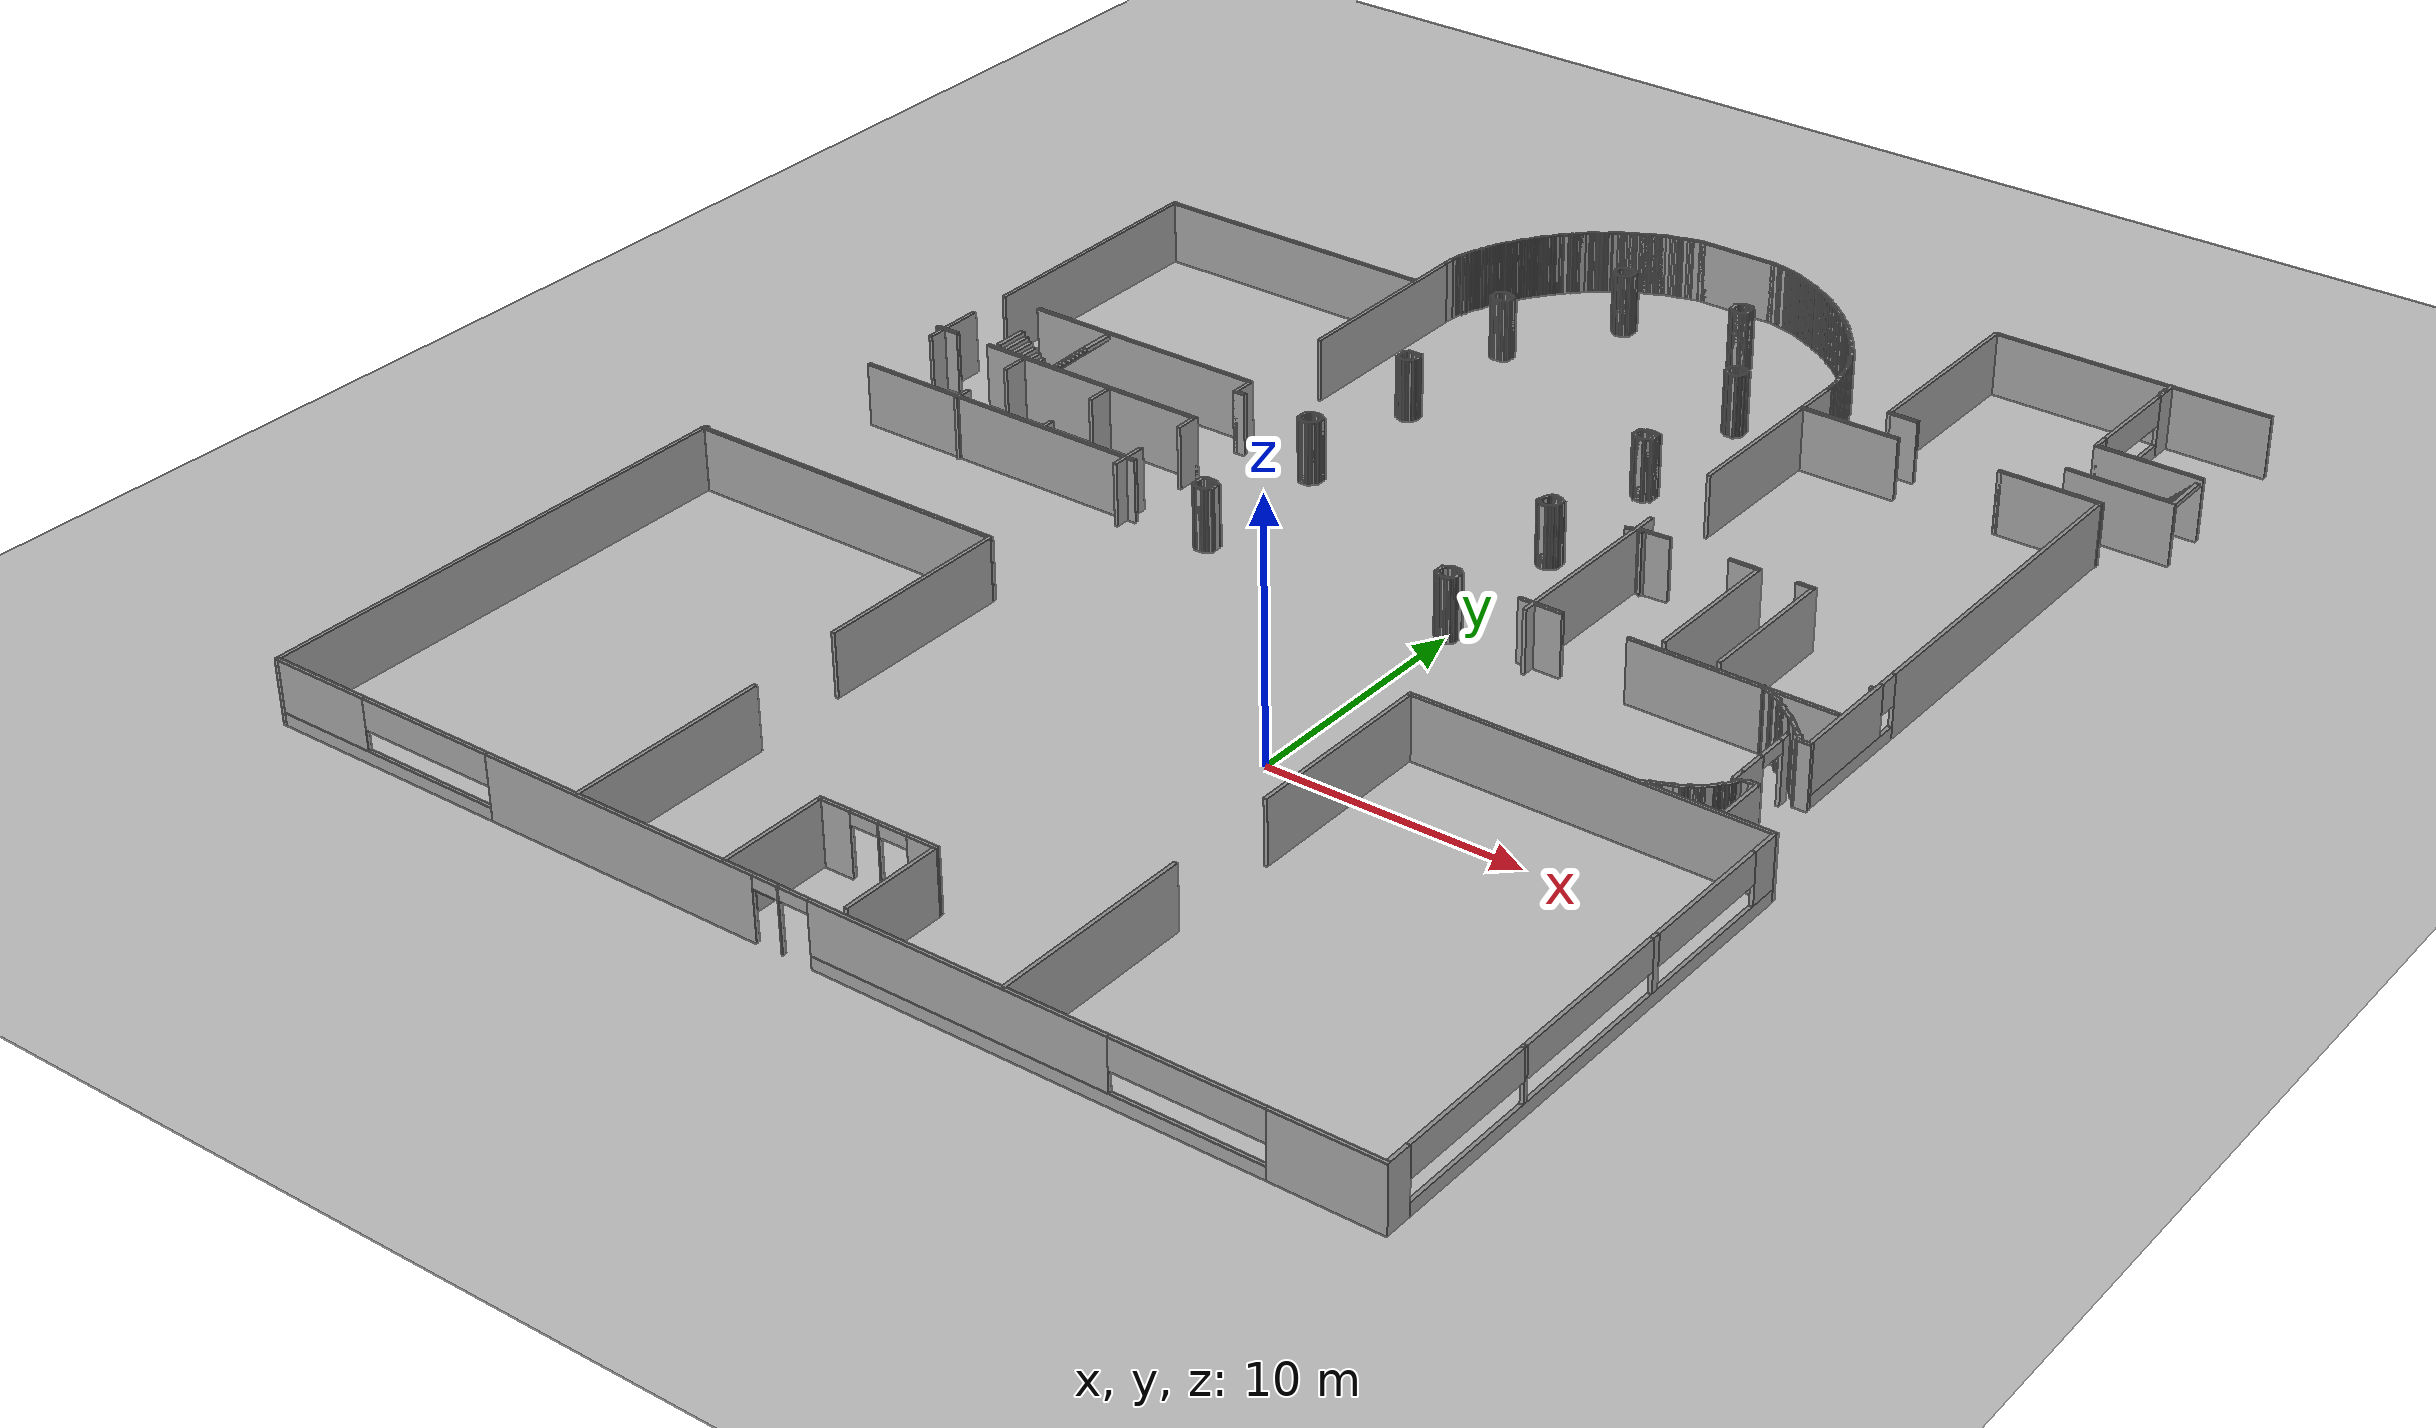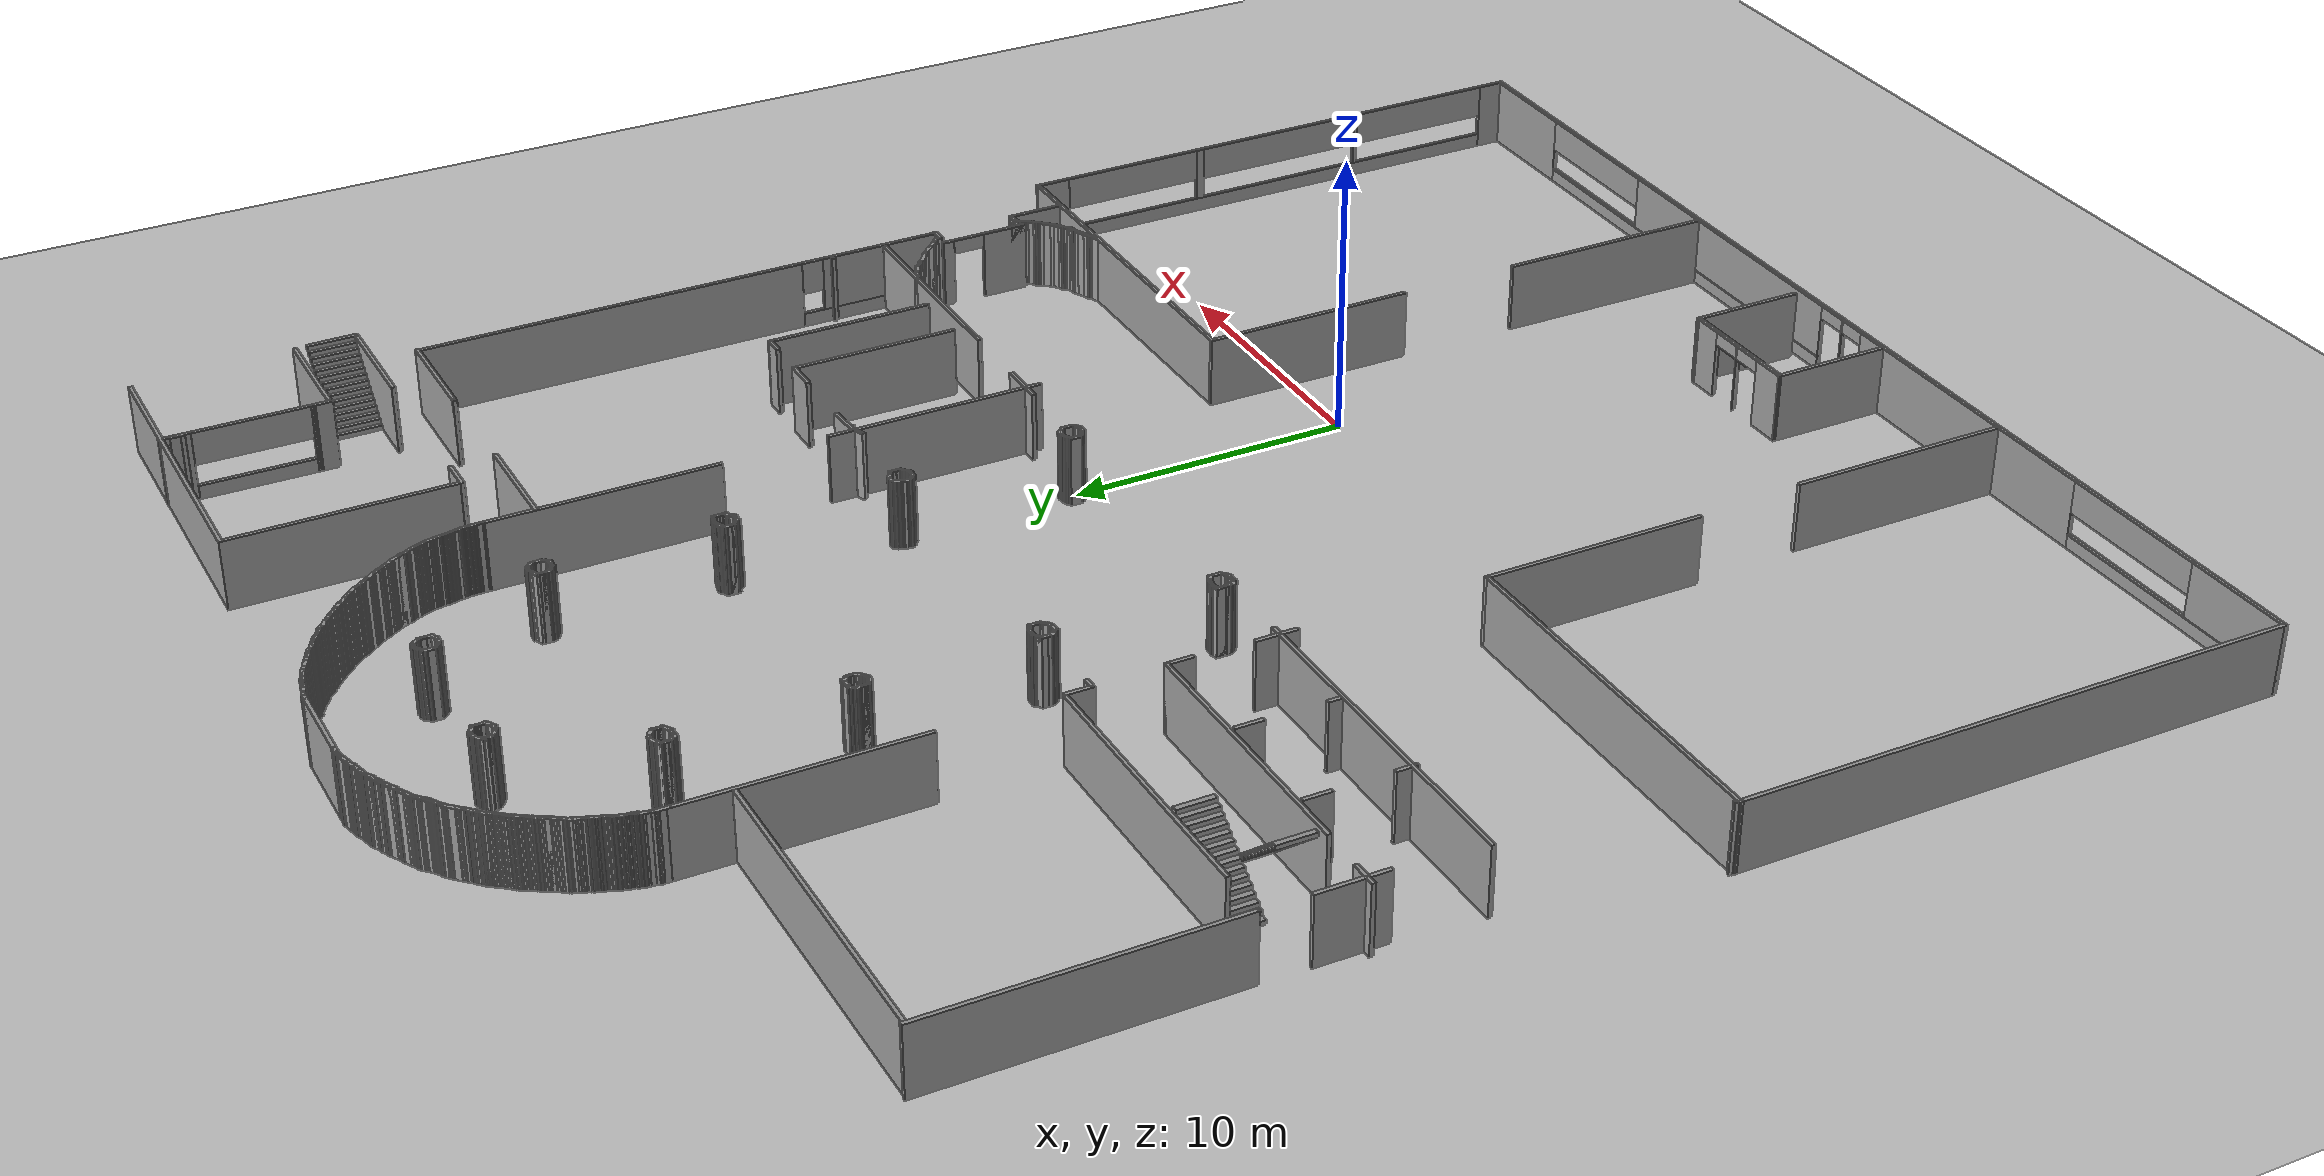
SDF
<?xml version="1.0" ?>
<sdf version="1.4">
  <world name="default">
    <include>
      <uri>model://ground_plane</uri>
    </include>
    <include>
      <uri>model://sun</uri>
    </include>
    <include>
      <uri>model://draft3</uri>
      <pose>-5 10 0 0 0 0</pose>
    </include>
  </world>
</sdf>

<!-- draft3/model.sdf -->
<sdf version='1.6'>
  <model name='draft3'>
    <pose frame=''>34.2026 -2.81154 0 0 -0 0</pose>
    <link name='Stairs_0'>
      <visual name='Stairs_0_Visual_0'>
        <pose frame=''>-15.388 4.7295 0.083333 0 -0 -1.5708</pose>
        <geometry>
          <box>
            <size>1.38352 0.192777 0.166667</size>
          </box>
        </geometry>
        <material>
          <script>
            <uri>file://media/materials/scripts/gazebo.material</uri>
            <name>Gazebo/Grey</name>
          </script>
          <ambient>1 1 1 1</ambient>
        </material>
      </visual>
      <collision name='Stairs_0_Collision_0'>
        <geometry>
          <box>
            <size>1.38352 0.192777 0.166667</size>
          </box>
        </geometry>
        <pose frame=''>-15.388 4.7295 0.083333 0 -0 -1.5708</pose>
      </collision>
      <visual name='Stairs_0_Visual_1'>
        <pose frame=''>-15.5807 4.7295 0.25 0 -0 -1.5708</pose>
        <geometry>
          <box>
            <size>1.38352 0.192777 0.166667</size>
          </box>
        </geometry>
        <material>
          <script>
            <uri>file://media/materials/scripts/gazebo.material</uri>
            <name>Gazebo/Grey</name>
          </script>
          <ambient>1 1 1 1</ambient>
        </material>
      </visual>
      <collision name='Stairs_0_Collision_1'>
        <geometry>
          <box>
            <size>1.38352 0.192777 0.166667</size>
          </box>
        </geometry>
        <pose frame=''>-15.5807 4.7295 0.25 0 -0 -1.5708</pose>
      </collision>
      <visual name='Stairs_0_Visual_2'>
        <pose frame=''>-15.7735 4.7295 0.416667 0 -0 -1.5708</pose>
        <geometry>
          <box>
            <size>1.38352 0.192777 0.166667</size>
          </box>
        </geometry>
        <material>
          <script>
            <uri>file://media/materials/scripts/gazebo.material</uri>
            <name>Gazebo/Grey</name>
          </script>
          <ambient>1 1 1 1</ambient>
        </material>
      </visual>
      <collision name='Stairs_0_Collision_2'>
        <geometry>
          <box>
            <size>1.38352 0.192777 0.166667</size>
          </box>
        </geometry>
        <pose frame=''>-15.7735 4.7295 0.416667 0 -0 -1.5708</pose>
      </collision>
      <visual name='Stairs_0_Visual_3'>
        <pose frame=''>-15.9663 4.7295 0.583333 0 -0 -1.5708</pose>
        <geometry>
          <box>
            <size>1.38352 0.192777 0.166667</size>
          </box>
        </geometry>
        <material>
          <script>
            <uri>file://media/materials/scripts/gazebo.material</uri>
            <name>Gazebo/Grey</name>
          </script>
          <ambient>1 1 1 1</ambient>
        </material>
      </visual>
      <collision name='Stairs_0_Collision_3'>
        <geometry>
          <box>
            <size>1.38352 0.192777 0.166667</size>
          </box>
        </geometry>
        <pose frame=''>-15.9663 4.7295 0.583333 0 -0 -1.5708</pose>
      </collision>
      <visual name='Stairs_0_Visual_4'>
        <pose frame=''>-16.1591 4.7295 0.75 0 -0 -1.5708</pose>
        <geometry>
          <box>
            <size>1.38352 0.192777 0.166667</size>
          </box>
        </geometry>
        <material>
          <script>
            <uri>file://media/materials/scripts/gazebo.material</uri>
            <name>Gazebo/Grey</name>
          </script>
          <ambient>1 1 1 1</ambient>
        </material>
      </visual>
      <collision name='Stairs_0_Collision_4'>
        <geometry>
          <box>
            <size>1.38352 0.192777 0.166667</size>
          </box>
        </geometry>
        <pose frame=''>-16.1591 4.7295 0.75 0 -0 -1.5708</pose>
      </collision>
      <visual name='Stairs_0_Visual_5'>
        <pose frame=''>-16.3518 4.7295 0.916667 0 -0 -1.5708</pose>
        <geometry>
          <box>
            <size>1.38352 0.192777 0.166667</size>
          </box>
        </geometry>
        <material>
          <script>
            <uri>file://media/materials/scripts/gazebo.material</uri>
            <name>Gazebo/Grey</name>
          </script>
          <ambient>1 1 1 1</ambient>
        </material>
      </visual>
      <collision name='Stairs_0_Collision_5'>
        <geometry>
          <box>
            <size>1.38352 0.192777 0.166667</size>
          </box>
        </geometry>
        <pose frame=''>-16.3518 4.7295 0.916667 0 -0 -1.5708</pose>
      </collision>
      <visual name='Stairs_0_Visual_6'>
        <pose frame=''>-16.5446 4.7295 1.08333 0 -0 -1.5708</pose>
        <geometry>
          <box>
            <size>1.38352 0.192777 0.166667</size>
          </box>
        </geometry>
        <material>
          <script>
            <uri>file://media/materials/scripts/gazebo.material</uri>
            <name>Gazebo/Grey</name>
          </script>
          <ambient>1 1 1 1</ambient>
        </material>
      </visual>
      <collision name='Stairs_0_Collision_6'>
        <geometry>
          <box>
            <size>1.38352 0.192777 0.166667</size>
          </box>
        </geometry>
        <pose frame=''>-16.5446 4.7295 1.08333 0 -0 -1.5708</pose>
      </collision>
      <visual name='Stairs_0_Visual_7'>
        <pose frame=''>-16.7374 4.7295 1.25 0 -0 -1.5708</pose>
        <geometry>
          <box>
            <size>1.38352 0.192777 0.166667</size>
          </box>
        </geometry>
        <material>
          <script>
            <uri>file://media/materials/scripts/gazebo.material</uri>
            <name>Gazebo/Grey</name>
          </script>
          <ambient>1 1 1 1</ambient>
        </material>
      </visual>
      <collision name='Stairs_0_Collision_7'>
        <geometry>
          <box>
            <size>1.38352 0.192777 0.166667</size>
          </box>
        </geometry>
        <pose frame=''>-16.7374 4.7295 1.25 0 -0 -1.5708</pose>
      </collision>
      <visual name='Stairs_0_Visual_8'>
        <pose frame=''>-16.9302 4.7295 1.41667 0 -0 -1.5708</pose>
        <geometry>
          <box>
            <size>1.38352 0.192777 0.166667</size>
          </box>
        </geometry>
        <material>
          <script>
            <uri>file://media/materials/scripts/gazebo.material</uri>
            <name>Gazebo/Grey</name>
          </script>
          <ambient>1 1 1 1</ambient>
        </material>
      </visual>
      <collision name='Stairs_0_Collision_8'>
        <geometry>
          <box>
            <size>1.38352 0.192777 0.166667</size>
          </box>
        </geometry>
        <pose frame=''>-16.9302 4.7295 1.41667 0 -0 -1.5708</pose>
      </collision>
      <visual name='Stairs_0_Visual_9'>
        <pose frame=''>-17.1229 4.7295 1.58333 0 -0 -1.5708</pose>
        <geometry>
          <box>
            <size>1.38352 0.192777 0.166667</size>
          </box>
        </geometry>
        <material>
          <script>
            <uri>file://media/materials/scripts/gazebo.material</uri>
            <name>Gazebo/Grey</name>
          </script>
          <ambient>1 1 1 1</ambient>
        </material>
      </visual>
      <collision name='Stairs_0_Collision_9'>
        <geometry>
          <box>
            <size>1.38352 0.192777 0.166667</size>
          </box>
        </geometry>
        <pose frame=''>-17.1229 4.7295 1.58333 0 -0 -1.5708</pose>
      </collision>
      <visual name='Stairs_0_Visual_10'>
        <pose frame=''>-17.3157 4.7295 1.75 0 -0 -1.5708</pose>
        <geometry>
          <box>
            <size>1.38352 0.192777 0.166667</size>
          </box>
        </geometry>
        <material>
          <script>
            <uri>file://media/materials/scripts/gazebo.material</uri>
            <name>Gazebo/Grey</name>
          </script>
          <ambient>1 1 1 1</ambient>
        </material>
      </visual>
      <collision name='Stairs_0_Collision_10'>
        <geometry>
          <box>
            <size>1.38352 0.192777 0.166667</size>
          </box>
        </geometry>
        <pose frame=''>-17.3157 4.7295 1.75 0 -0 -1.5708</pose>
      </collision>
      <visual name='Stairs_0_Visual_11'>
        <pose frame=''>-17.5085 4.7295 1.91667 0 -0 -1.5708</pose>
        <geometry>
          <box>
            <size>1.38352 0.192777 0.166667</size>
          </box>
        </geometry>
        <material>
          <script>
            <uri>file://media/materials/scripts/gazebo.material</uri>
            <name>Gazebo/Grey</name>
          </script>
          <ambient>1 1 1 1</ambient>
        </material>
      </visual>
      <collision name='Stairs_0_Collision_11'>
        <geometry>
          <box>
            <size>1.38352 0.192777 0.166667</size>
          </box>
        </geometry>
        <pose frame=''>-17.5085 4.7295 1.91667 0 -0 -1.5708</pose>
      </collision>
      <visual name='Stairs_0_Visual_12'>
        <pose frame=''>-17.7013 4.7295 2.08333 0 -0 -1.5708</pose>
        <geometry>
          <box>
            <size>1.38352 0.192777 0.166667</size>
          </box>
        </geometry>
        <material>
          <script>
            <uri>file://media/materials/scripts/gazebo.material</uri>
            <name>Gazebo/Grey</name>
          </script>
          <ambient>1 1 1 1</ambient>
        </material>
      </visual>
      <collision name='Stairs_0_Collision_12'>
        <geometry>
          <box>
            <size>1.38352 0.192777 0.166667</size>
          </box>
        </geometry>
        <pose frame=''>-17.7013 4.7295 2.08333 0 -0 -1.5708</pose>
      </collision>
      <visual name='Stairs_0_Visual_13'>
        <pose frame=''>-17.894 4.7295 2.25 0 -0 -1.5708</pose>
        <geometry>
          <box>
            <size>1.38352 0.192777 0.166667</size>
          </box>
        </geometry>
        <material>
          <script>
            <uri>file://media/materials/scripts/gazebo.material</uri>
            <name>Gazebo/Grey</name>
          </script>
          <ambient>1 1 1 1</ambient>
        </material>
      </visual>
      <collision name='Stairs_0_Collision_13'>
        <geometry>
          <box>
            <size>1.38352 0.192777 0.166667</size>
          </box>
        </geometry>
        <pose frame=''>-17.894 4.7295 2.25 0 -0 -1.5708</pose>
      </collision>
      <visual name='Stairs_0_Visual_14'>
        <pose frame=''>-18.0868 4.7295 2.41667 0 -0 -1.5708</pose>
        <geometry>
          <box>
            <size>1.38352 0.192777 0.166667</size>
          </box>
        </geometry>
        <material>
          <script>
            <uri>file://media/materials/scripts/gazebo.material</uri>
            <name>Gazebo/Grey</name>
          </script>
          <ambient>1 1 1 1</ambient>
        </material>
      </visual>
      <collision name='Stairs_0_Collision_14'>
        <geometry>
          <box>
            <size>1.38352 0.192777 0.166667</size>
          </box>
        </geometry>
        <pose frame=''>-18.0868 4.7295 2.41667 0 -0 -1.5708</pose>
      </collision>
    </link>
    <link name='Stairs_1'>
      <visual name='Stairs_1_Visual_0'>
        <pose frame=''>-18.2224 6.39726 0.083333 0 -0 1.5708</pose>
        <geometry>
          <box>
            <size>1.34385 0.206002 0.166667</size>
          </box>
        </geometry>
        <material>
          <script>
            <uri>file://media/materials/scripts/gazebo.material</uri>
            <name>Gazebo/Grey</name>
          </script>
          <ambient>1 1 1 1</ambient>
        </material>
      </visual>
      <collision name='Stairs_1_Collision_0'>
        <geometry>
          <box>
            <size>1.34385 0.206002 0.166667</size>
          </box>
        </geometry>
        <pose frame=''>-18.2224 6.39726 0.083333 0 -0 1.5708</pose>
      </collision>
      <visual name='Stairs_1_Visual_1'>
        <pose frame=''>-18.0164 6.39726 0.25 0 -0 1.5708</pose>
        <geometry>
          <box>
            <size>1.34385 0.206002 0.166667</size>
          </box>
        </geometry>
        <material>
          <script>
            <uri>file://media/materials/scripts/gazebo.material</uri>
            <name>Gazebo/Grey</name>
          </script>
          <ambient>1 1 1 1</ambient>
        </material>
      </visual>
      <collision name='Stairs_1_Collision_1'>
        <geometry>
          <box>
            <size>1.34385 0.206002 0.166667</size>
          </box>
        </geometry>
        <pose frame=''>-18.0164 6.39726 0.25 0 -0 1.5708</pose>
      </collision>
      <visual name='Stairs_1_Visual_2'>
        <pose frame=''>-17.8104 6.39726 0.416667 0 -0 1.5708</pose>
        <geometry>
          <box>
            <size>1.34385 0.206002 0.166667</size>
          </box>
        </geometry>
        <material>
          <script>
            <uri>file://media/materials/scripts/gazebo.material</uri>
            <name>Gazebo/Grey</name>
          </script>
          <ambient>1 1 1 1</ambient>
        </material>
      </visual>
      <collision name='Stairs_1_Collision_2'>
        <geometry>
          <box>
            <size>1.34385 0.206002 0.166667</size>
          </box>
        </geometry>
        <pose frame=''>-17.8104 6.39726 0.416667 0 -0 1.5708</pose>
      </collision>
      <visual name='Stairs_1_Visual_3'>
        <pose frame=''>-17.6044 6.39726 0.583333 0 -0 1.5708</pose>
        <geometry>
          <box>
            <size>1.34385 0.206002 0.166667</size>
          </box>
        </geometry>
        <material>
          <script>
            <uri>file://media/materials/scripts/gazebo.material</uri>
            <name>Gazebo/Grey</name>
          </script>
          <ambient>1 1 1 1</ambient>
        </material>
      </visual>
      <collision name='Stairs_1_Collision_3'>
        <geometry>
          <box>
            <size>1.34385 0.206002 0.166667</size>
          </box>
        </geometry>
        <pose frame=''>-17.6044 6.39726 0.583333 0 -0 1.5708</pose>
      </collision>
      <visual name='Stairs_1_Visual_4'>
        <pose frame=''>-17.3984 6.39726 0.75 0 -0 1.5708</pose>
        <geometry>
          <box>
            <size>1.34385 0.206002 0.166667</size>
          </box>
        </geometry>
        <material>
          <script>
            <uri>file://media/materials/scripts/gazebo.material</uri>
            <name>Gazebo/Grey</name>
          </script>
          <ambient>1 1 1 1</ambient>
        </material>
      </visual>
      <collision name='Stairs_1_Collision_4'>
        <geometry>
          <box>
            <size>1.34385 0.206002 0.166667</size>
          </box>
        </geometry>
        <pose frame=''>-17.3984 6.39726 0.75 0 -0 1.5708</pose>
      </collision>
      <visual name='Stairs_1_Visual_5'>
        <pose frame=''>-17.1924 6.39726 0.916667 0 -0 1.5708</pose>
        <geometry>
          <box>
            <size>1.34385 0.206002 0.166667</size>
          </box>
        </geometry>
        <material>
          <script>
            <uri>file://media/materials/scripts/gazebo.material</uri>
            <name>Gazebo/Grey</name>
          </script>
          <ambient>1 1 1 1</ambient>
        </material>
      </visual>
      <collision name='Stairs_1_Collision_5'>
        <geometry>
          <box>
            <size>1.34385 0.206002 0.166667</size>
          </box>
        </geometry>
        <pose frame=''>-17.1924 6.39726 0.916667 0 -0 1.5708</pose>
      </collision>
      <visual name='Stairs_1_Visual_6'>
        <pose frame=''>-16.9864 6.39726 1.08333 0 -0 1.5708</pose>
        <geometry>
          <box>
            <size>1.34385 0.206002 0.166667</size>
          </box>
        </geometry>
        <material>
          <script>
            <uri>file://media/materials/scripts/gazebo.material</uri>
            <name>Gazebo/Grey</name>
          </script>
          <ambient>1 1 1 1</ambient>
        </material>
      </visual>
      <collision name='Stairs_1_Collision_6'>
        <geometry>
          <box>
            <size>1.34385 0.206002 0.166667</size>
          </box>
        </geometry>
        <pose frame=''>-16.9864 6.39726 1.08333 0 -0 1.5708</pose>
      </collision>
      <visual name='Stairs_1_Visual_7'>
        <pose frame=''>-16.7804 6.39726 1.25 0 -0 1.5708</pose>
        <geometry>
          <box>
            <size>1.34385 0.206002 0.166667</size>
          </box>
        </geometry>
        <material>
          <script>
            <uri>file://media/materials/scripts/gazebo.material</uri>
            <name>Gazebo/Grey</name>
          </script>
          <ambient>1 1 1 1</ambient>
        </material>
      </visual>
      <collision name='Stairs_1_Collision_7'>
        <geometry>
          <box>
            <size>1.34385 0.206002 0.166667</size>
          </box>
        </geometry>
        <pose frame=''>-16.7804 6.39726 1.25 0 -0 1.5708</pose>
      </collision>
      <visual name='Stairs_1_Visual_8'>
        <pose frame=''>-16.5744 6.39726 1.41667 0 -0 1.5708</pose>
        <geometry>
          <box>
            <size>1.34385 0.206002 0.166667</size>
          </box>
        </geometry>
        <material>
          <script>
            <uri>file://media/materials/scripts/gazebo.material</uri>
            <name>Gazebo/Grey</name>
          </script>
          <ambient>1 1 1 1</ambient>
        </material>
      </visual>
      <collision name='Stairs_1_Collision_8'>
        <geometry>
          <box>
            <size>1.34385 0.206002 0.166667</size>
          </box>
        </geometry>
        <pose frame=''>-16.5744 6.39726 1.41667 0 -0 1.5708</pose>
      </collision>
      <visual name='Stairs_1_Visual_9'>
        <pose frame=''>-16.3684 6.39726 1.58333 0 -0 1.5708</pose>
        <geometry>
          <box>
            <size>1.34385 0.206002 0.166667</size>
          </box>
        </geometry>
        <material>
          <script>
            <uri>file://media/materials/scripts/gazebo.material</uri>
            <name>Gazebo/Grey</name>
          </script>
          <ambient>1 1 1 1</ambient>
        </material>
      </visual>
      <collision name='Stairs_1_Collision_9'>
        <geometry>
          <box>
            <size>1.34385 0.206002 0.166667</size>
          </box>
        </geometry>
        <pose frame=''>-16.3684 6.39726 1.58333 0 -0 1.5708</pose>
      </collision>
      <visual name='Stairs_1_Visual_10'>
        <pose frame=''>-16.1624 6.39726 1.75 0 -0 1.5708</pose>
        <geometry>
          <box>
            <size>1.34385 0.206002 0.166667</size>
          </box>
        </geometry>
        <material>
          <script>
            <uri>file://media/materials/scripts/gazebo.material</uri>
            <name>Gazebo/Grey</name>
          </script>
          <ambient>1 1 1 1</ambient>
        </material>
      </visual>
      <collision name='Stairs_1_Collision_10'>
        <geometry>
          <box>
            <size>1.34385 0.206002 0.166667</size>
          </box>
        </geometry>
        <pose frame=''>-16.1624 6.39726 1.75 0 -0 1.5708</pose>
      </collision>
      <visual name='Stairs_1_Visual_11'>
        <pose frame=''>-15.9564 6.39726 1.91667 0 -0 1.5708</pose>
        <geometry>
          <box>
            <size>1.34385 0.206002 0.166667</size>
          </box>
        </geometry>
        <material>
          <script>
            <uri>file://media/materials/scripts/gazebo.material</uri>
            <name>Gazebo/Grey</name>
          </script>
          <ambient>1 1 1 1</ambient>
        </material>
      </visual>
      <collision name='Stairs_1_Collision_11'>
        <geometry>
          <box>
            <size>1.34385 0.206002 0.166667</size>
          </box>
        </geometry>
        <pose frame=''>-15.9564 6.39726 1.91667 0 -0 1.5708</pose>
      </collision>
      <visual name='Stairs_1_Visual_12'>
        <pose frame=''>-15.7504 6.39726 2.08333 0 -0 1.5708</pose>
        <geometry>
          <box>
            <size>1.34385 0.206002 0.166667</size>
          </box>
        </geometry>
        <material>
          <script>
            <uri>file://media/materials/scripts/gazebo.material</uri>
            <name>Gazebo/Grey</name>
          </script>
          <ambient>1 1 1 1</ambient>
        </material>
      </visual>
      <collision name='Stairs_1_Collision_12'>
        <geometry>
          <box>
            <size>1.34385 0.206002 0.166667</size>
          </box>
        </geometry>
        <pose frame=''>-15.7504 6.39726 2.08333 0 -0 1.5708</pose>
      </collision>
      <visual name='Stairs_1_Visual_13'>
        <pose frame=''>-15.5444 6.39726 2.25 0 -0 1.5708</pose>
        <geometry>
          <box>
            <size>1.34385 0.206002 0.166667</size>
          </box>
        </geometry>
        <material>
          <script>
            <uri>file://media/materials/scripts/gazebo.material</uri>
            <name>Gazebo/Grey</name>
          </script>
          <ambient>1 1 1 1</ambient>
        </material>
      </visual>
      <collision name='Stairs_1_Collision_13'>
        <geometry>
          <box>
            <size>1.34385 0.206002 0.166667</size>
          </box>
        </geometry>
        <pose frame=''>-15.5444 6.39726 2.25 0 -0 1.5708</pose>
      </collision>
      <visual name='Stairs_1_Visual_14'>
        <pose frame=''>-15.3384 6.39726 2.41667 0 -0 1.5708</pose>
        <geometry>
          <box>
            <size>1.34385 0.206002 0.166667</size>
          </box>
        </geometry>
        <material>
          <script>
            <uri>file://media/materials/scripts/gazebo.material</uri>
            <name>Gazebo/Grey</name>
          </script>
          <ambient>1 1 1 1</ambient>
        </material>
      </visual>
      <collision name='Stairs_1_Collision_14'>
        <geometry>
          <box>
            <size>1.34385 0.206002 0.166667</size>
          </box>
        </geometry>
        <pose frame=''>-15.3384 6.39726 2.41667 0 -0 1.5708</pose>
      </collision>
    </link>
    <link name='Stairs_2'>
      <visual name='Stairs_2_Visual_0'>
        <pose frame=''>19.9679 19.8567 0.083333 0 -0 1.5708</pose>
        <geometry>
          <box>
            <size>1.80606 0.167429 0.166667</size>
          </box>
        </geometry>
        <material>
          <script>
            <uri>file://media/materials/scripts/gazebo.material</uri>
            <name>Gazebo/Grey</name>
          </script>
          <ambient>1 1 1 1</ambient>
        </material>
      </visual>
      <collision name='Stairs_2_Collision_0'>
        <geometry>
          <box>
            <size>1.80606 0.167429 0.166667</size>
          </box>
        </geometry>
        <pose frame=''>19.9679 19.8567 0.083333 0 -0 1.5708</pose>
      </collision>
      <visual name='Stairs_2_Visual_1'>
        <pose frame=''>20.1353 19.8567 0.25 0 -0 1.5708</pose>
        <geometry>
          <box>
            <size>1.80606 0.167429 0.166667</size>
          </box>
        </geometry>
        <material>
          <script>
            <uri>file://media/materials/scripts/gazebo.material</uri>
            <name>Gazebo/Grey</name>
          </script>
          <ambient>1 1 1 1</ambient>
        </material>
      </visual>
      <collision name='Stairs_2_Collision_1'>
        <geometry>
          <box>
            <size>1.80606 0.167429 0.166667</size>
          </box>
        </geometry>
        <pose frame=''>20.1353 19.8567 0.25 0 -0 1.5708</pose>
      </collision>
      <visual name='Stairs_2_Visual_2'>
        <pose frame=''>20.3027 19.8567 0.416667 0 -0 1.5708</pose>
        <geometry>
          <box>
            <size>1.80606 0.167429 0.166667</size>
          </box>
        </geometry>
        <material>
          <script>
            <uri>file://media/materials/scripts/gazebo.material</uri>
            <name>Gazebo/Grey</name>
          </script>
          <ambient>1 1 1 1</ambient>
        </material>
      </visual>
      <collision name='Stairs_2_Collision_2'>
        <geometry>
          <box>
            <size>1.80606 0.167429 0.166667</size>
          </box>
        </geometry>
        <pose frame=''>20.3027 19.8567 0.416667 0 -0 1.5708</pose>
      </collision>
      <visual name='Stairs_2_Visual_3'>
        <pose frame=''>20.4702 19.8567 0.583333 0 -0 1.5708</pose>
        <geometry>
          <box>
            <size>1.80606 0.167429 0.166667</size>
          </box>
        </geometry>
        <material>
          <script>
            <uri>file://media/materials/scripts/gazebo.material</uri>
            <name>Gazebo/Grey</name>
          </script>
          <ambient>1 1 1 1</ambient>
        </material>
      </visual>
      <collision name='Stairs_2_Collision_3'>
        <geometry>
          <box>
            <size>1.80606 0.167429 0.166667</size>
          </box>
        </geometry>
        <pose frame=''>20.4702 19.8567 0.583333 0 -0 1.5708</pose>
      </collision>
      <visual name='Stairs_2_Visual_4'>
        <pose frame=''>20.6376 19.8567 0.75 0 -0 1.5708</pose>
        <geometry>
          <box>
            <size>1.80606 0.167429 0.166667</size>
          </box>
        </geometry>
        <material>
          <script>
            <uri>file://media/materials/scripts/gazebo.material</uri>
            <name>Gazebo/Grey</name>
          </script>
          <ambient>1 1 1 1</ambient>
        </material>
      </visual>
      <collision name='Stairs_2_Collision_4'>
        <geometry>
          <box>
            <size>1.80606 0.167429 0.166667</size>
          </box>
        </geometry>
        <pose frame=''>20.6376 19.8567 0.75 0 -0 1.5708</pose>
      </collision>
      <visual name='Stairs_2_Visual_5'>
        <pose frame=''>20.805 19.8567 0.916667 0 -0 1.5708</pose>
        <geometry>
          <box>
            <size>1.80606 0.167429 0.166667</size>
          </box>
        </geometry>
        <material>
          <script>
            <uri>file://media/materials/scripts/gazebo.material</uri>
            <name>Gazebo/Grey</name>
          </script>
          <ambient>1 1 1 1</ambient>
        </material>
      </visual>
      <collision name='Stairs_2_Collision_5'>
        <geometry>
          <box>
            <size>1.80606 0.167429 0.166667</size>
          </box>
        </geometry>
        <pose frame=''>20.805 19.8567 0.916667 0 -0 1.5708</pose>
      </collision>
      <visual name='Stairs_2_Visual_6'>
        <pose frame=''>20.9725 19.8567 1.08333 0 -0 1.5708</pose>
        <geometry>
          <box>
            <size>1.80606 0.167429 0.166667</size>
          </box>
        </geometry>
        <material>
          <script>
            <uri>file://media/materials/scripts/gazebo.material</uri>
            <name>Gazebo/Grey</name>
          </script>
          <ambient>1 1 1 1</ambient>
        </material>
      </visual>
      <collision name='Stairs_2_Collision_6'>
        <geometry>
          <box>
            <size>1.80606 0.167429 0.166667</size>
          </box>
        </geometry>
        <pose frame=''>20.9725 19.8567 1.08333 0 -0 1.5708</pose>
      </collision>
      <visual name='Stairs_2_Visual_7'>
        <pose frame=''>21.1399 19.8567 1.25 0 -0 1.5708</pose>
        <geometry>
          <box>
            <size>1.80606 0.167429 0.166667</size>
          </box>
        </geometry>
        <material>
          <script>
            <uri>file://media/materials/scripts/gazebo.material</uri>
            <name>Gazebo/Grey</name>
          </script>
          <ambient>1 1 1 1</ambient>
        </material>
      </visual>
      <collision name='Stairs_2_Collision_7'>
        <geometry>
          <box>
            <size>1.80606 0.167429 0.166667</size>
          </box>
        </geometry>
        <pose frame=''>21.1399 19.8567 1.25 0 -0 1.5708</pose>
      </collision>
      <visual name='Stairs_2_Visual_8'>
        <pose frame=''>21.3073 19.8567 1.41667 0 -0 1.5708</pose>
        <geometry>
          <box>
            <size>1.80606 0.167429 0.166667</size>
          </box>
        </geometry>
        <material>
          <script>
            <uri>file://media/materials/scripts/gazebo.material</uri>
            <name>Gazebo/Grey</name>
          </script>
          <ambient>1 1 1 1</ambient>
        </material>
      </visual>
      <collision name='Stairs_2_Collision_8'>
        <geometry>
          <box>
            <size>1.80606 0.167429 0.166667</size>
          </box>
        </geometry>
        <pose frame=''>21.3073 19.8567 1.41667 0 -0 1.5708</pose>
      </collision>
      <visual name='Stairs_2_Visual_9'>
        <pose frame=''>21.4747 19.8567 1.58333 0 -0 1.5708</pose>
        <geometry>
          <box>
            <size>1.80606 0.167429 0.166667</size>
          </box>
        </geometry>
        <material>
          <script>
            <uri>file://media/materials/scripts/gazebo.material</uri>
            <name>Gazebo/Grey</name>
          </script>
          <ambient>1 1 1 1</ambient>
        </material>
      </visual>
      <collision name='Stairs_2_Collision_9'>
        <geometry>
          <box>
            <size>1.80606 0.167429 0.166667</size>
          </box>
        </geometry>
        <pose frame=''>21.4747 19.8567 1.58333 0 -0 1.5708</pose>
      </collision>
      <visual name='Stairs_2_Visual_10'>
        <pose frame=''>21.6422 19.8567 1.75 0 -0 1.5708</pose>
        <geometry>
          <box>
            <size>1.80606 0.167429 0.166667</size>
          </box>
        </geometry>
        <material>
          <script>
            <uri>file://media/materials/scripts/gazebo.material</uri>
            <name>Gazebo/Grey</name>
          </script>
          <ambient>1 1 1 1</ambient>
        </material>
      </visual>
      <collision name='Stairs_2_Collision_10'>
        <geometry>
          <box>
            <size>1.80606 0.167429 0.166667</size>
          </box>
        </geometry>
        <pose frame=''>21.6422 19.8567 1.75 0 -0 1.5708</pose>
      </collision>
      <visual name='Stairs_2_Visual_11'>
        <pose frame=''>21.8096 19.8567 1.91667 0 -0 1.5708</pose>
        <geometry>
          <box>
            <size>1.80606 0.167429 0.166667</size>
          </box>
        </geometry>
        <material>
          <script>
            <uri>file://media/materials/scripts/gazebo.material</uri>
            <name>Gazebo/Grey</name>
          </script>
          <ambient>1 1 1 1</ambient>
        </material>
      </visual>
      <collision name='Stairs_2_Collision_11'>
        <geometry>
          <box>
            <size>1.80606 0.167429 0.166667</size>
          </box>
        </geometry>
        <pose frame=''>21.8096 19.8567 1.91667 0 -0 1.5708</pose>
      </collision>
      <visual name='Stairs_2_Visual_12'>
        <pose frame=''>21.977 19.8567 2.08333 0 -0 1.5708</pose>
        <geometry>
          <box>
            <size>1.80606 0.167429 0.166667</size>
          </box>
        </geometry>
        <material>
          <script>
            <uri>file://media/materials/scripts/gazebo.material</uri>
            <name>Gazebo/Grey</name>
          </script>
          <ambient>1 1 1 1</ambient>
        </material>
      </visual>
      <collision name='Stairs_2_Collision_12'>
        <geometry>
          <box>
            <size>1.80606 0.167429 0.166667</size>
          </box>
        </geometry>
        <pose frame=''>21.977 19.8567 2.08333 0 -0 1.5708</pose>
      </collision>
      <visual name='Stairs_2_Visual_13'>
        <pose frame=''>22.1445 19.8567 2.25 0 -0 1.5708</pose>
        <geometry>
          <box>
            <size>1.80606 0.167429 0.166667</size>
          </box>
        </geometry>
        <material>
          <script>
            <uri>file://media/materials/scripts/gazebo.material</uri>
            <name>Gazebo/Grey</name>
          </script>
          <ambient>1 1 1 1</ambient>
        </material>
      </visual>
      <collision name='Stairs_2_Collision_13'>
        <geometry>
          <box>
            <size>1.80606 0.167429 0.166667</size>
          </box>
        </geometry>
        <pose frame=''>22.1445 19.8567 2.25 0 -0 1.5708</pose>
      </collision>
      <visual name='Stairs_2_Visual_14'>
        <pose frame=''>22.3119 19.8567 2.41667 0 -0 1.5708</pose>
        <geometry>
          <box>
            <size>1.80606 0.167429 0.166667</size>
          </box>
        </geometry>
        <material>
          <script>
            <uri>file://media/materials/scripts/gazebo.material</uri>
            <name>Gazebo/Grey</name>
          </script>
          <ambient>1 1 1 1</ambient>
        </material>
      </visual>
      <collision name='Stairs_2_Collision_14'>
        <geometry>
          <box>
            <size>1.80606 0.167429 0.166667</size>
          </box>
        </geometry>
        <pose frame=''>22.3119 19.8567 2.41667 0 -0 1.5708</pose>
      </collision>
    </link>
    <link name='Wall_1'>
      <pose frame=''>-0.128739 -27.0102 0 0 -0 3.14159</pose>
      <visual name='Wall_1_Visual_0'>
        <pose frame=''>-20.1677 0 1.25 0 -0 0</pose>
        <geometry>
          <box>
            <size>4.16463 0.15 2.5</size>
          </box>
        </geometry>
        <material>
          <script>
            <uri>file://media/materials/scripts/gazebo.material</uri>
            <name>Gazebo/Grey</name>
          </script>
          <ambient>1 1 1 1</ambient>
        </material>
      </visual>
      <collision name='Wall_1_Collision_0'>
        <geometry>
          <box>
            <size>4.16463 0.15 2.5</size>
          </box>
        </geometry>
        <pose frame=''>-20.1677 0 1.25 0 -0 0</pose>
      </collision>
      <visual name='Wall_1_Visual_1'>
        <pose frame=''>0.173368 0 1.25 0 -0 0</pose>
        <geometry>
          <box>
            <size>0.059921 0.15 2.5</size>
          </box>
        </geometry>
        <material>
          <script>
            <uri>file://media/materials/scripts/gazebo.material</uri>
            <name>Gazebo/Grey</name>
          </script>
          <ambient>1 1 1 1</ambient>
        </material>
      </visual>
      <collision name='Wall_1_Collision_1'>
        <geometry>
          <box>
            <size>0.059921 0.15 2.5</size>
          </box>
        </geometry>
        <pose frame=''>0.173368 0 1.25 0 -0 0</pose>
      </collision>
      <visual name='Wall_1_Visual_2'>
        <pose frame=''>6.88671 0 1.25 0 -0 0</pose>
        <geometry>
          <box>
            <size>11.3355 0.15 2.5</size>
          </box>
        </geometry>
        <material>
          <script>
            <uri>file://media/materials/scripts/gazebo.material</uri>
            <name>Gazebo/Grey</name>
          </script>
          <ambient>1 1 1 1</ambient>
        </material>
      </visual>
      <collision name='Wall_1_Collision_2'>
        <geometry>
          <box>
            <size>11.3355 0.15 2.5</size>
          </box>
        </geometry>
        <pose frame=''>6.88671 0 1.25 0 -0 0</pose>
      </collision>
      <visual name='Wall_1_Visual_3'>
        <pose frame=''>-9.5482 0 0.25 0 -0 0</pose>
        <geometry>
          <box>
            <size>17.0743 0.15 0.5</size>
          </box>
        </geometry>
        <material>
          <script>
            <uri>file://media/materials/scripts/gazebo.material</uri>
            <name>Gazebo/Grey</name>
          </script>
          <ambient>1 1 1 1</ambient>
        </material>
      </visual>
      <collision name='Wall_1_Collision_3'>
        <geometry>
          <box>
            <size>17.0743 0.15 0.5</size>
          </box>
        </geometry>
        <pose frame=''>-9.5482 0 0.25 0 -0 0</pose>
      </collision>
      <visual name='Wall_1_Visual_4'>
        <pose frame=''>17.4022 0 0.25 0 -0 0</pose>
        <geometry>
          <box>
            <size>9.69556 0.15 0.5</size>
          </box>
        </geometry>
        <material>
          <script>
            <uri>file://media/materials/scripts/gazebo.material</uri>
            <name>Gazebo/Grey</name>
          </script>
          <ambient>1 1 1 1</ambient>
        </material>
      </visual>
      <collision name='Wall_1_Collision_4'>
        <geometry>
          <box>
            <size>9.69556 0.15 0.5</size>
          </box>
        </geometry>
        <pose frame=''>17.4022 0 0.25 0 -0 0</pose>
      </collision>
      <visual name='Wall_1_Visual_5'>
        <pose frame=''>-6.72758 0 1.5 0 -0 0</pose>
        <geometry>
          <box>
            <size>11.4331 0.15 2</size>
          </box>
        </geometry>
        <material>
          <script>
            <uri>file://media/materials/scripts/gazebo.material</uri>
            <name>Gazebo/Grey</name>
          </script>
          <ambient>1 1 1 1</ambient>
        </material>
      </visual>
      <collision name='Wall_1_Collision_5'>
        <geometry>
          <box>
            <size>11.4331 0.15 2</size>
          </box>
        </geometry>
        <pose frame=''>-6.72758 0 1.5 0 -0 0</pose>
      </collision>
      <visual name='Wall_1_Visual_6'>
        <pose frame=''>-6.72758 0 1.5 0 -0 0</pose>
        <geometry>
          <box>
            <size>11.4331 0.15 2</size>
          </box>
        </geometry>
        <material>
          <script>
            <uri>file://media/materials/scripts/gazebo.material</uri>
            <name>Gazebo/Grey</name>
          </script>
          <ambient>1 1 1 1</ambient>
        </material>
      </visual>
      <collision name='Wall_1_Collision_6'>
        <geometry>
          <box>
            <size>11.4331 0.15 2</size>
          </box>
        </geometry>
        <pose frame=''>-6.72758 0 1.5 0 -0 0</pose>
      </collision>
      <visual name='Wall_1_Visual_7'>
        <pose frame=''>20.1962 0 1.5 0 -0 0</pose>
        <geometry>
          <box>
            <size>4.10752 0.15 2</size>
          </box>
        </geometry>
        <material>
          <script>
            <uri>file://media/materials/scripts/gazebo.material</uri>
            <name>Gazebo/Grey</name>
          </script>
          <ambient>1 1 1 1</ambient>
        </material>
      </visual>
      <collision name='Wall_1_Collision_7'>
        <geometry>
          <box>
            <size>4.10752 0.15 2</size>
          </box>
        </geometry>
        <pose frame=''>20.1962 0 1.5 0 -0 0</pose>
      </collision>
      <visual name='Wall_1_Visual_8'>
        <pose frame=''>-15.2648 0 1.9 0 -0 0</pose>
        <geometry>
          <box>
            <size>5.64124 0.15 1.2</size>
          </box>
        </geometry>
        <material>
          <script>
            <uri>file://media/materials/scripts/gazebo.material</uri>
            <name>Gazebo/Grey</name>
          </script>
          <ambient>1 1 1 1</ambient>
        </material>
      </visual>
      <collision name='Wall_1_Collision_8'>
        <geometry>
          <box>
            <size>5.64124 0.15 1.2</size>
          </box>
        </geometry>
        <pose frame=''>-15.2648 0 1.9 0 -0 0</pose>
      </collision>
      <visual name='Wall_1_Visual_9'>
        <pose frame=''>15.3485 0 1.9 0 -0 0</pose>
        <geometry>
          <box>
            <size>5.58804 0.15 1.2</size>
          </box>
        </geometry>
        <material>
          <script>
            <uri>file://media/materials/scripts/gazebo.material</uri>
            <name>Gazebo/Grey</name>
          </script>
          <ambient>1 1 1 1</ambient>
        </material>
      </visual>
      <collision name='Wall_1_Collision_9'>
        <geometry>
          <box>
            <size>5.58804 0.15 1.2</size>
          </box>
        </geometry>
        <pose frame=''>15.3485 0 1.9 0 -0 0</pose>
      </collision>
      <visual name='Wall_1_Visual_10'>
        <pose frame=''>0.711155 0 2.25 0 -0 0</pose>
        <geometry>
          <box>
            <size>1.01565 0.15 0.5</size>
          </box>
        </geometry>
        <material>
          <script>
            <uri>file://media/materials/scripts/gazebo.material</uri>
            <name>Gazebo/Grey</name>
          </script>
          <ambient>1 1 1 1</ambient>
        </material>
      </visual>
      <collision name='Wall_1_Collision_10'>
        <geometry>
          <box>
            <size>1.01565 0.15 0.5</size>
          </box>
        </geometry>
        <pose frame=''>0.711155 0 2.25 0 -0 0</pose>
      </collision>
      <visual name='Wall_1_Visual_11'>
        <pose frame=''>-0.433811 0 2.25 0 -0 0</pose>
        <geometry>
          <box>
            <size>1.15444 0.15 0.5</size>
          </box>
        </geometry>
        <material>
          <script>
            <uri>file://media/materials/scripts/gazebo.material</uri>
            <name>Gazebo/Grey</name>
          </script>
          <ambient>1 1 1 1</ambient>
        </material>
      </visual>
      <collision name='Wall_1_Collision_11'>
        <geometry>
          <box>
            <size>1.15444 0.15 0.5</size>
          </box>
        </geometry>
        <pose frame=''>-0.433811 0 2.25 0 -0 0</pose>
      </collision>
      <visual name='Wall_1_Visual_12'>
        <pose frame=''>-0.433811 0 2.25 0 -0 0</pose>
        <geometry>
          <box>
            <size>1.15444 0.15 0.5</size>
          </box>
        </geometry>
        <material>
          <script>
            <uri>file://media/materials/scripts/gazebo.material</uri>
            <name>Gazebo/Grey</name>
          </script>
          <ambient>1 1 1 1</ambient>
        </material>
      </visual>
      <collision name='Wall_1_Collision_12'>
        <geometry>
          <box>
            <size>1.15444 0.15 0.5</size>
          </box>
        </geometry>
        <pose frame=''>-0.433811 0 2.25 0 -0 0</pose>
      </collision>
    </link>
    <link name='Wall_10'>
      <collision name='Wall_10_Collision'>
        <geometry>
          <box>
            <size>13.75 0.15 2.5</size>
          </box>
        </geometry>
        <pose frame=''>0 0 1.25 0 -0 0</pose>
      </collision>
      <visual name='Wall_10_Visual'>
        <pose frame=''>0 0 1.25 0 -0 0</pose>
        <geometry>
          <box>
            <size>13.75 0.15 2.5</size>
          </box>
        </geometry>
        <material>
          <script>
            <uri>file://media/materials/scripts/gazebo.material</uri>
            <name>Gazebo/Grey</name>
          </script>
          <ambient>1 1 1 1</ambient>
        </material>
      </visual>
      <pose frame=''>15.2463 -6.91022 0 0 -0 3.14159</pose>
    </link>
    <link name='Wall_100'>
      <collision name='Wall_100_Collision'>
        <geometry>
          <box>
            <size>0.221219 0.15 2.5</size>
          </box>
        </geometry>
        <pose frame=''>0 0 1.25 0 -0 0</pose>
      </collision>
      <visual name='Wall_100_Visual'>
        <pose frame=''>0 0 1.25 0 -0 0</pose>
        <geometry>
          <box>
            <size>0.221219 0.15 2.5</size>
          </box>
        </geometry>
        <material>
          <script>
            <uri>file://media/materials/scripts/gazebo.material</uri>
            <name>Gazebo/Grey</name>
          </script>
          <ambient>1 1 1 1</ambient>
        </material>
      </visual>
      <pose frame=''>-8.14008 22.0271 0 0 -0 1.19029</pose>
    </link>
    <link name='Wall_101'>
      <collision name='Wall_101_Collision'>
        <geometry>
          <box>
            <size>0.238716 0.15 2.5</size>
          </box>
        </geometry>
        <pose frame=''>0 0 1.25 0 -0 0</pose>
      </collision>
      <visual name='Wall_101_Visual'>
        <pose frame=''>0 0 1.25 0 -0 0</pose>
        <geometry>
          <box>
            <size>0.238716 0.15 2.5</size>
          </box>
        </geometry>
        <material>
          <script>
            <uri>file://media/materials/scripts/gazebo.material</uri>
            <name>Gazebo/Grey</name>
          </script>
          <ambient>1 1 1 1</ambient>
        </material>
      </visual>
      <pose frame=''>-8.10702 22.0998 0 0 -0 1.10715</pose>
    </link>
    <link name='Wall_102'>
      <collision name='Wall_102_Collision'>
        <geometry>
          <box>
            <size>0.238716 0.15 2.5</size>
          </box>
        </geometry>
        <pose frame=''>0 0 1.25 0 -0 0</pose>
      </collision>
      <visual name='Wall_102_Visual'>
        <pose frame=''>0 0 1.25 0 -0 0</pose>
        <geometry>
          <box>
            <size>0.238716 0.15 2.5</size>
          </box>
        </geometry>
        <material>
          <script>
            <uri>file://media/materials/scripts/gazebo.material</uri>
            <name>Gazebo/Grey</name>
          </script>
          <ambient>1 1 1 1</ambient>
        </material>
      </visual>
      <pose frame=''>-8.06734 22.1792 0 0 -0 1.10715</pose>
    </link>
    <link name='Wall_103'>
      <collision name='Wall_103_Collision'>
        <geometry>
          <box>
            <size>0.250719 0.15 2.5</size>
          </box>
        </geometry>
        <pose frame=''>0 0 1.25 0 -0 0</pose>
      </collision>
      <visual name='Wall_103_Visual'>
        <pose frame=''>0 0 1.25 0 -0 0</pose>
        <geometry>
          <box>
            <size>0.250719 0.15 2.5</size>
          </box>
        </geometry>
        <material>
          <script>
            <uri>file://media/materials/scripts/gazebo.material</uri>
            <name>Gazebo/Grey</name>
          </script>
          <ambient>1 1 1 1</ambient>
        </material>
      </visual>
      <pose frame=''>-8.02767 22.2651 0 0 -0 1.1659</pose>
    </link>
    <link name='Wall_104'>
      <collision name='Wall_104_Collision'>
        <geometry>
          <box>
            <size>0.206109 0.15 2.5</size>
          </box>
        </geometry>
        <pose frame=''>0 0 1.25 0 -0 0</pose>
      </collision>
      <visual name='Wall_104_Visual'>
        <pose frame=''>0 0 1.25 0 -0 0</pose>
        <geometry>
          <box>
            <size>0.206109 0.15 2.5</size>
          </box>
        </geometry>
        <material>
          <script>
            <uri>file://media/materials/scripts/gazebo.material</uri>
            <name>Gazebo/Grey</name>
          </script>
          <ambient>1 1 1 1</ambient>
        </material>
      </visual>
      <pose frame=''>-7.98799 22.3312 0 0 -0 0.785398</pose>
    </link>
    <link name='Wall_105'>
      <collision name='Wall_105_Collision'>
        <geometry>
          <box>
            <size>0.263766 0.15 2.5</size>
          </box>
        </geometry>
        <pose frame=''>0 0 1.25 0 -0 0</pose>
      </collision>
      <visual name='Wall_105_Visual'>
        <pose frame=''>0 0 1.25 0 -0 0</pose>
        <geometry>
          <box>
            <size>0.263766 0.15 2.5</size>
          </box>
        </geometry>
        <material>
          <script>
            <uri>file://media/materials/scripts/gazebo.material</uri>
            <name>Gazebo/Grey</name>
          </script>
          <ambient>1 1 1 1</ambient>
        </material>
      </visual>
      <pose frame=''>-7.93509 22.3974 0 0 -0 0.950547</pose>
    </link>
    <link name='Wall_106'>
      <collision name='Wall_106_Collision'>
        <geometry>
          <box>
            <size>0.29305 0.15 2.5</size>
          </box>
        </geometry>
        <pose frame=''>0 0 1.25 0 -0 0</pose>
      </collision>
      <visual name='Wall_106_Visual'>
        <pose frame=''>0 0 1.25 0 -0 0</pose>
        <geometry>
          <box>
            <size>0.29305 0.15 2.5</size>
          </box>
        </geometry>
        <material>
          <script>
            <uri>file://media/materials/scripts/gazebo.material</uri>
            <name>Gazebo/Grey</name>
          </script>
          <ambient>1 1 1 1</ambient>
        </material>
      </visual>
      <pose frame=''>-7.86235 22.5032 0 0 -0 0.982794</pose>
    </link>
    <link name='Wall_107'>
      <collision name='Wall_107_Collision'>
        <geometry>
          <box>
            <size>0.263766 0.15 2.5</size>
          </box>
        </geometry>
        <pose frame=''>0 0 1.25 0 -0 0</pose>
      </collision>
      <visual name='Wall_107_Visual'>
        <pose frame=''>0 0 1.25 0 -0 0</pose>
        <geometry>
          <box>
            <size>0.263766 0.15 2.5</size>
          </box>
        </geometry>
        <material>
          <script>
            <uri>file://media/materials/scripts/gazebo.material</uri>
            <name>Gazebo/Grey</name>
          </script>
          <ambient>1 1 1 1</ambient>
        </material>
      </visual>
      <pose frame=''>-7.78962 22.609 0 0 -0 0.950547</pose>
    </link>
    <link name='Wall_108'>
      <collision name='Wall_108_Collision'>
        <geometry>
          <box>
            <size>0.268288 0.15 2.5</size>
          </box>
        </geometry>
        <pose frame=''>0 0 1.25 0 -0 0</pose>
      </collision>
      <visual name='Wall_108_Visual'>
        <pose frame=''>0 0 1.25 0 -0 0</pose>
        <geometry>
          <box>
            <size>0.268288 0.15 2.5</size>
          </box>
        </geometry>
        <material>
          <script>
            <uri>file://media/materials/scripts/gazebo.material</uri>
            <name>Gazebo/Grey</name>
          </script>
          <ambient>1 1 1 1</ambient>
        </material>
      </visual>
      <pose frame=''>-7.7301 22.7082 0 0 -0 1.10715</pose>
    </link>
    <link name='Wall_109'>
      <collision name='Wall_109_Collision'>
        <geometry>
          <box>
            <size>0.268288 0.15 2.5</size>
          </box>
        </geometry>
        <pose frame=''>0 0 1.25 0 -0 0</pose>
      </collision>
      <visual name='Wall_109_Visual'>
        <pose frame=''>0 0 1.25 0 -0 0</pose>
        <geometry>
          <box>
            <size>0.268288 0.15 2.5</size>
          </box>
        </geometry>
        <material>
          <script>
            <uri>file://media/materials/scripts/gazebo.material</uri>
            <name>Gazebo/Grey</name>
          </script>
          <ambient>1 1 1 1</ambient>
        </material>
      </visual>
      <pose frame=''>-7.6772 22.814 0 0 -0 1.10715</pose>
    </link>
    <link name='Wall_11'>
      <collision name='Wall_11_Collision'>
        <geometry>
          <box>
            <size>7.75 0.15 2.5</size>
          </box>
        </geometry>
        <pose frame=''>0 0 1.25 0 -0 0</pose>
      </collision>
      <visual name='Wall_11_Visual'>
        <pose frame=''>0 0 1.25 0 -0 0</pose>
        <geometry>
          <box>
            <size>7.75 0.15 2.5</size>
          </box>
        </geometry>
        <material>
          <script>
            <uri>file://media/materials/scripts/gazebo.material</uri>
            <name>Gazebo/Grey</name>
          </script>
          <ambient>1 1 1 1</ambient>
        </material>
      </visual>
      <pose frame=''>8.44626 -10.7102 0 0 0 -1.5708</pose>
    </link>
    <link name='Wall_110'>
      <collision name='Wall_110_Collision'>
        <geometry>
          <box>
            <size>0.227114 0.15 2.5</size>
          </box>
        </geometry>
        <pose frame=''>0 0 1.25 0 -0 0</pose>
      </collision>
      <visual name='Wall_110_Visual'>
        <pose frame=''>0 0 1.25 0 -0 0</pose>
        <geometry>
          <box>
            <size>0.227114 0.15 2.5</size>
          </box>
        </geometry>
        <material>
          <script>
            <uri>file://media/materials/scripts/gazebo.material</uri>
            <name>Gazebo/Grey</name>
          </script>
          <ambient>1 1 1 1</ambient>
        </material>
      </visual>
      <pose frame=''>-7.63091 22.8999 0 0 -0 1.03038</pose>
    </link>
    <link name='Wall_111'>
      <collision name='Wall_111_Collision'>
        <geometry>
          <box>
            <size>0.221219 0.15 2.5</size>
          </box>
        </geometry>
        <pose frame=''>0 0 1.25 0 -0 0</pose>
      </collision>
      <visual name='Wall_111_Visual'>
        <pose frame=''>0 0 1.25 0 -0 0</pose>
        <geometry>
          <box>
            <size>0.221219 0.15 2.5</size>
          </box>
        </geometry>
        <material>
          <script>
            <uri>file://media/materials/scripts/gazebo.material</uri>
            <name>Gazebo/Grey</name>
          </script>
          <ambient>1 1 1 1</ambient>
        </material>
      </visual>
      <pose frame=''>-7.59785 22.966 0 0 -0 1.19029</pose>
    </link>
    <link name='Wall_112'>
      <collision name='Wall_112_Collision'>
        <geometry>
          <box>
            <size>0.262218 0.15 2.5</size>
          </box>
        </geometry>
        <pose frame=''>0 0 1.25 0 -0 0</pose>
      </collision>
      <visual name='Wall_112_Visual'>
        <pose frame=''>0 0 1.25 0 -0 0</pose>
        <geometry>
          <box>
            <size>0.262218 0.15 2.5</size>
          </box>
        </geometry>
        <material>
          <script>
            <uri>file://media/materials/scripts/gazebo.material</uri>
            <name>Gazebo/Grey</name>
          </script>
          <ambient>1 1 1 1</ambient>
        </material>
      </visual>
      <pose frame=''>-7.54495 23.0388 0 0 -0 0.785398</pose>
    </link>
    <link name='Wall_113'>
      <collision name='Wall_113_Collision'>
        <geometry>
          <box>
            <size>0.256623 0.15 2.5</size>
          </box>
        </geometry>
        <pose frame=''>0 0 1.25 0 -0 0</pose>
      </collision>
      <visual name='Wall_113_Visual'>
        <pose frame=''>0 0 1.25 0 -0 0</pose>
        <geometry>
          <box>
            <size>0.256623 0.15 2.5</size>
          </box>
        </geometry>
        <material>
          <script>
            <uri>file://media/materials/scripts/gazebo.material</uri>
            <name>Gazebo/Grey</name>
          </script>
          <ambient>1 1 1 1</ambient>
        </material>
      </visual>
      <pose frame=''>-7.47883 23.1247 0 0 -0 1.05165</pose>
    </link>
    <link name='Wall_114'>
      <collision name='Wall_114_Collision'>
        <geometry>
          <box>
            <size>0.28225 0.15 2.5</size>
          </box>
        </geometry>
        <pose frame=''>0 0 1.25 0 -0 0</pose>
      </collision>
      <visual name='Wall_114_Visual'>
        <pose frame=''>0 0 1.25 0 -0 0</pose>
        <geometry>
          <box>
            <size>0.28225 0.15 2.5</size>
          </box>
        </geometry>
        <material>
          <script>
            <uri>file://media/materials/scripts/gazebo.material</uri>
            <name>Gazebo/Grey</name>
          </script>
          <ambient>1 1 1 1</ambient>
        </material>
      </visual>
      <pose frame=''>-7.4127 23.2239 0 0 -0 0.927295</pose>
    </link>
    <link name='Wall_115'>
      <collision name='Wall_115_Collision'>
        <geometry>
          <box>
            <size>0.268288 0.15 2.5</size>
          </box>
        </geometry>
        <pose frame=''>0 0 1.25 0 -0 0</pose>
      </collision>
      <visual name='Wall_115_Visual'>
        <pose frame=''>0 0 1.25 0 -0 0</pose>
        <geometry>
          <box>
            <size>0.268288 0.15 2.5</size>
          </box>
        </geometry>
        <material>
          <script>
            <uri>file://media/materials/scripts/gazebo.material</uri>
            <name>Gazebo/Grey</name>
          </script>
          <ambient>1 1 1 1</ambient>
        </material>
      </visual>
      <pose frame=''>-7.34658 23.3297 0 0 -0 1.10715</pose>
    </link>
    <link name='Wall_116'>
      <collision name='Wall_116_Collision'>
        <geometry>
          <box>
            <size>0.245367 0.15 2.5</size>
          </box>
        </geometry>
        <pose frame=''>0 0 1.25 0 -0 0</pose>
      </collision>
      <visual name='Wall_116_Visual'>
        <pose frame=''>0 0 1.25 0 -0 0</pose>
        <geometry>
          <box>
            <size>0.245367 0.15 2.5</size>
          </box>
        </geometry>
        <material>
          <script>
            <uri>file://media/materials/scripts/gazebo.material</uri>
            <name>Gazebo/Grey</name>
          </script>
          <ambient>1 1 1 1</ambient>
        </material>
      </visual>
      <pose frame=''>-7.29368 23.4223 0 0 -0 0.982794</pose>
    </link>
    <link name='Wall_117'>
      <collision name='Wall_117_Collision'>
        <geometry>
          <box>
            <size>0.227114 0.15 2.5</size>
          </box>
        </geometry>
        <pose frame=''>0 0 1.25 0 -0 0</pose>
      </collision>
      <visual name='Wall_117_Visual'>
        <pose frame=''>0 0 1.25 0 -0 0</pose>
        <geometry>
          <box>
            <size>0.227114 0.15 2.5</size>
          </box>
        </geometry>
        <material>
          <script>
            <uri>file://media/materials/scripts/gazebo.material</uri>
            <name>Gazebo/Grey</name>
          </script>
          <ambient>1 1 1 1</ambient>
        </material>
      </visual>
      <pose frame=''>-7.24739 23.495 0 0 -0 1.03038</pose>
    </link>
    <link name='Wall_118'>
      <collision name='Wall_118_Collision'>
        <geometry>
          <box>
            <size>0.206109 0.15 2.5</size>
          </box>
        </geometry>
        <pose frame=''>0 0 1.25 0 -0 0</pose>
      </collision>
      <visual name='Wall_118_Visual'>
        <pose frame=''>0 0 1.25 0 -0 0</pose>
        <geometry>
          <box>
            <size>0.206109 0.15 2.5</size>
          </box>
        </geometry>
        <material>
          <script>
            <uri>file://media/materials/scripts/gazebo.material</uri>
            <name>Gazebo/Grey</name>
          </script>
          <ambient>1 1 1 1</ambient>
        </material>
      </visual>
      <pose frame=''>-7.20772 23.5479 0 0 -0 0.785398</pose>
    </link>
    <link name='Wall_119'>
      <collision name='Wall_119_Collision'>
        <geometry>
          <box>
            <size>0.238716 0.15 2.5</size>
          </box>
        </geometry>
        <pose frame=''>0 0 1.25 0 -0 0</pose>
      </collision>
      <visual name='Wall_119_Visual'>
        <pose frame=''>0 0 1.25 0 -0 0</pose>
        <geometry>
          <box>
            <size>0.238716 0.15 2.5</size>
          </box>
        </geometry>
        <material>
          <script>
            <uri>file://media/materials/scripts/gazebo.material</uri>
            <name>Gazebo/Grey</name>
          </script>
          <ambient>1 1 1 1</ambient>
        </material>
      </visual>
      <pose frame=''>-7.16804 23.6075 0 0 -0 1.10715</pose>
    </link>
    <link name='Wall_120'>
      <collision name='Wall_120_Collision'>
        <geometry>
          <box>
            <size>0.224812 0.15 2.5</size>
          </box>
        </geometry>
        <pose frame=''>0 0 1.25 0 -0 0</pose>
      </collision>
      <visual name='Wall_120_Visual'>
        <pose frame=''>0 0 1.25 0 -0 0</pose>
        <geometry>
          <box>
            <size>0.224812 0.15 2.5</size>
          </box>
        </geometry>
        <material>
          <script>
            <uri>file://media/materials/scripts/gazebo.material</uri>
            <name>Gazebo/Grey</name>
          </script>
          <ambient>1 1 1 1</ambient>
        </material>
      </visual>
      <pose frame=''>-7.12175 23.6736 0 0 -0 0.785398</pose>
    </link>
    <link name='Wall_121'>
      <collision name='Wall_121_Collision'>
        <geometry>
          <box>
            <size>0.224812 0.15 2.5</size>
          </box>
        </geometry>
        <pose frame=''>0 0 1.25 0 -0 0</pose>
      </collision>
      <visual name='Wall_121_Visual'>
        <pose frame=''>0 0 1.25 0 -0 0</pose>
        <geometry>
          <box>
            <size>0.224812 0.15 2.5</size>
          </box>
        </geometry>
        <material>
          <script>
            <uri>file://media/materials/scripts/gazebo.material</uri>
            <name>Gazebo/Grey</name>
          </script>
          <ambient>1 1 1 1</ambient>
        </material>
      </visual>
      <pose frame=''>-7.06885 23.7265 0 0 -0 0.785398</pose>
    </link>
    <link name='Wall_122'>
      <collision name='Wall_122_Collision'>
        <geometry>
          <box>
            <size>0.234681 0.15 2.5</size>
          </box>
        </geometry>
        <pose frame=''>0 0 1.25 0 -0 0</pose>
      </collision>
      <visual name='Wall_122_Visual'>
        <pose frame=''>0 0 1.25 0 -0 0</pose>
        <geometry>
          <box>
            <size>0.234681 0.15 2.5</size>
          </box>
        </geometry>
        <material>
          <script>
            <uri>file://media/materials/scripts/gazebo.material</uri>
            <name>Gazebo/Grey</name>
          </script>
          <ambient>1 1 1 1</ambient>
        </material>
      </visual>
      <pose frame=''>-7.01595 23.786 0 0 -0 0.896055</pose>
    </link>
    <link name='Wall_123'>
      <collision name='Wall_123_Collision'>
        <geometry>
          <box>
            <size>0.253291 0.15 2.5</size>
          </box>
        </geometry>
        <pose frame=''>0 0 1.25 0 -0 0</pose>
      </collision>
      <visual name='Wall_123_Visual'>
        <pose frame=''>0 0 1.25 0 -0 0</pose>
        <geometry>
          <box>
            <size>0.253291 0.15 2.5</size>
          </box>
        </geometry>
        <material>
          <script>
            <uri>file://media/materials/scripts/gazebo.material</uri>
            <name>Gazebo/Grey</name>
          </script>
          <ambient>1 1 1 1</ambient>
        </material>
      </visual>
      <pose frame=''>-6.95644 23.8587 0 0 -0 0.876058</pose>
    </link>
    <link name='Wall_124'>
      <collision name='Wall_124_Collision'>
        <geometry>
          <box>
            <size>0.243515 0.15 2.5</size>
          </box>
        </geometry>
        <pose frame=''>0 0 1.25 0 -0 0</pose>
      </collision>
      <visual name='Wall_124_Visual'>
        <pose frame=''>0 0 1.25 0 -0 0</pose>
        <geometry>
          <box>
            <size>0.243515 0.15 2.5</size>
          </box>
        </geometry>
        <material>
          <script>
            <uri>file://media/materials/scripts/gazebo.material</uri>
            <name>Gazebo/Grey</name>
          </script>
          <ambient>1 1 1 1</ambient>
        </material>
      </visual>
      <pose frame=''>-6.89032 23.9315 0 0 -0 0.785398</pose>
    </link>
    <link name='Wall_125'>
      <collision name='Wall_125_Collision'>
        <geometry>
          <box>
            <size>0.274764 0.15 2.5</size>
          </box>
        </geometry>
        <pose frame=''>0 0 1.25 0 -0 0</pose>
      </collision>
      <visual name='Wall_125_Visual'>
        <pose frame=''>0 0 1.25 0 -0 0</pose>
        <geometry>
          <box>
            <size>0.274764 0.15 2.5</size>
          </box>
        </geometry>
        <material>
          <script>
            <uri>file://media/materials/scripts/gazebo.material</uri>
            <name>Gazebo/Grey</name>
          </script>
          <ambient>1 1 1 1</ambient>
        </material>
      </visual>
      <pose frame=''>-6.82419 24.0174 0 0 -0 1.0122</pose>
    </link>
    <link name='Wall_126'>
      <collision name='Wall_126_Collision'>
        <geometry>
          <box>
            <size>0.234681 0.15 2.5</size>
          </box>
        </geometry>
        <pose frame=''>0 0 1.25 0 -0 0</pose>
      </collision>
      <visual name='Wall_126_Visual'>
        <pose frame=''>0 0 1.25 0 -0 0</pose>
        <geometry>
          <box>
            <size>0.234681 0.15 2.5</size>
          </box>
        </geometry>
        <material>
          <script>
            <uri>file://media/materials/scripts/gazebo.material</uri>
            <name>Gazebo/Grey</name>
          </script>
          <ambient>1 1 1 1</ambient>
        </material>
      </visual>
      <pose frame=''>-6.76468 24.1034 0 0 -0 0.896055</pose>
    </link>
    <link name='Wall_127'>
      <pose frame=''>-6.71178 24.1827 0 0 -0 1.05165</pose>
      <visual name='Wall_127_Visual_0'>
        <pose frame=''>0 0 0.25 0 -0 0</pose>
        <geometry>
          <box>
            <size>0.256623 0.15 0.5</size>
          </box>
        </geometry>
        <material>
          <script>
            <uri>file://media/materials/scripts/gazebo.material</uri>
            <name>Gazebo/Grey</name>
          </script>
          <ambient>1 1 1 1</ambient>
        </material>
      </visual>
      <collision name='Wall_127_Collision_0'>
        <geometry>
          <box>
            <size>0.256623 0.15 0.5</size>
          </box>
        </geometry>
        <pose frame=''>0 0 0.25 0 -0 0</pose>
      </collision>
    </link>
    <link name='Wall_128'>
      <collision name='Wall_128_Collision'>
        <geometry>
          <box>
            <size>0.234681 0.15 2.5</size>
          </box>
        </geometry>
        <pose frame=''>0 0 1.25 0 -0 0</pose>
      </collision>
      <visual name='Wall_128_Visual'>
        <pose frame=''>0 0 1.25 0 -0 0</pose>
        <geometry>
          <box>
            <size>0.234681 0.15 2.5</size>
          </box>
        </geometry>
        <material>
          <script>
            <uri>file://media/materials/scripts/gazebo.material</uri>
            <name>Gazebo/Grey</name>
          </script>
          <ambient>1 1 1 1</ambient>
        </material>
      </visual>
      <pose frame=''>-6.65888 24.2621 0 0 -0 0.896055</pose>
    </link>
    <link name='Wall_129'>
      <collision name='Wall_129_Collision'>
        <geometry>
          <box>
            <size>0.224812 0.15 2.5</size>
          </box>
        </geometry>
        <pose frame=''>0 0 1.25 0 -0 0</pose>
      </collision>
      <visual name='Wall_129_Visual'>
        <pose frame=''>0 0 1.25 0 -0 0</pose>
        <geometry>
          <box>
            <size>0.224812 0.15 2.5</size>
          </box>
        </geometry>
        <material>
          <script>
            <uri>file://media/materials/scripts/gazebo.material</uri>
            <name>Gazebo/Grey</name>
          </script>
          <ambient>1 1 1 1</ambient>
        </material>
      </visual>
      <pose frame=''>-6.60598 24.3216 0 0 -0 0.785398</pose>
    </link>
    <link name='Wall_13'>
      <collision name='Wall_13_Collision'>
        <geometry>
          <box>
            <size>13.5 0.15 2.5</size>
          </box>
        </geometry>
        <pose frame=''>0 0 1.25 0 -0 0</pose>
      </collision>
      <visual name='Wall_13_Visual'>
        <pose frame=''>0 0 1.25 0 -0 0</pose>
        <geometry>
          <box>
            <size>13.5 0.15 2.5</size>
          </box>
        </geometry>
        <material>
          <script>
            <uri>file://media/materials/scripts/gazebo.material</uri>
            <name>Gazebo/Grey</name>
          </script>
          <ambient>1 1 1 1</ambient>
        </material>
      </visual>
      <pose frame=''>-15.6287 -7.16022 0 0 -0 0</pose>
    </link>
    <link name='Wall_130'>
      <collision name='Wall_130_Collision'>
        <geometry>
          <box>
            <size>0.256623 0.15 2.5</size>
          </box>
        </geometry>
        <pose frame=''>0 0 1.25 0 -0 0</pose>
      </collision>
      <visual name='Wall_130_Visual'>
        <pose frame=''>0 0 1.25 0 -0 0</pose>
        <geometry>
          <box>
            <size>0.256623 0.15 2.5</size>
          </box>
        </geometry>
        <material>
          <script>
            <uri>file://media/materials/scripts/gazebo.material</uri>
            <name>Gazebo/Grey</name>
          </script>
          <ambient>1 1 1 1</ambient>
        </material>
      </visual>
      <pose frame=''>-6.53324 24.3745 0 0 -0 0.519146</pose>
    </link>
    <link name='Wall_132'>
      <collision name='Wall_132_Collision'>
        <geometry>
          <box>
            <size>0.224812 0.15 2.5</size>
          </box>
        </geometry>
        <pose frame=''>0 0 1.25 0 -0 0</pose>
      </collision>
      <visual name='Wall_132_Visual'>
        <pose frame=''>0 0 1.25 0 -0 0</pose>
        <geometry>
          <box>
            <size>0.224812 0.15 2.5</size>
          </box>
        </geometry>
        <material>
          <script>
            <uri>file://media/materials/scripts/gazebo.material</uri>
            <name>Gazebo/Grey</name>
          </script>
          <ambient>1 1 1 1</ambient>
        </material>
      </visual>
      <pose frame=''>-6.43405 24.4935 0 0 -0 0.785398</pose>
    </link>
    <link name='Wall_133'>
      <collision name='Wall_133_Collision'>
        <geometry>
          <box>
            <size>0.245367 0.15 2.5</size>
          </box>
        </geometry>
        <pose frame=''>0 0 1.25 0 -0 0</pose>
      </collision>
      <visual name='Wall_133_Visual'>
        <pose frame=''>0 0 1.25 0 -0 0</pose>
        <geometry>
          <box>
            <size>0.245367 0.15 2.5</size>
          </box>
        </geometry>
        <material>
          <script>
            <uri>file://media/materials/scripts/gazebo.material</uri>
            <name>Gazebo/Grey</name>
          </script>
          <ambient>1 1 1 1</ambient>
        </material>
      </visual>
      <pose frame=''>-6.36793 24.5464 0 0 -0 0.588003</pose>
    </link>
    <link name='Wall_134'>
      <collision name='Wall_134_Collision'>
        <geometry>
          <box>
            <size>0.16 0.15 2.5</size>
          </box>
        </geometry>
        <pose frame=''>0 0 1.25 0 -0 0</pose>
      </collision>
      <visual name='Wall_134_Visual'>
        <pose frame=''>0 0 1.25 0 -0 0</pose>
        <geometry>
          <box>
            <size>0.16 0.15 2.5</size>
          </box>
        </geometry>
        <material>
          <script>
            <uri>file://media/materials/scripts/gazebo.material</uri>
            <name>Gazebo/Grey</name>
          </script>
          <ambient>1 1 1 1</ambient>
        </material>
      </visual>
      <pose frame=''>-6.32325 24.5729 0 0 -0 0</pose>
    </link>
    <link name='Wall_135'>
      <collision name='Wall_135_Collision'>
        <geometry>
          <box>
            <size>0.245822 0.15 2.5</size>
          </box>
        </geometry>
        <pose frame=''>0 0 1.25 0 -0 0</pose>
      </collision>
      <visual name='Wall_135_Visual'>
        <pose frame=''>0 0 1.25 0 -0 0</pose>
        <geometry>
          <box>
            <size>0.245822 0.15 2.5</size>
          </box>
        </geometry>
        <material>
          <script>
            <uri>file://media/materials/scripts/gazebo.material</uri>
            <name>Gazebo/Grey</name>
          </script>
          <ambient>1 1 1 1</ambient>
        </material>
      </visual>
      <pose frame=''>-6.28358 24.6059 0 0 -0 0.761598</pose>
    </link>
    <link name='Wall_136'>
      <collision name='Wall_136_Collision'>
        <geometry>
          <box>
            <size>0.234681 0.15 2.5</size>
          </box>
        </geometry>
        <pose frame=''>0 0 1.25 0 -0 0</pose>
      </collision>
      <visual name='Wall_136_Visual'>
        <pose frame=''>0 0 1.25 0 -0 0</pose>
        <geometry>
          <box>
            <size>0.234681 0.15 2.5</size>
          </box>
        </geometry>
        <material>
          <script>
            <uri>file://media/materials/scripts/gazebo.material</uri>
            <name>Gazebo/Grey</name>
          </script>
          <ambient>1 1 1 1</ambient>
        </material>
      </visual>
      <pose frame=''>-6.22245 24.6721 0 0 -0 0.896055</pose>
    </link>
    <link name='Wall_137'>
      <collision name='Wall_137_Collision'>
        <geometry>
          <box>
            <size>0.234681 0.15 2.5</size>
          </box>
        </geometry>
        <pose frame=''>0 0 1.25 0 -0 0</pose>
      </collision>
      <visual name='Wall_137_Visual'>
        <pose frame=''>0 0 1.25 0 -0 0</pose>
        <geometry>
          <box>
            <size>0.234681 0.15 2.5</size>
          </box>
        </geometry>
        <material>
          <script>
            <uri>file://media/materials/scripts/gazebo.material</uri>
            <name>Gazebo/Grey</name>
          </script>
          <ambient>1 1 1 1</ambient>
        </material>
      </visual>
      <pose frame=''>-6.16955 24.7382 0 0 -0 0.896055</pose>
    </link>
    <link name='Wall_138'>
      <collision name='Wall_138_Collision'>
        <geometry>
          <box>
            <size>0.243515 0.15 2.5</size>
          </box>
        </geometry>
        <pose frame=''>0 0 1.25 0 -0 0</pose>
      </collision>
      <visual name='Wall_138_Visual'>
        <pose frame=''>0 0 1.25 0 -0 0</pose>
        <geometry>
          <box>
            <size>0.243515 0.15 2.5</size>
          </box>
        </geometry>
        <material>
          <script>
            <uri>file://media/materials/scripts/gazebo.material</uri>
            <name>Gazebo/Grey</name>
          </script>
          <ambient>1 1 1 1</ambient>
        </material>
      </visual>
      <pose frame=''>-6.11004 24.8043 0 0 -0 0.785398</pose>
    </link>
    <link name='Wall_139'>
      <collision name='Wall_139_Collision'>
        <geometry>
          <box>
            <size>0.224812 0.15 2.5</size>
          </box>
        </geometry>
        <pose frame=''>0 0 1.25 0 -0 0</pose>
      </collision>
      <visual name='Wall_139_Visual'>
        <pose frame=''>0 0 1.25 0 -0 0</pose>
        <geometry>
          <box>
            <size>0.224812 0.15 2.5</size>
          </box>
        </geometry>
        <material>
          <script>
            <uri>file://media/materials/scripts/gazebo.material</uri>
            <name>Gazebo/Grey</name>
          </script>
          <ambient>1 1 1 1</ambient>
        </material>
      </visual>
      <pose frame=''>-6.05053 24.8638 0 0 -0 0.785398</pose>
    </link>
    <link name='Wall_14'>
      <collision name='Wall_14_Collision'>
        <geometry>
          <box>
            <size>8 0.15 2.5</size>
          </box>
        </geometry>
        <pose frame=''>0 0 1.25 0 -0 0</pose>
      </collision>
      <visual name='Wall_14_Visual'>
        <pose frame=''>0 0 1.25 0 -0 0</pose>
        <geometry>
          <box>
            <size>8 0.15 2.5</size>
          </box>
        </geometry>
        <material>
          <script>
            <uri>file://media/materials/scripts/gazebo.material</uri>
            <name>Gazebo/Grey</name>
          </script>
          <ambient>1 1 1 1</ambient>
        </material>
      </visual>
      <pose frame=''>-8.95374 -11.0852 0 0 0 -1.5708</pose>
    </link>
    <link name='Wall_140'>
      <collision name='Wall_140_Collision'>
        <geometry>
          <box>
            <size>0.262218 0.15 2.5</size>
          </box>
        </geometry>
        <pose frame=''>0 0 1.25 0 -0 0</pose>
      </collision>
      <visual name='Wall_140_Visual'>
        <pose frame=''>0 0 1.25 0 -0 0</pose>
        <geometry>
          <box>
            <size>0.262218 0.15 2.5</size>
          </box>
        </geometry>
        <material>
          <script>
            <uri>file://media/materials/scripts/gazebo.material</uri>
            <name>Gazebo/Grey</name>
          </script>
          <ambient>1 1 1 1</ambient>
        </material>
      </visual>
      <pose frame=''>-5.9844 24.93 0 0 -0 0.785398</pose>
    </link>
    <link name='Wall_141'>
      <collision name='Wall_141_Collision'>
        <geometry>
          <box>
            <size>0.262218 0.15 2.5</size>
          </box>
        </geometry>
        <pose frame=''>0 0 1.25 0 -0 0</pose>
      </collision>
      <visual name='Wall_141_Visual'>
        <pose frame=''>0 0 1.25 0 -0 0</pose>
        <geometry>
          <box>
            <size>0.262218 0.15 2.5</size>
          </box>
        </geometry>
        <material>
          <script>
            <uri>file://media/materials/scripts/gazebo.material</uri>
            <name>Gazebo/Grey</name>
          </script>
          <ambient>1 1 1 1</ambient>
        </material>
      </visual>
      <pose frame=''>-5.90505 25.0093 0 0 -0 0.785398</pose>
    </link>
    <link name='Wall_142'>
      <collision name='Wall_142_Collision'>
        <geometry>
          <box>
            <size>0.234681 0.15 2.5</size>
          </box>
        </geometry>
        <pose frame=''>0 0 1.25 0 -0 0</pose>
      </collision>
      <visual name='Wall_142_Visual'>
        <pose frame=''>0 0 1.25 0 -0 0</pose>
        <geometry>
          <box>
            <size>0.234681 0.15 2.5</size>
          </box>
        </geometry>
        <material>
          <script>
            <uri>file://media/materials/scripts/gazebo.material</uri>
            <name>Gazebo/Grey</name>
          </script>
          <ambient>1 1 1 1</ambient>
        </material>
      </visual>
      <pose frame=''>-5.83232 25.0754 0 0 -0 0.674741</pose>
    </link>
    <link name='Wall_143'>
      <collision name='Wall_143_Collision'>
        <geometry>
          <box>
            <size>0.253291 0.15 2.5</size>
          </box>
        </geometry>
        <pose frame=''>0 0 1.25 0 -0 0</pose>
      </collision>
      <visual name='Wall_143_Visual'>
        <pose frame=''>0 0 1.25 0 -0 0</pose>
        <geometry>
          <box>
            <size>0.253291 0.15 2.5</size>
          </box>
        </geometry>
        <material>
          <script>
            <uri>file://media/materials/scripts/gazebo.material</uri>
            <name>Gazebo/Grey</name>
          </script>
          <ambient>1 1 1 1</ambient>
        </material>
      </visual>
      <pose frame=''>-5.75958 25.1349 0 0 -0 0.694738</pose>
    </link>
    <link name='Wall_144'>
      <collision name='Wall_144_Collision'>
        <geometry>
          <box>
            <size>0.253291 0.15 2.5</size>
          </box>
        </geometry>
        <pose frame=''>0 0 1.25 0 -0 0</pose>
      </collision>
      <visual name='Wall_144_Visual'>
        <pose frame=''>0 0 1.25 0 -0 0</pose>
        <geometry>
          <box>
            <size>0.253291 0.15 2.5</size>
          </box>
        </geometry>
        <material>
          <script>
            <uri>file://media/materials/scripts/gazebo.material</uri>
            <name>Gazebo/Grey</name>
          </script>
          <ambient>1 1 1 1</ambient>
        </material>
      </visual>
      <pose frame=''>-5.68023 25.2011 0 0 -0 0.694738</pose>
    </link>
    <link name='Wall_145'>
      <collision name='Wall_145_Collision'>
        <geometry>
          <box>
            <size>0.238716 0.15 2.5</size>
          </box>
        </geometry>
        <pose frame=''>0 0 1.25 0 -0 0</pose>
      </collision>
      <visual name='Wall_145_Visual'>
        <pose frame=''>0 0 1.25 0 -0 0</pose>
        <geometry>
          <box>
            <size>0.238716 0.15 2.5</size>
          </box>
        </geometry>
        <material>
          <script>
            <uri>file://media/materials/scripts/gazebo.material</uri>
            <name>Gazebo/Grey</name>
          </script>
          <ambient>1 1 1 1</ambient>
        </material>
      </visual>
      <pose frame=''>-5.60088 25.254 0 0 -0 0.463648</pose>
    </link>
    <link name='Wall_146'>
      <collision name='Wall_146_Collision'>
        <geometry>
          <box>
            <size>0.256623 0.15 2.5</size>
          </box>
        </geometry>
        <pose frame=''>0 0 1.25 0 -0 0</pose>
      </collision>
      <visual name='Wall_146_Visual'>
        <pose frame=''>0 0 1.25 0 -0 0</pose>
        <geometry>
          <box>
            <size>0.256623 0.15 2.5</size>
          </box>
        </geometry>
        <material>
          <script>
            <uri>file://media/materials/scripts/gazebo.material</uri>
            <name>Gazebo/Grey</name>
          </script>
          <ambient>1 1 1 1</ambient>
        </material>
      </visual>
      <pose frame=''>-5.51492 25.3003 0 0 -0 0.519146</pose>
    </link>
    <link name='Wall_147'>
      <collision name='Wall_147_Collision'>
        <geometry>
          <box>
            <size>0.216125 0.15 2.5</size>
          </box>
        </geometry>
        <pose frame=''>0 0 1.25 0 -0 0</pose>
      </collision>
      <visual name='Wall_147_Visual'>
        <pose frame=''>0 0 1.25 0 -0 0</pose>
        <geometry>
          <box>
            <size>0.216125 0.15 2.5</size>
          </box>
        </geometry>
        <material>
          <script>
            <uri>file://media/materials/scripts/gazebo.material</uri>
            <name>Gazebo/Grey</name>
          </script>
          <ambient>1 1 1 1</ambient>
        </material>
      </visual>
      <pose frame=''>-5.44218 25.3465 0 0 -0 0.643501</pose>
    </link>
    <link name='Wall_148'>
      <collision name='Wall_148_Collision'>
        <geometry>
          <box>
            <size>0.263766 0.15 2.5</size>
          </box>
        </geometry>
        <pose frame=''>0 0 1.25 0 -0 0</pose>
      </collision>
      <visual name='Wall_148_Visual'>
        <pose frame=''>0 0 1.25 0 -0 0</pose>
        <geometry>
          <box>
            <size>0.263766 0.15 2.5</size>
          </box>
        </geometry>
        <material>
          <script>
            <uri>file://media/materials/scripts/gazebo.material</uri>
            <name>Gazebo/Grey</name>
          </script>
          <ambient>1 1 1 1</ambient>
        </material>
      </visual>
      <pose frame=''>-5.36944 25.3994 0 0 -0 0.620249</pose>
    </link>
    <link name='Wall_149'>
      <collision name='Wall_149_Collision'>
        <geometry>
          <box>
            <size>0.262218 0.15 2.5</size>
          </box>
        </geometry>
        <pose frame=''>0 0 1.25 0 -0 0</pose>
      </collision>
      <visual name='Wall_149_Visual'>
        <pose frame=''>0 0 1.25 0 -0 0</pose>
        <geometry>
          <box>
            <size>0.262218 0.15 2.5</size>
          </box>
        </geometry>
        <material>
          <script>
            <uri>file://media/materials/scripts/gazebo.material</uri>
            <name>Gazebo/Grey</name>
          </script>
          <ambient>1 1 1 1</ambient>
        </material>
      </visual>
      <pose frame=''>-5.28348 25.4722 0 0 -0 0.785398</pose>
    </link>
    <link name='Wall_150'>
      <collision name='Wall_150_Collision'>
        <geometry>
          <box>
            <size>0.243515 0.15 2.5</size>
          </box>
        </geometry>
        <pose frame=''>0 0 1.25 0 -0 0</pose>
      </collision>
      <visual name='Wall_150_Visual'>
        <pose frame=''>0 0 1.25 0 -0 0</pose>
        <geometry>
          <box>
            <size>0.243515 0.15 2.5</size>
          </box>
        </geometry>
        <material>
          <script>
            <uri>file://media/materials/scripts/gazebo.material</uri>
            <name>Gazebo/Grey</name>
          </script>
          <ambient>1 1 1 1</ambient>
        </material>
      </visual>
      <pose frame=''>-5.21074 25.5449 0 0 -0 0.785398</pose>
    </link>
    <link name='Wall_151'>
      <collision name='Wall_151_Collision'>
        <geometry>
          <box>
            <size>0.271928 0.15 2.5</size>
          </box>
        </geometry>
        <pose frame=''>0 0 1.25 0 -0 0</pose>
      </collision>
      <visual name='Wall_151_Visual'>
        <pose frame=''>0 0 1.25 0 -0 0</pose>
        <geometry>
          <box>
            <size>0.271928 0.15 2.5</size>
          </box>
        </geometry>
        <material>
          <script>
            <uri>file://media/materials/scripts/gazebo.material</uri>
            <name>Gazebo/Grey</name>
          </script>
          <ambient>1 1 1 1</ambient>
        </material>
      </visual>
      <pose frame=''>-5.13139 25.6177 0 0 -0 0.708626</pose>
    </link>
    <link name='Wall_152'>
      <collision name='Wall_152_Collision'>
        <geometry>
          <box>
            <size>0.271928 0.15 2.5</size>
          </box>
        </geometry>
        <pose frame=''>0 0 1.25 0 -0 0</pose>
      </collision>
      <visual name='Wall_152_Visual'>
        <pose frame=''>0 0 1.25 0 -0 0</pose>
        <geometry>
          <box>
            <size>0.271928 0.15 2.5</size>
          </box>
        </geometry>
        <material>
          <script>
            <uri>file://media/materials/scripts/gazebo.material</uri>
            <name>Gazebo/Grey</name>
          </script>
          <ambient>1 1 1 1</ambient>
        </material>
      </visual>
      <pose frame=''>-5.03882 25.697 0 0 -0 0.708626</pose>
    </link>
    <link name='Wall_153'>
      <collision name='Wall_153_Collision'>
        <geometry>
          <box>
            <size>0.256623 0.15 2.5</size>
          </box>
        </geometry>
        <pose frame=''>0 0 1.25 0 -0 0</pose>
      </collision>
      <visual name='Wall_153_Visual'>
        <pose frame=''>0 0 1.25 0 -0 0</pose>
        <geometry>
          <box>
            <size>0.256623 0.15 2.5</size>
          </box>
        </geometry>
        <material>
          <script>
            <uri>file://media/materials/scripts/gazebo.material</uri>
            <name>Gazebo/Grey</name>
          </script>
          <ambient>1 1 1 1</ambient>
        </material>
      </visual>
      <pose frame=''>-4.94624 25.7631 0 0 -0 0.519146</pose>
    </link>
    <link name='Wall_154'>
      <collision name='Wall_154_Collision'>
        <geometry>
          <box>
            <size>0.238716 0.15 2.5</size>
          </box>
        </geometry>
        <pose frame=''>0 0 1.25 0 -0 0</pose>
      </collision>
      <visual name='Wall_154_Visual'>
        <pose frame=''>0 0 1.25 0 -0 0</pose>
        <geometry>
          <box>
            <size>0.238716 0.15 2.5</size>
          </box>
        </geometry>
        <material>
          <script>
            <uri>file://media/materials/scripts/gazebo.material</uri>
            <name>Gazebo/Grey</name>
          </script>
          <ambient>1 1 1 1</ambient>
        </material>
      </visual>
      <pose frame=''>-4.86028 25.8094 0 0 -0 0.463648</pose>
    </link>
    <link name='Wall_155'>
      <collision name='Wall_155_Collision'>
        <geometry>
          <box>
            <size>0.25 0.15 2.5</size>
          </box>
        </geometry>
        <pose frame=''>0 0 1.25 0 -0 0</pose>
      </collision>
      <visual name='Wall_155_Visual'>
        <pose frame=''>0 0 1.25 0 -0 0</pose>
        <geometry>
          <box>
            <size>0.25 0.15 2.5</size>
          </box>
        </geometry>
        <material>
          <script>
            <uri>file://media/materials/scripts/gazebo.material</uri>
            <name>Gazebo/Grey</name>
          </script>
          <ambient>1 1 1 1</ambient>
        </material>
      </visual>
      <pose frame=''>-4.7773 25.8543 0 0 -0 0.523599</pose>
    </link>
    <link name='Wall_156'>
      <collision name='Wall_156_Collision'>
        <geometry>
          <box>
            <size>0.25 0.15 2.5</size>
          </box>
        </geometry>
        <pose frame=''>0 0 1.25 0 -0 0</pose>
      </collision>
      <visual name='Wall_156_Visual'>
        <pose frame=''>0 0 1.25 0 -0 0</pose>
        <geometry>
          <box>
            <size>0.25 0.15 2.5</size>
          </box>
        </geometry>
        <material>
          <script>
            <uri>file://media/materials/scripts/gazebo.material</uri>
            <name>Gazebo/Grey</name>
          </script>
          <ambient>1 1 1 1</ambient>
        </material>
      </visual>
      <pose frame=''>-4.6907 25.9043 0 0 -0 0.523599</pose>
    </link>
    <link name='Wall_157'>
      <collision name='Wall_157_Collision'>
        <geometry>
          <box>
            <size>0.25 0.15 2.5</size>
          </box>
        </geometry>
        <pose frame=''>0 0 1.25 0 -0 0</pose>
      </collision>
      <visual name='Wall_157_Visual'>
        <pose frame=''>0 0 1.25 0 -0 0</pose>
        <geometry>
          <box>
            <size>0.25 0.15 2.5</size>
          </box>
        </geometry>
        <material>
          <script>
            <uri>file://media/materials/scripts/gazebo.material</uri>
            <name>Gazebo/Grey</name>
          </script>
          <ambient>1 1 1 1</ambient>
        </material>
      </visual>
      <pose frame=''>-4.6041 25.9543 0 0 -0 0.523599</pose>
    </link>
    <link name='Wall_158'>
      <collision name='Wall_158_Collision'>
        <geometry>
          <box>
            <size>0.25 0.15 2.5</size>
          </box>
        </geometry>
        <pose frame=''>0 0 1.25 0 -0 0</pose>
      </collision>
      <visual name='Wall_158_Visual'>
        <pose frame=''>0 0 1.25 0 -0 0</pose>
        <geometry>
          <box>
            <size>0.25 0.15 2.5</size>
          </box>
        </geometry>
        <material>
          <script>
            <uri>file://media/materials/scripts/gazebo.material</uri>
            <name>Gazebo/Grey</name>
          </script>
          <ambient>1 1 1 1</ambient>
        </material>
      </visual>
      <pose frame=''>-4.5175 26.0043 0 0 -0 0.523599</pose>
    </link>
    <link name='Wall_159'>
      <collision name='Wall_159_Collision'>
        <geometry>
          <box>
            <size>0.25 0.15 2.5</size>
          </box>
        </geometry>
        <pose frame=''>0 0 1.25 0 -0 0</pose>
      </collision>
      <visual name='Wall_159_Visual'>
        <pose frame=''>0 0 1.25 0 -0 0</pose>
        <geometry>
          <box>
            <size>0.25 0.15 2.5</size>
          </box>
        </geometry>
        <material>
          <script>
            <uri>file://media/materials/scripts/gazebo.material</uri>
            <name>Gazebo/Grey</name>
          </script>
          <ambient>1 1 1 1</ambient>
        </material>
      </visual>
      <pose frame=''>-4.4259 26.0422 0 0 -0 0.261799</pose>
    </link>
    <link name='Wall_16'>
      <collision name='Wall_16_Collision'>
        <geometry>
          <box>
            <size>8 0.15 2.5</size>
          </box>
        </geometry>
        <pose frame=''>0 0 1.25 0 -0 0</pose>
      </collision>
      <visual name='Wall_16_Visual'>
        <pose frame=''>0 0 1.25 0 -0 0</pose>
        <geometry>
          <box>
            <size>8 0.15 2.5</size>
          </box>
        </geometry>
        <material>
          <script>
            <uri>file://media/materials/scripts/gazebo.material</uri>
            <name>Gazebo/Grey</name>
          </script>
          <ambient>1 1 1 1</ambient>
        </material>
      </visual>
      <pose frame=''>-8.74677 -22.9806 0 0 0 -1.5708</pose>
    </link>
    <link name='Wall_160'>
      <collision name='Wall_160_Collision'>
        <geometry>
          <box>
            <size>0.25 0.15 2.5</size>
          </box>
        </geometry>
        <pose frame=''>0 0 1.25 0 -0 0</pose>
      </collision>
      <visual name='Wall_160_Visual'>
        <pose frame=''>0 0 1.25 0 -0 0</pose>
        <geometry>
          <box>
            <size>0.25 0.15 2.5</size>
          </box>
        </geometry>
        <material>
          <script>
            <uri>file://media/materials/scripts/gazebo.material</uri>
            <name>Gazebo/Grey</name>
          </script>
          <ambient>1 1 1 1</ambient>
        </material>
      </visual>
      <pose frame=''>-4.3343 26.0801 0 0 -0 0.523599</pose>
    </link>
    <link name='Wall_161'>
      <collision name='Wall_161_Collision'>
        <geometry>
          <box>
            <size>0.25 0.15 2.5</size>
          </box>
        </geometry>
        <pose frame=''>0 0 1.25 0 -0 0</pose>
      </collision>
      <visual name='Wall_161_Visual'>
        <pose frame=''>0 0 1.25 0 -0 0</pose>
        <geometry>
          <box>
            <size>0.25 0.15 2.5</size>
          </box>
        </geometry>
        <material>
          <script>
            <uri>file://media/materials/scripts/gazebo.material</uri>
            <name>Gazebo/Grey</name>
          </script>
          <ambient>1 1 1 1</ambient>
        </material>
      </visual>
      <pose frame=''>-4.2477 26.1301 0 0 -0 0.523599</pose>
    </link>
    <link name='Wall_162'>
      <collision name='Wall_162_Collision'>
        <geometry>
          <box>
            <size>0.25 0.15 2.5</size>
          </box>
        </geometry>
        <pose frame=''>0 0 1.25 0 -0 0</pose>
      </collision>
      <visual name='Wall_162_Visual'>
        <pose frame=''>0 0 1.25 0 -0 0</pose>
        <geometry>
          <box>
            <size>0.25 0.15 2.5</size>
          </box>
        </geometry>
        <material>
          <script>
            <uri>file://media/materials/scripts/gazebo.material</uri>
            <name>Gazebo/Grey</name>
          </script>
          <ambient>1 1 1 1</ambient>
        </material>
      </visual>
      <pose frame=''>-4.1611 26.1801 0 0 -0 0.523599</pose>
    </link>
    <link name='Wall_163'>
      <collision name='Wall_163_Collision'>
        <geometry>
          <box>
            <size>0.25 0.15 2.5</size>
          </box>
        </geometry>
        <pose frame=''>0 0 1.25 0 -0 0</pose>
      </collision>
      <visual name='Wall_163_Visual'>
        <pose frame=''>0 0 1.25 0 -0 0</pose>
        <geometry>
          <box>
            <size>0.25 0.15 2.5</size>
          </box>
        </geometry>
        <material>
          <script>
            <uri>file://media/materials/scripts/gazebo.material</uri>
            <name>Gazebo/Grey</name>
          </script>
          <ambient>1 1 1 1</ambient>
        </material>
      </visual>
      <pose frame=''>-4.07449 26.2301 0 0 -0 0.523599</pose>
    </link>
    <link name='Wall_164'>
      <collision name='Wall_164_Collision'>
        <geometry>
          <box>
            <size>0.25 0.15 2.5</size>
          </box>
        </geometry>
        <pose frame=''>0 0 1.25 0 -0 0</pose>
      </collision>
      <visual name='Wall_164_Visual'>
        <pose frame=''>0 0 1.25 0 -0 0</pose>
        <geometry>
          <box>
            <size>0.25 0.15 2.5</size>
          </box>
        </geometry>
        <material>
          <script>
            <uri>file://media/materials/scripts/gazebo.material</uri>
            <name>Gazebo/Grey</name>
          </script>
          <ambient>1 1 1 1</ambient>
        </material>
      </visual>
      <pose frame=''>-3.98789 26.2801 0 0 -0 0.523599</pose>
    </link>
    <link name='Wall_165'>
      <collision name='Wall_165_Collision'>
        <geometry>
          <box>
            <size>0.25 0.15 2.5</size>
          </box>
        </geometry>
        <pose frame=''>0 0 1.25 0 -0 0</pose>
      </collision>
      <visual name='Wall_165_Visual'>
        <pose frame=''>0 0 1.25 0 -0 0</pose>
        <geometry>
          <box>
            <size>0.25 0.15 2.5</size>
          </box>
        </geometry>
        <material>
          <script>
            <uri>file://media/materials/scripts/gazebo.material</uri>
            <name>Gazebo/Grey</name>
          </script>
          <ambient>1 1 1 1</ambient>
        </material>
      </visual>
      <pose frame=''>-3.89629 26.3181 0 0 -0 0.261799</pose>
    </link>
    <link name='Wall_166'>
      <collision name='Wall_166_Collision'>
        <geometry>
          <box>
            <size>0.25 0.15 2.5</size>
          </box>
        </geometry>
        <pose frame=''>0 0 1.25 0 -0 0</pose>
      </collision>
      <visual name='Wall_166_Visual'>
        <pose frame=''>0 0 1.25 0 -0 0</pose>
        <geometry>
          <box>
            <size>0.25 0.15 2.5</size>
          </box>
        </geometry>
        <material>
          <script>
            <uri>file://media/materials/scripts/gazebo.material</uri>
            <name>Gazebo/Grey</name>
          </script>
          <ambient>1 1 1 1</ambient>
        </material>
      </visual>
      <pose frame=''>-3.80469 26.356 0 0 -0 0.523599</pose>
    </link>
    <link name='Wall_167'>
      <collision name='Wall_167_Collision'>
        <geometry>
          <box>
            <size>0.25 0.15 2.5</size>
          </box>
        </geometry>
        <pose frame=''>0 0 1.25 0 -0 0</pose>
      </collision>
      <visual name='Wall_167_Visual'>
        <pose frame=''>0 0 1.25 0 -0 0</pose>
        <geometry>
          <box>
            <size>0.25 0.15 2.5</size>
          </box>
        </geometry>
        <material>
          <script>
            <uri>file://media/materials/scripts/gazebo.material</uri>
            <name>Gazebo/Grey</name>
          </script>
          <ambient>1 1 1 1</ambient>
        </material>
      </visual>
      <pose frame=''>-3.71809 26.406 0 0 -0 0.523599</pose>
    </link>
    <link name='Wall_168'>
      <collision name='Wall_168_Collision'>
        <geometry>
          <box>
            <size>0.25 0.15 2.5</size>
          </box>
        </geometry>
        <pose frame=''>0 0 1.25 0 -0 0</pose>
      </collision>
      <visual name='Wall_168_Visual'>
        <pose frame=''>0 0 1.25 0 -0 0</pose>
        <geometry>
          <box>
            <size>0.25 0.15 2.5</size>
          </box>
        </geometry>
        <material>
          <script>
            <uri>file://media/materials/scripts/gazebo.material</uri>
            <name>Gazebo/Grey</name>
          </script>
          <ambient>1 1 1 1</ambient>
        </material>
      </visual>
      <pose frame=''>-3.62649 26.444 0 0 -0 0.261799</pose>
    </link>
    <link name='Wall_169'>
      <collision name='Wall_169_Collision'>
        <geometry>
          <box>
            <size>0.25 0.15 2.5</size>
          </box>
        </geometry>
        <pose frame=''>0 0 1.25 0 -0 0</pose>
      </collision>
      <visual name='Wall_169_Visual'>
        <pose frame=''>0 0 1.25 0 -0 0</pose>
        <geometry>
          <box>
            <size>0.25 0.15 2.5</size>
          </box>
        </geometry>
        <material>
          <script>
            <uri>file://media/materials/scripts/gazebo.material</uri>
            <name>Gazebo/Grey</name>
          </script>
          <ambient>1 1 1 1</ambient>
        </material>
      </visual>
      <pose frame=''>-3.5349 26.4819 0 0 -0 0.523599</pose>
    </link>
    <link name='Wall_170'>
      <collision name='Wall_170_Collision'>
        <geometry>
          <box>
            <size>0.25 0.15 2.5</size>
          </box>
        </geometry>
        <pose frame=''>0 0 1.25 0 -0 0</pose>
      </collision>
      <visual name='Wall_170_Visual'>
        <pose frame=''>0 0 1.25 0 -0 0</pose>
        <geometry>
          <box>
            <size>0.25 0.15 2.5</size>
          </box>
        </geometry>
        <material>
          <script>
            <uri>file://media/materials/scripts/gazebo.material</uri>
            <name>Gazebo/Grey</name>
          </script>
          <ambient>1 1 1 1</ambient>
        </material>
      </visual>
      <pose frame=''>-3.44829 26.5319 0 0 -0 0.523599</pose>
    </link>
    <link name='Wall_171'>
      <collision name='Wall_171_Collision'>
        <geometry>
          <box>
            <size>0.25 0.15 2.5</size>
          </box>
        </geometry>
        <pose frame=''>0 0 1.25 0 -0 0</pose>
      </collision>
      <visual name='Wall_171_Visual'>
        <pose frame=''>0 0 1.25 0 -0 0</pose>
        <geometry>
          <box>
            <size>0.25 0.15 2.5</size>
          </box>
        </geometry>
        <material>
          <script>
            <uri>file://media/materials/scripts/gazebo.material</uri>
            <name>Gazebo/Grey</name>
          </script>
          <ambient>1 1 1 1</ambient>
        </material>
      </visual>
      <pose frame=''>-3.36169 26.5819 0 0 -0 0.523599</pose>
    </link>
    <link name='Wall_172'>
      <collision name='Wall_172_Collision'>
        <geometry>
          <box>
            <size>0.25 0.15 2.5</size>
          </box>
        </geometry>
        <pose frame=''>0 0 1.25 0 -0 0</pose>
      </collision>
      <visual name='Wall_172_Visual'>
        <pose frame=''>0 0 1.25 0 -0 0</pose>
        <geometry>
          <box>
            <size>0.25 0.15 2.5</size>
          </box>
        </geometry>
        <material>
          <script>
            <uri>file://media/materials/scripts/gazebo.material</uri>
            <name>Gazebo/Grey</name>
          </script>
          <ambient>1 1 1 1</ambient>
        </material>
      </visual>
      <pose frame=''>-3.27009 26.6198 0 0 -0 0.261799</pose>
    </link>
    <link name='Wall_173'>
      <collision name='Wall_173_Collision'>
        <geometry>
          <box>
            <size>0.25 0.15 2.5</size>
          </box>
        </geometry>
        <pose frame=''>0 0 1.25 0 -0 0</pose>
      </collision>
      <visual name='Wall_173_Visual'>
        <pose frame=''>0 0 1.25 0 -0 0</pose>
        <geometry>
          <box>
            <size>0.25 0.15 2.5</size>
          </box>
        </geometry>
        <material>
          <script>
            <uri>file://media/materials/scripts/gazebo.material</uri>
            <name>Gazebo/Grey</name>
          </script>
          <ambient>1 1 1 1</ambient>
        </material>
      </visual>
      <pose frame=''>-3.1735 26.6457 0 0 -0 0.261799</pose>
    </link>
    <link name='Wall_174'>
      <collision name='Wall_174_Collision'>
        <geometry>
          <box>
            <size>0.25 0.15 2.5</size>
          </box>
        </geometry>
        <pose frame=''>0 0 1.25 0 -0 0</pose>
      </collision>
      <visual name='Wall_174_Visual'>
        <pose frame=''>0 0 1.25 0 -0 0</pose>
        <geometry>
          <box>
            <size>0.25 0.15 2.5</size>
          </box>
        </geometry>
        <material>
          <script>
            <uri>file://media/materials/scripts/gazebo.material</uri>
            <name>Gazebo/Grey</name>
          </script>
          <ambient>1 1 1 1</ambient>
        </material>
      </visual>
      <pose frame=''>-3.07691 26.6716 0 0 -0 0.261799</pose>
    </link>
    <link name='Wall_175'>
      <collision name='Wall_175_Collision'>
        <geometry>
          <box>
            <size>0.25 0.15 2.5</size>
          </box>
        </geometry>
        <pose frame=''>0 0 1.25 0 -0 0</pose>
      </collision>
      <visual name='Wall_175_Visual'>
        <pose frame=''>0 0 1.25 0 -0 0</pose>
        <geometry>
          <box>
            <size>0.25 0.15 2.5</size>
          </box>
        </geometry>
        <material>
          <script>
            <uri>file://media/materials/scripts/gazebo.material</uri>
            <name>Gazebo/Grey</name>
          </script>
          <ambient>1 1 1 1</ambient>
        </material>
      </visual>
      <pose frame=''>-2.98032 26.6975 0 0 -0 0.261799</pose>
    </link>
    <link name='Wall_176'>
      <collision name='Wall_176_Collision'>
        <geometry>
          <box>
            <size>0.25 0.15 2.5</size>
          </box>
        </geometry>
        <pose frame=''>0 0 1.25 0 -0 0</pose>
      </collision>
      <visual name='Wall_176_Visual'>
        <pose frame=''>0 0 1.25 0 -0 0</pose>
        <geometry>
          <box>
            <size>0.25 0.15 2.5</size>
          </box>
        </geometry>
        <material>
          <script>
            <uri>file://media/materials/scripts/gazebo.material</uri>
            <name>Gazebo/Grey</name>
          </script>
          <ambient>1 1 1 1</ambient>
        </material>
      </visual>
      <pose frame=''>-2.88372 26.7234 0 0 -0 0.261799</pose>
    </link>
    <link name='Wall_177'>
      <collision name='Wall_177_Collision'>
        <geometry>
          <box>
            <size>0.25 0.15 2.5</size>
          </box>
        </geometry>
        <pose frame=''>0 0 1.25 0 -0 0</pose>
      </collision>
      <visual name='Wall_177_Visual'>
        <pose frame=''>0 0 1.25 0 -0 0</pose>
        <geometry>
          <box>
            <size>0.25 0.15 2.5</size>
          </box>
        </geometry>
        <material>
          <script>
            <uri>file://media/materials/scripts/gazebo.material</uri>
            <name>Gazebo/Grey</name>
          </script>
          <ambient>1 1 1 1</ambient>
        </material>
      </visual>
      <pose frame=''>-2.78713 26.7493 0 0 -0 0.261799</pose>
    </link>
    <link name='Wall_178'>
      <collision name='Wall_178_Collision'>
        <geometry>
          <box>
            <size>0.25 0.15 2.5</size>
          </box>
        </geometry>
        <pose frame=''>0 0 1.25 0 -0 0</pose>
      </collision>
      <visual name='Wall_178_Visual'>
        <pose frame=''>0 0 1.25 0 -0 0</pose>
        <geometry>
          <box>
            <size>0.25 0.15 2.5</size>
          </box>
        </geometry>
        <material>
          <script>
            <uri>file://media/materials/scripts/gazebo.material</uri>
            <name>Gazebo/Grey</name>
          </script>
          <ambient>1 1 1 1</ambient>
        </material>
      </visual>
      <pose frame=''>-2.69553 26.7872 0 0 -0 0.523599</pose>
    </link>
    <link name='Wall_179'>
      <collision name='Wall_179_Collision'>
        <geometry>
          <box>
            <size>0.25 0.15 2.5</size>
          </box>
        </geometry>
        <pose frame=''>0 0 1.25 0 -0 0</pose>
      </collision>
      <visual name='Wall_179_Visual'>
        <pose frame=''>0 0 1.25 0 -0 0</pose>
        <geometry>
          <box>
            <size>0.25 0.15 2.5</size>
          </box>
        </geometry>
        <material>
          <script>
            <uri>file://media/materials/scripts/gazebo.material</uri>
            <name>Gazebo/Grey</name>
          </script>
          <ambient>1 1 1 1</ambient>
        </material>
      </visual>
      <pose frame=''>-2.60394 26.8251 0 0 -0 0.261799</pose>
    </link>
    <link name='Wall_18'>
      <collision name='Wall_18_Collision'>
        <geometry>
          <box>
            <size>8 0.15 2.5</size>
          </box>
        </geometry>
        <pose frame=''>0 0 1.25 0 -0 0</pose>
      </collision>
      <visual name='Wall_18_Visual'>
        <pose frame=''>0 0 1.25 0 -0 0</pose>
        <geometry>
          <box>
            <size>8 0.15 2.5</size>
          </box>
        </geometry>
        <material>
          <script>
            <uri>file://media/materials/scripts/gazebo.material</uri>
            <name>Gazebo/Grey</name>
          </script>
          <ambient>1 1 1 1</ambient>
        </material>
      </visual>
      <pose frame=''>8.42055 -22.9806 0 0 0 -1.5708</pose>
    </link>
    <link name='Wall_180'>
      <collision name='Wall_180_Collision'>
        <geometry>
          <box>
            <size>0.25 0.15 2.5</size>
          </box>
        </geometry>
        <pose frame=''>0 0 1.25 0 -0 0</pose>
      </collision>
      <visual name='Wall_180_Visual'>
        <pose frame=''>0 0 1.25 0 -0 0</pose>
        <geometry>
          <box>
            <size>0.25 0.15 2.5</size>
          </box>
        </geometry>
        <material>
          <script>
            <uri>file://media/materials/scripts/gazebo.material</uri>
            <name>Gazebo/Grey</name>
          </script>
          <ambient>1 1 1 1</ambient>
        </material>
      </visual>
      <pose frame=''>-2.50734 26.851 0 0 -0 0.261799</pose>
    </link>
    <link name='Wall_181'>
      <collision name='Wall_181_Collision'>
        <geometry>
          <box>
            <size>0.25 0.15 2.5</size>
          </box>
        </geometry>
        <pose frame=''>0 0 1.25 0 -0 0</pose>
      </collision>
      <visual name='Wall_181_Visual'>
        <pose frame=''>0 0 1.25 0 -0 0</pose>
        <geometry>
          <box>
            <size>0.25 0.15 2.5</size>
          </box>
        </geometry>
        <material>
          <script>
            <uri>file://media/materials/scripts/gazebo.material</uri>
            <name>Gazebo/Grey</name>
          </script>
          <ambient>1 1 1 1</ambient>
        </material>
      </visual>
      <pose frame=''>-2.41075 26.8769 0 0 -0 0.261799</pose>
    </link>
    <link name='Wall_182'>
      <collision name='Wall_182_Collision'>
        <geometry>
          <box>
            <size>0.25 0.15 2.5</size>
          </box>
        </geometry>
        <pose frame=''>0 0 1.25 0 -0 0</pose>
      </collision>
      <visual name='Wall_182_Visual'>
        <pose frame=''>0 0 1.25 0 -0 0</pose>
        <geometry>
          <box>
            <size>0.25 0.15 2.5</size>
          </box>
        </geometry>
        <material>
          <script>
            <uri>file://media/materials/scripts/gazebo.material</uri>
            <name>Gazebo/Grey</name>
          </script>
          <ambient>1 1 1 1</ambient>
        </material>
      </visual>
      <pose frame=''>-2.31416 26.9028 0 0 -0 0.261799</pose>
    </link>
    <link name='Wall_183'>
      <collision name='Wall_183_Collision'>
        <geometry>
          <box>
            <size>0.25 0.15 2.5</size>
          </box>
        </geometry>
        <pose frame=''>0 0 1.25 0 -0 0</pose>
      </collision>
      <visual name='Wall_183_Visual'>
        <pose frame=''>0 0 1.25 0 -0 0</pose>
        <geometry>
          <box>
            <size>0.25 0.15 2.5</size>
          </box>
        </geometry>
        <material>
          <script>
            <uri>file://media/materials/scripts/gazebo.material</uri>
            <name>Gazebo/Grey</name>
          </script>
          <ambient>1 1 1 1</ambient>
        </material>
      </visual>
      <pose frame=''>-2.21757 26.9287 0 0 -0 0.261799</pose>
    </link>
    <link name='Wall_184'>
      <collision name='Wall_184_Collision'>
        <geometry>
          <box>
            <size>0.25 0.15 2.5</size>
          </box>
        </geometry>
        <pose frame=''>0 0 1.25 0 -0 0</pose>
      </collision>
      <visual name='Wall_184_Visual'>
        <pose frame=''>0 0 1.25 0 -0 0</pose>
        <geometry>
          <box>
            <size>0.25 0.15 2.5</size>
          </box>
        </geometry>
        <material>
          <script>
            <uri>file://media/materials/scripts/gazebo.material</uri>
            <name>Gazebo/Grey</name>
          </script>
          <ambient>1 1 1 1</ambient>
        </material>
      </visual>
      <pose frame=''>-2.12097 26.9545 0 0 -0 0.261799</pose>
    </link>
    <link name='Wall_185'>
      <collision name='Wall_185_Collision'>
        <geometry>
          <box>
            <size>0.25 0.15 2.5</size>
          </box>
        </geometry>
        <pose frame=''>0 0 1.25 0 -0 0</pose>
      </collision>
      <visual name='Wall_185_Visual'>
        <pose frame=''>0 0 1.25 0 -0 0</pose>
        <geometry>
          <box>
            <size>0.25 0.15 2.5</size>
          </box>
        </geometry>
        <material>
          <script>
            <uri>file://media/materials/scripts/gazebo.material</uri>
            <name>Gazebo/Grey</name>
          </script>
          <ambient>1 1 1 1</ambient>
        </material>
      </visual>
      <pose frame=''>-2.02438 26.9804 0 0 -0 0.261799</pose>
    </link>
    <link name='Wall_186'>
      <collision name='Wall_186_Collision'>
        <geometry>
          <box>
            <size>0.25 0.15 2.5</size>
          </box>
        </geometry>
        <pose frame=''>0 0 1.25 0 -0 0</pose>
      </collision>
      <visual name='Wall_186_Visual'>
        <pose frame=''>0 0 1.25 0 -0 0</pose>
        <geometry>
          <box>
            <size>0.25 0.15 2.5</size>
          </box>
        </geometry>
        <material>
          <script>
            <uri>file://media/materials/scripts/gazebo.material</uri>
            <name>Gazebo/Grey</name>
          </script>
          <ambient>1 1 1 1</ambient>
        </material>
      </visual>
      <pose frame=''>-1.92608 26.9934 0 0 -0 0</pose>
    </link>
    <link name='Wall_187'>
      <collision name='Wall_187_Collision'>
        <geometry>
          <box>
            <size>0.25 0.15 2.5</size>
          </box>
        </geometry>
        <pose frame=''>0 0 1.25 0 -0 0</pose>
      </collision>
      <visual name='Wall_187_Visual'>
        <pose frame=''>0 0 1.25 0 -0 0</pose>
        <geometry>
          <box>
            <size>0.25 0.15 2.5</size>
          </box>
        </geometry>
        <material>
          <script>
            <uri>file://media/materials/scripts/gazebo.material</uri>
            <name>Gazebo/Grey</name>
          </script>
          <ambient>1 1 1 1</ambient>
        </material>
      </visual>
      <pose frame=''>-1.82608 26.9934 0 0 -0 0</pose>
    </link>
    <link name='Wall_188'>
      <collision name='Wall_188_Collision'>
        <geometry>
          <box>
            <size>0.25 0.15 2.5</size>
          </box>
        </geometry>
        <pose frame=''>0 0 1.25 0 -0 0</pose>
      </collision>
      <visual name='Wall_188_Visual'>
        <pose frame=''>0 0 1.25 0 -0 0</pose>
        <geometry>
          <box>
            <size>0.25 0.15 2.5</size>
          </box>
        </geometry>
        <material>
          <script>
            <uri>file://media/materials/scripts/gazebo.material</uri>
            <name>Gazebo/Grey</name>
          </script>
          <ambient>1 1 1 1</ambient>
        </material>
      </visual>
      <pose frame=''>-1.72608 26.9934 0 0 -0 0</pose>
    </link>
    <link name='Wall_189'>
      <collision name='Wall_189_Collision'>
        <geometry>
          <box>
            <size>3 0.15 2.5</size>
          </box>
        </geometry>
        <pose frame=''>0 0 1.25 0 -0 0</pose>
      </collision>
      <visual name='Wall_189_Visual'>
        <pose frame=''>0 0 1.25 0 -0 0</pose>
        <geometry>
          <box>
            <size>3 0.15 2.5</size>
          </box>
        </geometry>
        <material>
          <script>
            <uri>file://media/materials/scripts/gazebo.material</uri>
            <name>Gazebo/Grey</name>
          </script>
          <ambient>1 1 1 1</ambient>
        </material>
      </visual>
      <pose frame=''>-0.251084 26.9934 0 0 -0 0</pose>
    </link>
    <link name='Wall_190'>
      <collision name='Wall_190_Collision'>
        <geometry>
          <box>
            <size>0.25 0.15 2.5</size>
          </box>
        </geometry>
        <pose frame=''>0 0 1.25 0 -0 0</pose>
      </collision>
      <visual name='Wall_190_Visual'>
        <pose frame=''>0 0 1.25 0 -0 0</pose>
        <geometry>
          <box>
            <size>0.25 0.15 2.5</size>
          </box>
        </geometry>
        <material>
          <script>
            <uri>file://media/materials/scripts/gazebo.material</uri>
            <name>Gazebo/Grey</name>
          </script>
          <ambient>1 1 1 1</ambient>
        </material>
      </visual>
      <pose frame=''>1.22392 26.9934 0 0 -0 0</pose>
    </link>
    <link name='Wall_191'>
      <collision name='Wall_191_Collision'>
        <geometry>
          <box>
            <size>0.25 0.15 2.5</size>
          </box>
        </geometry>
        <pose frame=''>0 0 1.25 0 -0 0</pose>
      </collision>
      <visual name='Wall_191_Visual'>
        <pose frame=''>0 0 1.25 0 -0 0</pose>
        <geometry>
          <box>
            <size>0.25 0.15 2.5</size>
          </box>
        </geometry>
        <material>
          <script>
            <uri>file://media/materials/scripts/gazebo.material</uri>
            <name>Gazebo/Grey</name>
          </script>
          <ambient>1 1 1 1</ambient>
        </material>
      </visual>
      <pose frame=''>1.32392 26.9934 0 0 -0 0</pose>
    </link>
    <link name='Wall_192'>
      <collision name='Wall_192_Collision'>
        <geometry>
          <box>
            <size>0.25 0.15 2.5</size>
          </box>
        </geometry>
        <pose frame=''>0 0 1.25 0 -0 0</pose>
      </collision>
      <visual name='Wall_192_Visual'>
        <pose frame=''>0 0 1.25 0 -0 0</pose>
        <geometry>
          <box>
            <size>0.25 0.15 2.5</size>
          </box>
        </geometry>
        <material>
          <script>
            <uri>file://media/materials/scripts/gazebo.material</uri>
            <name>Gazebo/Grey</name>
          </script>
          <ambient>1 1 1 1</ambient>
        </material>
      </visual>
      <pose frame=''>1.42221 26.9804 0 0 0 -0.261799</pose>
    </link>
    <link name='Wall_193'>
      <collision name='Wall_193_Collision'>
        <geometry>
          <box>
            <size>0.25 0.15 2.5</size>
          </box>
        </geometry>
        <pose frame=''>0 0 1.25 0 -0 0</pose>
      </collision>
      <visual name='Wall_193_Visual'>
        <pose frame=''>0 0 1.25 0 -0 0</pose>
        <geometry>
          <box>
            <size>0.25 0.15 2.5</size>
          </box>
        </geometry>
        <material>
          <script>
            <uri>file://media/materials/scripts/gazebo.material</uri>
            <name>Gazebo/Grey</name>
          </script>
          <ambient>1 1 1 1</ambient>
        </material>
      </visual>
      <pose frame=''>1.51881 26.9545 0 0 0 -0.261799</pose>
    </link>
    <link name='Wall_194'>
      <collision name='Wall_194_Collision'>
        <geometry>
          <box>
            <size>0.25 0.15 2.5</size>
          </box>
        </geometry>
        <pose frame=''>0 0 1.25 0 -0 0</pose>
      </collision>
      <visual name='Wall_194_Visual'>
        <pose frame=''>0 0 1.25 0 -0 0</pose>
        <geometry>
          <box>
            <size>0.25 0.15 2.5</size>
          </box>
        </geometry>
        <material>
          <script>
            <uri>file://media/materials/scripts/gazebo.material</uri>
            <name>Gazebo/Grey</name>
          </script>
          <ambient>1 1 1 1</ambient>
        </material>
      </visual>
      <pose frame=''>1.6154 26.9287 0 0 0 -0.261799</pose>
    </link>
    <link name='Wall_195'>
      <collision name='Wall_195_Collision'>
        <geometry>
          <box>
            <size>0.23983 0.15 2.5</size>
          </box>
        </geometry>
        <pose frame=''>0 0 1.25 0 -0 0</pose>
      </collision>
      <visual name='Wall_195_Visual'>
        <pose frame=''>0 0 1.25 0 -0 0</pose>
        <geometry>
          <box>
            <size>0.23983 0.15 2.5</size>
          </box>
        </geometry>
        <material>
          <script>
            <uri>file://media/materials/scripts/gazebo.material</uri>
            <name>Gazebo/Grey</name>
          </script>
          <ambient>1 1 1 1</ambient>
        </material>
      </visual>
      <pose frame=''>1.70796 26.9081 0 0 0 -0.170476</pose>
    </link>
    <link name='Wall_196'>
      <collision name='Wall_196_Collision'>
        <geometry>
          <box>
            <size>0.259056 0.15 2.5</size>
          </box>
        </geometry>
        <pose frame=''>0 0 1.25 0 -0 0</pose>
      </collision>
      <visual name='Wall_196_Visual'>
        <pose frame=''>0 0 1.25 0 -0 0</pose>
        <geometry>
          <box>
            <size>0.259056 0.15 2.5</size>
          </box>
        </geometry>
        <material>
          <script>
            <uri>file://media/materials/scripts/gazebo.material</uri>
            <name>Gazebo/Grey</name>
          </script>
          <ambient>1 1 1 1</ambient>
        </material>
      </visual>
      <pose frame=''>1.80512 26.8873 0 0 0 -0.244979</pose>
    </link>
    <link name='Wall_197'>
      <collision name='Wall_197_Collision'>
        <geometry>
          <box>
            <size>0.259056 0.15 2.5</size>
          </box>
        </geometry>
        <pose frame=''>0 0 1.25 0 -0 0</pose>
      </collision>
      <visual name='Wall_197_Visual'>
        <pose frame=''>0 0 1.25 0 -0 0</pose>
        <geometry>
          <box>
            <size>0.259056 0.15 2.5</size>
          </box>
        </geometry>
        <material>
          <script>
            <uri>file://media/materials/scripts/gazebo.material</uri>
            <name>Gazebo/Grey</name>
          </script>
          <ambient>1 1 1 1</ambient>
        </material>
      </visual>
      <pose frame=''>1.91092 26.8608 0 0 0 -0.244979</pose>
    </link>
    <link name='Wall_198'>
      <collision name='Wall_198_Collision'>
        <geometry>
          <box>
            <size>0.259056 0.15 2.5</size>
          </box>
        </geometry>
        <pose frame=''>0 0 1.25 0 -0 0</pose>
      </collision>
      <visual name='Wall_198_Visual'>
        <pose frame=''>0 0 1.25 0 -0 0</pose>
        <geometry>
          <box>
            <size>0.259056 0.15 2.5</size>
          </box>
        </geometry>
        <material>
          <script>
            <uri>file://media/materials/scripts/gazebo.material</uri>
            <name>Gazebo/Grey</name>
          </script>
          <ambient>1 1 1 1</ambient>
        </material>
      </visual>
      <pose frame=''>2.01672 26.8344 0 0 0 -0.244979</pose>
    </link>
    <link name='Wall_199'>
      <collision name='Wall_199_Collision'>
        <geometry>
          <box>
            <size>0.310889 0.15 2.5</size>
          </box>
        </geometry>
        <pose frame=''>0 0 1.25 0 -0 0</pose>
      </collision>
      <visual name='Wall_199_Visual'>
        <pose frame=''>0 0 1.25 0 -0 0</pose>
        <geometry>
          <box>
            <size>0.310889 0.15 2.5</size>
          </box>
        </geometry>
        <material>
          <script>
            <uri>file://media/materials/scripts/gazebo.material</uri>
            <name>Gazebo/Grey</name>
          </script>
          <ambient>1 1 1 1</ambient>
        </material>
      </visual>
      <pose frame=''>2.14897 26.8079 0 0 0 -0.165149</pose>
    </link>
    <link name='Wall_2'>
      <collision name='Wall_2_Collision'>
        <geometry>
          <box>
            <size>20 0.15 2.5</size>
          </box>
        </geometry>
        <pose frame=''>0 0 1.25 0 -0 0</pose>
      </collision>
      <visual name='Wall_2_Visual'>
        <pose frame=''>0 0 1.25 0 -0 0</pose>
        <geometry>
          <box>
            <size>20 0.15 2.5</size>
          </box>
        </geometry>
        <material>
          <script>
            <uri>file://media/materials/scripts/gazebo.material</uri>
            <name>Gazebo/Grey</name>
          </script>
          <ambient>1 1 1 1</ambient>
        </material>
      </visual>
      <pose frame=''>-22.3037 -17.0852 0 0 -0 1.5708</pose>
    </link>
    <link name='Wall_20'>
      <collision name='Wall_20_Collision'>
        <geometry>
          <box>
            <size>4.38878 0.15 2.5</size>
          </box>
        </geometry>
        <pose frame=''>0 0 1.25 0 -0 0</pose>
      </collision>
      <visual name='Wall_20_Visual'>
        <pose frame=''>0 0 1.25 0 -0 0</pose>
        <geometry>
          <box>
            <size>4.38878 0.15 2.5</size>
          </box>
        </geometry>
        <material>
          <script>
            <uri>file://media/materials/scripts/gazebo.material</uri>
            <name>Gazebo/Grey</name>
          </script>
          <ambient>1 1 1 1</ambient>
        </material>
      </visual>
      <pose frame=''>-2.55909 -24.8046 0 0 0 -1.5708</pose>
    </link>
    <link name='Wall_200'>
      <collision name='Wall_200_Collision'>
        <geometry>
          <box>
            <size>0.262994 0.15 2.5</size>
          </box>
        </geometry>
        <pose frame=''>0 0 1.25 0 -0 0</pose>
      </collision>
      <visual name='Wall_200_Visual'>
        <pose frame=''>0 0 1.25 0 -0 0</pose>
        <geometry>
          <box>
            <size>0.262994 0.15 2.5</size>
          </box>
        </geometry>
        <material>
          <script>
            <uri>file://media/materials/scripts/gazebo.material</uri>
            <name>Gazebo/Grey</name>
          </script>
          <ambient>1 1 1 1</ambient>
        </material>
      </visual>
      <pose frame=''>2.28122 26.7748 0 0 0 -0.358771</pose>
    </link>
    <link name='Wall_201'>
      <collision name='Wall_201_Collision'>
        <geometry>
          <box>
            <size>0.288073 0.15 2.5</size>
          </box>
        </geometry>
        <pose frame=''>0 0 1.25 0 -0 0</pose>
      </collision>
      <visual name='Wall_201_Visual'>
        <pose frame=''>0 0 1.25 0 -0 0</pose>
        <geometry>
          <box>
            <size>0.288073 0.15 2.5</size>
          </box>
        </geometry>
        <material>
          <script>
            <uri>file://media/materials/scripts/gazebo.material</uri>
            <name>Gazebo/Grey</name>
          </script>
          <ambient>1 1 1 1</ambient>
        </material>
      </visual>
      <pose frame=''>2.40024 26.7352 0 0 0 -0.291457</pose>
    </link>
    <link name='Wall_202'>
      <collision name='Wall_202_Collision'>
        <geometry>
          <box>
            <size>0.292438 0.15 2.5</size>
          </box>
        </geometry>
        <pose frame=''>0 0 1.25 0 -0 0</pose>
      </collision>
      <visual name='Wall_202_Visual'>
        <pose frame=''>0 0 1.25 0 -0 0</pose>
        <geometry>
          <box>
            <size>0.292438 0.15 2.5</size>
          </box>
        </geometry>
        <material>
          <script>
            <uri>file://media/materials/scripts/gazebo.material</uri>
            <name>Gazebo/Grey</name>
          </script>
          <ambient>1 1 1 1</ambient>
        </material>
      </visual>
      <pose frame=''>2.5325 26.6889 0 0 0 -0.380506</pose>
    </link>
    <link name='Wall_203'>
      <collision name='Wall_203_Collision'>
        <geometry>
          <box>
            <size>0.262994 0.15 2.5</size>
          </box>
        </geometry>
        <pose frame=''>0 0 1.25 0 -0 0</pose>
      </collision>
      <visual name='Wall_203_Visual'>
        <pose frame=''>0 0 1.25 0 -0 0</pose>
        <geometry>
          <box>
            <size>0.262994 0.15 2.5</size>
          </box>
        </geometry>
        <material>
          <script>
            <uri>file://media/materials/scripts/gazebo.material</uri>
            <name>Gazebo/Grey</name>
          </script>
          <ambient>1 1 1 1</ambient>
        </material>
      </visual>
      <pose frame=''>2.65152 26.6426 0 0 0 -0.358771</pose>
    </link>
    <link name='Wall_204'>
      <collision name='Wall_204_Collision'>
        <geometry>
          <box>
            <size>0.315709 0.15 2.5</size>
          </box>
        </geometry>
        <pose frame=''>0 0 1.25 0 -0 0</pose>
      </collision>
      <visual name='Wall_204_Visual'>
        <pose frame=''>0 0 1.25 0 -0 0</pose>
        <geometry>
          <box>
            <size>0.315709 0.15 2.5</size>
          </box>
        </geometry>
        <material>
          <script>
            <uri>file://media/materials/scripts/gazebo.material</uri>
            <name>Gazebo/Grey</name>
          </script>
          <ambient>1 1 1 1</ambient>
        </material>
      </visual>
      <pose frame=''>2.77716 26.5831 0 0 0 -0.499347</pose>
    </link>
    <link name='Wall_205'>
      <collision name='Wall_205_Collision'>
        <geometry>
          <box>
            <size>0.292438 0.15 2.5</size>
          </box>
        </geometry>
        <pose frame=''>0 0 1.25 0 -0 0</pose>
      </collision>
      <visual name='Wall_205_Visual'>
        <pose frame=''>0 0 1.25 0 -0 0</pose>
        <geometry>
          <box>
            <size>0.292438 0.15 2.5</size>
          </box>
        </geometry>
        <material>
          <script>
            <uri>file://media/materials/scripts/gazebo.material</uri>
            <name>Gazebo/Grey</name>
          </script>
          <ambient>1 1 1 1</ambient>
        </material>
      </visual>
      <pose frame=''>2.91602 26.517 0 0 0 -0.380506</pose>
    </link>
    <link name='Wall_206'>
      <collision name='Wall_206_Collision'>
        <geometry>
          <box>
            <size>0.327432 0.15 2.5</size>
          </box>
        </geometry>
        <pose frame=''>0 0 1.25 0 -0 0</pose>
      </collision>
      <visual name='Wall_206_Visual'>
        <pose frame=''>0 0 1.25 0 -0 0</pose>
        <geometry>
          <box>
            <size>0.327432 0.15 2.5</size>
          </box>
        </geometry>
        <material>
          <script>
            <uri>file://media/materials/scripts/gazebo.material</uri>
            <name>Gazebo/Grey</name>
          </script>
          <ambient>1 1 1 1</ambient>
        </material>
      </visual>
      <pose frame=''>3.0615 26.4508 0 0 0 -0.463648</pose>
    </link>
    <link name='Wall_207'>
      <collision name='Wall_207_Collision'>
        <geometry>
          <box>
            <size>0.280251 0.15 2.5</size>
          </box>
        </geometry>
        <pose frame=''>0 0 1.25 0 -0 0</pose>
      </collision>
      <visual name='Wall_207_Visual'>
        <pose frame=''>0 0 1.25 0 -0 0</pose>
        <geometry>
          <box>
            <size>0.280251 0.15 2.5</size>
          </box>
        </geometry>
        <material>
          <script>
            <uri>file://media/materials/scripts/gazebo.material</uri>
            <name>Gazebo/Grey</name>
          </script>
          <ambient>1 1 1 1</ambient>
        </material>
      </visual>
      <pose frame=''>3.20036 26.3847 0 0 0 -0.418224</pose>
    </link>
    <link name='Wall_208'>
      <collision name='Wall_208_Collision'>
        <geometry>
          <box>
            <size>0.274764 0.15 2.5</size>
          </box>
        </geometry>
        <pose frame=''>0 0 1.25 0 -0 0</pose>
      </collision>
      <visual name='Wall_208_Visual'>
        <pose frame=''>0 0 1.25 0 -0 0</pose>
        <geometry>
          <box>
            <size>0.274764 0.15 2.5</size>
          </box>
        </geometry>
        <material>
          <script>
            <uri>file://media/materials/scripts/gazebo.material</uri>
            <name>Gazebo/Grey</name>
          </script>
          <ambient>1 1 1 1</ambient>
        </material>
      </visual>
      <pose frame=''>3.31277 26.3252 0 0 0 -0.558599</pose>
    </link>
    <link name='Wall_209'>
      <collision name='Wall_209_Collision'>
        <geometry>
          <box>
            <size>0.280251 0.15 2.5</size>
          </box>
        </geometry>
        <pose frame=''>0 0 1.25 0 -0 0</pose>
      </collision>
      <visual name='Wall_209_Visual'>
        <pose frame=''>0 0 1.25 0 -0 0</pose>
        <geometry>
          <box>
            <size>0.280251 0.15 2.5</size>
          </box>
        </geometry>
        <material>
          <script>
            <uri>file://media/materials/scripts/gazebo.material</uri>
            <name>Gazebo/Grey</name>
          </script>
          <ambient>1 1 1 1</ambient>
        </material>
      </visual>
      <pose frame=''>3.42519 26.2657 0 0 0 -0.418224</pose>
    </link>
    <link name='Wall_210'>
      <collision name='Wall_210_Collision'>
        <geometry>
          <box>
            <size>0.233642 0.15 2.5</size>
          </box>
        </geometry>
        <pose frame=''>0 0 1.25 0 -0 0</pose>
      </collision>
      <visual name='Wall_210_Visual'>
        <pose frame=''>0 0 1.25 0 -0 0</pose>
        <geometry>
          <box>
            <size>0.233642 0.15 2.5</size>
          </box>
        </geometry>
        <material>
          <script>
            <uri>file://media/materials/scripts/gazebo.material</uri>
            <name>Gazebo/Grey</name>
          </script>
          <ambient>1 1 1 1</ambient>
        </material>
      </visual>
      <pose frame=''>3.52437 26.226 0 0 0 -0.321751</pose>
    </link>
    <link name='Wall_211'>
      <collision name='Wall_211_Collision'>
        <geometry>
          <box>
            <size>0.28616 0.15 2.5</size>
          </box>
        </geometry>
        <pose frame=''>0 0 1.25 0 -0 0</pose>
      </collision>
      <visual name='Wall_211_Visual'>
        <pose frame=''>0 0 1.25 0 -0 0</pose>
        <geometry>
          <box>
            <size>0.28616 0.15 2.5</size>
          </box>
        </geometry>
        <material>
          <script>
            <uri>file://media/materials/scripts/gazebo.material</uri>
            <name>Gazebo/Grey</name>
          </script>
          <ambient>1 1 1 1</ambient>
        </material>
      </visual>
      <pose frame=''>3.62356 26.1797 0 0 0 -0.507099</pose>
    </link>
    <link name='Wall_212'>
      <collision name='Wall_212_Collision'>
        <geometry>
          <box>
            <size>0.30925 0.15 2.5</size>
          </box>
        </geometry>
        <pose frame=''>0 0 1.25 0 -0 0</pose>
      </collision>
      <visual name='Wall_212_Visual'>
        <pose frame=''>0 0 1.25 0 -0 0</pose>
        <geometry>
          <box>
            <size>0.30925 0.15 2.5</size>
          </box>
        </geometry>
        <material>
          <script>
            <uri>file://media/materials/scripts/gazebo.material</uri>
            <name>Gazebo/Grey</name>
          </script>
          <ambient>1 1 1 1</ambient>
        </material>
      </visual>
      <pose frame=''>3.74258 26.0938 0 0 0 -0.726642</pose>
    </link>
    <link name='Wall_213'>
      <collision name='Wall_213_Collision'>
        <geometry>
          <box>
            <size>0.321925 0.15 2.5</size>
          </box>
        </geometry>
        <pose frame=''>0 0 1.25 0 -0 0</pose>
      </collision>
      <visual name='Wall_213_Visual'>
        <pose frame=''>0 0 1.25 0 -0 0</pose>
        <geometry>
          <box>
            <size>0.321925 0.15 2.5</size>
          </box>
        </geometry>
        <material>
          <script>
            <uri>file://media/materials/scripts/gazebo.material</uri>
            <name>Gazebo/Grey</name>
          </script>
          <ambient>1 1 1 1</ambient>
        </material>
      </visual>
      <pose frame=''>3.88145 26.0078 0 0 0 -0.394791</pose>
    </link>
    <link name='Wall_214'>
      <collision name='Wall_214_Collision'>
        <geometry>
          <box>
            <size>0.28616 0.15 2.5</size>
          </box>
        </geometry>
        <pose frame=''>0 0 1.25 0 -0 0</pose>
      </collision>
      <visual name='Wall_214_Visual'>
        <pose frame=''>0 0 1.25 0 -0 0</pose>
        <geometry>
          <box>
            <size>0.28616 0.15 2.5</size>
          </box>
        </geometry>
        <material>
          <script>
            <uri>file://media/materials/scripts/gazebo.material</uri>
            <name>Gazebo/Grey</name>
          </script>
          <ambient>1 1 1 1</ambient>
        </material>
      </visual>
      <pose frame=''>4.02031 25.9417 0 0 0 -0.507099</pose>
    </link>
    <link name='Wall_215'>
      <collision name='Wall_215_Collision'>
        <geometry>
          <box>
            <size>0.315709 0.15 2.5</size>
          </box>
        </geometry>
        <pose frame=''>0 0 1.25 0 -0 0</pose>
      </collision>
      <visual name='Wall_215_Visual'>
        <pose frame=''>0 0 1.25 0 -0 0</pose>
        <geometry>
          <box>
            <size>0.315709 0.15 2.5</size>
          </box>
        </geometry>
        <material>
          <script>
            <uri>file://media/materials/scripts/gazebo.material</uri>
            <name>Gazebo/Grey</name>
          </script>
          <ambient>1 1 1 1</ambient>
        </material>
      </visual>
      <pose frame=''>4.15256 25.8689 0 0 0 -0.499347</pose>
    </link>
    <link name='Wall_216'>
      <collision name='Wall_216_Collision'>
        <geometry>
          <box>
            <size>0.263766 0.15 2.5</size>
          </box>
        </geometry>
        <pose frame=''>0 0 1.25 0 -0 0</pose>
      </collision>
      <visual name='Wall_216_Visual'>
        <pose frame=''>0 0 1.25 0 -0 0</pose>
        <geometry>
          <box>
            <size>0.263766 0.15 2.5</size>
          </box>
        </geometry>
        <material>
          <script>
            <uri>file://media/materials/scripts/gazebo.material</uri>
            <name>Gazebo/Grey</name>
          </script>
          <ambient>1 1 1 1</ambient>
        </material>
      </visual>
      <pose frame=''>4.27158 25.7962 0 0 0 -0.620249</pose>
    </link>
    <link name='Wall_217'>
      <collision name='Wall_217_Collision'>
        <geometry>
          <box>
            <size>0.28225 0.15 2.5</size>
          </box>
        </geometry>
        <pose frame=''>0 0 1.25 0 -0 0</pose>
      </collision>
      <visual name='Wall_217_Visual'>
        <pose frame=''>0 0 1.25 0 -0 0</pose>
        <geometry>
          <box>
            <size>0.28225 0.15 2.5</size>
          </box>
        </geometry>
        <material>
          <script>
            <uri>file://media/materials/scripts/gazebo.material</uri>
            <name>Gazebo/Grey</name>
          </script>
          <ambient>1 1 1 1</ambient>
        </material>
      </visual>
      <pose frame=''>4.37077 25.7235 0 0 0 -0.643501</pose>
    </link>
    <link name='Wall_218'>
      <collision name='Wall_218_Collision'>
        <geometry>
          <box>
            <size>0.304229 0.15 2.5</size>
          </box>
        </geometry>
        <pose frame=''>0 0 1.25 0 -0 0</pose>
      </collision>
      <visual name='Wall_218_Visual'>
        <pose frame=''>0 0 1.25 0 -0 0</pose>
        <geometry>
          <box>
            <size>0.304229 0.15 2.5</size>
          </box>
        </geometry>
        <material>
          <script>
            <uri>file://media/materials/scripts/gazebo.material</uri>
            <name>Gazebo/Grey</name>
          </script>
          <ambient>1 1 1 1</ambient>
        </material>
      </visual>
      <pose frame=''>4.48979 25.6441 0 0 0 -0.54042</pose>
    </link>
    <link name='Wall_219'>
      <collision name='Wall_219_Collision'>
        <geometry>
          <box>
            <size>0.280251 0.15 2.5</size>
          </box>
        </geometry>
        <pose frame=''>0 0 1.25 0 -0 0</pose>
      </collision>
      <visual name='Wall_219_Visual'>
        <pose frame=''>0 0 1.25 0 -0 0</pose>
        <geometry>
          <box>
            <size>0.280251 0.15 2.5</size>
          </box>
        </geometry>
        <material>
          <script>
            <uri>file://media/materials/scripts/gazebo.material</uri>
            <name>Gazebo/Grey</name>
          </script>
          <ambient>1 1 1 1</ambient>
        </material>
      </visual>
      <pose frame=''>4.61543 25.578 0 0 0 -0.418224</pose>
    </link>
    <link name='Wall_22'>
      <collision name='Wall_22_Collision'>
        <geometry>
          <box>
            <size>4.13878 0.15 2.5</size>
          </box>
        </geometry>
        <pose frame=''>0 0 1.25 0 -0 0</pose>
      </collision>
      <visual name='Wall_22_Visual'>
        <pose frame=''>0 0 1.25 0 -0 0</pose>
        <geometry>
          <box>
            <size>4.13878 0.15 2.5</size>
          </box>
        </geometry>
        <material>
          <script>
            <uri>file://media/materials/scripts/gazebo.material</uri>
            <name>Gazebo/Grey</name>
          </script>
          <ambient>1 1 1 1</ambient>
        </material>
      </visual>
      <pose frame=''>2.0933 -24.6331 0 0 0 -1.5708</pose>
    </link>
    <link name='Wall_220'>
      <collision name='Wall_220_Collision'>
        <geometry>
          <box>
            <size>0.290584 0.15 2.5</size>
          </box>
        </geometry>
        <pose frame=''>0 0 1.25 0 -0 0</pose>
      </collision>
      <visual name='Wall_220_Visual'>
        <pose frame=''>0 0 1.25 0 -0 0</pose>
        <geometry>
          <box>
            <size>0.290584 0.15 2.5</size>
          </box>
        </geometry>
        <material>
          <script>
            <uri>file://media/materials/scripts/gazebo.material</uri>
            <name>Gazebo/Grey</name>
          </script>
          <ambient>1 1 1 1</ambient>
        </material>
      </visual>
      <pose frame=''>4.72123 25.4986 0 0 0 -0.851966</pose>
    </link>
    <link name='Wall_221'>
      <collision name='Wall_221_Collision'>
        <geometry>
          <box>
            <size>0.280921 0.15 2.5</size>
          </box>
        </geometry>
        <pose frame=''>0 0 1.25 0 -0 0</pose>
      </collision>
      <visual name='Wall_221_Visual'>
        <pose frame=''>0 0 1.25 0 -0 0</pose>
        <geometry>
          <box>
            <size>0.280921 0.15 2.5</size>
          </box>
        </geometry>
        <material>
          <script>
            <uri>file://media/materials/scripts/gazebo.material</uri>
            <name>Gazebo/Grey</name>
          </script>
          <ambient>1 1 1 1</ambient>
        </material>
      </visual>
      <pose frame=''>4.81381 25.3994 0 0 0 -0.785398</pose>
    </link>
    <link name='Wall_222'>
      <collision name='Wall_222_Collision'>
        <geometry>
          <box>
            <size>0.304229 0.15 2.5</size>
          </box>
        </geometry>
        <pose frame=''>0 0 1.25 0 -0 0</pose>
      </collision>
      <visual name='Wall_222_Visual'>
        <pose frame=''>0 0 1.25 0 -0 0</pose>
        <geometry>
          <box>
            <size>0.304229 0.15 2.5</size>
          </box>
        </geometry>
        <material>
          <script>
            <uri>file://media/materials/scripts/gazebo.material</uri>
            <name>Gazebo/Grey</name>
          </script>
          <ambient>1 1 1 1</ambient>
        </material>
      </visual>
      <pose frame=''>4.92622 25.3135 0 0 0 -0.54042</pose>
    </link>
    <link name='Wall_223'>
      <collision name='Wall_223_Collision'>
        <geometry>
          <box>
            <size>0.299624 0.15 2.5</size>
          </box>
        </geometry>
        <pose frame=''>0 0 1.25 0 -0 0</pose>
      </collision>
      <visual name='Wall_223_Visual'>
        <pose frame=''>0 0 1.25 0 -0 0</pose>
        <geometry>
          <box>
            <size>0.299624 0.15 2.5</size>
          </box>
        </geometry>
        <material>
          <script>
            <uri>file://media/materials/scripts/gazebo.material</uri>
            <name>Gazebo/Grey</name>
          </script>
          <ambient>1 1 1 1</ambient>
        </material>
      </visual>
      <pose frame=''>5.04525 25.2209 0 0 0 -0.785398</pose>
    </link>
    <link name='Wall_224'>
      <collision name='Wall_224_Collision'>
        <geometry>
          <box>
            <size>0.329879 0.15 2.5</size>
          </box>
        </geometry>
        <pose frame=''>0 0 1.25 0 -0 0</pose>
      </collision>
      <visual name='Wall_224_Visual'>
        <pose frame=''>0 0 1.25 0 -0 0</pose>
        <geometry>
          <box>
            <size>0.329879 0.15 2.5</size>
          </box>
        </geometry>
        <material>
          <script>
            <uri>file://media/materials/scripts/gazebo.material</uri>
            <name>Gazebo/Grey</name>
          </script>
          <ambient>1 1 1 1</ambient>
        </material>
      </visual>
      <pose frame=''>5.17088 25.1151 0 0 0 -0.628796</pose>
    </link>
    <link name='Wall_225'>
      <collision name='Wall_225_Collision'>
        <geometry>
          <box>
            <size>0.30925 0.15 2.5</size>
          </box>
        </geometry>
        <pose frame=''>0 0 1.25 0 -0 0</pose>
      </collision>
      <visual name='Wall_225_Visual'>
        <pose frame=''>0 0 1.25 0 -0 0</pose>
        <geometry>
          <box>
            <size>0.30925 0.15 2.5</size>
          </box>
        </geometry>
        <material>
          <script>
            <uri>file://media/materials/scripts/gazebo.material</uri>
            <name>Gazebo/Grey</name>
          </script>
          <ambient>1 1 1 1</ambient>
        </material>
      </visual>
      <pose frame=''>5.30313 25.0093 0 0 0 -0.726642</pose>
    </link>
    <link name='Wall_226'>
      <collision name='Wall_226_Collision'>
        <geometry>
          <box>
            <size>0.299624 0.15 2.5</size>
          </box>
        </geometry>
        <pose frame=''>0 0 1.25 0 -0 0</pose>
      </collision>
      <visual name='Wall_226_Visual'>
        <pose frame=''>0 0 1.25 0 -0 0</pose>
        <geometry>
          <box>
            <size>0.299624 0.15 2.5</size>
          </box>
        </geometry>
        <material>
          <script>
            <uri>file://media/materials/scripts/gazebo.material</uri>
            <name>Gazebo/Grey</name>
          </script>
          <ambient>1 1 1 1</ambient>
        </material>
      </visual>
      <pose frame=''>5.41555 24.9035 0 0 0 -0.785398</pose>
    </link>
    <link name='Wall_227'>
      <collision name='Wall_227_Collision'>
        <geometry>
          <box>
            <size>0.329879 0.15 2.5</size>
          </box>
        </geometry>
        <pose frame=''>0 0 1.25 0 -0 0</pose>
      </collision>
      <visual name='Wall_227_Visual'>
        <pose frame=''>0 0 1.25 0 -0 0</pose>
        <geometry>
          <box>
            <size>0.329879 0.15 2.5</size>
          </box>
        </geometry>
        <material>
          <script>
            <uri>file://media/materials/scripts/gazebo.material</uri>
            <name>Gazebo/Grey</name>
          </script>
          <ambient>1 1 1 1</ambient>
        </material>
      </visual>
      <pose frame=''>5.54118 24.7977 0 0 0 -0.628796</pose>
    </link>
    <link name='Wall_228'>
      <collision name='Wall_228_Collision'>
        <geometry>
          <box>
            <size>0.253291 0.15 2.5</size>
          </box>
        </geometry>
        <pose frame=''>0 0 1.25 0 -0 0</pose>
      </collision>
      <visual name='Wall_228_Visual'>
        <pose frame=''>0 0 1.25 0 -0 0</pose>
        <geometry>
          <box>
            <size>0.253291 0.15 2.5</size>
          </box>
        </geometry>
        <material>
          <script>
            <uri>file://media/materials/scripts/gazebo.material</uri>
            <name>Gazebo/Grey</name>
          </script>
          <ambient>1 1 1 1</ambient>
        </material>
      </visual>
      <pose frame=''>5.64698 24.7051 0 0 0 -0.876058</pose>
    </link>
    <link name='Wall_229'>
      <collision name='Wall_229_Collision'>
        <geometry>
          <box>
            <size>0.253291 0.15 2.5</size>
          </box>
        </geometry>
        <pose frame=''>0 0 1.25 0 -0 0</pose>
      </collision>
      <visual name='Wall_229_Visual'>
        <pose frame=''>0 0 1.25 0 -0 0</pose>
        <geometry>
          <box>
            <size>0.253291 0.15 2.5</size>
          </box>
        </geometry>
        <material>
          <script>
            <uri>file://media/materials/scripts/gazebo.material</uri>
            <name>Gazebo/Grey</name>
          </script>
          <ambient>1 1 1 1</ambient>
        </material>
      </visual>
      <pose frame=''>5.71972 24.6324 0 0 0 -0.694738</pose>
    </link>
    <link name='Wall_230'>
      <collision name='Wall_230_Collision'>
        <geometry>
          <box>
            <size>0.300788 0.15 2.5</size>
          </box>
        </geometry>
        <pose frame=''>0 0 1.25 0 -0 0</pose>
      </collision>
      <visual name='Wall_230_Visual'>
        <pose frame=''>0 0 1.25 0 -0 0</pose>
        <geometry>
          <box>
            <size>0.300788 0.15 2.5</size>
          </box>
        </geometry>
        <material>
          <script>
            <uri>file://media/materials/scripts/gazebo.material</uri>
            <name>Gazebo/Grey</name>
          </script>
          <ambient>1 1 1 1</ambient>
        </material>
      </visual>
      <pose frame=''>5.80568 24.5398 0 0 0 -0.909753</pose>
    </link>
    <link name='Wall_231'>
      <collision name='Wall_231_Collision'>
        <geometry>
          <box>
            <size>0.30925 0.15 2.5</size>
          </box>
        </geometry>
        <pose frame=''>0 0 1.25 0 -0 0</pose>
      </collision>
      <visual name='Wall_231_Visual'>
        <pose frame=''>0 0 1.25 0 -0 0</pose>
        <geometry>
          <box>
            <size>0.30925 0.15 2.5</size>
          </box>
        </geometry>
        <material>
          <script>
            <uri>file://media/materials/scripts/gazebo.material</uri>
            <name>Gazebo/Grey</name>
          </script>
          <ambient>1 1 1 1</ambient>
        </material>
      </visual>
      <pose frame=''>5.91148 24.4274 0 0 0 -0.726642</pose>
    </link>
    <link name='Wall_232'>
      <collision name='Wall_232_Collision'>
        <geometry>
          <box>
            <size>0.30925 0.15 2.5</size>
          </box>
        </geometry>
        <pose frame=''>0 0 1.25 0 -0 0</pose>
      </collision>
      <visual name='Wall_232_Visual'>
        <pose frame=''>0 0 1.25 0 -0 0</pose>
        <geometry>
          <box>
            <size>0.30925 0.15 2.5</size>
          </box>
        </geometry>
        <material>
          <script>
            <uri>file://media/materials/scripts/gazebo.material</uri>
            <name>Gazebo/Grey</name>
          </script>
          <ambient>1 1 1 1</ambient>
        </material>
      </visual>
      <pose frame=''>6.03051 24.3216 0 0 0 -0.726642</pose>
    </link>
    <link name='Wall_233'>
      <collision name='Wall_233_Collision'>
        <geometry>
          <box>
            <size>0.30925 0.15 2.5</size>
          </box>
        </geometry>
        <pose frame=''>0 0 1.25 0 -0 0</pose>
      </collision>
      <visual name='Wall_233_Visual'>
        <pose frame=''>0 0 1.25 0 -0 0</pose>
        <geometry>
          <box>
            <size>0.30925 0.15 2.5</size>
          </box>
        </geometry>
        <material>
          <script>
            <uri>file://media/materials/scripts/gazebo.material</uri>
            <name>Gazebo/Grey</name>
          </script>
          <ambient>1 1 1 1</ambient>
        </material>
      </visual>
      <pose frame=''>6.14292 24.2092 0 0 0 -0.844154</pose>
    </link>
    <link name='Wall_234'>
      <collision name='Wall_234_Collision'>
        <geometry>
          <box>
            <size>0.299624 0.15 2.5</size>
          </box>
        </geometry>
        <pose frame=''>0 0 1.25 0 -0 0</pose>
      </collision>
      <visual name='Wall_234_Visual'>
        <pose frame=''>0 0 1.25 0 -0 0</pose>
        <geometry>
          <box>
            <size>0.299624 0.15 2.5</size>
          </box>
        </geometry>
        <material>
          <script>
            <uri>file://media/materials/scripts/gazebo.material</uri>
            <name>Gazebo/Grey</name>
          </script>
          <ambient>1 1 1 1</ambient>
        </material>
      </visual>
      <pose frame=''>6.24872 24.0968 0 0 0 -0.785398</pose>
    </link>
    <link name='Wall_235'>
      <collision name='Wall_235_Collision'>
        <geometry>
          <box>
            <size>0.290584 0.15 2.5</size>
          </box>
        </geometry>
        <pose frame=''>0 0 1.25 0 -0 0</pose>
      </collision>
      <visual name='Wall_235_Visual'>
        <pose frame=''>0 0 1.25 0 -0 0</pose>
        <geometry>
          <box>
            <size>0.290584 0.15 2.5</size>
          </box>
        </geometry>
        <material>
          <script>
            <uri>file://media/materials/scripts/gazebo.material</uri>
            <name>Gazebo/Grey</name>
          </script>
          <ambient>1 1 1 1</ambient>
        </material>
      </visual>
      <pose frame=''>6.34791 23.991 0 0 0 -0.851966</pose>
    </link>
    <link name='Wall_236'>
      <collision name='Wall_236_Collision'>
        <geometry>
          <box>
            <size>0.304229 0.15 2.5</size>
          </box>
        </geometry>
        <pose frame=''>0 0 1.25 0 -0 0</pose>
      </collision>
      <visual name='Wall_236_Visual'>
        <pose frame=''>0 0 1.25 0 -0 0</pose>
        <geometry>
          <box>
            <size>0.304229 0.15 2.5</size>
          </box>
        </geometry>
        <material>
          <script>
            <uri>file://media/materials/scripts/gazebo.material</uri>
            <name>Gazebo/Grey</name>
          </script>
          <ambient>1 1 1 1</ambient>
        </material>
      </visual>
      <pose frame=''>6.43387 23.872 0 0 0 -1.03038</pose>
    </link>
    <link name='Wall_237'>
      <collision name='Wall_237_Collision'>
        <geometry>
          <box>
            <size>0.274764 0.15 2.5</size>
          </box>
        </geometry>
        <pose frame=''>0 0 1.25 0 -0 0</pose>
      </collision>
      <visual name='Wall_237_Visual'>
        <pose frame=''>0 0 1.25 0 -0 0</pose>
        <geometry>
          <box>
            <size>0.274764 0.15 2.5</size>
          </box>
        </geometry>
        <material>
          <script>
            <uri>file://media/materials/scripts/gazebo.material</uri>
            <name>Gazebo/Grey</name>
          </script>
          <ambient>1 1 1 1</ambient>
        </material>
      </visual>
      <pose frame=''>6.50661 23.7529 0 0 0 -1.0122</pose>
    </link>
    <link name='Wall_238'>
      <collision name='Wall_238_Collision'>
        <geometry>
          <box>
            <size>0.30925 0.15 2.5</size>
          </box>
        </geometry>
        <pose frame=''>0 0 1.25 0 -0 0</pose>
      </collision>
      <visual name='Wall_238_Visual'>
        <pose frame=''>0 0 1.25 0 -0 0</pose>
        <geometry>
          <box>
            <size>0.30925 0.15 2.5</size>
          </box>
        </geometry>
        <material>
          <script>
            <uri>file://media/materials/scripts/gazebo.material</uri>
            <name>Gazebo/Grey</name>
          </script>
          <ambient>1 1 1 1</ambient>
        </material>
      </visual>
      <pose frame=''>6.59257 23.6405 0 0 0 -0.844154</pose>
    </link>
    <link name='Wall_239'>
      <collision name='Wall_239_Collision'>
        <geometry>
          <box>
            <size>0.28225 0.15 2.5</size>
          </box>
        </geometry>
        <pose frame=''>0 0 1.25 0 -0 0</pose>
      </collision>
      <visual name='Wall_239_Visual'>
        <pose frame=''>0 0 1.25 0 -0 0</pose>
        <geometry>
          <box>
            <size>0.28225 0.15 2.5</size>
          </box>
        </geometry>
        <material>
          <script>
            <uri>file://media/materials/scripts/gazebo.material</uri>
            <name>Gazebo/Grey</name>
          </script>
          <ambient>1 1 1 1</ambient>
        </material>
      </visual>
      <pose frame=''>6.68515 23.5281 0 0 0 -0.927295</pose>
    </link>
    <link name='Wall_24'>
      <collision name='Wall_24_Collision'>
        <geometry>
          <box>
            <size>12.5 0.15 2.5</size>
          </box>
        </geometry>
        <pose frame=''>0 0 1.25 0 -0 0</pose>
      </collision>
      <visual name='Wall_24_Visual'>
        <pose frame=''>0 0 1.25 0 -0 0</pose>
        <geometry>
          <box>
            <size>12.5 0.15 2.5</size>
          </box>
        </geometry>
        <material>
          <script>
            <uri>file://media/materials/scripts/gazebo.material</uri>
            <name>Gazebo/Grey</name>
          </script>
          <ambient>1 1 1 1</ambient>
        </material>
      </visual>
      <pose frame=''>-14.668 0.065753 0 0 -0 0</pose>
    </link>
    <link name='Wall_240'>
      <collision name='Wall_240_Collision'>
        <geometry>
          <box>
            <size>0.348375 0.15 2.5</size>
          </box>
        </geometry>
        <pose frame=''>0 0 1.25 0 -0 0</pose>
      </collision>
      <visual name='Wall_240_Visual'>
        <pose frame=''>0 0 1.25 0 -0 0</pose>
        <geometry>
          <box>
            <size>0.348375 0.15 2.5</size>
          </box>
        </geometry>
        <material>
          <script>
            <uri>file://media/materials/scripts/gazebo.material</uri>
            <name>Gazebo/Grey</name>
          </script>
          <ambient>1 1 1 1</ambient>
        </material>
      </visual>
      <pose frame=''>6.78434 23.3959 0 0 0 -0.927295</pose>
    </link>
    <link name='Wall_241'>
      <collision name='Wall_241_Collision'>
        <geometry>
          <box>
            <size>0.337963 0.15 2.5</size>
          </box>
        </geometry>
        <pose frame=''>0 0 1.25 0 -0 0</pose>
      </collision>
      <visual name='Wall_241_Visual'>
        <pose frame=''>0 0 1.25 0 -0 0</pose>
        <geometry>
          <box>
            <size>0.337963 0.15 2.5</size>
          </box>
        </geometry>
        <material>
          <script>
            <uri>file://media/materials/scripts/gazebo.material</uri>
            <name>Gazebo/Grey</name>
          </script>
          <ambient>1 1 1 1</ambient>
        </material>
      </visual>
      <pose frame=''>6.90336 23.2438 0 0 0 -0.885067</pose>
    </link>
    <link name='Wall_242'>
      <collision name='Wall_242_Collision'>
        <geometry>
          <box>
            <size>0.366906 0.15 2.5</size>
          </box>
        </geometry>
        <pose frame=''>0 0 1.25 0 -0 0</pose>
      </collision>
      <visual name='Wall_242_Visual'>
        <pose frame=''>0 0 1.25 0 -0 0</pose>
        <geometry>
          <box>
            <size>0.366906 0.15 2.5</size>
          </box>
        </geometry>
        <material>
          <script>
            <uri>file://media/materials/scripts/gazebo.material</uri>
            <name>Gazebo/Grey</name>
          </script>
          <ambient>1 1 1 1</ambient>
        </material>
      </visual>
      <pose frame=''>7.029 23.0851 0 0 0 -0.915101</pose>
    </link>
    <link name='Wall_243'>
      <collision name='Wall_243_Collision'>
        <geometry>
          <box>
            <size>0.29786 0.15 2.5</size>
          </box>
        </geometry>
        <pose frame=''>0 0 1.25 0 -0 0</pose>
      </collision>
      <visual name='Wall_243_Visual'>
        <pose frame=''>0 0 1.25 0 -0 0</pose>
        <geometry>
          <box>
            <size>0.29786 0.15 2.5</size>
          </box>
        </geometry>
        <material>
          <script>
            <uri>file://media/materials/scripts/gazebo.material</uri>
            <name>Gazebo/Grey</name>
          </script>
          <ambient>1 1 1 1</ambient>
        </material>
      </visual>
      <pose frame=''>7.12819 22.933 0 0 0 -1.10715</pose>
    </link>
    <link name='Wall_244'>
      <collision name='Wall_244_Collision'>
        <geometry>
          <box>
            <size>0.359106 0.15 2.5</size>
          </box>
        </geometry>
        <pose frame=''>0 0 1.25 0 -0 0</pose>
      </collision>
      <visual name='Wall_244_Visual'>
        <pose frame=''>0 0 1.25 0 -0 0</pose>
        <geometry>
          <box>
            <size>0.359106 0.15 2.5</size>
          </box>
        </geometry>
        <material>
          <script>
            <uri>file://media/materials/scripts/gazebo.material</uri>
            <name>Gazebo/Grey</name>
          </script>
          <ambient>1 1 1 1</ambient>
        </material>
      </visual>
      <pose frame=''>7.22076 22.7809 0 0 0 -0.965252</pose>
    </link>
    <link name='Wall_245'>
      <collision name='Wall_245_Collision'>
        <geometry>
          <box>
            <size>0.322433 0.15 2.5</size>
          </box>
        </geometry>
        <pose frame=''>0 0 1.25 0 -0 0</pose>
      </collision>
      <visual name='Wall_245_Visual'>
        <pose frame=''>0 0 1.25 0 -0 0</pose>
        <geometry>
          <box>
            <size>0.322433 0.15 2.5</size>
          </box>
        </geometry>
        <material>
          <script>
            <uri>file://media/materials/scripts/gazebo.material</uri>
            <name>Gazebo/Grey</name>
          </script>
          <ambient>1 1 1 1</ambient>
        </material>
      </visual>
      <pose frame=''>7.32656 22.6222 0 0 0 -1.00407</pose>
    </link>
    <link name='Wall_246'>
      <collision name='Wall_246_Collision'>
        <geometry>
          <box>
            <size>0.329879 0.15 2.5</size>
          </box>
        </geometry>
        <pose frame=''>0 0 1.25 0 -0 0</pose>
      </collision>
      <visual name='Wall_246_Visual'>
        <pose frame=''>0 0 1.25 0 -0 0</pose>
        <geometry>
          <box>
            <size>0.329879 0.15 2.5</size>
          </box>
        </geometry>
        <material>
          <script>
            <uri>file://media/materials/scripts/gazebo.material</uri>
            <name>Gazebo/Grey</name>
          </script>
          <ambient>1 1 1 1</ambient>
        </material>
      </visual>
      <pose frame=''>7.42575 22.4767 0 0 0 -0.942</pose>
    </link>
    <link name='Wall_247'>
      <collision name='Wall_247_Collision'>
        <geometry>
          <box>
            <size>0.327432 0.15 2.5</size>
          </box>
        </geometry>
        <pose frame=''>0 0 1.25 0 -0 0</pose>
      </collision>
      <visual name='Wall_247_Visual'>
        <pose frame=''>0 0 1.25 0 -0 0</pose>
        <geometry>
          <box>
            <size>0.327432 0.15 2.5</size>
          </box>
        </geometry>
        <material>
          <script>
            <uri>file://media/materials/scripts/gazebo.material</uri>
            <name>Gazebo/Grey</name>
          </script>
          <ambient>1 1 1 1</ambient>
        </material>
      </visual>
      <pose frame=''>7.51832 22.3246 0 0 0 -1.10715</pose>
    </link>
    <link name='Wall_248'>
      <collision name='Wall_248_Collision'>
        <geometry>
          <box>
            <size>0.327432 0.15 2.5</size>
          </box>
        </geometry>
        <pose frame=''>0 0 1.25 0 -0 0</pose>
      </collision>
      <visual name='Wall_248_Visual'>
        <pose frame=''>0 0 1.25 0 -0 0</pose>
        <geometry>
          <box>
            <size>0.327432 0.15 2.5</size>
          </box>
        </geometry>
        <material>
          <script>
            <uri>file://media/materials/scripts/gazebo.material</uri>
            <name>Gazebo/Grey</name>
          </script>
          <ambient>1 1 1 1</ambient>
        </material>
      </visual>
      <pose frame=''>7.59767 22.1659 0 0 0 -1.10715</pose>
    </link>
    <link name='Wall_250'>
      <collision name='Wall_250_Collision'>
        <geometry>
          <box>
            <size>0.284869 0.15 2.5</size>
          </box>
        </geometry>
        <pose frame=''>0 0 1.25 0 -0 0</pose>
      </collision>
      <visual name='Wall_250_Visual'>
        <pose frame=''>0 0 1.25 0 -0 0</pose>
        <geometry>
          <box>
            <size>0.284869 0.15 2.5</size>
          </box>
        </geometry>
        <material>
          <script>
            <uri>file://media/materials/scripts/gazebo.material</uri>
            <name>Gazebo/Grey</name>
          </script>
          <ambient>1 1 1 1</ambient>
        </material>
      </visual>
      <pose frame=''>7.69025 21.994 0 0 0 -1.3734</pose>
    </link>
    <link name='Wall_251'>
      <collision name='Wall_251_Collision'>
        <geometry>
          <box>
            <size>0.304229 0.15 2.5</size>
          </box>
        </geometry>
        <pose frame=''>0 0 1.25 0 -0 0</pose>
      </collision>
      <visual name='Wall_251_Visual'>
        <pose frame=''>0 0 1.25 0 -0 0</pose>
        <geometry>
          <box>
            <size>0.304229 0.15 2.5</size>
          </box>
        </geometry>
        <material>
          <script>
            <uri>file://media/materials/scripts/gazebo.material</uri>
            <name>Gazebo/Grey</name>
          </script>
          <ambient>1 1 1 1</ambient>
        </material>
      </visual>
      <pose frame=''>7.74315 21.8618 0 0 0 -1.03038</pose>
    </link>
    <link name='Wall_252'>
      <collision name='Wall_252_Collision'>
        <geometry>
          <box>
            <size>0.209144 0.15 2.5</size>
          </box>
        </geometry>
        <pose frame=''>0 0 1.25 0 -0 0</pose>
      </collision>
      <visual name='Wall_252_Visual'>
        <pose frame=''>0 0 1.25 0 -0 0</pose>
        <geometry>
          <box>
            <size>0.209144 0.15 2.5</size>
          </box>
        </geometry>
        <material>
          <script>
            <uri>file://media/materials/scripts/gazebo.material</uri>
            <name>Gazebo/Grey</name>
          </script>
          <ambient>1 1 1 1</ambient>
        </material>
      </visual>
      <pose frame=''>7.79605 21.7692 0 0 0 -1.10715</pose>
    </link>
    <link name='Wall_253'>
      <collision name='Wall_253_Collision'>
        <geometry>
          <box>
            <size>0.268288 0.15 2.5</size>
          </box>
        </geometry>
        <pose frame=''>0 0 1.25 0 -0 0</pose>
      </collision>
      <visual name='Wall_253_Visual'>
        <pose frame=''>0 0 1.25 0 -0 0</pose>
        <geometry>
          <box>
            <size>0.268288 0.15 2.5</size>
          </box>
        </geometry>
        <material>
          <script>
            <uri>file://media/materials/scripts/gazebo.material</uri>
            <name>Gazebo/Grey</name>
          </script>
          <ambient>1 1 1 1</ambient>
        </material>
      </visual>
      <pose frame=''>7.83572 21.6898 0 0 0 -1.10715</pose>
    </link>
    <link name='Wall_254'>
      <collision name='Wall_254_Collision'>
        <geometry>
          <box>
            <size>0.275463 0.15 2.5</size>
          </box>
        </geometry>
        <pose frame=''>0 0 1.25 0 -0 0</pose>
      </collision>
      <visual name='Wall_254_Visual'>
        <pose frame=''>0 0 1.25 0 -0 0</pose>
        <geometry>
          <box>
            <size>0.275463 0.15 2.5</size>
          </box>
        </geometry>
        <material>
          <script>
            <uri>file://media/materials/scripts/gazebo.material</uri>
            <name>Gazebo/Grey</name>
          </script>
          <ambient>1 1 1 1</ambient>
        </material>
      </visual>
      <pose frame=''>7.88201 21.5774 0 0 0 -1.24905</pose>
    </link>
    <link name='Wall_255'>
      <collision name='Wall_255_Collision'>
        <geometry>
          <box>
            <size>0.250719 0.15 2.5</size>
          </box>
        </geometry>
        <pose frame=''>0 0 1.25 0 -0 0</pose>
      </collision>
      <visual name='Wall_255_Visual'>
        <pose frame=''>0 0 1.25 0 -0 0</pose>
        <geometry>
          <box>
            <size>0.250719 0.15 2.5</size>
          </box>
        </geometry>
        <material>
          <script>
            <uri>file://media/materials/scripts/gazebo.material</uri>
            <name>Gazebo/Grey</name>
          </script>
          <ambient>1 1 1 1</ambient>
        </material>
      </visual>
      <pose frame=''>7.92168 21.4716 0 0 0 -1.1659</pose>
    </link>
    <link name='Wall_256'>
      <collision name='Wall_256_Collision'>
        <geometry>
          <box>
            <size>0.209144 0.15 2.5</size>
          </box>
        </geometry>
        <pose frame=''>0 0 1.25 0 -0 0</pose>
      </collision>
      <visual name='Wall_256_Visual'>
        <pose frame=''>0 0 1.25 0 -0 0</pose>
        <geometry>
          <box>
            <size>0.209144 0.15 2.5</size>
          </box>
        </geometry>
        <material>
          <script>
            <uri>file://media/materials/scripts/gazebo.material</uri>
            <name>Gazebo/Grey</name>
          </script>
          <ambient>1 1 1 1</ambient>
        </material>
      </visual>
      <pose frame=''>7.95475 21.3989 0 0 0 -1.10715</pose>
    </link>
    <link name='Wall_257'>
      <collision name='Wall_257_Collision'>
        <geometry>
          <box>
            <size>0.246279 0.15 2.5</size>
          </box>
        </geometry>
        <pose frame=''>0 0 1.25 0 -0 0</pose>
      </collision>
      <visual name='Wall_257_Visual'>
        <pose frame=''>0 0 1.25 0 -0 0</pose>
        <geometry>
          <box>
            <size>0.246279 0.15 2.5</size>
          </box>
        </geometry>
        <material>
          <script>
            <uri>file://media/materials/scripts/gazebo.material</uri>
            <name>Gazebo/Grey</name>
          </script>
          <ambient>1 1 1 1</ambient>
        </material>
      </visual>
      <pose frame=''>7.9812 21.3261 0 0 0 -1.2925</pose>
    </link>
    <link name='Wall_258'>
      <collision name='Wall_258_Collision'>
        <geometry>
          <box>
            <size>0.280251 0.15 2.5</size>
          </box>
        </geometry>
        <pose frame=''>0 0 1.25 0 -0 0</pose>
      </collision>
      <visual name='Wall_258_Visual'>
        <pose frame=''>0 0 1.25 0 -0 0</pose>
        <geometry>
          <box>
            <size>0.280251 0.15 2.5</size>
          </box>
        </geometry>
        <material>
          <script>
            <uri>file://media/materials/scripts/gazebo.material</uri>
            <name>Gazebo/Grey</name>
          </script>
          <ambient>1 1 1 1</ambient>
        </material>
      </visual>
      <pose frame=''>8.02087 21.2203 0 0 0 -1.15257</pose>
    </link>
    <link name='Wall_259'>
      <collision name='Wall_259_Collision'>
        <geometry>
          <box>
            <size>0.259056 0.15 2.5</size>
          </box>
        </geometry>
        <pose frame=''>0 0 1.25 0 -0 0</pose>
      </collision>
      <visual name='Wall_259_Visual'>
        <pose frame=''>0 0 1.25 0 -0 0</pose>
        <geometry>
          <box>
            <size>0.259056 0.15 2.5</size>
          </box>
        </geometry>
        <material>
          <script>
            <uri>file://media/materials/scripts/gazebo.material</uri>
            <name>Gazebo/Grey</name>
          </script>
          <ambient>1 1 1 1</ambient>
        </material>
      </visual>
      <pose frame=''>8.06055 21.1079 0 0 0 -1.32582</pose>
    </link>
    <link name='Wall_26'>
      <collision name='Wall_26_Collision'>
        <geometry>
          <box>
            <size>1 0.15 2.5</size>
          </box>
        </geometry>
        <pose frame=''>0 0 1.25 0 -0 0</pose>
      </collision>
      <visual name='Wall_26_Visual'>
        <pose frame=''>0 0 1.25 0 -0 0</pose>
        <geometry>
          <box>
            <size>1 0.15 2.5</size>
          </box>
        </geometry>
        <material>
          <script>
            <uri>file://media/materials/scripts/gazebo.material</uri>
            <name>Gazebo/Grey</name>
          </script>
          <ambient>1 1 1 1</ambient>
        </material>
      </visual>
      <pose frame=''>-20.418 3.88071 0 0 -0 0</pose>
    </link>
    <link name='Wall_260'>
      <collision name='Wall_260_Collision'>
        <geometry>
          <box>
            <size>0.284869 0.15 2.5</size>
          </box>
        </geometry>
        <pose frame=''>0 0 1.25 0 -0 0</pose>
      </collision>
      <visual name='Wall_260_Visual'>
        <pose frame=''>0 0 1.25 0 -0 0</pose>
        <geometry>
          <box>
            <size>0.284869 0.15 2.5</size>
          </box>
        </geometry>
        <material>
          <script>
            <uri>file://media/materials/scripts/gazebo.material</uri>
            <name>Gazebo/Grey</name>
          </script>
          <ambient>1 1 1 1</ambient>
        </material>
      </visual>
      <pose frame=''>8.087 20.9889 0 0 0 -1.3734</pose>
    </link>
    <link name='Wall_261'>
      <collision name='Wall_261_Collision'>
        <geometry>
          <box>
            <size>0.259056 0.15 2.5</size>
          </box>
        </geometry>
        <pose frame=''>0 0 1.25 0 -0 0</pose>
      </collision>
      <visual name='Wall_261_Visual'>
        <pose frame=''>0 0 1.25 0 -0 0</pose>
        <geometry>
          <box>
            <size>0.259056 0.15 2.5</size>
          </box>
        </geometry>
        <material>
          <script>
            <uri>file://media/materials/scripts/gazebo.material</uri>
            <name>Gazebo/Grey</name>
          </script>
          <ambient>1 1 1 1</ambient>
        </material>
      </visual>
      <pose frame=''>8.11345 20.8699 0 0 0 -1.32582</pose>
    </link>
    <link name='Wall_262'>
      <collision name='Wall_262_Collision'>
        <geometry>
          <box>
            <size>0.271928 0.15 2.5</size>
          </box>
        </geometry>
        <pose frame=''>0 0 1.25 0 -0 0</pose>
      </collision>
      <visual name='Wall_262_Visual'>
        <pose frame=''>0 0 1.25 0 -0 0</pose>
        <geometry>
          <box>
            <size>0.271928 0.15 2.5</size>
          </box>
        </geometry>
        <material>
          <script>
            <uri>file://media/materials/scripts/gazebo.material</uri>
            <name>Gazebo/Grey</name>
          </script>
          <ambient>1 1 1 1</ambient>
        </material>
      </visual>
      <pose frame=''>8.1399 20.7575 0 0 0 -1.35213</pose>
    </link>
    <link name='Wall_263'>
      <collision name='Wall_263_Collision'>
        <geometry>
          <box>
            <size>0.242575 0.15 2.5</size>
          </box>
        </geometry>
        <pose frame=''>0 0 1.25 0 -0 0</pose>
      </collision>
      <visual name='Wall_263_Visual'>
        <pose frame=''>0 0 1.25 0 -0 0</pose>
        <geometry>
          <box>
            <size>0.242575 0.15 2.5</size>
          </box>
        </geometry>
        <material>
          <script>
            <uri>file://media/materials/scripts/gazebo.material</uri>
            <name>Gazebo/Grey</name>
          </script>
          <ambient>1 1 1 1</ambient>
        </material>
      </visual>
      <pose frame=''>8.15312 20.6517 0 0 0 -1.5708</pose>
    </link>
    <link name='Wall_264'>
      <collision name='Wall_264_Collision'>
        <geometry>
          <box>
            <size>0.217435 0.15 2.5</size>
          </box>
        </geometry>
        <pose frame=''>0 0 1.25 0 -0 0</pose>
      </collision>
      <visual name='Wall_264_Visual'>
        <pose frame=''>0 0 1.25 0 -0 0</pose>
        <geometry>
          <box>
            <size>0.217435 0.15 2.5</size>
          </box>
        </geometry>
        <material>
          <script>
            <uri>file://media/materials/scripts/gazebo.material</uri>
            <name>Gazebo/Grey</name>
          </script>
          <ambient>1 1 1 1</ambient>
        </material>
      </visual>
      <pose frame=''>8.15973 20.5723 0 0 0 -1.3734</pose>
    </link>
    <link name='Wall_265'>
      <collision name='Wall_265_Collision'>
        <geometry>
          <box>
            <size>0.243515 0.15 2.5</size>
          </box>
        </geometry>
        <pose frame=''>0 0 1.25 0 -0 0</pose>
      </collision>
      <visual name='Wall_265_Visual'>
        <pose frame=''>0 0 1.25 0 -0 0</pose>
        <geometry>
          <box>
            <size>0.243515 0.15 2.5</size>
          </box>
        </geometry>
        <material>
          <script>
            <uri>file://media/materials/scripts/gazebo.material</uri>
            <name>Gazebo/Grey</name>
          </script>
          <ambient>1 1 1 1</ambient>
        </material>
      </visual>
      <pose frame=''>8.17296 20.493 0 0 0 -1.4289</pose>
    </link>
    <link name='Wall_266'>
      <collision name='Wall_266_Collision'>
        <geometry>
          <box>
            <size>0.271928 0.15 2.5</size>
          </box>
        </geometry>
        <pose frame=''>0 0 1.25 0 -0 0</pose>
      </collision>
      <visual name='Wall_266_Visual'>
        <pose frame=''>0 0 1.25 0 -0 0</pose>
        <geometry>
          <box>
            <size>0.271928 0.15 2.5</size>
          </box>
        </geometry>
        <material>
          <script>
            <uri>file://media/materials/scripts/gazebo.material</uri>
            <name>Gazebo/Grey</name>
          </script>
          <ambient>1 1 1 1</ambient>
        </material>
      </visual>
      <pose frame=''>8.1928 20.3872 0 0 0 -1.35213</pose>
    </link>
    <link name='Wall_267'>
      <collision name='Wall_267_Collision'>
        <geometry>
          <box>
            <size>0.288073 0.15 2.5</size>
          </box>
        </geometry>
        <pose frame=''>0 0 1.25 0 -0 0</pose>
      </collision>
      <visual name='Wall_267_Visual'>
        <pose frame=''>0 0 1.25 0 -0 0</pose>
        <geometry>
          <box>
            <size>0.288073 0.15 2.5</size>
          </box>
        </geometry>
        <material>
          <script>
            <uri>file://media/materials/scripts/gazebo.material</uri>
            <name>Gazebo/Grey</name>
          </script>
          <ambient>1 1 1 1</ambient>
        </material>
      </visual>
      <pose frame=''>8.22586 20.2615 0 0 0 -1.27934</pose>
    </link>
    <link name='Wall_268'>
      <collision name='Wall_268_Collision'>
        <geometry>
          <box>
            <size>0.29786 0.15 2.5</size>
          </box>
        </geometry>
        <pose frame=''>0 0 1.25 0 -0 0</pose>
      </collision>
      <visual name='Wall_268_Visual'>
        <pose frame=''>0 0 1.25 0 -0 0</pose>
        <geometry>
          <box>
            <size>0.29786 0.15 2.5</size>
          </box>
        </geometry>
        <material>
          <script>
            <uri>file://media/materials/scripts/gazebo.material</uri>
            <name>Gazebo/Grey</name>
          </script>
          <ambient>1 1 1 1</ambient>
        </material>
      </visual>
      <pose frame=''>8.25892 20.1227 0 0 0 -1.39094</pose>
    </link>
    <link name='Wall_269'>
      <collision name='Wall_269_Collision'>
        <geometry>
          <box>
            <size>0.242575 0.15 2.5</size>
          </box>
        </geometry>
        <pose frame=''>0 0 1.25 0 -0 0</pose>
      </collision>
      <visual name='Wall_269_Visual'>
        <pose frame=''>0 0 1.25 0 -0 0</pose>
        <geometry>
          <box>
            <size>0.242575 0.15 2.5</size>
          </box>
        </geometry>
        <material>
          <script>
            <uri>file://media/materials/scripts/gazebo.material</uri>
            <name>Gazebo/Grey</name>
          </script>
          <ambient>1 1 1 1</ambient>
        </material>
      </visual>
      <pose frame=''>8.27876 20.0036 0 0 0 -1.4289</pose>
    </link>
    <link name='Wall_270'>
      <collision name='Wall_270_Collision'>
        <geometry>
          <box>
            <size>0.221219 0.15 2.5</size>
          </box>
        </geometry>
        <pose frame=''>0 0 1.25 0 -0 0</pose>
      </collision>
      <visual name='Wall_270_Visual'>
        <pose frame=''>0 0 1.25 0 -0 0</pose>
        <geometry>
          <box>
            <size>0.221219 0.15 2.5</size>
          </box>
        </geometry>
        <material>
          <script>
            <uri>file://media/materials/scripts/gazebo.material</uri>
            <name>Gazebo/Grey</name>
          </script>
          <ambient>1 1 1 1</ambient>
        </material>
      </visual>
      <pose frame=''>8.2986 19.9243 0 0 0 -1.19029</pose>
    </link>
    <link name='Wall_271'>
      <collision name='Wall_271_Collision'>
        <geometry>
          <box>
            <size>0.22935 0.15 2.5</size>
          </box>
        </geometry>
        <pose frame=''>0 0 1.25 0 -0 0</pose>
      </collision>
      <visual name='Wall_271_Visual'>
        <pose frame=''>0 0 1.25 0 -0 0</pose>
        <geometry>
          <box>
            <size>0.22935 0.15 2.5</size>
          </box>
        </geometry>
        <material>
          <script>
            <uri>file://media/materials/scripts/gazebo.material</uri>
            <name>Gazebo/Grey</name>
          </script>
          <ambient>1 1 1 1</ambient>
        </material>
      </visual>
      <pose frame=''>8.31182 19.8516 0 0 0 -1.5708</pose>
    </link>
    <link name='Wall_272'>
      <collision name='Wall_272_Collision'>
        <geometry>
          <box>
            <size>0.216125 0.15 2.5</size>
          </box>
        </geometry>
        <pose frame=''>0 0 1.25 0 -0 0</pose>
      </collision>
      <visual name='Wall_272_Visual'>
        <pose frame=''>0 0 1.25 0 -0 0</pose>
        <geometry>
          <box>
            <size>0.216125 0.15 2.5</size>
          </box>
        </geometry>
        <material>
          <script>
            <uri>file://media/materials/scripts/gazebo.material</uri>
            <name>Gazebo/Grey</name>
          </script>
          <ambient>1 1 1 1</ambient>
        </material>
      </visual>
      <pose frame=''>8.31182 19.7788 0 0 0 -1.5708</pose>
    </link>
    <link name='Wall_273'>
      <collision name='Wall_273_Collision'>
        <geometry>
          <box>
            <size>0.216125 0.15 2.5</size>
          </box>
        </geometry>
        <pose frame=''>0 0 1.25 0 -0 0</pose>
      </collision>
      <visual name='Wall_273_Visual'>
        <pose frame=''>0 0 1.25 0 -0 0</pose>
        <geometry>
          <box>
            <size>0.216125 0.15 2.5</size>
          </box>
        </geometry>
        <material>
          <script>
            <uri>file://media/materials/scripts/gazebo.material</uri>
            <name>Gazebo/Grey</name>
          </script>
          <ambient>1 1 1 1</ambient>
        </material>
      </visual>
      <pose frame=''>8.31182 19.7127 0 0 0 -1.5708</pose>
    </link>
    <link name='Wall_274'>
      <collision name='Wall_274_Collision'>
        <geometry>
          <box>
            <size>0.230445 0.15 2.5</size>
          </box>
        </geometry>
        <pose frame=''>0 0 1.25 0 -0 0</pose>
      </collision>
      <visual name='Wall_274_Visual'>
        <pose frame=''>0 0 1.25 0 -0 0</pose>
        <geometry>
          <box>
            <size>0.230445 0.15 2.5</size>
          </box>
        </geometry>
        <material>
          <script>
            <uri>file://media/materials/scripts/gazebo.material</uri>
            <name>Gazebo/Grey</name>
          </script>
          <ambient>1 1 1 1</ambient>
        </material>
      </visual>
      <pose frame=''>8.31843 19.64 0 0 0 -1.40565</pose>
    </link>
    <link name='Wall_275'>
      <collision name='Wall_275_Collision'>
        <geometry>
          <box>
            <size>0.22935 0.15 2.5</size>
          </box>
        </geometry>
        <pose frame=''>0 0 1.25 0 -0 0</pose>
      </collision>
      <visual name='Wall_275_Visual'>
        <pose frame=''>0 0 1.25 0 -0 0</pose>
        <geometry>
          <box>
            <size>0.22935 0.15 2.5</size>
          </box>
        </geometry>
        <material>
          <script>
            <uri>file://media/materials/scripts/gazebo.material</uri>
            <name>Gazebo/Grey</name>
          </script>
          <ambient>1 1 1 1</ambient>
        </material>
      </visual>
      <pose frame=''>8.32505 19.5606 0 0 0 -1.5708</pose>
    </link>
    <link name='Wall_276'>
      <collision name='Wall_276_Collision'>
        <geometry>
          <box>
            <size>0.256623 0.15 2.5</size>
          </box>
        </geometry>
        <pose frame=''>0 0 1.25 0 -0 0</pose>
      </collision>
      <visual name='Wall_276_Visual'>
        <pose frame=''>0 0 1.25 0 -0 0</pose>
        <geometry>
          <box>
            <size>0.256623 0.15 2.5</size>
          </box>
        </geometry>
        <material>
          <script>
            <uri>file://media/materials/scripts/gazebo.material</uri>
            <name>Gazebo/Grey</name>
          </script>
          <ambient>1 1 1 1</ambient>
        </material>
      </visual>
      <pose frame=''>8.33166 19.468 0 0 0 -1.44644</pose>
    </link>
    <link name='Wall_277'>
      <collision name='Wall_277_Collision'>
        <geometry>
          <box>
            <size>0.269025 0.15 2.5</size>
          </box>
        </geometry>
        <pose frame=''>0 0 1.25 0 -0 0</pose>
      </collision>
      <visual name='Wall_277_Visual'>
        <pose frame=''>0 0 1.25 0 -0 0</pose>
        <geometry>
          <box>
            <size>0.269025 0.15 2.5</size>
          </box>
        </geometry>
        <material>
          <script>
            <uri>file://media/materials/scripts/gazebo.material</uri>
            <name>Gazebo/Grey</name>
          </script>
          <ambient>1 1 1 1</ambient>
        </material>
      </visual>
      <pose frame=''>8.33827 19.3556 0 0 0 -1.5708</pose>
    </link>
    <link name='Wall_278'>
      <collision name='Wall_278_Collision'>
        <geometry>
          <box>
            <size>0.216125 0.15 2.5</size>
          </box>
        </geometry>
        <pose frame=''>0 0 1.25 0 -0 0</pose>
      </collision>
      <visual name='Wall_278_Visual'>
        <pose frame=''>0 0 1.25 0 -0 0</pose>
        <geometry>
          <box>
            <size>0.216125 0.15 2.5</size>
          </box>
        </geometry>
        <material>
          <script>
            <uri>file://media/materials/scripts/gazebo.material</uri>
            <name>Gazebo/Grey</name>
          </script>
          <ambient>1 1 1 1</ambient>
        </material>
      </visual>
      <pose frame=''>8.33827 19.263 0 0 0 -1.5708</pose>
    </link>
    <link name='Wall_28'>
      <collision name='Wall_28_Collision'>
        <geometry>
          <box>
            <size>2.5 0.15 2.5</size>
          </box>
        </geometry>
        <pose frame=''>0 0 1.25 0 -0 0</pose>
      </collision>
      <visual name='Wall_28_Visual'>
        <pose frame=''>0 0 1.25 0 -0 0</pose>
        <geometry>
          <box>
            <size>2.5 0.15 2.5</size>
          </box>
        </geometry>
        <material>
          <script>
            <uri>file://media/materials/scripts/gazebo.material</uri>
            <name>Gazebo/Grey</name>
          </script>
          <ambient>1 1 1 1</ambient>
        </material>
      </visual>
      <pose frame=''>-20.5638 4.33405 0 0 0 -1.5708</pose>
    </link>
    <link name='Wall_280'>
      <collision name='Wall_280_Collision'>
        <geometry>
          <box>
            <size>8.25 0.15 2.5</size>
          </box>
        </geometry>
        <pose frame=''>0 0 1.25 0 -0 0</pose>
      </collision>
      <visual name='Wall_280_Visual'>
        <pose frame=''>0 0 1.25 0 -0 0</pose>
        <geometry>
          <box>
            <size>8.25 0.15 2.5</size>
          </box>
        </geometry>
        <material>
          <script>
            <uri>file://media/materials/scripts/gazebo.material</uri>
            <name>Gazebo/Grey</name>
          </script>
          <ambient>1 1 1 1</ambient>
        </material>
      </visual>
      <pose frame=''>8.33827 15.2461 0 0 0 -1.5708</pose>
    </link>
    <link name='Wall_282'>
      <collision name='Wall_282_Collision'>
        <geometry>
          <box>
            <size>4 0.15 2.5</size>
          </box>
        </geometry>
        <pose frame=''>0 0 1.25 0 -0 0</pose>
      </collision>
      <visual name='Wall_282_Visual'>
        <pose frame=''>0 0 1.25 0 -0 0</pose>
        <geometry>
          <box>
            <size>4 0.15 2.5</size>
          </box>
        </geometry>
        <material>
          <script>
            <uri>file://media/materials/scripts/gazebo.material</uri>
            <name>Gazebo/Grey</name>
          </script>
          <ambient>1 1 1 1</ambient>
        </material>
      </visual>
      <pose frame=''>10.3002 17.4426 0 0 -0 3.14159</pose>
    </link>
    <link name='Wall_284'>
      <collision name='Wall_284_Collision'>
        <geometry>
          <box>
            <size>1.25 0.15 2.5</size>
          </box>
        </geometry>
        <pose frame=''>0 0 1.25 0 -0 0</pose>
      </collision>
      <visual name='Wall_284_Visual'>
        <pose frame=''>0 0 1.25 0 -0 0</pose>
        <geometry>
          <box>
            <size>1.25 0.15 2.5</size>
          </box>
        </geometry>
        <material>
          <script>
            <uri>file://media/materials/scripts/gazebo.material</uri>
            <name>Gazebo/Grey</name>
          </script>
          <ambient>1 1 1 1</ambient>
        </material>
      </visual>
      <pose frame=''>11.5942 18.9799 0 0 -0 3.14159</pose>
    </link>
    <link name='Wall_285'>
      <collision name='Wall_285_Collision'>
        <geometry>
          <box>
            <size>8 0.15 2.5</size>
          </box>
        </geometry>
        <pose frame=''>0 0 1.25 0 -0 0</pose>
      </collision>
      <visual name='Wall_285_Visual'>
        <pose frame=''>0 0 1.25 0 -0 0</pose>
        <geometry>
          <box>
            <size>8 0.15 2.5</size>
          </box>
        </geometry>
        <material>
          <script>
            <uri>file://media/materials/scripts/gazebo.material</uri>
            <name>Gazebo/Grey</name>
          </script>
          <ambient>1 1 1 1</ambient>
        </material>
      </visual>
      <pose frame=''>11.0442 22.9049 0 0 -0 1.5708</pose>
    </link>
    <link name='Wall_286'>
      <collision name='Wall_286_Collision'>
        <geometry>
          <box>
            <size>11.25 0.15 2.5</size>
          </box>
        </geometry>
        <pose frame=''>0 0 1.25 0 -0 0</pose>
      </collision>
      <visual name='Wall_286_Visual'>
        <pose frame=''>0 0 1.25 0 -0 0</pose>
        <geometry>
          <box>
            <size>11.25 0.15 2.5</size>
          </box>
        </geometry>
        <material>
          <script>
            <uri>file://media/materials/scripts/gazebo.material</uri>
            <name>Gazebo/Grey</name>
          </script>
          <ambient>1 1 1 1</ambient>
        </material>
      </visual>
      <pose frame=''>16.5942 26.8299 0 0 -0 0</pose>
    </link>
    <link name='Wall_288'>
      <collision name='Wall_288_Collision'>
        <geometry>
          <box>
            <size>0.16 0.15 2.5</size>
          </box>
        </geometry>
        <pose frame=''>0 0 1.25 0 -0 0</pose>
      </collision>
      <visual name='Wall_288_Visual'>
        <pose frame=''>0 0 1.25 0 -0 0</pose>
        <geometry>
          <box>
            <size>0.16 0.15 2.5</size>
          </box>
        </geometry>
        <material>
          <script>
            <uri>file://media/materials/scripts/gazebo.material</uri>
            <name>Gazebo/Grey</name>
          </script>
          <ambient>1 1 1 1</ambient>
        </material>
      </visual>
      <pose frame=''>18.1771 26.1406 0 0 -0 0</pose>
    </link>
    <link name='Wall_289'>
      <collision name='Wall_289_Collision'>
        <geometry>
          <box>
            <size>0.5 0.15 2.5</size>
          </box>
        </geometry>
        <pose frame=''>0 0 1.25 0 -0 0</pose>
      </collision>
      <visual name='Wall_289_Visual'>
        <pose frame=''>0 0 1.25 0 -0 0</pose>
        <geometry>
          <box>
            <size>0.5 0.15 2.5</size>
          </box>
        </geometry>
        <material>
          <script>
            <uri>file://media/materials/scripts/gazebo.material</uri>
            <name>Gazebo/Grey</name>
          </script>
          <ambient>1 1 1 1</ambient>
        </material>
      </visual>
      <pose frame=''>18.1821 26.3156 0 0 -0 1.5708</pose>
    </link>
    <link name='Wall_291'>
      <collision name='Wall_291_Collision'>
        <geometry>
          <box>
            <size>0.75 0.15 2.5</size>
          </box>
        </geometry>
        <pose frame=''>0 0 1.25 0 -0 0</pose>
      </collision>
      <visual name='Wall_291_Visual'>
        <pose frame=''>0 0 1.25 0 -0 0</pose>
        <geometry>
          <box>
            <size>0.75 0.15 2.5</size>
          </box>
        </geometry>
        <material>
          <script>
            <uri>file://media/materials/scripts/gazebo.material</uri>
            <name>Gazebo/Grey</name>
          </script>
          <ambient>1 1 1 1</ambient>
        </material>
      </visual>
      <pose frame=''>18.1721 21.4714 0 0 0 -1.5708</pose>
    </link>
    <link name='Wall_292'>
      <collision name='Wall_292_Collision'>
        <geometry>
          <box>
            <size>4.25 0.15 2.5</size>
          </box>
        </geometry>
        <pose frame=''>0 0 1.25 0 -0 0</pose>
      </collision>
      <visual name='Wall_292_Visual'>
        <pose frame=''>0 0 1.25 0 -0 0</pose>
        <geometry>
          <box>
            <size>4.25 0.15 2.5</size>
          </box>
        </geometry>
        <material>
          <script>
            <uri>file://media/materials/scripts/gazebo.material</uri>
            <name>Gazebo/Grey</name>
          </script>
          <ambient>1 1 1 1</ambient>
        </material>
      </visual>
      <pose frame=''>20.2221 21.1714 0 0 -0 0</pose>
    </link>
    <link name='Wall_294'>
      <collision name='Wall_294_Collision'>
        <geometry>
          <box>
            <size>4.25 0.15 2.5</size>
          </box>
        </geometry>
        <pose frame=''>0 0 1.25 0 -0 0</pose>
      </collision>
      <visual name='Wall_294_Visual'>
        <pose frame=''>0 0 1.25 0 -0 0</pose>
        <geometry>
          <box>
            <size>4.25 0.15 2.5</size>
          </box>
        </geometry>
        <material>
          <script>
            <uri>file://media/materials/scripts/gazebo.material</uri>
            <name>Gazebo/Grey</name>
          </script>
          <ambient>1 1 1 1</ambient>
        </material>
      </visual>
      <pose frame=''>20.2221 19.0204 0 0 -0 0</pose>
    </link>
    <link name='Wall_296'>
      <collision name='Wall_296_Collision'>
        <geometry>
          <box>
            <size>0.16 0.15 2.5</size>
          </box>
        </geometry>
        <pose frame=''>0 0 1.25 0 -0 0</pose>
      </collision>
      <visual name='Wall_296_Visual'>
        <pose frame=''>0 0 1.25 0 -0 0</pose>
        <geometry>
          <box>
            <size>0.16 0.15 2.5</size>
          </box>
        </geometry>
        <material>
          <script>
            <uri>file://media/materials/scripts/gazebo.material</uri>
            <name>Gazebo/Grey</name>
          </script>
          <ambient>1 1 1 1</ambient>
        </material>
      </visual>
      <pose frame=''>16.3566 17.4831 0 0 -0 0</pose>
    </link>
    <link name='Wall_297'>
      <collision name='Wall_297_Collision'>
        <geometry>
          <box>
            <size>4.07364 0.15 2.5</size>
          </box>
        </geometry>
        <pose frame=''>0 0 1.25 0 -0 0</pose>
      </collision>
      <visual name='Wall_297_Visual'>
        <pose frame=''>0 0 1.25 0 -0 0</pose>
        <geometry>
          <box>
            <size>4.07364 0.15 2.5</size>
          </box>
        </geometry>
        <material>
          <script>
            <uri>file://media/materials/scripts/gazebo.material</uri>
            <name>Gazebo/Grey</name>
          </script>
          <ambient>1 1 1 1</ambient>
        </material>
      </visual>
      <pose frame=''>18.3235 17.4831 0 0 -0 0</pose>
    </link>
    <link name='Wall_298'>
      <pose frame=''>20.2448 7.80806 0 0 0 -1.5708</pose>
      <visual name='Wall_298_Visual_0'>
        <pose frame=''>-2.65337 0 1.25 0 -0 0</pose>
        <geometry>
          <box>
            <size>14.1933 0.15 2.5</size>
          </box>
        </geometry>
        <material>
          <script>
            <uri>file://media/materials/scripts/gazebo.material</uri>
            <name>Gazebo/Grey</name>
          </script>
          <ambient>1 1 1 1</ambient>
        </material>
      </visual>
      <collision name='Wall_298_Collision_0'>
        <geometry>
          <box>
            <size>14.1933 0.15 2.5</size>
          </box>
        </geometry>
        <pose frame=''>-2.65337 0 1.25 0 -0 0</pose>
      </collision>
      <visual name='Wall_298_Visual_1'>
        <pose frame=''>7.09663 0 0.25 0 -0 0</pose>
        <geometry>
          <box>
            <size>5.30673 0.15 0.5</size>
          </box>
        </geometry>
        <material>
          <script>
            <uri>file://media/materials/scripts/gazebo.material</uri>
            <name>Gazebo/Grey</name>
          </script>
          <ambient>1 1 1 1</ambient>
        </material>
      </visual>
      <collision name='Wall_298_Collision_1'>
        <geometry>
          <box>
            <size>5.30673 0.15 0.5</size>
          </box>
        </geometry>
        <pose frame=''>7.09663 0 0.25 0 -0 0</pose>
      </collision>
      <visual name='Wall_298_Visual_2'>
        <pose frame=''>7.49663 0 1.5 0 -0 0</pose>
        <geometry>
          <box>
            <size>4.50673 0.15 2</size>
          </box>
        </geometry>
        <material>
          <script>
            <uri>file://media/materials/scripts/gazebo.material</uri>
            <name>Gazebo/Grey</name>
          </script>
          <ambient>1 1 1 1</ambient>
        </material>
      </visual>
      <collision name='Wall_298_Collision_2'>
        <geometry>
          <box>
            <size>4.50673 0.15 2</size>
          </box>
        </geometry>
        <pose frame=''>7.49663 0 1.5 0 -0 0</pose>
      </collision>
      <visual name='Wall_298_Visual_3'>
        <pose frame=''>4.84327 0 1.9 0 -0 0</pose>
        <geometry>
          <box>
            <size>0.8 0.15 1.2</size>
          </box>
        </geometry>
        <material>
          <script>
            <uri>file://media/materials/scripts/gazebo.material</uri>
            <name>Gazebo/Grey</name>
          </script>
          <ambient>1 1 1 1</ambient>
        </material>
      </visual>
      <collision name='Wall_298_Collision_3'>
        <geometry>
          <box>
            <size>0.8 0.15 1.2</size>
          </box>
        </geometry>
        <pose frame=''>4.84327 0 1.9 0 -0 0</pose>
      </collision>
    </link>
    <link name='Wall_3'>
      <collision name='Wall_3_Collision'>
        <geometry>
          <box>
            <size>0.25 0.15 2.5</size>
          </box>
        </geometry>
        <pose frame=''>0 0 1.25 0 -0 0</pose>
      </collision>
      <visual name='Wall_3_Visual'>
        <pose frame=''>0 0 1.25 0 -0 0</pose>
        <geometry>
          <box>
            <size>0.25 0.15 2.5</size>
          </box>
        </geometry>
        <material>
          <script>
            <uri>file://media/materials/scripts/gazebo.material</uri>
            <name>Gazebo/Grey</name>
          </script>
          <ambient>1 1 1 1</ambient>
        </material>
      </visual>
      <pose frame=''>-22.2908 -7.11193 0 0 -0 1.309</pose>
    </link>
    <link name='Wall_30'>
      <collision name='Wall_30_Collision'>
        <geometry>
          <box>
            <size>9.75 0.15 2.5</size>
          </box>
        </geometry>
        <pose frame=''>0 0 1.25 0 -0 0</pose>
      </collision>
      <visual name='Wall_30_Visual'>
        <pose frame=''>0 0 1.25 0 -0 0</pose>
        <geometry>
          <box>
            <size>9.75 0.15 2.5</size>
          </box>
        </geometry>
        <material>
          <script>
            <uri>file://media/materials/scripts/gazebo.material</uri>
            <name>Gazebo/Grey</name>
          </script>
          <ambient>1 1 1 1</ambient>
        </material>
      </visual>
      <pose frame=''>-13.5307 3.83419 0 0 -0 0</pose>
    </link>
    <link name='Wall_300'>
      <collision name='Wall_300_Collision'>
        <geometry>
          <box>
            <size>0.16 0.15 2.5</size>
          </box>
        </geometry>
        <pose frame=''>0 0 1.25 0 -0 0</pose>
      </collision>
      <visual name='Wall_300_Visual'>
        <pose frame=''>0 0 1.25 0 -0 0</pose>
        <geometry>
          <box>
            <size>0.16 0.15 2.5</size>
          </box>
        </geometry>
        <material>
          <script>
            <uri>file://media/materials/scripts/gazebo.material</uri>
            <name>Gazebo/Grey</name>
          </script>
          <ambient>1 1 1 1</ambient>
        </material>
      </visual>
      <pose frame=''>20.119 2.19085 0 0 -0 0</pose>
    </link>
    <link name='Wall_303'>
      <collision name='Wall_303_Collision'>
        <geometry>
          <box>
            <size>7.75 0.15 2.5</size>
          </box>
        </geometry>
        <pose frame=''>0 0 1.25 0 -0 0</pose>
      </collision>
      <visual name='Wall_303_Visual'>
        <pose frame=''>0 0 1.25 0 -0 0</pose>
        <geometry>
          <box>
            <size>7.75 0.15 2.5</size>
          </box>
        </geometry>
        <material>
          <script>
            <uri>file://media/materials/scripts/gazebo.material</uri>
            <name>Gazebo/Grey</name>
          </script>
          <ambient>1 1 1 1</ambient>
        </material>
      </visual>
      <pose frame=''>8.38188 3.52871 0 0 0 -1.5708</pose>
    </link>
    <link name='Wall_305'>
      <collision name='Wall_305_Collision'>
        <geometry>
          <box>
            <size>1.75 0.15 2.5</size>
          </box>
        </geometry>
        <pose frame=''>0 0 1.25 0 -0 0</pose>
      </collision>
      <visual name='Wall_305_Visual'>
        <pose frame=''>0 0 1.25 0 -0 0</pose>
        <geometry>
          <box>
            <size>1.75 0.15 2.5</size>
          </box>
        </geometry>
        <material>
          <script>
            <uri>file://media/materials/scripts/gazebo.material</uri>
            <name>Gazebo/Grey</name>
          </script>
          <ambient>1 1 1 1</ambient>
        </material>
      </visual>
      <pose frame=''>8.65596 0.208532 0 0 -0 0</pose>
    </link>
    <link name='Wall_307'>
      <collision name='Wall_307_Collision'>
        <geometry>
          <box>
            <size>0.322037 0.15 2.5</size>
          </box>
        </geometry>
        <pose frame=''>0 0 1.25 0 -0 0</pose>
      </collision>
      <visual name='Wall_307_Visual'>
        <pose frame=''>0 0 1.25 0 -0 0</pose>
        <geometry>
          <box>
            <size>0.322037 0.15 2.5</size>
          </box>
        </geometry>
        <material>
          <script>
            <uri>file://media/materials/scripts/gazebo.material</uri>
            <name>Gazebo/Grey</name>
          </script>
          <ambient>1 1 1 1</ambient>
        </material>
      </visual>
      <pose frame=''>8.58916 6.43869 0 0 -0 2.65195</pose>
    </link>
    <link name='Wall_308'>
      <collision name='Wall_308_Collision'>
        <geometry>
          <box>
            <size>0.617104 0.15 2.5</size>
          </box>
        </geometry>
        <pose frame=''>0 0 1.25 0 -0 0</pose>
      </collision>
      <visual name='Wall_308_Visual'>
        <pose frame=''>0 0 1.25 0 -0 0</pose>
        <geometry>
          <box>
            <size>0.617104 0.15 2.5</size>
          </box>
        </geometry>
        <material>
          <script>
            <uri>file://media/materials/scripts/gazebo.material</uri>
            <name>Gazebo/Grey</name>
          </script>
          <ambient>1 1 1 1</ambient>
        </material>
      </visual>
      <pose frame=''>8.29416 6.39823 0 0 0 -2.78782</pose>
    </link>
    <link name='Wall_310'>
      <collision name='Wall_310_Collision'>
        <geometry>
          <box>
            <size>10 0.15 2.5</size>
          </box>
        </geometry>
        <pose frame=''>0 0 1.25 0 -0 0</pose>
      </collision>
      <visual name='Wall_310_Visual'>
        <pose frame=''>0 0 1.25 0 -0 0</pose>
        <geometry>
          <box>
            <size>10 0.15 2.5</size>
          </box>
        </geometry>
        <material>
          <script>
            <uri>file://media/materials/scripts/gazebo.material</uri>
            <name>Gazebo/Grey</name>
          </script>
          <ambient>1 1 1 1</ambient>
        </material>
      </visual>
      <pose frame=''>-13.8388 7.2478 0 0 -0 0</pose>
    </link>
    <link name='Wall_312'>
      <collision name='Wall_312_Collision'>
        <geometry>
          <box>
            <size>0.75 0.15 2.5</size>
          </box>
        </geometry>
        <pose frame=''>0 0 1.25 0 -0 0</pose>
      </collision>
      <visual name='Wall_312_Visual'>
        <pose frame=''>0 0 1.25 0 -0 0</pose>
        <geometry>
          <box>
            <size>0.75 0.15 2.5</size>
          </box>
        </geometry>
        <material>
          <script>
            <uri>file://media/materials/scripts/gazebo.material</uri>
            <name>Gazebo/Grey</name>
          </script>
          <ambient>1 1 1 1</ambient>
        </material>
      </visual>
      <pose frame=''>15.0334 6.56006 0 0 -0 0</pose>
    </link>
    <link name='Wall_313'>
      <collision name='Wall_313_Collision'>
        <geometry>
          <box>
            <size>6 0.15 2.5</size>
          </box>
        </geometry>
        <pose frame=''>0 0 1.25 0 -0 0</pose>
      </collision>
      <visual name='Wall_313_Visual'>
        <pose frame=''>0 0 1.25 0 -0 0</pose>
        <geometry>
          <box>
            <size>6 0.15 2.5</size>
          </box>
        </geometry>
        <material>
          <script>
            <uri>file://media/materials/scripts/gazebo.material</uri>
            <name>Gazebo/Grey</name>
          </script>
          <ambient>1 1 1 1</ambient>
        </material>
      </visual>
      <pose frame=''>15.3334 3.63506 0 0 0 -1.5708</pose>
    </link>
    <link name='Wall_315'>
      <collision name='Wall_315_Collision'>
        <geometry>
          <box>
            <size>1.25 0.15 2.5</size>
          </box>
        </geometry>
        <pose frame=''>0 0 1.25 0 -0 0</pose>
      </collision>
      <visual name='Wall_315_Visual'>
        <pose frame=''>0 0 1.25 0 -0 0</pose>
        <geometry>
          <box>
            <size>1.25 0.15 2.5</size>
          </box>
        </geometry>
        <material>
          <script>
            <uri>file://media/materials/scripts/gazebo.material</uri>
            <name>Gazebo/Grey</name>
          </script>
          <ambient>1 1 1 1</ambient>
        </material>
      </visual>
      <pose frame=''>12.6538 6.56006 0 0 -0 0</pose>
    </link>
    <link name='Wall_316'>
      <collision name='Wall_316_Collision'>
        <geometry>
          <box>
            <size>6 0.15 2.5</size>
          </box>
        </geometry>
        <pose frame=''>0 0 1.25 0 -0 0</pose>
      </collision>
      <visual name='Wall_316_Visual'>
        <pose frame=''>0 0 1.25 0 -0 0</pose>
        <geometry>
          <box>
            <size>6 0.15 2.5</size>
          </box>
        </geometry>
        <material>
          <script>
            <uri>file://media/materials/scripts/gazebo.material</uri>
            <name>Gazebo/Grey</name>
          </script>
          <ambient>1 1 1 1</ambient>
        </material>
      </visual>
      <pose frame=''>13.2038 3.63506 0 0 0 -1.5708</pose>
    </link>
    <link name='Wall_318'>
      <collision name='Wall_318_Collision'>
        <geometry>
          <box>
            <size>1.25297 0.15 2.5</size>
          </box>
        </geometry>
        <pose frame=''>0 0 1.25 0 -0 0</pose>
      </collision>
      <visual name='Wall_318_Visual'>
        <pose frame=''>0 0 1.25 0 -0 0</pose>
        <geometry>
          <box>
            <size>1.25297 0.15 2.5</size>
          </box>
        </geometry>
        <material>
          <script>
            <uri>file://media/materials/scripts/gazebo.material</uri>
            <name>Gazebo/Grey</name>
          </script>
          <ambient>1 1 1 1</ambient>
        </material>
      </visual>
      <pose frame=''>9.06325 6.5196 0 0 -0 0.073423</pose>
    </link>
    <link name='Wall_32'>
      <collision name='Wall_32_Collision'>
        <geometry>
          <box>
            <size>1 0.15 2.5</size>
          </box>
        </geometry>
        <pose frame=''>0 0 1.25 0 -0 0</pose>
      </collision>
      <visual name='Wall_32_Visual'>
        <pose frame=''>0 0 1.25 0 -0 0</pose>
        <geometry>
          <box>
            <size>1 0.15 2.5</size>
          </box>
        </geometry>
        <material>
          <script>
            <uri>file://media/materials/scripts/gazebo.material</uri>
            <name>Gazebo/Grey</name>
          </script>
          <ambient>1 1 1 1</ambient>
        </material>
      </visual>
      <pose frame=''>-8.7307 3.40919 0 0 0 -1.5708</pose>
    </link>
    <link name='Wall_320'>
      <collision name='Wall_320_Collision'>
        <geometry>
          <box>
            <size>8 0.15 2.5</size>
          </box>
        </geometry>
        <pose frame=''>0 0 1.25 0 -0 0</pose>
      </collision>
      <visual name='Wall_320_Visual'>
        <pose frame=''>0 0 1.25 0 -0 0</pose>
        <geometry>
          <box>
            <size>8 0.15 2.5</size>
          </box>
        </geometry>
        <material>
          <script>
            <uri>file://media/materials/scripts/gazebo.material</uri>
            <name>Gazebo/Grey</name>
          </script>
          <ambient>1 1 1 1</ambient>
        </material>
      </visual>
      <pose frame=''>16.1097 0.168076 0 0 -0 0</pose>
    </link>
    <link name='Wall_322'>
      <collision name='Wall_322_Collision'>
        <geometry>
          <box>
            <size>0.595011 0.15 2.5</size>
          </box>
        </geometry>
        <pose frame=''>0 0 1.25 0 -0 0</pose>
      </collision>
      <visual name='Wall_322_Visual'>
        <pose frame=''>0 0 1.25 0 -0 0</pose>
        <geometry>
          <box>
            <size>0.595011 0.15 2.5</size>
          </box>
        </geometry>
        <material>
          <script>
            <uri>file://media/materials/scripts/gazebo.material</uri>
            <name>Gazebo/Grey</name>
          </script>
          <ambient>1 1 1 1</ambient>
        </material>
      </visual>
      <pose frame=''>20.0533 -1.89516 0 0 -0 3.14159</pose>
    </link>
    <link name='Wall_323'>
      <collision name='Wall_323_Collision'>
        <geometry>
          <box>
            <size>0.405864 0.15 2.5</size>
          </box>
        </geometry>
        <pose frame=''>0 0 1.25 0 -0 0</pose>
      </collision>
      <visual name='Wall_323_Visual'>
        <pose frame=''>0 0 1.25 0 -0 0</pose>
        <geometry>
          <box>
            <size>0.405864 0.15 2.5</size>
          </box>
        </geometry>
        <material>
          <script>
            <uri>file://media/materials/scripts/gazebo.material</uri>
            <name>Gazebo/Grey</name>
          </script>
          <ambient>1 1 1 1</ambient>
        </material>
      </visual>
      <pose frame=''>19.7904 -1.77379 0 0 -0 1.89255</pose>
    </link>
    <link name='Wall_324'>
      <collision name='Wall_324_Collision'>
        <geometry>
          <box>
            <size>0.409042 0.15 2.5</size>
          </box>
        </geometry>
        <pose frame=''>0 0 1.25 0 -0 0</pose>
      </collision>
      <visual name='Wall_324_Visual'>
        <pose frame=''>0 0 1.25 0 -0 0</pose>
        <geometry>
          <box>
            <size>0.409042 0.15 2.5</size>
          </box>
        </geometry>
        <material>
          <script>
            <uri>file://media/materials/scripts/gazebo.material</uri>
            <name>Gazebo/Grey</name>
          </script>
          <ambient>1 1 1 1</ambient>
        </material>
      </visual>
      <pose frame=''>19.6083 -1.57151 0 0 -0 2.46685</pose>
    </link>
    <link name='Wall_325'>
      <collision name='Wall_325_Collision'>
        <geometry>
          <box>
            <size>0.436064 0.15 2.5</size>
          </box>
        </geometry>
        <pose frame=''>0 0 1.25 0 -0 0</pose>
      </collision>
      <visual name='Wall_325_Visual'>
        <pose frame=''>0 0 1.25 0 -0 0</pose>
        <geometry>
          <box>
            <size>0.436064 0.15 2.5</size>
          </box>
        </geometry>
        <material>
          <script>
            <uri>file://media/materials/scripts/gazebo.material</uri>
            <name>Gazebo/Grey</name>
          </script>
          <ambient>1 1 1 1</ambient>
        </material>
      </visual>
      <pose frame=''>19.4465 -1.38946 0 0 -0 2.35619</pose>
    </link>
    <link name='Wall_326'>
      <collision name='Wall_326_Collision'>
        <geometry>
          <box>
            <size>0.493277 0.15 2.5</size>
          </box>
        </geometry>
        <pose frame=''>0 0 1.25 0 -0 0</pose>
      </collision>
      <visual name='Wall_326_Visual'>
        <pose frame=''>0 0 1.25 0 -0 0</pose>
        <geometry>
          <box>
            <size>0.493277 0.15 2.5</size>
          </box>
        </geometry>
        <material>
          <script>
            <uri>file://media/materials/scripts/gazebo.material</uri>
            <name>Gazebo/Grey</name>
          </script>
          <ambient>1 1 1 1</ambient>
        </material>
      </visual>
      <pose frame=''>19.224 -1.16696 0 0 -0 2.35619</pose>
    </link>
    <link name='Wall_327'>
      <collision name='Wall_327_Collision'>
        <geometry>
          <box>
            <size>0.436064 0.15 2.5</size>
          </box>
        </geometry>
        <pose frame=''>0 0 1.25 0 -0 0</pose>
      </collision>
      <visual name='Wall_327_Visual'>
        <pose frame=''>0 0 1.25 0 -0 0</pose>
        <geometry>
          <box>
            <size>0.436064 0.15 2.5</size>
          </box>
        </geometry>
        <material>
          <script>
            <uri>file://media/materials/scripts/gazebo.material</uri>
            <name>Gazebo/Grey</name>
          </script>
          <ambient>1 1 1 1</ambient>
        </material>
      </visual>
      <pose frame=''>19.0015 -0.944452 0 0 -0 2.35619</pose>
    </link>
    <link name='Wall_328'>
      <collision name='Wall_328_Collision'>
        <geometry>
          <box>
            <size>0.611265 0.15 2.5</size>
          </box>
        </geometry>
        <pose frame=''>0 0 1.25 0 -0 0</pose>
      </collision>
      <visual name='Wall_328_Visual'>
        <pose frame=''>0 0 1.25 0 -0 0</pose>
        <geometry>
          <box>
            <size>0.611265 0.15 2.5</size>
          </box>
        </geometry>
        <material>
          <script>
            <uri>file://media/materials/scripts/gazebo.material</uri>
            <name>Gazebo/Grey</name>
          </script>
          <ambient>1 1 1 1</ambient>
        </material>
      </visual>
      <pose frame=''>18.7183 -0.742174 0 0 -0 2.48055</pose>
    </link>
    <link name='Wall_329'>
      <collision name='Wall_329_Collision'>
        <geometry>
          <box>
            <size>0.321638 0.15 2.5</size>
          </box>
        </geometry>
        <pose frame=''>0 0 1.25 0 -0 0</pose>
      </collision>
      <visual name='Wall_329_Visual'>
        <pose frame=''>0 0 1.25 0 -0 0</pose>
        <geometry>
          <box>
            <size>0.321638 0.15 2.5</size>
          </box>
        </geometry>
        <material>
          <script>
            <uri>file://media/materials/scripts/gazebo.material</uri>
            <name>Gazebo/Grey</name>
          </script>
          <ambient>1 1 1 1</ambient>
        </material>
      </visual>
      <pose frame=''>18.4755 -0.539896 0 0 -0 2.35619</pose>
    </link>
    <link name='Wall_330'>
      <collision name='Wall_330_Collision'>
        <geometry>
          <box>
            <size>0.330923 0.15 2.5</size>
          </box>
        </geometry>
        <pose frame=''>0 0 1.25 0 -0 0</pose>
      </collision>
      <visual name='Wall_330_Visual'>
        <pose frame=''>0 0 1.25 0 -0 0</pose>
        <geometry>
          <box>
            <size>0.330923 0.15 2.5</size>
          </box>
        </geometry>
        <material>
          <script>
            <uri>file://media/materials/scripts/gazebo.material</uri>
            <name>Gazebo/Grey</name>
          </script>
          <ambient>1 1 1 1</ambient>
        </material>
      </visual>
      <pose frame=''>18.334 -0.438757 0 0 -0 2.67794</pose>
    </link>
    <link name='Wall_331'>
      <collision name='Wall_331_Collision'>
        <geometry>
          <box>
            <size>0.409042 0.15 2.5</size>
          </box>
        </geometry>
        <pose frame=''>0 0 1.25 0 -0 0</pose>
      </collision>
      <visual name='Wall_331_Visual'>
        <pose frame=''>0 0 1.25 0 -0 0</pose>
        <geometry>
          <box>
            <size>0.409042 0.15 2.5</size>
          </box>
        </geometry>
        <material>
          <script>
            <uri>file://media/materials/scripts/gazebo.material</uri>
            <name>Gazebo/Grey</name>
          </script>
          <ambient>1 1 1 1</ambient>
        </material>
      </visual>
      <pose frame=''>18.1721 -0.297163 0 0 -0 2.24554</pose>
    </link>
    <link name='Wall_332'>
      <collision name='Wall_332_Collision'>
        <geometry>
          <box>
            <size>0.405864 0.15 2.5</size>
          </box>
        </geometry>
        <pose frame=''>0 0 1.25 0 -0 0</pose>
      </collision>
      <visual name='Wall_332_Visual'>
        <pose frame=''>0 0 1.25 0 -0 0</pose>
        <geometry>
          <box>
            <size>0.405864 0.15 2.5</size>
          </box>
        </geometry>
        <material>
          <script>
            <uri>file://media/materials/scripts/gazebo.material</uri>
            <name>Gazebo/Grey</name>
          </script>
          <ambient>1 1 1 1</ambient>
        </material>
      </visual>
      <pose frame=''>17.9699 -0.155568 0 0 -0 2.81984</pose>
    </link>
    <link name='Wall_333'>
      <collision name='Wall_333_Collision'>
        <geometry>
          <box>
            <size>0.352278 0.15 2.5</size>
          </box>
        </geometry>
        <pose frame=''>0 0 1.25 0 -0 0</pose>
      </collision>
      <visual name='Wall_333_Visual'>
        <pose frame=''>0 0 1.25 0 -0 0</pose>
        <geometry>
          <box>
            <size>0.352278 0.15 2.5</size>
          </box>
        </geometry>
        <material>
          <script>
            <uri>file://media/materials/scripts/gazebo.material</uri>
            <name>Gazebo/Grey</name>
          </script>
          <ambient>1 1 1 1</ambient>
        </material>
      </visual>
      <pose frame=''>17.7676 -0.05443 0 0 -0 2.49809</pose>
    </link>
    <link name='Wall_334'>
      <collision name='Wall_334_Collision'>
        <geometry>
          <box>
            <size>0.444521 0.15 2.5</size>
          </box>
        </geometry>
        <pose frame=''>0 0 1.25 0 -0 0</pose>
      </collision>
      <visual name='Wall_334_Visual'>
        <pose frame=''>0 0 1.25 0 -0 0</pose>
        <geometry>
          <box>
            <size>0.444521 0.15 2.5</size>
          </box>
        </geometry>
        <material>
          <script>
            <uri>file://media/materials/scripts/gazebo.material</uri>
            <name>Gazebo/Grey</name>
          </script>
          <ambient>1 1 1 1</ambient>
        </material>
      </visual>
      <pose frame=''>17.5451 0.04671 0 0 -0 2.86329</pose>
    </link>
    <link name='Wall_335'>
      <collision name='Wall_335_Collision'>
        <geometry>
          <box>
            <size>0.352278 0.15 2.5</size>
          </box>
        </geometry>
        <pose frame=''>0 0 1.25 0 -0 0</pose>
      </collision>
      <visual name='Wall_335_Visual'>
        <pose frame=''>0 0 1.25 0 -0 0</pose>
        <geometry>
          <box>
            <size>0.352278 0.15 2.5</size>
          </box>
        </geometry>
        <material>
          <script>
            <uri>file://media/materials/scripts/gazebo.material</uri>
            <name>Gazebo/Grey</name>
          </script>
          <ambient>1 1 1 1</ambient>
        </material>
      </visual>
      <pose frame=''>17.3226 0.147848 0 0 -0 2.49809</pose>
    </link>
    <link name='Wall_337'>
      <collision name='Wall_337_Collision'>
        <geometry>
          <box>
            <size>2 0.15 2.5</size>
          </box>
        </geometry>
        <pose frame=''>0 0 1.25 0 -0 0</pose>
      </collision>
      <visual name='Wall_337_Visual'>
        <pose frame=''>0 0 1.25 0 -0 0</pose>
        <geometry>
          <box>
            <size>2 0.15 2.5</size>
          </box>
        </geometry>
        <material>
          <script>
            <uri>file://media/materials/scripts/gazebo.material</uri>
            <name>Gazebo/Grey</name>
          </script>
          <ambient>1 1 1 1</ambient>
        </material>
      </visual>
      <pose frame=''>20.1949 -5.81387 0 0 0 -1.5708</pose>
    </link>
    <link name='Wall_339'>
      <collision name='Wall_339_Collision'>
        <geometry>
          <box>
            <size>0.5 0.15 2.5</size>
          </box>
        </geometry>
        <pose frame=''>0 0 1.25 0 -0 0</pose>
      </collision>
      <visual name='Wall_339_Visual'>
        <pose frame=''>0 0 1.25 0 -0 0</pose>
        <geometry>
          <box>
            <size>0.5 0.15 2.5</size>
          </box>
        </geometry>
        <material>
          <script>
            <uri>file://media/materials/scripts/gazebo.material</uri>
            <name>Gazebo/Grey</name>
          </script>
          <ambient>1 1 1 1</ambient>
        </material>
      </visual>
      <pose frame=''>20.0199 -4.88887 0 0 -0 3.14159</pose>
    </link>
    <link name='Wall_34'>
      <collision name='Wall_34_Collision'>
        <geometry>
          <box>
            <size>1 0.15 2.5</size>
          </box>
        </geometry>
        <pose frame=''>0 0 1.25 0 -0 0</pose>
      </collision>
      <visual name='Wall_34_Visual'>
        <pose frame=''>0 0 1.25 0 -0 0</pose>
        <geometry>
          <box>
            <size>1 0.15 2.5</size>
          </box>
        </geometry>
        <material>
          <script>
            <uri>file://media/materials/scripts/gazebo.material</uri>
            <name>Gazebo/Grey</name>
          </script>
          <ambient>1 1 1 1</ambient>
        </material>
      </visual>
      <pose frame=''>-16.6093 3.18914 0 0 -0 1.5708</pose>
    </link>
    <link name='Wall_340'>
      <collision name='Wall_340_Collision'>
        <geometry>
          <box>
            <size>0.398091 0.15 2.5</size>
          </box>
        </geometry>
        <pose frame=''>0 0 1.25 0 -0 0</pose>
      </collision>
      <visual name='Wall_340_Visual'>
        <pose frame=''>0 0 1.25 0 -0 0</pose>
        <geometry>
          <box>
            <size>0.398091 0.15 2.5</size>
          </box>
        </geometry>
        <material>
          <script>
            <uri>file://media/materials/scripts/gazebo.material</uri>
            <name>Gazebo/Grey</name>
          </script>
          <ambient>1 1 1 1</ambient>
        </material>
      </visual>
      <pose frame=''>19.7367 -4.94955 0 0 0 -2.63042</pose>
    </link>
    <link name='Wall_341'>
      <collision name='Wall_341_Collision'>
        <geometry>
          <box>
            <size>0.421384 0.15 2.5</size>
          </box>
        </geometry>
        <pose frame=''>0 0 1.25 0 -0 0</pose>
      </collision>
      <visual name='Wall_341_Visual'>
        <pose frame=''>0 0 1.25 0 -0 0</pose>
        <geometry>
          <box>
            <size>0.421384 0.15 2.5</size>
          </box>
        </geometry>
        <material>
          <script>
            <uri>file://media/materials/scripts/gazebo.material</uri>
            <name>Gazebo/Grey</name>
          </script>
          <ambient>1 1 1 1</ambient>
        </material>
      </visual>
      <pose frame=''>19.5678 -5.13161 0 0 0 -2.03444</pose>
    </link>
    <link name='Wall_342'>
      <collision name='Wall_342_Collision'>
        <geometry>
          <box>
            <size>0.352278 0.15 2.5</size>
          </box>
        </geometry>
        <pose frame=''>0 0 1.25 0 -0 0</pose>
      </collision>
      <visual name='Wall_342_Visual'>
        <pose frame=''>0 0 1.25 0 -0 0</pose>
        <geometry>
          <box>
            <size>0.352278 0.15 2.5</size>
          </box>
        </geometry>
        <material>
          <script>
            <uri>file://media/materials/scripts/gazebo.material</uri>
            <name>Gazebo/Grey</name>
          </script>
          <ambient>1 1 1 1</ambient>
        </material>
      </visual>
      <pose frame=''>19.4465 -5.33388 0 0 0 -2.2143</pose>
    </link>
    <link name='Wall_343'>
      <collision name='Wall_343_Collision'>
        <geometry>
          <box>
            <size>0.295865 0.15 2.5</size>
          </box>
        </geometry>
        <pose frame=''>0 0 1.25 0 -0 0</pose>
      </collision>
      <visual name='Wall_343_Visual'>
        <pose frame=''>0 0 1.25 0 -0 0</pose>
        <geometry>
          <box>
            <size>0.295865 0.15 2.5</size>
          </box>
        </geometry>
        <material>
          <script>
            <uri>file://media/materials/scripts/gazebo.material</uri>
            <name>Gazebo/Grey</name>
          </script>
          <ambient>1 1 1 1</ambient>
        </material>
      </visual>
      <pose frame=''>19.3251 -5.45525 0 0 0 -2.55359</pose>
    </link>
    <link name='Wall_344'>
      <collision name='Wall_344_Collision'>
        <geometry>
          <box>
            <size>0.240461 0.15 2.5</size>
          </box>
        </geometry>
        <pose frame=''>0 0 1.25 0 -0 0</pose>
      </collision>
      <visual name='Wall_344_Visual'>
        <pose frame=''>0 0 1.25 0 -0 0</pose>
        <geometry>
          <box>
            <size>0.240461 0.15 2.5</size>
          </box>
        </geometry>
        <material>
          <script>
            <uri>file://media/materials/scripts/gazebo.material</uri>
            <name>Gazebo/Grey</name>
          </script>
          <ambient>1 1 1 1</ambient>
        </material>
      </visual>
      <pose frame=''>19.2442 -5.53616 0 0 0 -2.03444</pose>
    </link>
    <link name='Wall_345'>
      <collision name='Wall_345_Collision'>
        <geometry>
          <box>
            <size>0.295865 0.15 2.5</size>
          </box>
        </geometry>
        <pose frame=''>0 0 1.25 0 -0 0</pose>
      </collision>
      <visual name='Wall_345_Visual'>
        <pose frame=''>0 0 1.25 0 -0 0</pose>
        <geometry>
          <box>
            <size>0.295865 0.15 2.5</size>
          </box>
        </geometry>
        <material>
          <script>
            <uri>file://media/materials/scripts/gazebo.material</uri>
            <name>Gazebo/Grey</name>
          </script>
          <ambient>1 1 1 1</ambient>
        </material>
      </visual>
      <pose frame=''>19.1835 -5.6373 0 0 0 -2.1588</pose>
    </link>
    <link name='Wall_346'>
      <collision name='Wall_346_Collision'>
        <geometry>
          <box>
            <size>0.493277 0.15 2.5</size>
          </box>
        </geometry>
        <pose frame=''>0 0 1.25 0 -0 0</pose>
      </collision>
      <visual name='Wall_346_Visual'>
        <pose frame=''>0 0 1.25 0 -0 0</pose>
        <geometry>
          <box>
            <size>0.493277 0.15 2.5</size>
          </box>
        </geometry>
        <material>
          <script>
            <uri>file://media/materials/scripts/gazebo.material</uri>
            <name>Gazebo/Grey</name>
          </script>
          <ambient>1 1 1 1</ambient>
        </material>
      </visual>
      <pose frame=''>19.0217 -5.81935 0 0 0 -2.35619</pose>
    </link>
    <link name='Wall_347'>
      <collision name='Wall_347_Collision'>
        <geometry>
          <box>
            <size>0.207213 0.15 2.5</size>
          </box>
        </geometry>
        <pose frame=''>0 0 1.25 0 -0 0</pose>
      </collision>
      <visual name='Wall_347_Visual'>
        <pose frame=''>0 0 1.25 0 -0 0</pose>
        <geometry>
          <box>
            <size>0.207213 0.15 2.5</size>
          </box>
        </geometry>
        <material>
          <script>
            <uri>file://media/materials/scripts/gazebo.material</uri>
            <name>Gazebo/Grey</name>
          </script>
          <ambient>1 1 1 1</ambient>
        </material>
      </visual>
      <pose frame=''>18.8801 -5.96094 0 0 0 -2.35619</pose>
    </link>
    <link name='Wall_348'>
      <collision name='Wall_348_Collision'>
        <geometry>
          <box>
            <size>0.352278 0.15 2.5</size>
          </box>
        </geometry>
        <pose frame=''>0 0 1.25 0 -0 0</pose>
      </collision>
      <visual name='Wall_348_Visual'>
        <pose frame=''>0 0 1.25 0 -0 0</pose>
        <geometry>
          <box>
            <size>0.352278 0.15 2.5</size>
          </box>
        </geometry>
        <material>
          <script>
            <uri>file://media/materials/scripts/gazebo.material</uri>
            <name>Gazebo/Grey</name>
          </script>
          <ambient>1 1 1 1</ambient>
        </material>
      </visual>
      <pose frame=''>18.779 -6.04185 0 0 0 -2.49809</pose>
    </link>
    <link name='Wall_349'>
      <collision name='Wall_349_Collision'>
        <geometry>
          <box>
            <size>0.330923 0.15 2.5</size>
          </box>
        </geometry>
        <pose frame=''>0 0 1.25 0 -0 0</pose>
      </collision>
      <visual name='Wall_349_Visual'>
        <pose frame=''>0 0 1.25 0 -0 0</pose>
        <geometry>
          <box>
            <size>0.330923 0.15 2.5</size>
          </box>
        </geometry>
        <material>
          <script>
            <uri>file://media/materials/scripts/gazebo.material</uri>
            <name>Gazebo/Grey</name>
          </script>
          <ambient>1 1 1 1</ambient>
        </material>
      </visual>
      <pose frame=''>18.6171 -6.14299 0 0 0 -2.67794</pose>
    </link>
    <link name='Wall_350'>
      <collision name='Wall_350_Collision'>
        <geometry>
          <box>
            <size>0.295865 0.15 2.5</size>
          </box>
        </geometry>
        <pose frame=''>0 0 1.25 0 -0 0</pose>
      </collision>
      <visual name='Wall_350_Visual'>
        <pose frame=''>0 0 1.25 0 -0 0</pose>
        <geometry>
          <box>
            <size>0.295865 0.15 2.5</size>
          </box>
        </geometry>
        <material>
          <script>
            <uri>file://media/materials/scripts/gazebo.material</uri>
            <name>Gazebo/Grey</name>
          </script>
          <ambient>1 1 1 1</ambient>
        </material>
      </visual>
      <pose frame=''>18.4958 -6.24413 0 0 0 -2.1588</pose>
    </link>
    <link name='Wall_351'>
      <collision name='Wall_351_Collision'>
        <geometry>
          <box>
            <size>0.295865 0.15 2.5</size>
          </box>
        </geometry>
        <pose frame=''>0 0 1.25 0 -0 0</pose>
      </collision>
      <visual name='Wall_351_Visual'>
        <pose frame=''>0 0 1.25 0 -0 0</pose>
        <geometry>
          <box>
            <size>0.295865 0.15 2.5</size>
          </box>
        </geometry>
        <material>
          <script>
            <uri>file://media/materials/scripts/gazebo.material</uri>
            <name>Gazebo/Grey</name>
          </script>
          <ambient>1 1 1 1</ambient>
        </material>
      </visual>
      <pose frame=''>18.3946 -6.34527 0 0 0 -2.55359</pose>
    </link>
    <link name='Wall_352'>
      <collision name='Wall_352_Collision'>
        <geometry>
          <box>
            <size>0.396082 0.15 2.5</size>
          </box>
        </geometry>
        <pose frame=''>0 0 1.25 0 -0 0</pose>
      </collision>
      <visual name='Wall_352_Visual'>
        <pose frame=''>0 0 1.25 0 -0 0</pose>
        <geometry>
          <box>
            <size>0.396082 0.15 2.5</size>
          </box>
        </geometry>
        <material>
          <script>
            <uri>file://media/materials/scripts/gazebo.material</uri>
            <name>Gazebo/Grey</name>
          </script>
          <ambient>1 1 1 1</ambient>
        </material>
      </visual>
      <pose frame=''>18.2126 -6.40595 0 0 0 -2.97644</pose>
    </link>
    <link name='Wall_353'>
      <collision name='Wall_353_Collision'>
        <geometry>
          <box>
            <size>0.421384 0.15 2.5</size>
          </box>
        </geometry>
        <pose frame=''>0 0 1.25 0 -0 0</pose>
      </collision>
      <visual name='Wall_353_Visual'>
        <pose frame=''>0 0 1.25 0 -0 0</pose>
        <geometry>
          <box>
            <size>0.421384 0.15 2.5</size>
          </box>
        </geometry>
        <material>
          <script>
            <uri>file://media/materials/scripts/gazebo.material</uri>
            <name>Gazebo/Grey</name>
          </script>
          <ambient>1 1 1 1</ambient>
        </material>
      </visual>
      <pose frame=''>17.9699 -6.48687 0 0 0 -2.67794</pose>
    </link>
    <link name='Wall_354'>
      <collision name='Wall_354_Collision'>
        <geometry>
          <box>
            <size>0.330923 0.15 2.5</size>
          </box>
        </geometry>
        <pose frame=''>0 0 1.25 0 -0 0</pose>
      </collision>
      <visual name='Wall_354_Visual'>
        <pose frame=''>0 0 1.25 0 -0 0</pose>
        <geometry>
          <box>
            <size>0.330923 0.15 2.5</size>
          </box>
        </geometry>
        <material>
          <script>
            <uri>file://media/materials/scripts/gazebo.material</uri>
            <name>Gazebo/Grey</name>
          </script>
          <ambient>1 1 1 1</ambient>
        </material>
      </visual>
      <pose frame=''>17.7676 -6.588 0 0 0 -2.67794</pose>
    </link>
    <link name='Wall_355'>
      <collision name='Wall_355_Collision'>
        <geometry>
          <box>
            <size>0.405864 0.15 2.5</size>
          </box>
        </geometry>
        <pose frame=''>0 0 1.25 0 -0 0</pose>
      </collision>
      <visual name='Wall_355_Visual'>
        <pose frame=''>0 0 1.25 0 -0 0</pose>
        <geometry>
          <box>
            <size>0.405864 0.15 2.5</size>
          </box>
        </geometry>
        <material>
          <script>
            <uri>file://media/materials/scripts/gazebo.material</uri>
            <name>Gazebo/Grey</name>
          </script>
          <ambient>1 1 1 1</ambient>
        </material>
      </visual>
      <pose frame=''>17.5653 -6.66892 0 0 0 -2.81984</pose>
    </link>
    <link name='Wall_356'>
      <collision name='Wall_356_Collision'>
        <geometry>
          <box>
            <size>0.264426 0.15 2.5</size>
          </box>
        </geometry>
        <pose frame=''>0 0 1.25 0 -0 0</pose>
      </collision>
      <visual name='Wall_356_Visual'>
        <pose frame=''>0 0 1.25 0 -0 0</pose>
        <geometry>
          <box>
            <size>0.264426 0.15 2.5</size>
          </box>
        </geometry>
        <material>
          <script>
            <uri>file://media/materials/scripts/gazebo.material</uri>
            <name>Gazebo/Grey</name>
          </script>
          <ambient>1 1 1 1</ambient>
        </material>
      </visual>
      <pose frame=''>17.4035 -6.74983 0 0 0 -2.35619</pose>
    </link>
    <link name='Wall_357'>
      <collision name='Wall_357_Collision'>
        <geometry>
          <box>
            <size>0.36786 0.15 2.5</size>
          </box>
        </geometry>
        <pose frame=''>0 0 1.25 0 -0 0</pose>
      </collision>
      <visual name='Wall_357_Visual'>
        <pose frame=''>0 0 1.25 0 -0 0</pose>
        <geometry>
          <box>
            <size>0.36786 0.15 2.5</size>
          </box>
        </geometry>
        <material>
          <script>
            <uri>file://media/materials/scripts/gazebo.material</uri>
            <name>Gazebo/Grey</name>
          </script>
          <ambient>1 1 1 1</ambient>
        </material>
      </visual>
      <pose frame=''>17.2619 -6.83074 0 0 0 -2.76109</pose>
    </link>
    <link name='Wall_36'>
      <collision name='Wall_36_Collision'>
        <geometry>
          <box>
            <size>1 0.15 2.5</size>
          </box>
        </geometry>
        <pose frame=''>0 0 1.25 0 -0 0</pose>
      </collision>
      <visual name='Wall_36_Visual'>
        <pose frame=''>0 0 1.25 0 -0 0</pose>
        <geometry>
          <box>
            <size>1 0.15 2.5</size>
          </box>
        </geometry>
        <material>
          <script>
            <uri>file://media/materials/scripts/gazebo.material</uri>
            <name>Gazebo/Grey</name>
          </script>
          <ambient>1 1 1 1</ambient>
        </material>
      </visual>
      <pose frame=''>-12.6083 3.18914 0 0 -0 1.5708</pose>
    </link>
    <link name='Wall_361'>
      <collision name='Wall_361_Collision'>
        <geometry>
          <box>
            <size>0.25 0.15 2.5</size>
          </box>
        </geometry>
        <pose frame=''>0 0 1.25 0 -0 0</pose>
      </collision>
      <visual name='Wall_361_Visual'>
        <pose frame=''>0 0 1.25 0 -0 0</pose>
        <geometry>
          <box>
            <size>0.25 0.15 2.5</size>
          </box>
        </geometry>
        <material>
          <script>
            <uri>file://media/materials/scripts/gazebo.material</uri>
            <name>Gazebo/Grey</name>
          </script>
          <ambient>1 1 1 1</ambient>
        </material>
      </visual>
      <pose frame=''>4.88579 5.95654 0 0 -0 0</pose>
    </link>
    <link name='Wall_362'>
      <collision name='Wall_362_Collision'>
        <geometry>
          <box>
            <size>0.25 0.15 2.5</size>
          </box>
        </geometry>
        <pose frame=''>0 0 1.25 0 -0 0</pose>
      </collision>
      <visual name='Wall_362_Visual'>
        <pose frame=''>0 0 1.25 0 -0 0</pose>
        <geometry>
          <box>
            <size>0.25 0.15 2.5</size>
          </box>
        </geometry>
        <material>
          <script>
            <uri>file://media/materials/scripts/gazebo.material</uri>
            <name>Gazebo/Grey</name>
          </script>
          <ambient>1 1 1 1</ambient>
        </material>
      </visual>
      <pose frame=''>4.98579 5.95654 0 0 -0 0</pose>
    </link>
    <link name='Wall_363'>
      <collision name='Wall_363_Collision'>
        <geometry>
          <box>
            <size>0.25 0.15 2.5</size>
          </box>
        </geometry>
        <pose frame=''>0 0 1.25 0 -0 0</pose>
      </collision>
      <visual name='Wall_363_Visual'>
        <pose frame=''>0 0 1.25 0 -0 0</pose>
        <geometry>
          <box>
            <size>0.25 0.15 2.5</size>
          </box>
        </geometry>
        <material>
          <script>
            <uri>file://media/materials/scripts/gazebo.material</uri>
            <name>Gazebo/Grey</name>
          </script>
          <ambient>1 1 1 1</ambient>
        </material>
      </visual>
      <pose frame=''>5.07909 5.98154 0 0 -0 0.523599</pose>
    </link>
    <link name='Wall_364'>
      <collision name='Wall_364_Collision'>
        <geometry>
          <box>
            <size>0.25 0.15 2.5</size>
          </box>
        </geometry>
        <pose frame=''>0 0 1.25 0 -0 0</pose>
      </collision>
      <visual name='Wall_364_Visual'>
        <pose frame=''>0 0 1.25 0 -0 0</pose>
        <geometry>
          <box>
            <size>0.25 0.15 2.5</size>
          </box>
        </geometry>
        <material>
          <script>
            <uri>file://media/materials/scripts/gazebo.material</uri>
            <name>Gazebo/Grey</name>
          </script>
          <ambient>1 1 1 1</ambient>
        </material>
      </visual>
      <pose frame=''>5.15775 6.0419 0 0 -0 0.785398</pose>
    </link>
    <link name='Wall_365'>
      <collision name='Wall_365_Collision'>
        <geometry>
          <box>
            <size>0.25 0.15 2.5</size>
          </box>
        </geometry>
        <pose frame=''>0 0 1.25 0 -0 0</pose>
      </collision>
      <visual name='Wall_365_Visual'>
        <pose frame=''>0 0 1.25 0 -0 0</pose>
        <geometry>
          <box>
            <size>0.25 0.15 2.5</size>
          </box>
        </geometry>
        <material>
          <script>
            <uri>file://media/materials/scripts/gazebo.material</uri>
            <name>Gazebo/Grey</name>
          </script>
          <ambient>1 1 1 1</ambient>
        </material>
      </visual>
      <pose frame=''>5.2364 6.10225 0 0 -0 0.523599</pose>
    </link>
    <link name='Wall_366'>
      <collision name='Wall_366_Collision'>
        <geometry>
          <box>
            <size>0.25 0.15 2.5</size>
          </box>
        </geometry>
        <pose frame=''>0 0 1.25 0 -0 0</pose>
      </collision>
      <visual name='Wall_366_Visual'>
        <pose frame=''>0 0 1.25 0 -0 0</pose>
        <geometry>
          <box>
            <size>0.25 0.15 2.5</size>
          </box>
        </geometry>
        <material>
          <script>
            <uri>file://media/materials/scripts/gazebo.material</uri>
            <name>Gazebo/Grey</name>
          </script>
          <ambient>1 1 1 1</ambient>
        </material>
      </visual>
      <pose frame=''>5.30471 6.17055 0 0 -0 1.0472</pose>
    </link>
    <link name='Wall_367'>
      <collision name='Wall_367_Collision'>
        <geometry>
          <box>
            <size>0.25 0.15 2.5</size>
          </box>
        </geometry>
        <pose frame=''>0 0 1.25 0 -0 0</pose>
      </collision>
      <visual name='Wall_367_Visual'>
        <pose frame=''>0 0 1.25 0 -0 0</pose>
        <geometry>
          <box>
            <size>0.25 0.15 2.5</size>
          </box>
        </geometry>
        <material>
          <script>
            <uri>file://media/materials/scripts/gazebo.material</uri>
            <name>Gazebo/Grey</name>
          </script>
          <ambient>1 1 1 1</ambient>
        </material>
      </visual>
      <pose frame=''>5.3297 6.26386 0 0 -0 1.5708</pose>
    </link>
    <link name='Wall_368'>
      <collision name='Wall_368_Collision'>
        <geometry>
          <box>
            <size>0.25 0.15 2.5</size>
          </box>
        </geometry>
        <pose frame=''>0 0 1.25 0 -0 0</pose>
      </collision>
      <visual name='Wall_368_Visual'>
        <pose frame=''>0 0 1.25 0 -0 0</pose>
        <geometry>
          <box>
            <size>0.25 0.15 2.5</size>
          </box>
        </geometry>
        <material>
          <script>
            <uri>file://media/materials/scripts/gazebo.material</uri>
            <name>Gazebo/Grey</name>
          </script>
          <ambient>1 1 1 1</ambient>
        </material>
      </visual>
      <pose frame=''>5.3297 6.36386 0 0 -0 1.5708</pose>
    </link>
    <link name='Wall_369'>
      <collision name='Wall_369_Collision'>
        <geometry>
          <box>
            <size>0.25 0.15 2.5</size>
          </box>
        </geometry>
        <pose frame=''>0 0 1.25 0 -0 0</pose>
      </collision>
      <visual name='Wall_369_Visual'>
        <pose frame=''>0 0 1.25 0 -0 0</pose>
        <geometry>
          <box>
            <size>0.25 0.15 2.5</size>
          </box>
        </geometry>
        <material>
          <script>
            <uri>file://media/materials/scripts/gazebo.material</uri>
            <name>Gazebo/Grey</name>
          </script>
          <ambient>1 1 1 1</ambient>
        </material>
      </visual>
      <pose frame=''>5.3297 6.46385 0 0 -0 1.5708</pose>
    </link>
    <link name='Wall_370'>
      <collision name='Wall_370_Collision'>
        <geometry>
          <box>
            <size>0.25 0.15 2.5</size>
          </box>
        </geometry>
        <pose frame=''>0 0 1.25 0 -0 0</pose>
      </collision>
      <visual name='Wall_370_Visual'>
        <pose frame=''>0 0 1.25 0 -0 0</pose>
        <geometry>
          <box>
            <size>0.25 0.15 2.5</size>
          </box>
        </geometry>
        <material>
          <script>
            <uri>file://media/materials/scripts/gazebo.material</uri>
            <name>Gazebo/Grey</name>
          </script>
          <ambient>1 1 1 1</ambient>
        </material>
      </visual>
      <pose frame=''>5.2864 6.53885 0 0 -0 2.61799</pose>
    </link>
    <link name='Wall_371'>
      <collision name='Wall_371_Collision'>
        <geometry>
          <box>
            <size>0.25 0.15 2.5</size>
          </box>
        </geometry>
        <pose frame=''>0 0 1.25 0 -0 0</pose>
      </collision>
      <visual name='Wall_371_Visual'>
        <pose frame=''>0 0 1.25 0 -0 0</pose>
        <geometry>
          <box>
            <size>0.25 0.15 2.5</size>
          </box>
        </geometry>
        <material>
          <script>
            <uri>file://media/materials/scripts/gazebo.material</uri>
            <name>Gazebo/Grey</name>
          </script>
          <ambient>1 1 1 1</ambient>
        </material>
      </visual>
      <pose frame=''>5.1998 6.58885 0 0 -0 2.61799</pose>
    </link>
    <link name='Wall_372'>
      <collision name='Wall_372_Collision'>
        <geometry>
          <box>
            <size>0.25 0.15 2.5</size>
          </box>
        </geometry>
        <pose frame=''>0 0 1.25 0 -0 0</pose>
      </collision>
      <visual name='Wall_372_Visual'>
        <pose frame=''>0 0 1.25 0 -0 0</pose>
        <geometry>
          <box>
            <size>0.25 0.15 2.5</size>
          </box>
        </geometry>
        <material>
          <script>
            <uri>file://media/materials/scripts/gazebo.material</uri>
            <name>Gazebo/Grey</name>
          </script>
          <ambient>1 1 1 1</ambient>
        </material>
      </visual>
      <pose frame=''>5.1132 6.63886 0 0 -0 2.61799</pose>
    </link>
    <link name='Wall_373'>
      <collision name='Wall_373_Collision'>
        <geometry>
          <box>
            <size>0.25 0.15 2.5</size>
          </box>
        </geometry>
        <pose frame=''>0 0 1.25 0 -0 0</pose>
      </collision>
      <visual name='Wall_373_Visual'>
        <pose frame=''>0 0 1.25 0 -0 0</pose>
        <geometry>
          <box>
            <size>0.25 0.15 2.5</size>
          </box>
        </geometry>
        <material>
          <script>
            <uri>file://media/materials/scripts/gazebo.material</uri>
            <name>Gazebo/Grey</name>
          </script>
          <ambient>1 1 1 1</ambient>
        </material>
      </visual>
      <pose frame=''>5.0216 6.6768 0 0 -0 2.87979</pose>
    </link>
    <link name='Wall_374'>
      <collision name='Wall_374_Collision'>
        <geometry>
          <box>
            <size>0.25 0.15 2.5</size>
          </box>
        </geometry>
        <pose frame=''>0 0 1.25 0 -0 0</pose>
      </collision>
      <visual name='Wall_374_Visual'>
        <pose frame=''>0 0 1.25 0 -0 0</pose>
        <geometry>
          <box>
            <size>0.25 0.15 2.5</size>
          </box>
        </geometry>
        <material>
          <script>
            <uri>file://media/materials/scripts/gazebo.material</uri>
            <name>Gazebo/Grey</name>
          </script>
          <ambient>1 1 1 1</ambient>
        </material>
      </visual>
      <pose frame=''>4.92501 6.70268 0 0 -0 2.87979</pose>
    </link>
    <link name='Wall_375'>
      <collision name='Wall_375_Collision'>
        <geometry>
          <box>
            <size>0.25 0.15 2.5</size>
          </box>
        </geometry>
        <pose frame=''>0 0 1.25 0 -0 0</pose>
      </collision>
      <visual name='Wall_375_Visual'>
        <pose frame=''>0 0 1.25 0 -0 0</pose>
        <geometry>
          <box>
            <size>0.25 0.15 2.5</size>
          </box>
        </geometry>
        <material>
          <script>
            <uri>file://media/materials/scripts/gazebo.material</uri>
            <name>Gazebo/Grey</name>
          </script>
          <ambient>1 1 1 1</ambient>
        </material>
      </visual>
      <pose frame=''>4.82842 6.70268 0 0 0 -2.87979</pose>
    </link>
    <link name='Wall_376'>
      <collision name='Wall_376_Collision'>
        <geometry>
          <box>
            <size>0.25 0.15 2.5</size>
          </box>
        </geometry>
        <pose frame=''>0 0 1.25 0 -0 0</pose>
      </collision>
      <visual name='Wall_376_Visual'>
        <pose frame=''>0 0 1.25 0 -0 0</pose>
        <geometry>
          <box>
            <size>0.25 0.15 2.5</size>
          </box>
        </geometry>
        <material>
          <script>
            <uri>file://media/materials/scripts/gazebo.material</uri>
            <name>Gazebo/Grey</name>
          </script>
          <ambient>1 1 1 1</ambient>
        </material>
      </visual>
      <pose frame=''>4.74477 6.65438 0 0 0 -2.35619</pose>
    </link>
    <link name='Wall_377'>
      <collision name='Wall_377_Collision'>
        <geometry>
          <box>
            <size>0.25 0.15 2.5</size>
          </box>
        </geometry>
        <pose frame=''>0 0 1.25 0 -0 0</pose>
      </collision>
      <visual name='Wall_377_Visual'>
        <pose frame=''>0 0 1.25 0 -0 0</pose>
        <geometry>
          <box>
            <size>0.25 0.15 2.5</size>
          </box>
        </geometry>
        <material>
          <script>
            <uri>file://media/materials/scripts/gazebo.material</uri>
            <name>Gazebo/Grey</name>
          </script>
          <ambient>1 1 1 1</ambient>
        </material>
      </visual>
      <pose frame=''>4.68441 6.57573 0 0 0 -2.0944</pose>
    </link>
    <link name='Wall_378'>
      <collision name='Wall_378_Collision'>
        <geometry>
          <box>
            <size>0.25 0.15 2.5</size>
          </box>
        </geometry>
        <pose frame=''>0 0 1.25 0 -0 0</pose>
      </collision>
      <visual name='Wall_378_Visual'>
        <pose frame=''>0 0 1.25 0 -0 0</pose>
        <geometry>
          <box>
            <size>0.25 0.15 2.5</size>
          </box>
        </geometry>
        <material>
          <script>
            <uri>file://media/materials/scripts/gazebo.material</uri>
            <name>Gazebo/Grey</name>
          </script>
          <ambient>1 1 1 1</ambient>
        </material>
      </visual>
      <pose frame=''>4.64647 6.48413 0 0 0 -1.8326</pose>
    </link>
    <link name='Wall_379'>
      <collision name='Wall_379_Collision'>
        <geometry>
          <box>
            <size>0.25 0.15 2.5</size>
          </box>
        </geometry>
        <pose frame=''>0 0 1.25 0 -0 0</pose>
      </collision>
      <visual name='Wall_379_Visual'>
        <pose frame=''>0 0 1.25 0 -0 0</pose>
        <geometry>
          <box>
            <size>0.25 0.15 2.5</size>
          </box>
        </geometry>
        <material>
          <script>
            <uri>file://media/materials/scripts/gazebo.material</uri>
            <name>Gazebo/Grey</name>
          </script>
          <ambient>1 1 1 1</ambient>
        </material>
      </visual>
      <pose frame=''>4.62059 6.38753 0 0 0 -1.8326</pose>
    </link>
    <link name='Wall_38'>
      <collision name='Wall_38_Collision'>
        <geometry>
          <box>
            <size>0.75 0.15 2.5</size>
          </box>
        </geometry>
        <pose frame=''>0 0 1.25 0 -0 0</pose>
      </collision>
      <visual name='Wall_38_Visual'>
        <pose frame=''>0 0 1.25 0 -0 0</pose>
        <geometry>
          <box>
            <size>0.75 0.15 2.5</size>
          </box>
        </geometry>
        <material>
          <script>
            <uri>file://media/materials/scripts/gazebo.material</uri>
            <name>Gazebo/Grey</name>
          </script>
          <ambient>1 1 1 1</ambient>
        </material>
      </visual>
      <pose frame=''>-16.6093 0.277516 0 0 0 -1.5708</pose>
    </link>
    <link name='Wall_380'>
      <collision name='Wall_380_Collision'>
        <geometry>
          <box>
            <size>0.25 0.15 2.5</size>
          </box>
        </geometry>
        <pose frame=''>0 0 1.25 0 -0 0</pose>
      </collision>
      <visual name='Wall_380_Visual'>
        <pose frame=''>0 0 1.25 0 -0 0</pose>
        <geometry>
          <box>
            <size>0.25 0.15 2.5</size>
          </box>
        </geometry>
        <material>
          <script>
            <uri>file://media/materials/scripts/gazebo.material</uri>
            <name>Gazebo/Grey</name>
          </script>
          <ambient>1 1 1 1</ambient>
        </material>
      </visual>
      <pose frame=''>4.5947 6.29094 0 0 0 -1.8326</pose>
    </link>
    <link name='Wall_381'>
      <collision name='Wall_381_Collision'>
        <geometry>
          <box>
            <size>0.25 0.15 2.5</size>
          </box>
        </geometry>
        <pose frame=''>0 0 1.25 0 -0 0</pose>
      </collision>
      <visual name='Wall_381_Visual'>
        <pose frame=''>0 0 1.25 0 -0 0</pose>
        <geometry>
          <box>
            <size>0.25 0.15 2.5</size>
          </box>
        </geometry>
        <material>
          <script>
            <uri>file://media/materials/scripts/gazebo.material</uri>
            <name>Gazebo/Grey</name>
          </script>
          <ambient>1 1 1 1</ambient>
        </material>
      </visual>
      <pose frame=''>4.58176 6.19265 0 0 0 -1.5708</pose>
    </link>
    <link name='Wall_382'>
      <collision name='Wall_382_Collision'>
        <geometry>
          <box>
            <size>0.257043 0.15 2.5</size>
          </box>
        </geometry>
        <pose frame=''>0 0 1.25 0 -0 0</pose>
      </collision>
      <visual name='Wall_382_Visual'>
        <pose frame=''>0 0 1.25 0 -0 0</pose>
        <geometry>
          <box>
            <size>0.257043 0.15 2.5</size>
          </box>
        </geometry>
        <material>
          <script>
            <uri>file://media/materials/scripts/gazebo.material</uri>
            <name>Gazebo/Grey</name>
          </script>
          <ambient>1 1 1 1</ambient>
        </material>
      </visual>
      <pose frame=''>4.61752 6.10282 0 0 0 -0.839076</pose>
    </link>
    <link name='Wall_383'>
      <collision name='Wall_383_Collision'>
        <geometry>
          <box>
            <size>0.247384 0.15 2.5</size>
          </box>
        </geometry>
        <pose frame=''>0 0 1.25 0 -0 0</pose>
      </collision>
      <visual name='Wall_383_Visual'>
        <pose frame=''>0 0 1.25 0 -0 0</pose>
        <geometry>
          <box>
            <size>0.247384 0.15 2.5</size>
          </box>
        </geometry>
        <material>
          <script>
            <uri>file://media/materials/scripts/gazebo.material</uri>
            <name>Gazebo/Grey</name>
          </script>
          <ambient>1 1 1 1</ambient>
        </material>
      </visual>
      <pose frame=''>4.69131 6.03259 0 0 0 -0.674741</pose>
    </link>
    <link name='Wall_384'>
      <collision name='Wall_384_Collision'>
        <geometry>
          <box>
            <size>0.247384 0.15 2.5</size>
          </box>
        </geometry>
        <pose frame=''>0 0 1.25 0 -0 0</pose>
      </collision>
      <visual name='Wall_384_Visual'>
        <pose frame=''>0 0 1.25 0 -0 0</pose>
        <geometry>
          <box>
            <size>0.247384 0.15 2.5</size>
          </box>
        </geometry>
        <material>
          <script>
            <uri>file://media/materials/scripts/gazebo.material</uri>
            <name>Gazebo/Grey</name>
          </script>
          <ambient>1 1 1 1</ambient>
        </material>
      </visual>
      <pose frame=''>4.69131 6.03259 0 0 -0 2.46685</pose>
    </link>
    <link name='Wall_386'>
      <collision name='Wall_386_Collision'>
        <geometry>
          <box>
            <size>0.5 0.15 2.5</size>
          </box>
        </geometry>
        <pose frame=''>0 0 1.25 0 -0 0</pose>
      </collision>
      <visual name='Wall_386_Visual'>
        <pose frame=''>0 0 1.25 0 -0 0</pose>
        <geometry>
          <box>
            <size>0.5 0.15 2.5</size>
          </box>
        </geometry>
        <material>
          <script>
            <uri>file://media/materials/scripts/gazebo.material</uri>
            <name>Gazebo/Grey</name>
          </script>
          <ambient>1 1 1 1</ambient>
        </material>
      </visual>
      <pose frame=''>-5.31074 12.6698 0 0 -0 0</pose>
    </link>
    <link name='Wall_387'>
      <collision name='Wall_387_Collision'>
        <geometry>
          <box>
            <size>0.16 0.15 2.5</size>
          </box>
        </geometry>
        <pose frame=''>0 0 1.25 0 -0 0</pose>
      </collision>
      <visual name='Wall_387_Visual'>
        <pose frame=''>0 0 1.25 0 -0 0</pose>
        <geometry>
          <box>
            <size>0.16 0.15 2.5</size>
          </box>
        </geometry>
        <material>
          <script>
            <uri>file://media/materials/scripts/gazebo.material</uri>
            <name>Gazebo/Grey</name>
          </script>
          <ambient>1 1 1 1</ambient>
        </material>
      </visual>
      <pose frame=''>-5.13074 12.6698 0 0 -0 0</pose>
    </link>
    <link name='Wall_388'>
      <collision name='Wall_388_Collision'>
        <geometry>
          <box>
            <size>0.16 0.15 2.5</size>
          </box>
        </geometry>
        <pose frame=''>0 0 1.25 0 -0 0</pose>
      </collision>
      <visual name='Wall_388_Visual'>
        <pose frame=''>0 0 1.25 0 -0 0</pose>
        <geometry>
          <box>
            <size>0.16 0.15 2.5</size>
          </box>
        </geometry>
        <material>
          <script>
            <uri>file://media/materials/scripts/gazebo.material</uri>
            <name>Gazebo/Grey</name>
          </script>
          <ambient>1 1 1 1</ambient>
        </material>
      </visual>
      <pose frame=''>-5.13074 12.6698 0 0 -0 3.14159</pose>
    </link>
    <link name='Wall_389'>
      <collision name='Wall_389_Collision'>
        <geometry>
          <box>
            <size>0.25 0.15 2.5</size>
          </box>
        </geometry>
        <pose frame=''>0 0 1.25 0 -0 0</pose>
      </collision>
      <visual name='Wall_389_Visual'>
        <pose frame=''>0 0 1.25 0 -0 0</pose>
        <geometry>
          <box>
            <size>0.25 0.15 2.5</size>
          </box>
        </geometry>
        <material>
          <script>
            <uri>file://media/materials/scripts/gazebo.material</uri>
            <name>Gazebo/Grey</name>
          </script>
          <ambient>1 1 1 1</ambient>
        </material>
      </visual>
      <pose frame=''>-5.1228 12.6215 0 0 0 -1.309</pose>
    </link>
    <link name='Wall_390'>
      <collision name='Wall_390_Collision'>
        <geometry>
          <box>
            <size>0.25 0.15 2.5</size>
          </box>
        </geometry>
        <pose frame=''>0 0 1.25 0 -0 0</pose>
      </collision>
      <visual name='Wall_390_Visual'>
        <pose frame=''>0 0 1.25 0 -0 0</pose>
        <geometry>
          <box>
            <size>0.25 0.15 2.5</size>
          </box>
        </geometry>
        <material>
          <script>
            <uri>file://media/materials/scripts/gazebo.material</uri>
            <name>Gazebo/Grey</name>
          </script>
          <ambient>1 1 1 1</ambient>
        </material>
      </visual>
      <pose frame=''>-5.06656 12.5482 0 0 0 -0.523599</pose>
    </link>
    <link name='Wall_391'>
      <collision name='Wall_391_Collision'>
        <geometry>
          <box>
            <size>0.25 0.15 2.5</size>
          </box>
        </geometry>
        <pose frame=''>0 0 1.25 0 -0 0</pose>
      </collision>
      <visual name='Wall_391_Visual'>
        <pose frame=''>0 0 1.25 0 -0 0</pose>
        <geometry>
          <box>
            <size>0.25 0.15 2.5</size>
          </box>
        </geometry>
        <material>
          <script>
            <uri>file://media/materials/scripts/gazebo.material</uri>
            <name>Gazebo/Grey</name>
          </script>
          <ambient>1 1 1 1</ambient>
        </material>
      </visual>
      <pose frame=''>-5.01032 12.4749 0 0 0 -1.309</pose>
    </link>
    <link name='Wall_392'>
      <collision name='Wall_392_Collision'>
        <geometry>
          <box>
            <size>0.25 0.15 2.5</size>
          </box>
        </geometry>
        <pose frame=''>0 0 1.25 0 -0 0</pose>
      </collision>
      <visual name='Wall_392_Visual'>
        <pose frame=''>0 0 1.25 0 -0 0</pose>
        <geometry>
          <box>
            <size>0.25 0.15 2.5</size>
          </box>
        </geometry>
        <material>
          <script>
            <uri>file://media/materials/scripts/gazebo.material</uri>
            <name>Gazebo/Grey</name>
          </script>
          <ambient>1 1 1 1</ambient>
        </material>
      </visual>
      <pose frame=''>-4.99737 12.3766 0 0 0 -1.5708</pose>
    </link>
    <link name='Wall_393'>
      <collision name='Wall_393_Collision'>
        <geometry>
          <box>
            <size>0.25 0.15 2.5</size>
          </box>
        </geometry>
        <pose frame=''>0 0 1.25 0 -0 0</pose>
      </collision>
      <visual name='Wall_393_Visual'>
        <pose frame=''>0 0 1.25 0 -0 0</pose>
        <geometry>
          <box>
            <size>0.25 0.15 2.5</size>
          </box>
        </geometry>
        <material>
          <script>
            <uri>file://media/materials/scripts/gazebo.material</uri>
            <name>Gazebo/Grey</name>
          </script>
          <ambient>1 1 1 1</ambient>
        </material>
      </visual>
      <pose frame=''>-5.01032 12.2783 0 0 0 -1.8326</pose>
    </link>
    <link name='Wall_394'>
      <collision name='Wall_394_Collision'>
        <geometry>
          <box>
            <size>0.25 0.15 2.5</size>
          </box>
        </geometry>
        <pose frame=''>0 0 1.25 0 -0 0</pose>
      </collision>
      <visual name='Wall_394_Visual'>
        <pose frame=''>0 0 1.25 0 -0 0</pose>
        <geometry>
          <box>
            <size>0.25 0.15 2.5</size>
          </box>
        </geometry>
        <material>
          <script>
            <uri>file://media/materials/scripts/gazebo.material</uri>
            <name>Gazebo/Grey</name>
          </script>
          <ambient>1 1 1 1</ambient>
        </material>
      </visual>
      <pose frame=''>-5.04826 12.1867 0 0 0 -2.0944</pose>
    </link>
    <link name='Wall_395'>
      <collision name='Wall_395_Collision'>
        <geometry>
          <box>
            <size>0.25 0.15 2.5</size>
          </box>
        </geometry>
        <pose frame=''>0 0 1.25 0 -0 0</pose>
      </collision>
      <visual name='Wall_395_Visual'>
        <pose frame=''>0 0 1.25 0 -0 0</pose>
        <geometry>
          <box>
            <size>0.25 0.15 2.5</size>
          </box>
        </geometry>
        <material>
          <script>
            <uri>file://media/materials/scripts/gazebo.material</uri>
            <name>Gazebo/Grey</name>
          </script>
          <ambient>1 1 1 1</ambient>
        </material>
      </visual>
      <pose frame=''>-5.10861 12.108 0 0 0 -2.35619</pose>
    </link>
    <link name='Wall_398'>
      <collision name='Wall_398_Collision'>
        <geometry>
          <box>
            <size>0.25 0.15 2.5</size>
          </box>
        </geometry>
        <pose frame=''>0 0 1.25 0 -0 0</pose>
      </collision>
      <visual name='Wall_398_Visual'>
        <pose frame=''>0 0 1.25 0 -0 0</pose>
        <geometry>
          <box>
            <size>0.25 0.15 2.5</size>
          </box>
        </geometry>
        <material>
          <script>
            <uri>file://media/materials/scripts/gazebo.material</uri>
            <name>Gazebo/Grey</name>
          </script>
          <ambient>1 1 1 1</ambient>
        </material>
      </visual>
      <pose frame=''>-5.11656 12.1184 0 0 0 -2.61799</pose>
    </link>
    <link name='Wall_399'>
      <collision name='Wall_399_Collision'>
        <geometry>
          <box>
            <size>0.25 0.15 2.5</size>
          </box>
        </geometry>
        <pose frame=''>0 0 1.25 0 -0 0</pose>
      </collision>
      <visual name='Wall_399_Visual'>
        <pose frame=''>0 0 1.25 0 -0 0</pose>
        <geometry>
          <box>
            <size>0.25 0.15 2.5</size>
          </box>
        </geometry>
        <material>
          <script>
            <uri>file://media/materials/scripts/gazebo.material</uri>
            <name>Gazebo/Grey</name>
          </script>
          <ambient>1 1 1 1</ambient>
        </material>
      </visual>
      <pose frame=''>-5.19521 12.058 0 0 0 -2.35619</pose>
    </link>
    <link name='Wall_40'>
      <collision name='Wall_40_Collision'>
        <geometry>
          <box>
            <size>0.5 0.15 2.5</size>
          </box>
        </geometry>
        <pose frame=''>0 0 1.25 0 -0 0</pose>
      </collision>
      <visual name='Wall_40_Visual'>
        <pose frame=''>0 0 1.25 0 -0 0</pose>
        <geometry>
          <box>
            <size>0.5 0.15 2.5</size>
          </box>
        </geometry>
        <material>
          <script>
            <uri>file://media/materials/scripts/gazebo.material</uri>
            <name>Gazebo/Grey</name>
          </script>
          <ambient>1 1 1 1</ambient>
        </material>
      </visual>
      <pose frame=''>-12.6548 0.355992 0 0 0 -1.5708</pose>
    </link>
    <link name='Wall_400'>
      <collision name='Wall_400_Collision'>
        <geometry>
          <box>
            <size>0.25 0.15 2.5</size>
          </box>
        </geometry>
        <pose frame=''>0 0 1.25 0 -0 0</pose>
      </collision>
      <visual name='Wall_400_Visual'>
        <pose frame=''>0 0 1.25 0 -0 0</pose>
        <geometry>
          <box>
            <size>0.25 0.15 2.5</size>
          </box>
        </geometry>
        <material>
          <script>
            <uri>file://media/materials/scripts/gazebo.material</uri>
            <name>Gazebo/Grey</name>
          </script>
          <ambient>1 1 1 1</ambient>
        </material>
      </visual>
      <pose frame=''>-5.27387 11.9977 0 0 0 -2.61799</pose>
    </link>
    <link name='Wall_401'>
      <collision name='Wall_401_Collision'>
        <geometry>
          <box>
            <size>0.25 0.15 2.5</size>
          </box>
        </geometry>
        <pose frame=''>0 0 1.25 0 -0 0</pose>
      </collision>
      <visual name='Wall_401_Visual'>
        <pose frame=''>0 0 1.25 0 -0 0</pose>
        <geometry>
          <box>
            <size>0.25 0.15 2.5</size>
          </box>
        </geometry>
        <material>
          <script>
            <uri>file://media/materials/scripts/gazebo.material</uri>
            <name>Gazebo/Grey</name>
          </script>
          <ambient>1 1 1 1</ambient>
        </material>
      </visual>
      <pose frame=''>-5.36717 11.9727 0 0 -0 3.14159</pose>
    </link>
    <link name='Wall_402'>
      <collision name='Wall_402_Collision'>
        <geometry>
          <box>
            <size>0.25 0.15 2.5</size>
          </box>
        </geometry>
        <pose frame=''>0 0 1.25 0 -0 0</pose>
      </collision>
      <visual name='Wall_402_Visual'>
        <pose frame=''>0 0 1.25 0 -0 0</pose>
        <geometry>
          <box>
            <size>0.25 0.15 2.5</size>
          </box>
        </geometry>
        <material>
          <script>
            <uri>file://media/materials/scripts/gazebo.material</uri>
            <name>Gazebo/Grey</name>
          </script>
          <ambient>1 1 1 1</ambient>
        </material>
      </visual>
      <pose frame=''>-5.46547 11.9856 0 0 -0 2.87979</pose>
    </link>
    <link name='Wall_403'>
      <collision name='Wall_403_Collision'>
        <geometry>
          <box>
            <size>0.25 0.15 2.5</size>
          </box>
        </geometry>
        <pose frame=''>0 0 1.25 0 -0 0</pose>
      </collision>
      <visual name='Wall_403_Visual'>
        <pose frame=''>0 0 1.25 0 -0 0</pose>
        <geometry>
          <box>
            <size>0.25 0.15 2.5</size>
          </box>
        </geometry>
        <material>
          <script>
            <uri>file://media/materials/scripts/gazebo.material</uri>
            <name>Gazebo/Grey</name>
          </script>
          <ambient>1 1 1 1</ambient>
        </material>
      </visual>
      <pose frame=''>-5.55706 12.0236 0 0 -0 2.61799</pose>
    </link>
    <link name='Wall_404'>
      <collision name='Wall_404_Collision'>
        <geometry>
          <box>
            <size>0.25 0.15 2.5</size>
          </box>
        </geometry>
        <pose frame=''>0 0 1.25 0 -0 0</pose>
      </collision>
      <visual name='Wall_404_Visual'>
        <pose frame=''>0 0 1.25 0 -0 0</pose>
        <geometry>
          <box>
            <size>0.25 0.15 2.5</size>
          </box>
        </geometry>
        <material>
          <script>
            <uri>file://media/materials/scripts/gazebo.material</uri>
            <name>Gazebo/Grey</name>
          </script>
          <ambient>1 1 1 1</ambient>
        </material>
      </visual>
      <pose frame=''>-5.64367 12.0736 0 0 -0 2.61799</pose>
    </link>
    <link name='Wall_405'>
      <collision name='Wall_405_Collision'>
        <geometry>
          <box>
            <size>0.25 0.15 2.5</size>
          </box>
        </geometry>
        <pose frame=''>0 0 1.25 0 -0 0</pose>
      </collision>
      <visual name='Wall_405_Visual'>
        <pose frame=''>0 0 1.25 0 -0 0</pose>
        <geometry>
          <box>
            <size>0.25 0.15 2.5</size>
          </box>
        </geometry>
        <material>
          <script>
            <uri>file://media/materials/scripts/gazebo.material</uri>
            <name>Gazebo/Grey</name>
          </script>
          <ambient>1 1 1 1</ambient>
        </material>
      </visual>
      <pose frame=''>-5.68697 12.1486 0 0 -0 1.5708</pose>
    </link>
    <link name='Wall_406'>
      <collision name='Wall_406_Collision'>
        <geometry>
          <box>
            <size>0.25 0.15 2.5</size>
          </box>
        </geometry>
        <pose frame=''>0 0 1.25 0 -0 0</pose>
      </collision>
      <visual name='Wall_406_Visual'>
        <pose frame=''>0 0 1.25 0 -0 0</pose>
        <geometry>
          <box>
            <size>0.25 0.15 2.5</size>
          </box>
        </geometry>
        <material>
          <script>
            <uri>file://media/materials/scripts/gazebo.material</uri>
            <name>Gazebo/Grey</name>
          </script>
          <ambient>1 1 1 1</ambient>
        </material>
      </visual>
      <pose frame=''>-5.68697 12.2486 0 0 -0 1.5708</pose>
    </link>
    <link name='Wall_407'>
      <collision name='Wall_407_Collision'>
        <geometry>
          <box>
            <size>0.25 0.15 2.5</size>
          </box>
        </geometry>
        <pose frame=''>0 0 1.25 0 -0 0</pose>
      </collision>
      <visual name='Wall_407_Visual'>
        <pose frame=''>0 0 1.25 0 -0 0</pose>
        <geometry>
          <box>
            <size>0.25 0.15 2.5</size>
          </box>
        </geometry>
        <material>
          <script>
            <uri>file://media/materials/scripts/gazebo.material</uri>
            <name>Gazebo/Grey</name>
          </script>
          <ambient>1 1 1 1</ambient>
        </material>
      </visual>
      <pose frame=''>-5.68697 12.3486 0 0 -0 1.5708</pose>
    </link>
    <link name='Wall_408'>
      <collision name='Wall_408_Collision'>
        <geometry>
          <box>
            <size>0.25 0.15 2.5</size>
          </box>
        </geometry>
        <pose frame=''>0 0 1.25 0 -0 0</pose>
      </collision>
      <visual name='Wall_408_Visual'>
        <pose frame=''>0 0 1.25 0 -0 0</pose>
        <geometry>
          <box>
            <size>0.25 0.15 2.5</size>
          </box>
        </geometry>
        <material>
          <script>
            <uri>file://media/materials/scripts/gazebo.material</uri>
            <name>Gazebo/Grey</name>
          </script>
          <ambient>1 1 1 1</ambient>
        </material>
      </visual>
      <pose frame=''>-5.69991 12.4469 0 0 -0 1.8326</pose>
    </link>
    <link name='Wall_409'>
      <collision name='Wall_409_Collision'>
        <geometry>
          <box>
            <size>0.242149 0.15 2.5</size>
          </box>
        </geometry>
        <pose frame=''>0 0 1.25 0 -0 0</pose>
      </collision>
      <visual name='Wall_409_Visual'>
        <pose frame=''>0 0 1.25 0 -0 0</pose>
        <geometry>
          <box>
            <size>0.242149 0.15 2.5</size>
          </box>
        </geometry>
        <material>
          <script>
            <uri>file://media/materials/scripts/gazebo.material</uri>
            <name>Gazebo/Grey</name>
          </script>
          <ambient>1 1 1 1</ambient>
        </material>
      </visual>
      <pose frame=''>-5.69187 12.5362 0 0 -0 1.09802</pose>
    </link>
    <link name='Wall_410'>
      <collision name='Wall_410_Collision'>
        <geometry>
          <box>
            <size>0.16 0.15 2.5</size>
          </box>
        </geometry>
        <pose frame=''>0 0 1.25 0 -0 0</pose>
      </collision>
      <visual name='Wall_410_Visual'>
        <pose frame=''>0 0 1.25 0 -0 0</pose>
        <geometry>
          <box>
            <size>0.16 0.15 2.5</size>
          </box>
        </geometry>
        <material>
          <script>
            <uri>file://media/materials/scripts/gazebo.material</uri>
            <name>Gazebo/Grey</name>
          </script>
          <ambient>1 1 1 1</ambient>
        </material>
      </visual>
      <pose frame=''>-5.66589 12.5772 0 0 -0 0</pose>
    </link>
    <link name='Wall_411'>
      <collision name='Wall_411_Collision'>
        <geometry>
          <box>
            <size>0.255384 0.15 2.5</size>
          </box>
        </geometry>
        <pose frame=''>0 0 1.25 0 -0 0</pose>
      </collision>
      <visual name='Wall_411_Visual'>
        <pose frame=''>0 0 1.25 0 -0 0</pose>
        <geometry>
          <box>
            <size>0.255384 0.15 2.5</size>
          </box>
        </geometry>
        <material>
          <script>
            <uri>file://media/materials/scripts/gazebo.material</uri>
            <name>Gazebo/Grey</name>
          </script>
          <ambient>1 1 1 1</ambient>
        </material>
      </visual>
      <pose frame=''>-5.62622 12.6169 0 0 -0 0.852547</pose>
    </link>
    <link name='Wall_412'>
      <collision name='Wall_412_Collision'>
        <geometry>
          <box>
            <size>0.2558 0.15 2.5</size>
          </box>
        </geometry>
        <pose frame=''>0 0 1.25 0 -0 0</pose>
      </collision>
      <visual name='Wall_412_Visual'>
        <pose frame=''>0 0 1.25 0 -0 0</pose>
        <geometry>
          <box>
            <size>0.2558 0.15 2.5</size>
          </box>
        </geometry>
        <material>
          <script>
            <uri>file://media/materials/scripts/gazebo.material</uri>
            <name>Gazebo/Grey</name>
          </script>
          <ambient>1 1 1 1</ambient>
        </material>
      </visual>
      <pose frame=''>-5.53864 12.6566 0 0 -0 0</pose>
    </link>
    <link name='Wall_414'>
      <collision name='Wall_414_Collision'>
        <geometry>
          <box>
            <size>0.25 0.15 2.5</size>
          </box>
        </geometry>
        <pose frame=''>0 0 1.25 0 -0 0</pose>
      </collision>
      <visual name='Wall_414_Visual'>
        <pose frame=''>0 0 1.25 0 -0 0</pose>
        <geometry>
          <box>
            <size>0.25 0.15 2.5</size>
          </box>
        </geometry>
        <material>
          <script>
            <uri>file://media/materials/scripts/gazebo.material</uri>
            <name>Gazebo/Grey</name>
          </script>
          <ambient>1 1 1 1</ambient>
        </material>
      </visual>
      <pose frame=''>4.96491 12.6962 0 0 -0 3.14159</pose>
    </link>
    <link name='Wall_415'>
      <collision name='Wall_415_Collision'>
        <geometry>
          <box>
            <size>0.25 0.15 2.5</size>
          </box>
        </geometry>
        <pose frame=''>0 0 1.25 0 -0 0</pose>
      </collision>
      <visual name='Wall_415_Visual'>
        <pose frame=''>0 0 1.25 0 -0 0</pose>
        <geometry>
          <box>
            <size>0.25 0.15 2.5</size>
          </box>
        </geometry>
        <material>
          <script>
            <uri>file://media/materials/scripts/gazebo.material</uri>
            <name>Gazebo/Grey</name>
          </script>
          <ambient>1 1 1 1</ambient>
        </material>
      </visual>
      <pose frame=''>4.86662 12.6833 0 0 0 -2.87979</pose>
    </link>
    <link name='Wall_416'>
      <collision name='Wall_416_Collision'>
        <geometry>
          <box>
            <size>0.16 0.15 2.5</size>
          </box>
        </geometry>
        <pose frame=''>0 0 1.25 0 -0 0</pose>
      </collision>
      <visual name='Wall_416_Visual'>
        <pose frame=''>0 0 1.25 0 -0 0</pose>
        <geometry>
          <box>
            <size>0.16 0.15 2.5</size>
          </box>
        </geometry>
        <material>
          <script>
            <uri>file://media/materials/scripts/gazebo.material</uri>
            <name>Gazebo/Grey</name>
          </script>
          <ambient>1 1 1 1</ambient>
        </material>
      </visual>
      <pose frame=''>4.82332 12.6703 0 0 -0 0</pose>
    </link>
    <link name='Wall_417'>
      <collision name='Wall_417_Collision'>
        <geometry>
          <box>
            <size>0.16 0.15 2.5</size>
          </box>
        </geometry>
        <pose frame=''>0 0 1.25 0 -0 0</pose>
      </collision>
      <visual name='Wall_417_Visual'>
        <pose frame=''>0 0 1.25 0 -0 0</pose>
        <geometry>
          <box>
            <size>0.16 0.15 2.5</size>
          </box>
        </geometry>
        <material>
          <script>
            <uri>file://media/materials/scripts/gazebo.material</uri>
            <name>Gazebo/Grey</name>
          </script>
          <ambient>1 1 1 1</ambient>
        </material>
      </visual>
      <pose frame=''>4.82332 12.6703 0 0 -0 3.14159</pose>
    </link>
    <link name='Wall_418'>
      <collision name='Wall_418_Collision'>
        <geometry>
          <box>
            <size>0.25 0.15 2.5</size>
          </box>
        </geometry>
        <pose frame=''>0 0 1.25 0 -0 0</pose>
      </collision>
      <visual name='Wall_418_Visual'>
        <pose frame=''>0 0 1.25 0 -0 0</pose>
        <geometry>
          <box>
            <size>0.25 0.15 2.5</size>
          </box>
        </geometry>
        <material>
          <script>
            <uri>file://media/materials/scripts/gazebo.material</uri>
            <name>Gazebo/Grey</name>
          </script>
          <ambient>1 1 1 1</ambient>
        </material>
      </visual>
      <pose frame=''>4.77502 12.6453 0 0 0 -2.61799</pose>
    </link>
    <link name='Wall_419'>
      <collision name='Wall_419_Collision'>
        <geometry>
          <box>
            <size>0.25 0.15 2.5</size>
          </box>
        </geometry>
        <pose frame=''>0 0 1.25 0 -0 0</pose>
      </collision>
      <visual name='Wall_419_Visual'>
        <pose frame=''>0 0 1.25 0 -0 0</pose>
        <geometry>
          <box>
            <size>0.25 0.15 2.5</size>
          </box>
        </geometry>
        <material>
          <script>
            <uri>file://media/materials/scripts/gazebo.material</uri>
            <name>Gazebo/Grey</name>
          </script>
          <ambient>1 1 1 1</ambient>
        </material>
      </visual>
      <pose frame=''>4.68841 12.5953 0 0 0 -2.61799</pose>
    </link>
    <link name='Wall_42'>
      <collision name='Wall_42_Collision'>
        <geometry>
          <box>
            <size>1.5 0.15 2.5</size>
          </box>
        </geometry>
        <pose frame=''>0 0 1.25 0 -0 0</pose>
      </collision>
      <visual name='Wall_42_Visual'>
        <pose frame=''>0 0 1.25 0 -0 0</pose>
        <geometry>
          <box>
            <size>1.5 0.15 2.5</size>
          </box>
        </geometry>
        <material>
          <script>
            <uri>file://media/materials/scripts/gazebo.material</uri>
            <name>Gazebo/Grey</name>
          </script>
          <ambient>1 1 1 1</ambient>
        </material>
      </visual>
      <pose frame=''>-8.83982 0.181659 0 0 0 -1.5708</pose>
    </link>
    <link name='Wall_420'>
      <collision name='Wall_420_Collision'>
        <geometry>
          <box>
            <size>0.25 0.15 2.5</size>
          </box>
        </geometry>
        <pose frame=''>0 0 1.25 0 -0 0</pose>
      </collision>
      <visual name='Wall_420_Visual'>
        <pose frame=''>0 0 1.25 0 -0 0</pose>
        <geometry>
          <box>
            <size>0.25 0.15 2.5</size>
          </box>
        </geometry>
        <material>
          <script>
            <uri>file://media/materials/scripts/gazebo.material</uri>
            <name>Gazebo/Grey</name>
          </script>
          <ambient>1 1 1 1</ambient>
        </material>
      </visual>
      <pose frame=''>4.60976 12.535 0 0 0 -2.35619</pose>
    </link>
    <link name='Wall_421'>
      <collision name='Wall_421_Collision'>
        <geometry>
          <box>
            <size>0.25 0.15 2.5</size>
          </box>
        </geometry>
        <pose frame=''>0 0 1.25 0 -0 0</pose>
      </collision>
      <visual name='Wall_421_Visual'>
        <pose frame=''>0 0 1.25 0 -0 0</pose>
        <geometry>
          <box>
            <size>0.25 0.15 2.5</size>
          </box>
        </geometry>
        <material>
          <script>
            <uri>file://media/materials/scripts/gazebo.material</uri>
            <name>Gazebo/Grey</name>
          </script>
          <ambient>1 1 1 1</ambient>
        </material>
      </visual>
      <pose frame=''>4.5744 12.4496 0 0 0 -1.5708</pose>
    </link>
    <link name='Wall_422'>
      <collision name='Wall_422_Collision'>
        <geometry>
          <box>
            <size>0.25 0.15 2.5</size>
          </box>
        </geometry>
        <pose frame=''>0 0 1.25 0 -0 0</pose>
      </collision>
      <visual name='Wall_422_Visual'>
        <pose frame=''>0 0 1.25 0 -0 0</pose>
        <geometry>
          <box>
            <size>0.25 0.15 2.5</size>
          </box>
        </geometry>
        <material>
          <script>
            <uri>file://media/materials/scripts/gazebo.material</uri>
            <name>Gazebo/Grey</name>
          </script>
          <ambient>1 1 1 1</ambient>
        </material>
      </visual>
      <pose frame=''>4.5744 12.3496 0 0 0 -1.5708</pose>
    </link>
    <link name='Wall_423'>
      <collision name='Wall_423_Collision'>
        <geometry>
          <box>
            <size>0.25 0.15 2.5</size>
          </box>
        </geometry>
        <pose frame=''>0 0 1.25 0 -0 0</pose>
      </collision>
      <visual name='Wall_423_Visual'>
        <pose frame=''>0 0 1.25 0 -0 0</pose>
        <geometry>
          <box>
            <size>0.25 0.15 2.5</size>
          </box>
        </geometry>
        <material>
          <script>
            <uri>file://media/materials/scripts/gazebo.material</uri>
            <name>Gazebo/Grey</name>
          </script>
          <ambient>1 1 1 1</ambient>
        </material>
      </visual>
      <pose frame=''>4.5744 12.2496 0 0 0 -1.5708</pose>
    </link>
    <link name='Wall_424'>
      <collision name='Wall_424_Collision'>
        <geometry>
          <box>
            <size>0.25 0.15 2.5</size>
          </box>
        </geometry>
        <pose frame=''>0 0 1.25 0 -0 0</pose>
      </collision>
      <visual name='Wall_424_Visual'>
        <pose frame=''>0 0 1.25 0 -0 0</pose>
        <geometry>
          <box>
            <size>0.25 0.15 2.5</size>
          </box>
        </geometry>
        <material>
          <script>
            <uri>file://media/materials/scripts/gazebo.material</uri>
            <name>Gazebo/Grey</name>
          </script>
          <ambient>1 1 1 1</ambient>
        </material>
      </visual>
      <pose frame=''>4.6177 12.1746 0 0 0 -0.523599</pose>
    </link>
    <link name='Wall_425'>
      <collision name='Wall_425_Collision'>
        <geometry>
          <box>
            <size>0.25 0.15 2.5</size>
          </box>
        </geometry>
        <pose frame=''>0 0 1.25 0 -0 0</pose>
      </collision>
      <visual name='Wall_425_Visual'>
        <pose frame=''>0 0 1.25 0 -0 0</pose>
        <geometry>
          <box>
            <size>0.25 0.15 2.5</size>
          </box>
        </geometry>
        <material>
          <script>
            <uri>file://media/materials/scripts/gazebo.material</uri>
            <name>Gazebo/Grey</name>
          </script>
          <ambient>1 1 1 1</ambient>
        </material>
      </visual>
      <pose frame=''>4.69636 12.1143 0 0 0 -0.785398</pose>
    </link>
    <link name='Wall_426'>
      <collision name='Wall_426_Collision'>
        <geometry>
          <box>
            <size>0.25 0.15 2.5</size>
          </box>
        </geometry>
        <pose frame=''>0 0 1.25 0 -0 0</pose>
      </collision>
      <visual name='Wall_426_Visual'>
        <pose frame=''>0 0 1.25 0 -0 0</pose>
        <geometry>
          <box>
            <size>0.25 0.15 2.5</size>
          </box>
        </geometry>
        <material>
          <script>
            <uri>file://media/materials/scripts/gazebo.material</uri>
            <name>Gazebo/Grey</name>
          </script>
          <ambient>1 1 1 1</ambient>
        </material>
      </visual>
      <pose frame=''>4.76707 12.0436 0 0 0 -0.785398</pose>
    </link>
    <link name='Wall_427'>
      <collision name='Wall_427_Collision'>
        <geometry>
          <box>
            <size>0.25 0.15 2.5</size>
          </box>
        </geometry>
        <pose frame=''>0 0 1.25 0 -0 0</pose>
      </collision>
      <visual name='Wall_427_Visual'>
        <pose frame=''>0 0 1.25 0 -0 0</pose>
        <geometry>
          <box>
            <size>0.25 0.15 2.5</size>
          </box>
        </geometry>
        <material>
          <script>
            <uri>file://media/materials/scripts/gazebo.material</uri>
            <name>Gazebo/Grey</name>
          </script>
          <ambient>1 1 1 1</ambient>
        </material>
      </visual>
      <pose frame=''>4.85242 12.0082 0 0 -0 0</pose>
    </link>
    <link name='Wall_428'>
      <collision name='Wall_428_Collision'>
        <geometry>
          <box>
            <size>0.25 0.15 2.5</size>
          </box>
        </geometry>
        <pose frame=''>0 0 1.25 0 -0 0</pose>
      </collision>
      <visual name='Wall_428_Visual'>
        <pose frame=''>0 0 1.25 0 -0 0</pose>
        <geometry>
          <box>
            <size>0.25 0.15 2.5</size>
          </box>
        </geometry>
        <material>
          <script>
            <uri>file://media/materials/scripts/gazebo.material</uri>
            <name>Gazebo/Grey</name>
          </script>
          <ambient>1 1 1 1</ambient>
        </material>
      </visual>
      <pose frame=''>4.95243 12.0082 0 0 -0 0</pose>
    </link>
    <link name='Wall_429'>
      <collision name='Wall_429_Collision'>
        <geometry>
          <box>
            <size>0.25 0.15 2.5</size>
          </box>
        </geometry>
        <pose frame=''>0 0 1.25 0 -0 0</pose>
      </collision>
      <visual name='Wall_429_Visual'>
        <pose frame=''>0 0 1.25 0 -0 0</pose>
        <geometry>
          <box>
            <size>0.25 0.15 2.5</size>
          </box>
        </geometry>
        <material>
          <script>
            <uri>file://media/materials/scripts/gazebo.material</uri>
            <name>Gazebo/Grey</name>
          </script>
          <ambient>1 1 1 1</ambient>
        </material>
      </visual>
      <pose frame=''>5.05243 12.0082 0 0 -0 0</pose>
    </link>
    <link name='Wall_430'>
      <collision name='Wall_430_Collision'>
        <geometry>
          <box>
            <size>0.25 0.15 2.5</size>
          </box>
        </geometry>
        <pose frame=''>0 0 1.25 0 -0 0</pose>
      </collision>
      <visual name='Wall_430_Visual'>
        <pose frame=''>0 0 1.25 0 -0 0</pose>
        <geometry>
          <box>
            <size>0.25 0.15 2.5</size>
          </box>
        </geometry>
        <material>
          <script>
            <uri>file://media/materials/scripts/gazebo.material</uri>
            <name>Gazebo/Grey</name>
          </script>
          <ambient>1 1 1 1</ambient>
        </material>
      </visual>
      <pose frame=''>5.13778 12.0436 0 0 -0 0.785398</pose>
    </link>
    <link name='Wall_431'>
      <collision name='Wall_431_Collision'>
        <geometry>
          <box>
            <size>0.25 0.15 2.5</size>
          </box>
        </geometry>
        <pose frame=''>0 0 1.25 0 -0 0</pose>
      </collision>
      <visual name='Wall_431_Visual'>
        <pose frame=''>0 0 1.25 0 -0 0</pose>
        <geometry>
          <box>
            <size>0.25 0.15 2.5</size>
          </box>
        </geometry>
        <material>
          <script>
            <uri>file://media/materials/scripts/gazebo.material</uri>
            <name>Gazebo/Grey</name>
          </script>
          <ambient>1 1 1 1</ambient>
        </material>
      </visual>
      <pose frame=''>5.20849 12.1143 0 0 -0 0.785398</pose>
    </link>
    <link name='Wall_432'>
      <collision name='Wall_432_Collision'>
        <geometry>
          <box>
            <size>0.25 0.15 2.5</size>
          </box>
        </geometry>
        <pose frame=''>0 0 1.25 0 -0 0</pose>
      </collision>
      <visual name='Wall_432_Visual'>
        <pose frame=''>0 0 1.25 0 -0 0</pose>
        <geometry>
          <box>
            <size>0.25 0.15 2.5</size>
          </box>
        </geometry>
        <material>
          <script>
            <uri>file://media/materials/scripts/gazebo.material</uri>
            <name>Gazebo/Grey</name>
          </script>
          <ambient>1 1 1 1</ambient>
        </material>
      </visual>
      <pose frame=''>5.28715 12.1746 0 0 -0 0.523599</pose>
    </link>
    <link name='Wall_433'>
      <collision name='Wall_433_Collision'>
        <geometry>
          <box>
            <size>0.25 0.15 2.5</size>
          </box>
        </geometry>
        <pose frame=''>0 0 1.25 0 -0 0</pose>
      </collision>
      <visual name='Wall_433_Visual'>
        <pose frame=''>0 0 1.25 0 -0 0</pose>
        <geometry>
          <box>
            <size>0.25 0.15 2.5</size>
          </box>
        </geometry>
        <material>
          <script>
            <uri>file://media/materials/scripts/gazebo.material</uri>
            <name>Gazebo/Grey</name>
          </script>
          <ambient>1 1 1 1</ambient>
        </material>
      </visual>
      <pose frame=''>5.33045 12.2496 0 0 -0 1.5708</pose>
    </link>
    <link name='Wall_434'>
      <collision name='Wall_434_Collision'>
        <geometry>
          <box>
            <size>0.25 0.15 2.5</size>
          </box>
        </geometry>
        <pose frame=''>0 0 1.25 0 -0 0</pose>
      </collision>
      <visual name='Wall_434_Visual'>
        <pose frame=''>0 0 1.25 0 -0 0</pose>
        <geometry>
          <box>
            <size>0.25 0.15 2.5</size>
          </box>
        </geometry>
        <material>
          <script>
            <uri>file://media/materials/scripts/gazebo.material</uri>
            <name>Gazebo/Grey</name>
          </script>
          <ambient>1 1 1 1</ambient>
        </material>
      </visual>
      <pose frame=''>5.33045 12.3496 0 0 -0 1.5708</pose>
    </link>
    <link name='Wall_435'>
      <collision name='Wall_435_Collision'>
        <geometry>
          <box>
            <size>0.25 0.15 2.5</size>
          </box>
        </geometry>
        <pose frame=''>0 0 1.25 0 -0 0</pose>
      </collision>
      <visual name='Wall_435_Visual'>
        <pose frame=''>0 0 1.25 0 -0 0</pose>
        <geometry>
          <box>
            <size>0.25 0.15 2.5</size>
          </box>
        </geometry>
        <material>
          <script>
            <uri>file://media/materials/scripts/gazebo.material</uri>
            <name>Gazebo/Grey</name>
          </script>
          <ambient>1 1 1 1</ambient>
        </material>
      </visual>
      <pose frame=''>5.33045 12.4496 0 0 -0 1.5708</pose>
    </link>
    <link name='Wall_436'>
      <collision name='Wall_436_Collision'>
        <geometry>
          <box>
            <size>0.25 0.15 2.5</size>
          </box>
        </geometry>
        <pose frame=''>0 0 1.25 0 -0 0</pose>
      </collision>
      <visual name='Wall_436_Visual'>
        <pose frame=''>0 0 1.25 0 -0 0</pose>
        <geometry>
          <box>
            <size>0.25 0.15 2.5</size>
          </box>
        </geometry>
        <material>
          <script>
            <uri>file://media/materials/scripts/gazebo.material</uri>
            <name>Gazebo/Grey</name>
          </script>
          <ambient>1 1 1 1</ambient>
        </material>
      </visual>
      <pose frame=''>5.33045 12.4496 0 0 0 -1.5708</pose>
    </link>
    <link name='Wall_437'>
      <collision name='Wall_437_Collision'>
        <geometry>
          <box>
            <size>0.25 0.15 2.5</size>
          </box>
        </geometry>
        <pose frame=''>0 0 1.25 0 -0 0</pose>
      </collision>
      <visual name='Wall_437_Visual'>
        <pose frame=''>0 0 1.25 0 -0 0</pose>
        <geometry>
          <box>
            <size>0.25 0.15 2.5</size>
          </box>
        </geometry>
        <material>
          <script>
            <uri>file://media/materials/scripts/gazebo.material</uri>
            <name>Gazebo/Grey</name>
          </script>
          <ambient>1 1 1 1</ambient>
        </material>
      </visual>
      <pose frame=''>5.33045 12.4496 0 0 -0 1.5708</pose>
    </link>
    <link name='Wall_438'>
      <collision name='Wall_438_Collision'>
        <geometry>
          <box>
            <size>0.25 0.15 2.5</size>
          </box>
        </geometry>
        <pose frame=''>0 0 1.25 0 -0 0</pose>
      </collision>
      <visual name='Wall_438_Visual'>
        <pose frame=''>0 0 1.25 0 -0 0</pose>
        <geometry>
          <box>
            <size>0.25 0.15 2.5</size>
          </box>
        </geometry>
        <material>
          <script>
            <uri>file://media/materials/scripts/gazebo.material</uri>
            <name>Gazebo/Grey</name>
          </script>
          <ambient>1 1 1 1</ambient>
        </material>
      </visual>
      <pose frame=''>5.33045 12.5496 0 0 -0 1.5708</pose>
    </link>
    <link name='Wall_439'>
      <collision name='Wall_439_Collision'>
        <geometry>
          <box>
            <size>0.238959 0.15 2.5</size>
          </box>
        </geometry>
        <pose frame=''>0 0 1.25 0 -0 0</pose>
      </collision>
      <visual name='Wall_439_Visual'>
        <pose frame=''>0 0 1.25 0 -0 0</pose>
        <geometry>
          <box>
            <size>0.238959 0.15 2.5</size>
          </box>
        </geometry>
        <material>
          <script>
            <uri>file://media/materials/scripts/gazebo.material</uri>
            <name>Gazebo/Grey</name>
          </script>
          <ambient>1 1 1 1</ambient>
        </material>
      </visual>
      <pose frame=''>5.29171 12.6215 0 0 -0 2.62818</pose>
    </link>
    <link name='Wall_44'>
      <collision name='Wall_44_Collision'>
        <geometry>
          <box>
            <size>10.5 0.15 2.5</size>
          </box>
        </geometry>
        <pose frame=''>0 0 1.25 0 -0 0</pose>
      </collision>
      <visual name='Wall_44_Visual'>
        <pose frame=''>0 0 1.25 0 -0 0</pose>
        <geometry>
          <box>
            <size>10.5 0.15 2.5</size>
          </box>
        </geometry>
        <material>
          <script>
            <uri>file://media/materials/scripts/gazebo.material</uri>
            <name>Gazebo/Grey</name>
          </script>
          <ambient>1 1 1 1</ambient>
        </material>
      </visual>
      <pose frame=''>-20.5173 12.4768 0 0 0 -1.5708</pose>
    </link>
    <link name='Wall_440'>
      <collision name='Wall_440_Collision'>
        <geometry>
          <box>
            <size>0.271928 0.15 2.5</size>
          </box>
        </geometry>
        <pose frame=''>0 0 1.25 0 -0 0</pose>
      </collision>
      <visual name='Wall_440_Visual'>
        <pose frame=''>0 0 1.25 0 -0 0</pose>
        <geometry>
          <box>
            <size>0.271928 0.15 2.5</size>
          </box>
        </geometry>
        <material>
          <script>
            <uri>file://media/materials/scripts/gazebo.material</uri>
            <name>Gazebo/Grey</name>
          </script>
          <ambient>1 1 1 1</ambient>
        </material>
      </visual>
      <pose frame=''>5.19345 12.6566 0 0 -0 2.92292</pose>
    </link>
    <link name='Wall_441'>
      <collision name='Wall_441_Collision'>
        <geometry>
          <box>
            <size>0.271928 0.15 2.5</size>
          </box>
        </geometry>
        <pose frame=''>0 0 1.25 0 -0 0</pose>
      </collision>
      <visual name='Wall_441_Visual'>
        <pose frame=''>0 0 1.25 0 -0 0</pose>
        <geometry>
          <box>
            <size>0.271928 0.15 2.5</size>
          </box>
        </geometry>
        <material>
          <script>
            <uri>file://media/materials/scripts/gazebo.material</uri>
            <name>Gazebo/Grey</name>
          </script>
          <ambient>1 1 1 1</ambient>
        </material>
      </visual>
      <pose frame=''>5.19345 12.6566 0 0 0 -0.218669</pose>
    </link>
    <link name='Wall_443'>
      <collision name='Wall_443_Collision'>
        <geometry>
          <box>
            <size>0.25 0.15 2.5</size>
          </box>
        </geometry>
        <pose frame=''>0 0 1.25 0 -0 0</pose>
      </collision>
      <visual name='Wall_443_Visual'>
        <pose frame=''>0 0 1.25 0 -0 0</pose>
        <geometry>
          <box>
            <size>0.25 0.15 2.5</size>
          </box>
        </geometry>
        <material>
          <script>
            <uri>file://media/materials/scripts/gazebo.material</uri>
            <name>Gazebo/Grey</name>
          </script>
          <ambient>1 1 1 1</ambient>
        </material>
      </visual>
      <pose frame=''>-5.75024 6.40403 0 0 0 -1.5708</pose>
    </link>
    <link name='Wall_444'>
      <collision name='Wall_444_Collision'>
        <geometry>
          <box>
            <size>0.25 0.15 2.5</size>
          </box>
        </geometry>
        <pose frame=''>0 0 1.25 0 -0 0</pose>
      </collision>
      <visual name='Wall_444_Visual'>
        <pose frame=''>0 0 1.25 0 -0 0</pose>
        <geometry>
          <box>
            <size>0.25 0.15 2.5</size>
          </box>
        </geometry>
        <material>
          <script>
            <uri>file://media/materials/scripts/gazebo.material</uri>
            <name>Gazebo/Grey</name>
          </script>
          <ambient>1 1 1 1</ambient>
        </material>
      </visual>
      <pose frame=''>-5.75024 6.30403 0 0 0 -1.5708</pose>
    </link>
    <link name='Wall_445'>
      <collision name='Wall_445_Collision'>
        <geometry>
          <box>
            <size>0.25 0.15 2.5</size>
          </box>
        </geometry>
        <pose frame=''>0 0 1.25 0 -0 0</pose>
      </collision>
      <visual name='Wall_445_Visual'>
        <pose frame=''>0 0 1.25 0 -0 0</pose>
        <geometry>
          <box>
            <size>0.25 0.15 2.5</size>
          </box>
        </geometry>
        <material>
          <script>
            <uri>file://media/materials/scripts/gazebo.material</uri>
            <name>Gazebo/Grey</name>
          </script>
          <ambient>1 1 1 1</ambient>
        </material>
      </visual>
      <pose frame=''>-5.75024 6.20403 0 0 0 -1.5708</pose>
    </link>
    <link name='Wall_446'>
      <collision name='Wall_446_Collision'>
        <geometry>
          <box>
            <size>0.25 0.15 2.5</size>
          </box>
        </geometry>
        <pose frame=''>0 0 1.25 0 -0 0</pose>
      </collision>
      <visual name='Wall_446_Visual'>
        <pose frame=''>0 0 1.25 0 -0 0</pose>
        <geometry>
          <box>
            <size>0.25 0.15 2.5</size>
          </box>
        </geometry>
        <material>
          <script>
            <uri>file://media/materials/scripts/gazebo.material</uri>
            <name>Gazebo/Grey</name>
          </script>
          <ambient>1 1 1 1</ambient>
        </material>
      </visual>
      <pose frame=''>-5.72524 6.11073 0 0 0 -1.0472</pose>
    </link>
    <link name='Wall_447'>
      <collision name='Wall_447_Collision'>
        <geometry>
          <box>
            <size>0.25 0.15 2.5</size>
          </box>
        </geometry>
        <pose frame=''>0 0 1.25 0 -0 0</pose>
      </collision>
      <visual name='Wall_447_Visual'>
        <pose frame=''>0 0 1.25 0 -0 0</pose>
        <geometry>
          <box>
            <size>0.25 0.15 2.5</size>
          </box>
        </geometry>
        <material>
          <script>
            <uri>file://media/materials/scripts/gazebo.material</uri>
            <name>Gazebo/Grey</name>
          </script>
          <ambient>1 1 1 1</ambient>
        </material>
      </visual>
      <pose frame=''>-5.66488 6.03207 0 0 0 -0.785398</pose>
    </link>
    <link name='Wall_448'>
      <collision name='Wall_448_Collision'>
        <geometry>
          <box>
            <size>0.25 0.15 2.5</size>
          </box>
        </geometry>
        <pose frame=''>0 0 1.25 0 -0 0</pose>
      </collision>
      <visual name='Wall_448_Visual'>
        <pose frame=''>0 0 1.25 0 -0 0</pose>
        <geometry>
          <box>
            <size>0.25 0.15 2.5</size>
          </box>
        </geometry>
        <material>
          <script>
            <uri>file://media/materials/scripts/gazebo.material</uri>
            <name>Gazebo/Grey</name>
          </script>
          <ambient>1 1 1 1</ambient>
        </material>
      </visual>
      <pose frame=''>-5.59417 5.96136 0 0 0 -0.785398</pose>
    </link>
    <link name='Wall_449'>
      <collision name='Wall_449_Collision'>
        <geometry>
          <box>
            <size>0.25 0.15 2.5</size>
          </box>
        </geometry>
        <pose frame=''>0 0 1.25 0 -0 0</pose>
      </collision>
      <visual name='Wall_449_Visual'>
        <pose frame=''>0 0 1.25 0 -0 0</pose>
        <geometry>
          <box>
            <size>0.25 0.15 2.5</size>
          </box>
        </geometry>
        <material>
          <script>
            <uri>file://media/materials/scripts/gazebo.material</uri>
            <name>Gazebo/Grey</name>
          </script>
          <ambient>1 1 1 1</ambient>
        </material>
      </visual>
      <pose frame=''>-5.50882 5.926 0 0 -0 0</pose>
    </link>
    <link name='Wall_450'>
      <collision name='Wall_450_Collision'>
        <geometry>
          <box>
            <size>0.25 0.15 2.5</size>
          </box>
        </geometry>
        <pose frame=''>0 0 1.25 0 -0 0</pose>
      </collision>
      <visual name='Wall_450_Visual'>
        <pose frame=''>0 0 1.25 0 -0 0</pose>
        <geometry>
          <box>
            <size>0.25 0.15 2.5</size>
          </box>
        </geometry>
        <material>
          <script>
            <uri>file://media/materials/scripts/gazebo.material</uri>
            <name>Gazebo/Grey</name>
          </script>
          <ambient>1 1 1 1</ambient>
        </material>
      </visual>
      <pose frame=''>-5.40882 5.926 0 0 -0 0</pose>
    </link>
    <link name='Wall_451'>
      <collision name='Wall_451_Collision'>
        <geometry>
          <box>
            <size>0.25 0.15 2.5</size>
          </box>
        </geometry>
        <pose frame=''>0 0 1.25 0 -0 0</pose>
      </collision>
      <visual name='Wall_451_Visual'>
        <pose frame=''>0 0 1.25 0 -0 0</pose>
        <geometry>
          <box>
            <size>0.25 0.15 2.5</size>
          </box>
        </geometry>
        <material>
          <script>
            <uri>file://media/materials/scripts/gazebo.material</uri>
            <name>Gazebo/Grey</name>
          </script>
          <ambient>1 1 1 1</ambient>
        </material>
      </visual>
      <pose frame=''>-5.30882 5.926 0 0 -0 0</pose>
    </link>
    <link name='Wall_452'>
      <collision name='Wall_452_Collision'>
        <geometry>
          <box>
            <size>0.25 0.15 2.5</size>
          </box>
        </geometry>
        <pose frame=''>0 0 1.25 0 -0 0</pose>
      </collision>
      <visual name='Wall_452_Visual'>
        <pose frame=''>0 0 1.25 0 -0 0</pose>
        <geometry>
          <box>
            <size>0.25 0.15 2.5</size>
          </box>
        </geometry>
        <material>
          <script>
            <uri>file://media/materials/scripts/gazebo.material</uri>
            <name>Gazebo/Grey</name>
          </script>
          <ambient>1 1 1 1</ambient>
        </material>
      </visual>
      <pose frame=''>-5.21552 5.95101 0 0 -0 0.523599</pose>
    </link>
    <link name='Wall_453'>
      <collision name='Wall_453_Collision'>
        <geometry>
          <box>
            <size>0.25 0.15 2.5</size>
          </box>
        </geometry>
        <pose frame=''>0 0 1.25 0 -0 0</pose>
      </collision>
      <visual name='Wall_453_Visual'>
        <pose frame=''>0 0 1.25 0 -0 0</pose>
        <geometry>
          <box>
            <size>0.25 0.15 2.5</size>
          </box>
        </geometry>
        <material>
          <script>
            <uri>file://media/materials/scripts/gazebo.material</uri>
            <name>Gazebo/Grey</name>
          </script>
          <ambient>1 1 1 1</ambient>
        </material>
      </visual>
      <pose frame=''>-5.13686 6.01136 0 0 -0 0.785398</pose>
    </link>
    <link name='Wall_454'>
      <collision name='Wall_454_Collision'>
        <geometry>
          <box>
            <size>0.25 0.15 2.5</size>
          </box>
        </geometry>
        <pose frame=''>0 0 1.25 0 -0 0</pose>
      </collision>
      <visual name='Wall_454_Visual'>
        <pose frame=''>0 0 1.25 0 -0 0</pose>
        <geometry>
          <box>
            <size>0.25 0.15 2.5</size>
          </box>
        </geometry>
        <material>
          <script>
            <uri>file://media/materials/scripts/gazebo.material</uri>
            <name>Gazebo/Grey</name>
          </script>
          <ambient>1 1 1 1</ambient>
        </material>
      </visual>
      <pose frame=''>-5.06615 6.08207 0 0 -0 0.785398</pose>
    </link>
    <link name='Wall_455'>
      <collision name='Wall_455_Collision'>
        <geometry>
          <box>
            <size>0.25 0.15 2.5</size>
          </box>
        </geometry>
        <pose frame=''>0 0 1.25 0 -0 0</pose>
      </collision>
      <visual name='Wall_455_Visual'>
        <pose frame=''>0 0 1.25 0 -0 0</pose>
        <geometry>
          <box>
            <size>0.25 0.15 2.5</size>
          </box>
        </geometry>
        <material>
          <script>
            <uri>file://media/materials/scripts/gazebo.material</uri>
            <name>Gazebo/Grey</name>
          </script>
          <ambient>1 1 1 1</ambient>
        </material>
      </visual>
      <pose frame=''>-5.00579 6.16073 0 0 -0 1.0472</pose>
    </link>
    <link name='Wall_456'>
      <collision name='Wall_456_Collision'>
        <geometry>
          <box>
            <size>0.25 0.15 2.5</size>
          </box>
        </geometry>
        <pose frame=''>0 0 1.25 0 -0 0</pose>
      </collision>
      <visual name='Wall_456_Visual'>
        <pose frame=''>0 0 1.25 0 -0 0</pose>
        <geometry>
          <box>
            <size>0.25 0.15 2.5</size>
          </box>
        </geometry>
        <material>
          <script>
            <uri>file://media/materials/scripts/gazebo.material</uri>
            <name>Gazebo/Grey</name>
          </script>
          <ambient>1 1 1 1</ambient>
        </material>
      </visual>
      <pose frame=''>-4.98079 6.25403 0 0 -0 1.5708</pose>
    </link>
    <link name='Wall_457'>
      <collision name='Wall_457_Collision'>
        <geometry>
          <box>
            <size>0.25 0.15 2.5</size>
          </box>
        </geometry>
        <pose frame=''>0 0 1.25 0 -0 0</pose>
      </collision>
      <visual name='Wall_457_Visual'>
        <pose frame=''>0 0 1.25 0 -0 0</pose>
        <geometry>
          <box>
            <size>0.25 0.15 2.5</size>
          </box>
        </geometry>
        <material>
          <script>
            <uri>file://media/materials/scripts/gazebo.material</uri>
            <name>Gazebo/Grey</name>
          </script>
          <ambient>1 1 1 1</ambient>
        </material>
      </visual>
      <pose frame=''>-4.98079 6.35403 0 0 -0 1.5708</pose>
    </link>
    <link name='Wall_458'>
      <collision name='Wall_458_Collision'>
        <geometry>
          <box>
            <size>0.25 0.15 2.5</size>
          </box>
        </geometry>
        <pose frame=''>0 0 1.25 0 -0 0</pose>
      </collision>
      <visual name='Wall_458_Visual'>
        <pose frame=''>0 0 1.25 0 -0 0</pose>
        <geometry>
          <box>
            <size>0.25 0.15 2.5</size>
          </box>
        </geometry>
        <material>
          <script>
            <uri>file://media/materials/scripts/gazebo.material</uri>
            <name>Gazebo/Grey</name>
          </script>
          <ambient>1 1 1 1</ambient>
        </material>
      </visual>
      <pose frame=''>-4.98079 6.45403 0 0 -0 1.5708</pose>
    </link>
    <link name='Wall_459'>
      <collision name='Wall_459_Collision'>
        <geometry>
          <box>
            <size>0.25 0.15 2.5</size>
          </box>
        </geometry>
        <pose frame=''>0 0 1.25 0 -0 0</pose>
      </collision>
      <visual name='Wall_459_Visual'>
        <pose frame=''>0 0 1.25 0 -0 0</pose>
        <geometry>
          <box>
            <size>0.25 0.15 2.5</size>
          </box>
        </geometry>
        <material>
          <script>
            <uri>file://media/materials/scripts/gazebo.material</uri>
            <name>Gazebo/Grey</name>
          </script>
          <ambient>1 1 1 1</ambient>
        </material>
      </visual>
      <pose frame=''>-5.0241 6.52903 0 0 -0 2.61799</pose>
    </link>
    <link name='Wall_46'>
      <collision name='Wall_46_Collision'>
        <geometry>
          <box>
            <size>11.75 0.15 2.5</size>
          </box>
        </geometry>
        <pose frame=''>0 0 1.25 0 -0 0</pose>
      </collision>
      <visual name='Wall_46_Visual'>
        <pose frame=''>0 0 1.25 0 -0 0</pose>
        <geometry>
          <box>
            <size>11.75 0.15 2.5</size>
          </box>
        </geometry>
        <material>
          <script>
            <uri>file://media/materials/scripts/gazebo.material</uri>
            <name>Gazebo/Grey</name>
          </script>
          <ambient>1 1 1 1</ambient>
        </material>
      </visual>
      <pose frame=''>-14.6869 17.6053 0 0 -0 3.14159</pose>
    </link>
    <link name='Wall_460'>
      <collision name='Wall_460_Collision'>
        <geometry>
          <box>
            <size>0.25 0.15 2.5</size>
          </box>
        </geometry>
        <pose frame=''>0 0 1.25 0 -0 0</pose>
      </collision>
      <visual name='Wall_460_Visual'>
        <pose frame=''>0 0 1.25 0 -0 0</pose>
        <geometry>
          <box>
            <size>0.25 0.15 2.5</size>
          </box>
        </geometry>
        <material>
          <script>
            <uri>file://media/materials/scripts/gazebo.material</uri>
            <name>Gazebo/Grey</name>
          </script>
          <ambient>1 1 1 1</ambient>
        </material>
      </visual>
      <pose frame=''>-5.1107 6.57903 0 0 -0 2.61799</pose>
    </link>
    <link name='Wall_461'>
      <collision name='Wall_461_Collision'>
        <geometry>
          <box>
            <size>0.25 0.15 2.5</size>
          </box>
        </geometry>
        <pose frame=''>0 0 1.25 0 -0 0</pose>
      </collision>
      <visual name='Wall_461_Visual'>
        <pose frame=''>0 0 1.25 0 -0 0</pose>
        <geometry>
          <box>
            <size>0.25 0.15 2.5</size>
          </box>
        </geometry>
        <material>
          <script>
            <uri>file://media/materials/scripts/gazebo.material</uri>
            <name>Gazebo/Grey</name>
          </script>
          <ambient>1 1 1 1</ambient>
        </material>
      </visual>
      <pose frame=''>-5.1973 6.62903 0 0 -0 2.61799</pose>
    </link>
    <link name='Wall_462'>
      <collision name='Wall_462_Collision'>
        <geometry>
          <box>
            <size>0.329388 0.15 2.5</size>
          </box>
        </geometry>
        <pose frame=''>0 0 1.25 0 -0 0</pose>
      </collision>
      <visual name='Wall_462_Visual'>
        <pose frame=''>0 0 1.25 0 -0 0</pose>
        <geometry>
          <box>
            <size>0.329388 0.15 2.5</size>
          </box>
        </geometry>
        <material>
          <script>
            <uri>file://media/materials/scripts/gazebo.material</uri>
            <name>Gazebo/Grey</name>
          </script>
          <ambient>1 1 1 1</ambient>
        </material>
      </visual>
      <pose frame=''>-5.33011 6.65983 0 0 -0 3.07688</pose>
    </link>
    <link name='Wall_463'>
      <collision name='Wall_463_Collision'>
        <geometry>
          <box>
            <size>0.269757 0.15 2.5</size>
          </box>
        </geometry>
        <pose frame=''>0 0 1.25 0 -0 0</pose>
      </collision>
      <visual name='Wall_463_Visual'>
        <pose frame=''>0 0 1.25 0 -0 0</pose>
        <geometry>
          <box>
            <size>0.269757 0.15 2.5</size>
          </box>
        </geometry>
        <material>
          <script>
            <uri>file://media/materials/scripts/gazebo.material</uri>
            <name>Gazebo/Grey</name>
          </script>
          <ambient>1 1 1 1</ambient>
        </material>
      </visual>
      <pose frame=''>-5.47913 6.65902 0 0 0 -3.03093</pose>
    </link>
    <link name='Wall_464'>
      <collision name='Wall_464_Collision'>
        <geometry>
          <box>
            <size>0.243515 0.15 2.5</size>
          </box>
        </geometry>
        <pose frame=''>0 0 1.25 0 -0 0</pose>
      </collision>
      <visual name='Wall_464_Visual'>
        <pose frame=''>0 0 1.25 0 -0 0</pose>
        <geometry>
          <box>
            <size>0.243515 0.15 2.5</size>
          </box>
        </geometry>
        <material>
          <script>
            <uri>file://media/materials/scripts/gazebo.material</uri>
            <name>Gazebo/Grey</name>
          </script>
          <ambient>1 1 1 1</ambient>
        </material>
      </visual>
      <pose frame=''>-5.5717 6.61934 0 0 0 -2.35619</pose>
    </link>
    <link name='Wall_465'>
      <collision name='Wall_465_Collision'>
        <geometry>
          <box>
            <size>0.271928 0.15 2.5</size>
          </box>
        </geometry>
        <pose frame=''>0 0 1.25 0 -0 0</pose>
      </collision>
      <visual name='Wall_465_Visual'>
        <pose frame=''>0 0 1.25 0 -0 0</pose>
        <geometry>
          <box>
            <size>0.271928 0.15 2.5</size>
          </box>
        </geometry>
        <material>
          <script>
            <uri>file://media/materials/scripts/gazebo.material</uri>
            <name>Gazebo/Grey</name>
          </script>
          <ambient>1 1 1 1</ambient>
        </material>
      </visual>
      <pose frame=''>-5.65105 6.5466 0 0 0 -2.43297</pose>
    </link>
    <link name='Wall_466'>
      <collision name='Wall_466_Collision'>
        <geometry>
          <box>
            <size>0.271928 0.15 2.5</size>
          </box>
        </geometry>
        <pose frame=''>0 0 1.25 0 -0 0</pose>
      </collision>
      <visual name='Wall_466_Visual'>
        <pose frame=''>0 0 1.25 0 -0 0</pose>
        <geometry>
          <box>
            <size>0.271928 0.15 2.5</size>
          </box>
        </geometry>
        <material>
          <script>
            <uri>file://media/materials/scripts/gazebo.material</uri>
            <name>Gazebo/Grey</name>
          </script>
          <ambient>1 1 1 1</ambient>
        </material>
      </visual>
      <pose frame=''>-5.65105 6.5466 0 0 -0 0.708626</pose>
    </link>
    <link name='Wall_468'>
      <collision name='Wall_468_Collision'>
        <geometry>
          <box>
            <size>0.3 0.15 2.5</size>
          </box>
        </geometry>
        <pose frame=''>0 0 1.25 0 -0 0</pose>
      </collision>
      <visual name='Wall_468_Visual'>
        <pose frame=''>0 0 1.25 0 -0 0</pose>
        <geometry>
          <box>
            <size>0.3 0.15 2.5</size>
          </box>
        </geometry>
        <material>
          <script>
            <uri>file://media/materials/scripts/gazebo.material</uri>
            <name>Gazebo/Grey</name>
          </script>
          <ambient>1 1 1 1</ambient>
        </material>
      </visual>
      <pose frame=''>-5.73702 0.419079 0 0 -0 1.5708</pose>
    </link>
    <link name='Wall_469'>
      <collision name='Wall_469_Collision'>
        <geometry>
          <box>
            <size>0.5 0.15 2.5</size>
          </box>
        </geometry>
        <pose frame=''>0 0 1.25 0 -0 0</pose>
      </collision>
      <visual name='Wall_469_Visual'>
        <pose frame=''>0 0 1.25 0 -0 0</pose>
        <geometry>
          <box>
            <size>0.5 0.15 2.5</size>
          </box>
        </geometry>
        <material>
          <script>
            <uri>file://media/materials/scripts/gazebo.material</uri>
            <name>Gazebo/Grey</name>
          </script>
          <ambient>1 1 1 1</ambient>
        </material>
      </visual>
      <pose frame=''>-5.73702 0.319078 0 0 0 -1.5708</pose>
    </link>
    <link name='Wall_470'>
      <collision name='Wall_470_Collision'>
        <geometry>
          <box>
            <size>0.25 0.15 2.5</size>
          </box>
        </geometry>
        <pose frame=''>0 0 1.25 0 -0 0</pose>
      </collision>
      <visual name='Wall_470_Visual'>
        <pose frame=''>0 0 1.25 0 -0 0</pose>
        <geometry>
          <box>
            <size>0.25 0.15 2.5</size>
          </box>
        </geometry>
        <material>
          <script>
            <uri>file://media/materials/scripts/gazebo.material</uri>
            <name>Gazebo/Grey</name>
          </script>
          <ambient>1 1 1 1</ambient>
        </material>
      </visual>
      <pose frame=''>-5.73702 0.094079 0 0 0 -1.5708</pose>
    </link>
    <link name='Wall_471'>
      <collision name='Wall_471_Collision'>
        <geometry>
          <box>
            <size>0.25 0.15 2.5</size>
          </box>
        </geometry>
        <pose frame=''>0 0 1.25 0 -0 0</pose>
      </collision>
      <visual name='Wall_471_Visual'>
        <pose frame=''>0 0 1.25 0 -0 0</pose>
        <geometry>
          <box>
            <size>0.25 0.15 2.5</size>
          </box>
        </geometry>
        <material>
          <script>
            <uri>file://media/materials/scripts/gazebo.material</uri>
            <name>Gazebo/Grey</name>
          </script>
          <ambient>1 1 1 1</ambient>
        </material>
      </visual>
      <pose frame=''>-5.71202 0.000777 0 0 0 -1.0472</pose>
    </link>
    <link name='Wall_472'>
      <collision name='Wall_472_Collision'>
        <geometry>
          <box>
            <size>0.25 0.15 2.5</size>
          </box>
        </geometry>
        <pose frame=''>0 0 1.25 0 -0 0</pose>
      </collision>
      <visual name='Wall_472_Visual'>
        <pose frame=''>0 0 1.25 0 -0 0</pose>
        <geometry>
          <box>
            <size>0.25 0.15 2.5</size>
          </box>
        </geometry>
        <material>
          <script>
            <uri>file://media/materials/scripts/gazebo.material</uri>
            <name>Gazebo/Grey</name>
          </script>
          <ambient>1 1 1 1</ambient>
        </material>
      </visual>
      <pose frame=''>-5.64371 -0.067524 0 0 0 -0.523599</pose>
    </link>
    <link name='Wall_473'>
      <collision name='Wall_473_Collision'>
        <geometry>
          <box>
            <size>0.25 0.15 2.5</size>
          </box>
        </geometry>
        <pose frame=''>0 0 1.25 0 -0 0</pose>
      </collision>
      <visual name='Wall_473_Visual'>
        <pose frame=''>0 0 1.25 0 -0 0</pose>
        <geometry>
          <box>
            <size>0.25 0.15 2.5</size>
          </box>
        </geometry>
        <material>
          <script>
            <uri>file://media/materials/scripts/gazebo.material</uri>
            <name>Gazebo/Grey</name>
          </script>
          <ambient>1 1 1 1</ambient>
        </material>
      </visual>
      <pose frame=''>-5.56506 -0.127879 0 0 0 -0.785398</pose>
    </link>
    <link name='Wall_474'>
      <collision name='Wall_474_Collision'>
        <geometry>
          <box>
            <size>0.25 0.15 2.5</size>
          </box>
        </geometry>
        <pose frame=''>0 0 1.25 0 -0 0</pose>
      </collision>
      <visual name='Wall_474_Visual'>
        <pose frame=''>0 0 1.25 0 -0 0</pose>
        <geometry>
          <box>
            <size>0.25 0.15 2.5</size>
          </box>
        </geometry>
        <material>
          <script>
            <uri>file://media/materials/scripts/gazebo.material</uri>
            <name>Gazebo/Grey</name>
          </script>
          <ambient>1 1 1 1</ambient>
        </material>
      </visual>
      <pose frame=''>-5.4797 -0.163235 0 0 -0 0</pose>
    </link>
    <link name='Wall_475'>
      <collision name='Wall_475_Collision'>
        <geometry>
          <box>
            <size>0.25 0.15 2.5</size>
          </box>
        </geometry>
        <pose frame=''>0 0 1.25 0 -0 0</pose>
      </collision>
      <visual name='Wall_475_Visual'>
        <pose frame=''>0 0 1.25 0 -0 0</pose>
        <geometry>
          <box>
            <size>0.25 0.15 2.5</size>
          </box>
        </geometry>
        <material>
          <script>
            <uri>file://media/materials/scripts/gazebo.material</uri>
            <name>Gazebo/Grey</name>
          </script>
          <ambient>1 1 1 1</ambient>
        </material>
      </visual>
      <pose frame=''>-5.3797 -0.163235 0 0 -0 0</pose>
    </link>
    <link name='Wall_476'>
      <collision name='Wall_476_Collision'>
        <geometry>
          <box>
            <size>0.25 0.15 2.5</size>
          </box>
        </geometry>
        <pose frame=''>0 0 1.25 0 -0 0</pose>
      </collision>
      <visual name='Wall_476_Visual'>
        <pose frame=''>0 0 1.25 0 -0 0</pose>
        <geometry>
          <box>
            <size>0.25 0.15 2.5</size>
          </box>
        </geometry>
        <material>
          <script>
            <uri>file://media/materials/scripts/gazebo.material</uri>
            <name>Gazebo/Grey</name>
          </script>
          <ambient>1 1 1 1</ambient>
        </material>
      </visual>
      <pose frame=''>-5.2797 -0.163235 0 0 -0 0</pose>
    </link>
    <link name='Wall_477'>
      <collision name='Wall_477_Collision'>
        <geometry>
          <box>
            <size>0.25 0.15 2.5</size>
          </box>
        </geometry>
        <pose frame=''>0 0 1.25 0 -0 0</pose>
      </collision>
      <visual name='Wall_477_Visual'>
        <pose frame=''>0 0 1.25 0 -0 0</pose>
        <geometry>
          <box>
            <size>0.25 0.15 2.5</size>
          </box>
        </geometry>
        <material>
          <script>
            <uri>file://media/materials/scripts/gazebo.material</uri>
            <name>Gazebo/Grey</name>
          </script>
          <ambient>1 1 1 1</ambient>
        </material>
      </visual>
      <pose frame=''>-5.1864 -0.138235 0 0 -0 0.523599</pose>
    </link>
    <link name='Wall_478'>
      <collision name='Wall_478_Collision'>
        <geometry>
          <box>
            <size>0.25 0.15 2.5</size>
          </box>
        </geometry>
        <pose frame=''>0 0 1.25 0 -0 0</pose>
      </collision>
      <visual name='Wall_478_Visual'>
        <pose frame=''>0 0 1.25 0 -0 0</pose>
        <geometry>
          <box>
            <size>0.25 0.15 2.5</size>
          </box>
        </geometry>
        <material>
          <script>
            <uri>file://media/materials/scripts/gazebo.material</uri>
            <name>Gazebo/Grey</name>
          </script>
          <ambient>1 1 1 1</ambient>
        </material>
      </visual>
      <pose frame=''>-5.10775 -0.077879 0 0 -0 0.785398</pose>
    </link>
    <link name='Wall_479'>
      <collision name='Wall_479_Collision'>
        <geometry>
          <box>
            <size>0.25 0.15 2.5</size>
          </box>
        </geometry>
        <pose frame=''>0 0 1.25 0 -0 0</pose>
      </collision>
      <visual name='Wall_479_Visual'>
        <pose frame=''>0 0 1.25 0 -0 0</pose>
        <geometry>
          <box>
            <size>0.25 0.15 2.5</size>
          </box>
        </geometry>
        <material>
          <script>
            <uri>file://media/materials/scripts/gazebo.material</uri>
            <name>Gazebo/Grey</name>
          </script>
          <ambient>1 1 1 1</ambient>
        </material>
      </visual>
      <pose frame=''>-5.03703 -0.007169 0 0 -0 0.785398</pose>
    </link>
    <link name='Wall_48'>
      <collision name='Wall_48_Collision'>
        <geometry>
          <box>
            <size>1 0.15 2.5</size>
          </box>
        </geometry>
        <pose frame=''>0 0 1.25 0 -0 0</pose>
      </collision>
      <visual name='Wall_48_Visual'>
        <pose frame=''>0 0 1.25 0 -0 0</pose>
        <geometry>
          <box>
            <size>1 0.15 2.5</size>
          </box>
        </geometry>
        <material>
          <script>
            <uri>file://media/materials/scripts/gazebo.material</uri>
            <name>Gazebo/Grey</name>
          </script>
          <ambient>1 1 1 1</ambient>
        </material>
      </visual>
      <pose frame=''>-8.7933 6.75891 0 0 0 -1.5708</pose>
    </link>
    <link name='Wall_480'>
      <collision name='Wall_480_Collision'>
        <geometry>
          <box>
            <size>0.5 0.15 2.5</size>
          </box>
        </geometry>
        <pose frame=''>0 0 1.25 0 -0 0</pose>
      </collision>
      <visual name='Wall_480_Visual'>
        <pose frame=''>0 0 1.25 0 -0 0</pose>
        <geometry>
          <box>
            <size>0.5 0.15 2.5</size>
          </box>
        </geometry>
        <material>
          <script>
            <uri>file://media/materials/scripts/gazebo.material</uri>
            <name>Gazebo/Grey</name>
          </script>
          <ambient>1 1 1 1</ambient>
        </material>
      </visual>
      <pose frame=''>-5.00168 0.203187 0 0 -0 1.5708</pose>
    </link>
    <link name='Wall_481'>
      <collision name='Wall_481_Collision'>
        <geometry>
          <box>
            <size>0.25 0.15 2.5</size>
          </box>
        </geometry>
        <pose frame=''>0 0 1.25 0 -0 0</pose>
      </collision>
      <visual name='Wall_481_Visual'>
        <pose frame=''>0 0 1.25 0 -0 0</pose>
        <geometry>
          <box>
            <size>0.25 0.15 2.5</size>
          </box>
        </geometry>
        <material>
          <script>
            <uri>file://media/materials/scripts/gazebo.material</uri>
            <name>Gazebo/Grey</name>
          </script>
          <ambient>1 1 1 1</ambient>
        </material>
      </visual>
      <pose frame=''>-5.04498 0.403187 0 0 -0 2.61799</pose>
    </link>
    <link name='Wall_482'>
      <collision name='Wall_482_Collision'>
        <geometry>
          <box>
            <size>0.25 0.15 2.5</size>
          </box>
        </geometry>
        <pose frame=''>0 0 1.25 0 -0 0</pose>
      </collision>
      <visual name='Wall_482_Visual'>
        <pose frame=''>0 0 1.25 0 -0 0</pose>
        <geometry>
          <box>
            <size>0.25 0.15 2.5</size>
          </box>
        </geometry>
        <material>
          <script>
            <uri>file://media/materials/scripts/gazebo.material</uri>
            <name>Gazebo/Grey</name>
          </script>
          <ambient>1 1 1 1</ambient>
        </material>
      </visual>
      <pose frame=''>-5.13158 0.453187 0 0 -0 2.61799</pose>
    </link>
    <link name='Wall_483'>
      <collision name='Wall_483_Collision'>
        <geometry>
          <box>
            <size>0.25 0.15 2.5</size>
          </box>
        </geometry>
        <pose frame=''>0 0 1.25 0 -0 0</pose>
      </collision>
      <visual name='Wall_483_Visual'>
        <pose frame=''>0 0 1.25 0 -0 0</pose>
        <geometry>
          <box>
            <size>0.25 0.15 2.5</size>
          </box>
        </geometry>
        <material>
          <script>
            <uri>file://media/materials/scripts/gazebo.material</uri>
            <name>Gazebo/Grey</name>
          </script>
          <ambient>1 1 1 1</ambient>
        </material>
      </visual>
      <pose frame=''>-5.21818 0.503187 0 0 -0 2.61799</pose>
    </link>
    <link name='Wall_484'>
      <collision name='Wall_484_Collision'>
        <geometry>
          <box>
            <size>0.308133 0.15 2.5</size>
          </box>
        </geometry>
        <pose frame=''>0 0 1.25 0 -0 0</pose>
      </collision>
      <visual name='Wall_484_Visual'>
        <pose frame=''>0 0 1.25 0 -0 0</pose>
        <geometry>
          <box>
            <size>0.308133 0.15 2.5</size>
          </box>
        </geometry>
        <material>
          <script>
            <uri>file://media/materials/scripts/gazebo.material</uri>
            <name>Gazebo/Grey</name>
          </script>
          <ambient>1 1 1 1</ambient>
        </material>
      </visual>
      <pose frame=''>-5.34055 0.53532 0 0 -0 3.05161</pose>
    </link>
    <link name='Wall_485'>
      <collision name='Wall_485_Collision'>
        <geometry>
          <box>
            <size>0.28225 0.15 2.5</size>
          </box>
        </geometry>
        <pose frame=''>0 0 1.25 0 -0 0</pose>
      </collision>
      <visual name='Wall_485_Visual'>
        <pose frame=''>0 0 1.25 0 -0 0</pose>
        <geometry>
          <box>
            <size>0.28225 0.15 2.5</size>
          </box>
        </geometry>
        <material>
          <script>
            <uri>file://media/materials/scripts/gazebo.material</uri>
            <name>Gazebo/Grey</name>
          </script>
          <ambient>1 1 1 1</ambient>
        </material>
      </visual>
      <pose frame=''>-5.48574 0.549066 0 0 -0 3.04192</pose>
    </link>
    <link name='Wall_486'>
      <collision name='Wall_486_Collision'>
        <geometry>
          <box>
            <size>0.300788 0.15 2.5</size>
          </box>
        </geometry>
        <pose frame=''>0 0 1.25 0 -0 0</pose>
      </collision>
      <visual name='Wall_486_Visual'>
        <pose frame=''>0 0 1.25 0 -0 0</pose>
        <geometry>
          <box>
            <size>0.300788 0.15 2.5</size>
          </box>
        </geometry>
        <material>
          <script>
            <uri>file://media/materials/scripts/gazebo.material</uri>
            <name>Gazebo/Grey</name>
          </script>
          <ambient>1 1 1 1</ambient>
        </material>
      </visual>
      <pose frame=''>-5.6246 0.535841 0 0 0 -2.87534</pose>
    </link>
    <link name='Wall_488'>
      <collision name='Wall_488_Collision'>
        <geometry>
          <box>
            <size>0.5 0.15 2.5</size>
          </box>
        </geometry>
        <pose frame=''>0 0 1.25 0 -0 0</pose>
      </collision>
      <visual name='Wall_488_Visual'>
        <pose frame=''>0 0 1.25 0 -0 0</pose>
        <geometry>
          <box>
            <size>0.5 0.15 2.5</size>
          </box>
        </geometry>
        <material>
          <script>
            <uri>file://media/materials/scripts/gazebo.material</uri>
            <name>Gazebo/Grey</name>
          </script>
          <ambient>1 1 1 1</ambient>
        </material>
      </visual>
      <pose frame=''>4.57848 0.208754 0 0 0 -1.5708</pose>
    </link>
    <link name='Wall_489'>
      <collision name='Wall_489_Collision'>
        <geometry>
          <box>
            <size>0.25 0.15 2.5</size>
          </box>
        </geometry>
        <pose frame=''>0 0 1.25 0 -0 0</pose>
      </collision>
      <visual name='Wall_489_Visual'>
        <pose frame=''>0 0 1.25 0 -0 0</pose>
        <geometry>
          <box>
            <size>0.25 0.15 2.5</size>
          </box>
        </geometry>
        <material>
          <script>
            <uri>file://media/materials/scripts/gazebo.material</uri>
            <name>Gazebo/Grey</name>
          </script>
          <ambient>1 1 1 1</ambient>
        </material>
      </visual>
      <pose frame=''>4.61384 -0.001602 0 0 0 -0.785398</pose>
    </link>
    <link name='Wall_49'>
      <collision name='Wall_49_Collision'>
        <geometry>
          <box>
            <size>0.5 0.15 2.5</size>
          </box>
        </geometry>
        <pose frame=''>0 0 1.25 0 -0 0</pose>
      </collision>
      <visual name='Wall_49_Visual'>
        <pose frame=''>0 0 1.25 0 -0 0</pose>
        <geometry>
          <box>
            <size>0.5 0.15 2.5</size>
          </box>
        </geometry>
        <material>
          <script>
            <uri>file://media/materials/scripts/gazebo.material</uri>
            <name>Gazebo/Grey</name>
          </script>
          <ambient>1 1 1 1</ambient>
        </material>
      </visual>
      <pose frame=''>-8.6183 6.33391 0 0 -0 0</pose>
    </link>
    <link name='Wall_490'>
      <collision name='Wall_490_Collision'>
        <geometry>
          <box>
            <size>0.25 0.15 2.5</size>
          </box>
        </geometry>
        <pose frame=''>0 0 1.25 0 -0 0</pose>
      </collision>
      <visual name='Wall_490_Visual'>
        <pose frame=''>0 0 1.25 0 -0 0</pose>
        <geometry>
          <box>
            <size>0.25 0.15 2.5</size>
          </box>
        </geometry>
        <material>
          <script>
            <uri>file://media/materials/scripts/gazebo.material</uri>
            <name>Gazebo/Grey</name>
          </script>
          <ambient>1 1 1 1</ambient>
        </material>
      </visual>
      <pose frame=''>4.6925 -0.061957 0 0 0 -0.523599</pose>
    </link>
    <link name='Wall_491'>
      <collision name='Wall_491_Collision'>
        <geometry>
          <box>
            <size>0.25 0.15 2.5</size>
          </box>
        </geometry>
        <pose frame=''>0 0 1.25 0 -0 0</pose>
      </collision>
      <visual name='Wall_491_Visual'>
        <pose frame=''>0 0 1.25 0 -0 0</pose>
        <geometry>
          <box>
            <size>0.25 0.15 2.5</size>
          </box>
        </geometry>
        <material>
          <script>
            <uri>file://media/materials/scripts/gazebo.material</uri>
            <name>Gazebo/Grey</name>
          </script>
          <ambient>1 1 1 1</ambient>
        </material>
      </visual>
      <pose frame=''>4.7791 -0.111957 0 0 0 -0.523599</pose>
    </link>
    <link name='Wall_492'>
      <collision name='Wall_492_Collision'>
        <geometry>
          <box>
            <size>0.25 0.15 2.5</size>
          </box>
        </geometry>
        <pose frame=''>0 0 1.25 0 -0 0</pose>
      </collision>
      <visual name='Wall_492_Visual'>
        <pose frame=''>0 0 1.25 0 -0 0</pose>
        <geometry>
          <box>
            <size>0.25 0.15 2.5</size>
          </box>
        </geometry>
        <material>
          <script>
            <uri>file://media/materials/scripts/gazebo.material</uri>
            <name>Gazebo/Grey</name>
          </script>
          <ambient>1 1 1 1</ambient>
        </material>
      </visual>
      <pose frame=''>4.8657 -0.161957 0 0 0 -0.523599</pose>
    </link>
    <link name='Wall_493'>
      <collision name='Wall_493_Collision'>
        <geometry>
          <box>
            <size>0.25 0.15 2.5</size>
          </box>
        </geometry>
        <pose frame=''>0 0 1.25 0 -0 0</pose>
      </collision>
      <visual name='Wall_493_Visual'>
        <pose frame=''>0 0 1.25 0 -0 0</pose>
        <geometry>
          <box>
            <size>0.25 0.15 2.5</size>
          </box>
        </geometry>
        <material>
          <script>
            <uri>file://media/materials/scripts/gazebo.material</uri>
            <name>Gazebo/Grey</name>
          </script>
          <ambient>1 1 1 1</ambient>
        </material>
      </visual>
      <pose frame=''>4.959 -0.186957 0 0 -0 0</pose>
    </link>
    <link name='Wall_494'>
      <collision name='Wall_494_Collision'>
        <geometry>
          <box>
            <size>0.25 0.15 2.5</size>
          </box>
        </geometry>
        <pose frame=''>0 0 1.25 0 -0 0</pose>
      </collision>
      <visual name='Wall_494_Visual'>
        <pose frame=''>0 0 1.25 0 -0 0</pose>
        <geometry>
          <box>
            <size>0.25 0.15 2.5</size>
          </box>
        </geometry>
        <material>
          <script>
            <uri>file://media/materials/scripts/gazebo.material</uri>
            <name>Gazebo/Grey</name>
          </script>
          <ambient>1 1 1 1</ambient>
        </material>
      </visual>
      <pose frame=''>5.059 -0.186957 0 0 -0 0</pose>
    </link>
    <link name='Wall_495'>
      <collision name='Wall_495_Collision'>
        <geometry>
          <box>
            <size>0.25 0.15 2.5</size>
          </box>
        </geometry>
        <pose frame=''>0 0 1.25 0 -0 0</pose>
      </collision>
      <visual name='Wall_495_Visual'>
        <pose frame=''>0 0 1.25 0 -0 0</pose>
        <geometry>
          <box>
            <size>0.25 0.15 2.5</size>
          </box>
        </geometry>
        <material>
          <script>
            <uri>file://media/materials/scripts/gazebo.material</uri>
            <name>Gazebo/Grey</name>
          </script>
          <ambient>1 1 1 1</ambient>
        </material>
      </visual>
      <pose frame=''>5.15231 -0.161957 0 0 -0 0.523599</pose>
    </link>
    <link name='Wall_496'>
      <collision name='Wall_496_Collision'>
        <geometry>
          <box>
            <size>0.25 0.15 2.5</size>
          </box>
        </geometry>
        <pose frame=''>0 0 1.25 0 -0 0</pose>
      </collision>
      <visual name='Wall_496_Visual'>
        <pose frame=''>0 0 1.25 0 -0 0</pose>
        <geometry>
          <box>
            <size>0.25 0.15 2.5</size>
          </box>
        </geometry>
        <material>
          <script>
            <uri>file://media/materials/scripts/gazebo.material</uri>
            <name>Gazebo/Grey</name>
          </script>
          <ambient>1 1 1 1</ambient>
        </material>
      </visual>
      <pose frame=''>5.23891 -0.111957 0 0 -0 0.523599</pose>
    </link>
    <link name='Wall_497'>
      <collision name='Wall_497_Collision'>
        <geometry>
          <box>
            <size>0.25 0.15 2.5</size>
          </box>
        </geometry>
        <pose frame=''>0 0 1.25 0 -0 0</pose>
      </collision>
      <visual name='Wall_497_Visual'>
        <pose frame=''>0 0 1.25 0 -0 0</pose>
        <geometry>
          <box>
            <size>0.25 0.15 2.5</size>
          </box>
        </geometry>
        <material>
          <script>
            <uri>file://media/materials/scripts/gazebo.material</uri>
            <name>Gazebo/Grey</name>
          </script>
          <ambient>1 1 1 1</ambient>
        </material>
      </visual>
      <pose frame=''>5.30721 -0.043656 0 0 -0 1.0472</pose>
    </link>
    <link name='Wall_498'>
      <collision name='Wall_498_Collision'>
        <geometry>
          <box>
            <size>0.5 0.15 2.5</size>
          </box>
        </geometry>
        <pose frame=''>0 0 1.25 0 -0 0</pose>
      </collision>
      <visual name='Wall_498_Visual'>
        <pose frame=''>0 0 1.25 0 -0 0</pose>
        <geometry>
          <box>
            <size>0.5 0.15 2.5</size>
          </box>
        </geometry>
        <material>
          <script>
            <uri>file://media/materials/scripts/gazebo.material</uri>
            <name>Gazebo/Grey</name>
          </script>
          <ambient>1 1 1 1</ambient>
        </material>
      </visual>
      <pose frame=''>5.33221 0.174645 0 0 -0 1.5708</pose>
    </link>
    <link name='Wall_499'>
      <collision name='Wall_499_Collision'>
        <geometry>
          <box>
            <size>0.25 0.15 2.5</size>
          </box>
        </geometry>
        <pose frame=''>0 0 1.25 0 -0 0</pose>
      </collision>
      <visual name='Wall_499_Visual'>
        <pose frame=''>0 0 1.25 0 -0 0</pose>
        <geometry>
          <box>
            <size>0.25 0.15 2.5</size>
          </box>
        </geometry>
        <material>
          <script>
            <uri>file://media/materials/scripts/gazebo.material</uri>
            <name>Gazebo/Grey</name>
          </script>
          <ambient>1 1 1 1</ambient>
        </material>
      </visual>
      <pose frame=''>5.29685 0.385001 0 0 -0 2.35619</pose>
    </link>
    <link name='Wall_500'>
      <collision name='Wall_500_Collision'>
        <geometry>
          <box>
            <size>0.25 0.15 2.5</size>
          </box>
        </geometry>
        <pose frame=''>0 0 1.25 0 -0 0</pose>
      </collision>
      <visual name='Wall_500_Visual'>
        <pose frame=''>0 0 1.25 0 -0 0</pose>
        <geometry>
          <box>
            <size>0.25 0.15 2.5</size>
          </box>
        </geometry>
        <material>
          <script>
            <uri>file://media/materials/scripts/gazebo.material</uri>
            <name>Gazebo/Grey</name>
          </script>
          <ambient>1 1 1 1</ambient>
        </material>
      </visual>
      <pose frame=''>5.22614 0.455711 0 0 -0 2.35619</pose>
    </link>
    <link name='Wall_501'>
      <collision name='Wall_501_Collision'>
        <geometry>
          <box>
            <size>0.25 0.15 2.5</size>
          </box>
        </geometry>
        <pose frame=''>0 0 1.25 0 -0 0</pose>
      </collision>
      <visual name='Wall_501_Visual'>
        <pose frame=''>0 0 1.25 0 -0 0</pose>
        <geometry>
          <box>
            <size>0.25 0.15 2.5</size>
          </box>
        </geometry>
        <material>
          <script>
            <uri>file://media/materials/scripts/gazebo.material</uri>
            <name>Gazebo/Grey</name>
          </script>
          <ambient>1 1 1 1</ambient>
        </material>
      </visual>
      <pose frame=''>5.14749 0.516067 0 0 -0 2.61799</pose>
    </link>
    <link name='Wall_502'>
      <collision name='Wall_502_Collision'>
        <geometry>
          <box>
            <size>0.25 0.15 2.5</size>
          </box>
        </geometry>
        <pose frame=''>0 0 1.25 0 -0 0</pose>
      </collision>
      <visual name='Wall_502_Visual'>
        <pose frame=''>0 0 1.25 0 -0 0</pose>
        <geometry>
          <box>
            <size>0.25 0.15 2.5</size>
          </box>
        </geometry>
        <material>
          <script>
            <uri>file://media/materials/scripts/gazebo.material</uri>
            <name>Gazebo/Grey</name>
          </script>
          <ambient>1 1 1 1</ambient>
        </material>
      </visual>
      <pose frame=''>5.05418 0.541067 0 0 -0 3.14159</pose>
    </link>
    <link name='Wall_503'>
      <collision name='Wall_503_Collision'>
        <geometry>
          <box>
            <size>0.297981 0.15 2.5</size>
          </box>
        </geometry>
        <pose frame=''>0 0 1.25 0 -0 0</pose>
      </collision>
      <visual name='Wall_503_Visual'>
        <pose frame=''>0 0 1.25 0 -0 0</pose>
        <geometry>
          <box>
            <size>0.297981 0.15 2.5</size>
          </box>
        </geometry>
        <material>
          <script>
            <uri>file://media/materials/scripts/gazebo.material</uri>
            <name>Gazebo/Grey</name>
          </script>
          <ambient>1 1 1 1</ambient>
        </material>
      </visual>
      <pose frame=''>4.9302 0.54176 0 0 -0 3.13222</pose>
    </link>
    <link name='Wall_504'>
      <collision name='Wall_504_Collision'>
        <geometry>
          <box>
            <size>0.327432 0.15 2.5</size>
          </box>
        </geometry>
        <pose frame=''>0 0 1.25 0 -0 0</pose>
      </collision>
      <visual name='Wall_504_Visual'>
        <pose frame=''>0 0 1.25 0 -0 0</pose>
        <geometry>
          <box>
            <size>0.327432 0.15 2.5</size>
          </box>
        </geometry>
        <material>
          <script>
            <uri>file://media/materials/scripts/gazebo.material</uri>
            <name>Gazebo/Grey</name>
          </script>
          <ambient>1 1 1 1</ambient>
        </material>
      </visual>
      <pose frame=''>4.77686 0.502779 0 0 0 -2.67794</pose>
    </link>
    <link name='Wall_505'>
      <collision name='Wall_505_Collision'>
        <geometry>
          <box>
            <size>0.28225 0.15 2.5</size>
          </box>
        </geometry>
        <pose frame=''>0 0 1.25 0 -0 0</pose>
      </collision>
      <visual name='Wall_505_Visual'>
        <pose frame=''>0 0 1.25 0 -0 0</pose>
        <geometry>
          <box>
            <size>0.28225 0.15 2.5</size>
          </box>
        </geometry>
        <material>
          <script>
            <uri>file://media/materials/scripts/gazebo.material</uri>
            <name>Gazebo/Grey</name>
          </script>
          <ambient>1 1 1 1</ambient>
        </material>
      </visual>
      <pose frame=''>4.65784 0.410203 0 0 0 -2.2143</pose>
    </link>
    <link name='Wall_507'>
      <collision name='Wall_507_Collision'>
        <geometry>
          <box>
            <size>0.25 0.15 2.5</size>
          </box>
        </geometry>
        <pose frame=''>0 0 1.25 0 -0 0</pose>
      </collision>
      <visual name='Wall_507_Visual'>
        <pose frame=''>0 0 1.25 0 -0 0</pose>
        <geometry>
          <box>
            <size>0.25 0.15 2.5</size>
          </box>
        </geometry>
        <material>
          <script>
            <uri>file://media/materials/scripts/gazebo.material</uri>
            <name>Gazebo/Grey</name>
          </script>
          <ambient>1 1 1 1</ambient>
        </material>
      </visual>
      <pose frame=''>4.59171 18.5314 0 0 0 -1.5708</pose>
    </link>
    <link name='Wall_508'>
      <collision name='Wall_508_Collision'>
        <geometry>
          <box>
            <size>0.25 0.15 2.5</size>
          </box>
        </geometry>
        <pose frame=''>0 0 1.25 0 -0 0</pose>
      </collision>
      <visual name='Wall_508_Visual'>
        <pose frame=''>0 0 1.25 0 -0 0</pose>
        <geometry>
          <box>
            <size>0.25 0.15 2.5</size>
          </box>
        </geometry>
        <material>
          <script>
            <uri>file://media/materials/scripts/gazebo.material</uri>
            <name>Gazebo/Grey</name>
          </script>
          <ambient>1 1 1 1</ambient>
        </material>
      </visual>
      <pose frame=''>4.59171 18.4314 0 0 0 -1.5708</pose>
    </link>
    <link name='Wall_509'>
      <collision name='Wall_509_Collision'>
        <geometry>
          <box>
            <size>0.25 0.15 2.5</size>
          </box>
        </geometry>
        <pose frame=''>0 0 1.25 0 -0 0</pose>
      </collision>
      <visual name='Wall_509_Visual'>
        <pose frame=''>0 0 1.25 0 -0 0</pose>
        <geometry>
          <box>
            <size>0.25 0.15 2.5</size>
          </box>
        </geometry>
        <material>
          <script>
            <uri>file://media/materials/scripts/gazebo.material</uri>
            <name>Gazebo/Grey</name>
          </script>
          <ambient>1 1 1 1</ambient>
        </material>
      </visual>
      <pose frame=''>4.60465 18.3331 0 0 0 -1.309</pose>
    </link>
    <link name='Wall_51'>
      <collision name='Wall_51_Collision'>
        <geometry>
          <box>
            <size>8.25 0.15 2.5</size>
          </box>
        </geometry>
        <pose frame=''>0 0 1.25 0 -0 0</pose>
      </collision>
      <visual name='Wall_51_Visual'>
        <pose frame=''>0 0 1.25 0 -0 0</pose>
        <geometry>
          <box>
            <size>8.25 0.15 2.5</size>
          </box>
        </geometry>
        <material>
          <script>
            <uri>file://media/materials/scripts/gazebo.material</uri>
            <name>Gazebo/Grey</name>
          </script>
          <ambient>1 1 1 1</ambient>
        </material>
      </visual>
      <pose frame=''>-8.7933 15.5141 0 0 -0 1.5708</pose>
    </link>
    <link name='Wall_510'>
      <collision name='Wall_510_Collision'>
        <geometry>
          <box>
            <size>0.25 0.15 2.5</size>
          </box>
        </geometry>
        <pose frame=''>0 0 1.25 0 -0 0</pose>
      </collision>
      <visual name='Wall_510_Visual'>
        <pose frame=''>0 0 1.25 0 -0 0</pose>
        <geometry>
          <box>
            <size>0.25 0.15 2.5</size>
          </box>
        </geometry>
        <material>
          <script>
            <uri>file://media/materials/scripts/gazebo.material</uri>
            <name>Gazebo/Grey</name>
          </script>
          <ambient>1 1 1 1</ambient>
        </material>
      </visual>
      <pose frame=''>4.65295 18.2494 0 0 0 -0.785398</pose>
    </link>
    <link name='Wall_511'>
      <collision name='Wall_511_Collision'>
        <geometry>
          <box>
            <size>0.25 0.15 2.5</size>
          </box>
        </geometry>
        <pose frame=''>0 0 1.25 0 -0 0</pose>
      </collision>
      <visual name='Wall_511_Visual'>
        <pose frame=''>0 0 1.25 0 -0 0</pose>
        <geometry>
          <box>
            <size>0.25 0.15 2.5</size>
          </box>
        </geometry>
        <material>
          <script>
            <uri>file://media/materials/scripts/gazebo.material</uri>
            <name>Gazebo/Grey</name>
          </script>
          <ambient>1 1 1 1</ambient>
        </material>
      </visual>
      <pose frame=''>4.73161 18.1891 0 0 0 -0.523599</pose>
    </link>
    <link name='Wall_512'>
      <collision name='Wall_512_Collision'>
        <geometry>
          <box>
            <size>0.25 0.15 2.5</size>
          </box>
        </geometry>
        <pose frame=''>0 0 1.25 0 -0 0</pose>
      </collision>
      <visual name='Wall_512_Visual'>
        <pose frame=''>0 0 1.25 0 -0 0</pose>
        <geometry>
          <box>
            <size>0.25 0.15 2.5</size>
          </box>
        </geometry>
        <material>
          <script>
            <uri>file://media/materials/scripts/gazebo.material</uri>
            <name>Gazebo/Grey</name>
          </script>
          <ambient>1 1 1 1</ambient>
        </material>
      </visual>
      <pose frame=''>4.81821 18.1391 0 0 0 -0.523599</pose>
    </link>
    <link name='Wall_513'>
      <collision name='Wall_513_Collision'>
        <geometry>
          <box>
            <size>0.25 0.15 2.5</size>
          </box>
        </geometry>
        <pose frame=''>0 0 1.25 0 -0 0</pose>
      </collision>
      <visual name='Wall_513_Visual'>
        <pose frame=''>0 0 1.25 0 -0 0</pose>
        <geometry>
          <box>
            <size>0.25 0.15 2.5</size>
          </box>
        </geometry>
        <material>
          <script>
            <uri>file://media/materials/scripts/gazebo.material</uri>
            <name>Gazebo/Grey</name>
          </script>
          <ambient>1 1 1 1</ambient>
        </material>
      </visual>
      <pose frame=''>4.91151 18.114 0 0 -0 0</pose>
    </link>
    <link name='Wall_514'>
      <collision name='Wall_514_Collision'>
        <geometry>
          <box>
            <size>0.25 0.15 2.5</size>
          </box>
        </geometry>
        <pose frame=''>0 0 1.25 0 -0 0</pose>
      </collision>
      <visual name='Wall_514_Visual'>
        <pose frame=''>0 0 1.25 0 -0 0</pose>
        <geometry>
          <box>
            <size>0.25 0.15 2.5</size>
          </box>
        </geometry>
        <material>
          <script>
            <uri>file://media/materials/scripts/gazebo.material</uri>
            <name>Gazebo/Grey</name>
          </script>
          <ambient>1 1 1 1</ambient>
        </material>
      </visual>
      <pose frame=''>5.01151 18.114 0 0 -0 0</pose>
    </link>
    <link name='Wall_515'>
      <collision name='Wall_515_Collision'>
        <geometry>
          <box>
            <size>0.25 0.15 2.5</size>
          </box>
        </geometry>
        <pose frame=''>0 0 1.25 0 -0 0</pose>
      </collision>
      <visual name='Wall_515_Visual'>
        <pose frame=''>0 0 1.25 0 -0 0</pose>
        <geometry>
          <box>
            <size>0.25 0.15 2.5</size>
          </box>
        </geometry>
        <material>
          <script>
            <uri>file://media/materials/scripts/gazebo.material</uri>
            <name>Gazebo/Grey</name>
          </script>
          <ambient>1 1 1 1</ambient>
        </material>
      </visual>
      <pose frame=''>5.11151 18.114 0 0 -0 0</pose>
    </link>
    <link name='Wall_516'>
      <collision name='Wall_516_Collision'>
        <geometry>
          <box>
            <size>0.25 0.15 2.5</size>
          </box>
        </geometry>
        <pose frame=''>0 0 1.25 0 -0 0</pose>
      </collision>
      <visual name='Wall_516_Visual'>
        <pose frame=''>0 0 1.25 0 -0 0</pose>
        <geometry>
          <box>
            <size>0.25 0.15 2.5</size>
          </box>
        </geometry>
        <material>
          <script>
            <uri>file://media/materials/scripts/gazebo.material</uri>
            <name>Gazebo/Grey</name>
          </script>
          <ambient>1 1 1 1</ambient>
        </material>
      </visual>
      <pose frame=''>5.19686 18.1494 0 0 -0 0.785398</pose>
    </link>
    <link name='Wall_517'>
      <collision name='Wall_517_Collision'>
        <geometry>
          <box>
            <size>0.25 0.15 2.5</size>
          </box>
        </geometry>
        <pose frame=''>0 0 1.25 0 -0 0</pose>
      </collision>
      <visual name='Wall_517_Visual'>
        <pose frame=''>0 0 1.25 0 -0 0</pose>
        <geometry>
          <box>
            <size>0.25 0.15 2.5</size>
          </box>
        </geometry>
        <material>
          <script>
            <uri>file://media/materials/scripts/gazebo.material</uri>
            <name>Gazebo/Grey</name>
          </script>
          <ambient>1 1 1 1</ambient>
        </material>
      </visual>
      <pose frame=''>5.25722 18.2281 0 0 -0 1.0472</pose>
    </link>
    <link name='Wall_518'>
      <collision name='Wall_518_Collision'>
        <geometry>
          <box>
            <size>0.25 0.15 2.5</size>
          </box>
        </geometry>
        <pose frame=''>0 0 1.25 0 -0 0</pose>
      </collision>
      <visual name='Wall_518_Visual'>
        <pose frame=''>0 0 1.25 0 -0 0</pose>
        <geometry>
          <box>
            <size>0.25 0.15 2.5</size>
          </box>
        </geometry>
        <material>
          <script>
            <uri>file://media/materials/scripts/gazebo.material</uri>
            <name>Gazebo/Grey</name>
          </script>
          <ambient>1 1 1 1</ambient>
        </material>
      </visual>
      <pose frame=''>5.30722 18.3147 0 0 -0 1.0472</pose>
    </link>
    <link name='Wall_519'>
      <collision name='Wall_519_Collision'>
        <geometry>
          <box>
            <size>0.25 0.15 2.5</size>
          </box>
        </geometry>
        <pose frame=''>0 0 1.25 0 -0 0</pose>
      </collision>
      <visual name='Wall_519_Visual'>
        <pose frame=''>0 0 1.25 0 -0 0</pose>
        <geometry>
          <box>
            <size>0.25 0.15 2.5</size>
          </box>
        </geometry>
        <material>
          <script>
            <uri>file://media/materials/scripts/gazebo.material</uri>
            <name>Gazebo/Grey</name>
          </script>
          <ambient>1 1 1 1</ambient>
        </material>
      </visual>
      <pose frame=''>5.33222 18.408 0 0 -0 1.5708</pose>
    </link>
    <link name='Wall_52'>
      <collision name='Wall_52_Collision'>
        <geometry>
          <box>
            <size>0.5 0.15 2.5</size>
          </box>
        </geometry>
        <pose frame=''>0 0 1.25 0 -0 0</pose>
      </collision>
      <visual name='Wall_52_Visual'>
        <pose frame=''>0 0 1.25 0 -0 0</pose>
        <geometry>
          <box>
            <size>0.5 0.15 2.5</size>
          </box>
        </geometry>
        <material>
          <script>
            <uri>file://media/materials/scripts/gazebo.material</uri>
            <name>Gazebo/Grey</name>
          </script>
          <ambient>1 1 1 1</ambient>
        </material>
      </visual>
      <pose frame=''>-8.7933 19.7391 0 0 -0 1.5708</pose>
    </link>
    <link name='Wall_520'>
      <collision name='Wall_520_Collision'>
        <geometry>
          <box>
            <size>0.25 0.15 2.5</size>
          </box>
        </geometry>
        <pose frame=''>0 0 1.25 0 -0 0</pose>
      </collision>
      <visual name='Wall_520_Visual'>
        <pose frame=''>0 0 1.25 0 -0 0</pose>
        <geometry>
          <box>
            <size>0.25 0.15 2.5</size>
          </box>
        </geometry>
        <material>
          <script>
            <uri>file://media/materials/scripts/gazebo.material</uri>
            <name>Gazebo/Grey</name>
          </script>
          <ambient>1 1 1 1</ambient>
        </material>
      </visual>
      <pose frame=''>5.33222 18.508 0 0 -0 1.5708</pose>
    </link>
    <link name='Wall_521'>
      <collision name='Wall_521_Collision'>
        <geometry>
          <box>
            <size>0.25 0.15 2.5</size>
          </box>
        </geometry>
        <pose frame=''>0 0 1.25 0 -0 0</pose>
      </collision>
      <visual name='Wall_521_Visual'>
        <pose frame=''>0 0 1.25 0 -0 0</pose>
        <geometry>
          <box>
            <size>0.25 0.15 2.5</size>
          </box>
        </geometry>
        <material>
          <script>
            <uri>file://media/materials/scripts/gazebo.material</uri>
            <name>Gazebo/Grey</name>
          </script>
          <ambient>1 1 1 1</ambient>
        </material>
      </visual>
      <pose frame=''>5.31928 18.6063 0 0 -0 1.8326</pose>
    </link>
    <link name='Wall_522'>
      <collision name='Wall_522_Collision'>
        <geometry>
          <box>
            <size>0.25 0.15 2.5</size>
          </box>
        </geometry>
        <pose frame=''>0 0 1.25 0 -0 0</pose>
      </collision>
      <visual name='Wall_522_Visual'>
        <pose frame=''>0 0 1.25 0 -0 0</pose>
        <geometry>
          <box>
            <size>0.25 0.15 2.5</size>
          </box>
        </geometry>
        <material>
          <script>
            <uri>file://media/materials/scripts/gazebo.material</uri>
            <name>Gazebo/Grey</name>
          </script>
          <ambient>1 1 1 1</ambient>
        </material>
      </visual>
      <pose frame=''>5.27098 18.6899 0 0 -0 2.35619</pose>
    </link>
    <link name='Wall_523'>
      <collision name='Wall_523_Collision'>
        <geometry>
          <box>
            <size>0.25 0.15 2.5</size>
          </box>
        </geometry>
        <pose frame=''>0 0 1.25 0 -0 0</pose>
      </collision>
      <visual name='Wall_523_Visual'>
        <pose frame=''>0 0 1.25 0 -0 0</pose>
        <geometry>
          <box>
            <size>0.25 0.15 2.5</size>
          </box>
        </geometry>
        <material>
          <script>
            <uri>file://media/materials/scripts/gazebo.material</uri>
            <name>Gazebo/Grey</name>
          </script>
          <ambient>1 1 1 1</ambient>
        </material>
      </visual>
      <pose frame=''>5.20027 18.7606 0 0 -0 2.35619</pose>
    </link>
    <link name='Wall_524'>
      <collision name='Wall_524_Collision'>
        <geometry>
          <box>
            <size>0.25 0.15 2.5</size>
          </box>
        </geometry>
        <pose frame=''>0 0 1.25 0 -0 0</pose>
      </collision>
      <visual name='Wall_524_Visual'>
        <pose frame=''>0 0 1.25 0 -0 0</pose>
        <geometry>
          <box>
            <size>0.25 0.15 2.5</size>
          </box>
        </geometry>
        <material>
          <script>
            <uri>file://media/materials/scripts/gazebo.material</uri>
            <name>Gazebo/Grey</name>
          </script>
          <ambient>1 1 1 1</ambient>
        </material>
      </visual>
      <pose frame=''>5.12161 18.821 0 0 -0 2.61799</pose>
    </link>
    <link name='Wall_525'>
      <collision name='Wall_525_Collision'>
        <geometry>
          <box>
            <size>0.25 0.15 2.5</size>
          </box>
        </geometry>
        <pose frame=''>0 0 1.25 0 -0 0</pose>
      </collision>
      <visual name='Wall_525_Visual'>
        <pose frame=''>0 0 1.25 0 -0 0</pose>
        <geometry>
          <box>
            <size>0.25 0.15 2.5</size>
          </box>
        </geometry>
        <material>
          <script>
            <uri>file://media/materials/scripts/gazebo.material</uri>
            <name>Gazebo/Grey</name>
          </script>
          <ambient>1 1 1 1</ambient>
        </material>
      </visual>
      <pose frame=''>5.02831 18.846 0 0 -0 3.14159</pose>
    </link>
    <link name='Wall_526'>
      <collision name='Wall_526_Collision'>
        <geometry>
          <box>
            <size>0.25 0.15 2.5</size>
          </box>
        </geometry>
        <pose frame=''>0 0 1.25 0 -0 0</pose>
      </collision>
      <visual name='Wall_526_Visual'>
        <pose frame=''>0 0 1.25 0 -0 0</pose>
        <geometry>
          <box>
            <size>0.25 0.15 2.5</size>
          </box>
        </geometry>
        <material>
          <script>
            <uri>file://media/materials/scripts/gazebo.material</uri>
            <name>Gazebo/Grey</name>
          </script>
          <ambient>1 1 1 1</ambient>
        </material>
      </visual>
      <pose frame=''>4.92831 18.846 0 0 -0 3.14159</pose>
    </link>
    <link name='Wall_527'>
      <collision name='Wall_527_Collision'>
        <geometry>
          <box>
            <size>0.300584 0.15 2.5</size>
          </box>
        </geometry>
        <pose frame=''>0 0 1.25 0 -0 0</pose>
      </collision>
      <visual name='Wall_527_Visual'>
        <pose frame=''>0 0 1.25 0 -0 0</pose>
        <geometry>
          <box>
            <size>0.300584 0.15 2.5</size>
          </box>
        </geometry>
        <material>
          <script>
            <uri>file://media/materials/scripts/gazebo.material</uri>
            <name>Gazebo/Grey</name>
          </script>
          <ambient>1 1 1 1</ambient>
        </material>
      </visual>
      <pose frame=''>4.81436 18.8062 0 0 0 -2.5856</pose>
    </link>
    <link name='Wall_528'>
      <collision name='Wall_528_Collision'>
        <geometry>
          <box>
            <size>0.292438 0.15 2.5</size>
          </box>
        </geometry>
        <pose frame=''>0 0 1.25 0 -0 0</pose>
      </collision>
      <visual name='Wall_528_Visual'>
        <pose frame=''>0 0 1.25 0 -0 0</pose>
        <geometry>
          <box>
            <size>0.292438 0.15 2.5</size>
          </box>
        </geometry>
        <material>
          <script>
            <uri>file://media/materials/scripts/gazebo.material</uri>
            <name>Gazebo/Grey</name>
          </script>
          <ambient>1 1 1 1</ambient>
        </material>
      </visual>
      <pose frame=''>4.68428 18.7401 0 0 0 -2.76109</pose>
    </link>
    <link name='Wall_529'>
      <collision name='Wall_529_Collision'>
        <geometry>
          <box>
            <size>0.292438 0.15 2.5</size>
          </box>
        </geometry>
        <pose frame=''>0 0 1.25 0 -0 0</pose>
      </collision>
      <visual name='Wall_529_Visual'>
        <pose frame=''>0 0 1.25 0 -0 0</pose>
        <geometry>
          <box>
            <size>0.292438 0.15 2.5</size>
          </box>
        </geometry>
        <material>
          <script>
            <uri>file://media/materials/scripts/gazebo.material</uri>
            <name>Gazebo/Grey</name>
          </script>
          <ambient>1 1 1 1</ambient>
        </material>
      </visual>
      <pose frame=''>4.68428 18.7401 0 0 -0 0.380506</pose>
    </link>
    <link name='Wall_53'>
      <collision name='Wall_53_Collision'>
        <geometry>
          <box>
            <size>0.25 0.15 2.5</size>
          </box>
        </geometry>
        <pose frame=''>0 0 1.25 0 -0 0</pose>
      </collision>
      <visual name='Wall_53_Visual'>
        <pose frame=''>0 0 1.25 0 -0 0</pose>
        <geometry>
          <box>
            <size>0.25 0.15 2.5</size>
          </box>
        </geometry>
        <material>
          <script>
            <uri>file://media/materials/scripts/gazebo.material</uri>
            <name>Gazebo/Grey</name>
          </script>
          <ambient>1 1 1 1</ambient>
        </material>
      </visual>
      <pose frame=''>-8.78036 19.9624 0 0 -0 1.309</pose>
    </link>
    <link name='Wall_531'>
      <collision name='Wall_531_Collision'>
        <geometry>
          <box>
            <size>0.25 0.15 2.5</size>
          </box>
        </geometry>
        <pose frame=''>0 0 1.25 0 -0 0</pose>
      </collision>
      <visual name='Wall_531_Visual'>
        <pose frame=''>0 0 1.25 0 -0 0</pose>
        <geometry>
          <box>
            <size>0.25 0.15 2.5</size>
          </box>
        </geometry>
        <material>
          <script>
            <uri>file://media/materials/scripts/gazebo.material</uri>
            <name>Gazebo/Grey</name>
          </script>
          <ambient>1 1 1 1</ambient>
        </material>
      </visual>
      <pose frame=''>-5.75024 18.5446 0 0 0 -1.5708</pose>
    </link>
    <link name='Wall_532'>
      <collision name='Wall_532_Collision'>
        <geometry>
          <box>
            <size>0.25 0.15 2.5</size>
          </box>
        </geometry>
        <pose frame=''>0 0 1.25 0 -0 0</pose>
      </collision>
      <visual name='Wall_532_Visual'>
        <pose frame=''>0 0 1.25 0 -0 0</pose>
        <geometry>
          <box>
            <size>0.25 0.15 2.5</size>
          </box>
        </geometry>
        <material>
          <script>
            <uri>file://media/materials/scripts/gazebo.material</uri>
            <name>Gazebo/Grey</name>
          </script>
          <ambient>1 1 1 1</ambient>
        </material>
      </visual>
      <pose frame=''>-5.75024 18.4446 0 0 0 -1.5708</pose>
    </link>
    <link name='Wall_533'>
      <collision name='Wall_533_Collision'>
        <geometry>
          <box>
            <size>0.25 0.15 2.5</size>
          </box>
        </geometry>
        <pose frame=''>0 0 1.25 0 -0 0</pose>
      </collision>
      <visual name='Wall_533_Visual'>
        <pose frame=''>0 0 1.25 0 -0 0</pose>
        <geometry>
          <box>
            <size>0.25 0.15 2.5</size>
          </box>
        </geometry>
        <material>
          <script>
            <uri>file://media/materials/scripts/gazebo.material</uri>
            <name>Gazebo/Grey</name>
          </script>
          <ambient>1 1 1 1</ambient>
        </material>
      </visual>
      <pose frame=''>-5.75024 18.3446 0 0 0 -1.5708</pose>
    </link>
    <link name='Wall_534'>
      <collision name='Wall_534_Collision'>
        <geometry>
          <box>
            <size>0.25 0.15 2.5</size>
          </box>
        </geometry>
        <pose frame=''>0 0 1.25 0 -0 0</pose>
      </collision>
      <visual name='Wall_534_Visual'>
        <pose frame=''>0 0 1.25 0 -0 0</pose>
        <geometry>
          <box>
            <size>0.25 0.15 2.5</size>
          </box>
        </geometry>
        <material>
          <script>
            <uri>file://media/materials/scripts/gazebo.material</uri>
            <name>Gazebo/Grey</name>
          </script>
          <ambient>1 1 1 1</ambient>
        </material>
      </visual>
      <pose frame=''>-5.71488 18.2592 0 0 0 -0.785398</pose>
    </link>
    <link name='Wall_535'>
      <collision name='Wall_535_Collision'>
        <geometry>
          <box>
            <size>0.25 0.15 2.5</size>
          </box>
        </geometry>
        <pose frame=''>0 0 1.25 0 -0 0</pose>
      </collision>
      <visual name='Wall_535_Visual'>
        <pose frame=''>0 0 1.25 0 -0 0</pose>
        <geometry>
          <box>
            <size>0.25 0.15 2.5</size>
          </box>
        </geometry>
        <material>
          <script>
            <uri>file://media/materials/scripts/gazebo.material</uri>
            <name>Gazebo/Grey</name>
          </script>
          <ambient>1 1 1 1</ambient>
        </material>
      </visual>
      <pose frame=''>-5.65453 18.1806 0 0 0 -1.0472</pose>
    </link>
    <link name='Wall_536'>
      <collision name='Wall_536_Collision'>
        <geometry>
          <box>
            <size>0.25 0.15 2.5</size>
          </box>
        </geometry>
        <pose frame=''>0 0 1.25 0 -0 0</pose>
      </collision>
      <visual name='Wall_536_Visual'>
        <pose frame=''>0 0 1.25 0 -0 0</pose>
        <geometry>
          <box>
            <size>0.25 0.15 2.5</size>
          </box>
        </geometry>
        <material>
          <script>
            <uri>file://media/materials/scripts/gazebo.material</uri>
            <name>Gazebo/Grey</name>
          </script>
          <ambient>1 1 1 1</ambient>
        </material>
      </visual>
      <pose frame=''>-5.58123 18.1243 0 0 0 -0.261799</pose>
    </link>
    <link name='Wall_537'>
      <collision name='Wall_537_Collision'>
        <geometry>
          <box>
            <size>0.25 0.15 2.5</size>
          </box>
        </geometry>
        <pose frame=''>0 0 1.25 0 -0 0</pose>
      </collision>
      <visual name='Wall_537_Visual'>
        <pose frame=''>0 0 1.25 0 -0 0</pose>
        <geometry>
          <box>
            <size>0.25 0.15 2.5</size>
          </box>
        </geometry>
        <material>
          <script>
            <uri>file://media/materials/scripts/gazebo.material</uri>
            <name>Gazebo/Grey</name>
          </script>
          <ambient>1 1 1 1</ambient>
        </material>
      </visual>
      <pose frame=''>-5.48294 18.1114 0 0 -0 0</pose>
    </link>
    <link name='Wall_538'>
      <collision name='Wall_538_Collision'>
        <geometry>
          <box>
            <size>0.25 0.15 2.5</size>
          </box>
        </geometry>
        <pose frame=''>0 0 1.25 0 -0 0</pose>
      </collision>
      <visual name='Wall_538_Visual'>
        <pose frame=''>0 0 1.25 0 -0 0</pose>
        <geometry>
          <box>
            <size>0.25 0.15 2.5</size>
          </box>
        </geometry>
        <material>
          <script>
            <uri>file://media/materials/scripts/gazebo.material</uri>
            <name>Gazebo/Grey</name>
          </script>
          <ambient>1 1 1 1</ambient>
        </material>
      </visual>
      <pose frame=''>-5.38294 18.1114 0 0 -0 0</pose>
    </link>
    <link name='Wall_539'>
      <collision name='Wall_539_Collision'>
        <geometry>
          <box>
            <size>0.25 0.15 2.5</size>
          </box>
        </geometry>
        <pose frame=''>0 0 1.25 0 -0 0</pose>
      </collision>
      <visual name='Wall_539_Visual'>
        <pose frame=''>0 0 1.25 0 -0 0</pose>
        <geometry>
          <box>
            <size>0.25 0.15 2.5</size>
          </box>
        </geometry>
        <material>
          <script>
            <uri>file://media/materials/scripts/gazebo.material</uri>
            <name>Gazebo/Grey</name>
          </script>
          <ambient>1 1 1 1</ambient>
        </material>
      </visual>
      <pose frame=''>-5.28294 18.1114 0 0 -0 0</pose>
    </link>
    <link name='Wall_540'>
      <collision name='Wall_540_Collision'>
        <geometry>
          <box>
            <size>0.25 0.15 2.5</size>
          </box>
        </geometry>
        <pose frame=''>0 0 1.25 0 -0 0</pose>
      </collision>
      <visual name='Wall_540_Visual'>
        <pose frame=''>0 0 1.25 0 -0 0</pose>
        <geometry>
          <box>
            <size>0.25 0.15 2.5</size>
          </box>
        </geometry>
        <material>
          <script>
            <uri>file://media/materials/scripts/gazebo.material</uri>
            <name>Gazebo/Grey</name>
          </script>
          <ambient>1 1 1 1</ambient>
        </material>
      </visual>
      <pose frame=''>-5.18963 18.1364 0 0 -0 0.523599</pose>
    </link>
    <link name='Wall_541'>
      <collision name='Wall_541_Collision'>
        <geometry>
          <box>
            <size>0.25 0.15 2.5</size>
          </box>
        </geometry>
        <pose frame=''>0 0 1.25 0 -0 0</pose>
      </collision>
      <visual name='Wall_541_Visual'>
        <pose frame=''>0 0 1.25 0 -0 0</pose>
        <geometry>
          <box>
            <size>0.25 0.15 2.5</size>
          </box>
        </geometry>
        <material>
          <script>
            <uri>file://media/materials/scripts/gazebo.material</uri>
            <name>Gazebo/Grey</name>
          </script>
          <ambient>1 1 1 1</ambient>
        </material>
      </visual>
      <pose frame=''>-5.10303 18.1864 0 0 -0 0.523599</pose>
    </link>
    <link name='Wall_542'>
      <collision name='Wall_542_Collision'>
        <geometry>
          <box>
            <size>0.25 0.15 2.5</size>
          </box>
        </geometry>
        <pose frame=''>0 0 1.25 0 -0 0</pose>
      </collision>
      <visual name='Wall_542_Visual'>
        <pose frame=''>0 0 1.25 0 -0 0</pose>
        <geometry>
          <box>
            <size>0.25 0.15 2.5</size>
          </box>
        </geometry>
        <material>
          <script>
            <uri>file://media/materials/scripts/gazebo.material</uri>
            <name>Gazebo/Grey</name>
          </script>
          <ambient>1 1 1 1</ambient>
        </material>
      </visual>
      <pose frame=''>-5.02438 18.2467 0 0 -0 0.785398</pose>
    </link>
    <link name='Wall_543'>
      <collision name='Wall_543_Collision'>
        <geometry>
          <box>
            <size>0.25 0.15 2.5</size>
          </box>
        </geometry>
        <pose frame=''>0 0 1.25 0 -0 0</pose>
      </collision>
      <visual name='Wall_543_Visual'>
        <pose frame=''>0 0 1.25 0 -0 0</pose>
        <geometry>
          <box>
            <size>0.25 0.15 2.5</size>
          </box>
        </geometry>
        <material>
          <script>
            <uri>file://media/materials/scripts/gazebo.material</uri>
            <name>Gazebo/Grey</name>
          </script>
          <ambient>1 1 1 1</ambient>
        </material>
      </visual>
      <pose frame=''>-4.98902 18.3321 0 0 -0 1.5708</pose>
    </link>
    <link name='Wall_544'>
      <collision name='Wall_544_Collision'>
        <geometry>
          <box>
            <size>0.25 0.15 2.5</size>
          </box>
        </geometry>
        <pose frame=''>0 0 1.25 0 -0 0</pose>
      </collision>
      <visual name='Wall_544_Visual'>
        <pose frame=''>0 0 1.25 0 -0 0</pose>
        <geometry>
          <box>
            <size>0.25 0.15 2.5</size>
          </box>
        </geometry>
        <material>
          <script>
            <uri>file://media/materials/scripts/gazebo.material</uri>
            <name>Gazebo/Grey</name>
          </script>
          <ambient>1 1 1 1</ambient>
        </material>
      </visual>
      <pose frame=''>-4.98902 18.4321 0 0 -0 1.5708</pose>
    </link>
    <link name='Wall_545'>
      <collision name='Wall_545_Collision'>
        <geometry>
          <box>
            <size>0.25 0.15 2.5</size>
          </box>
        </geometry>
        <pose frame=''>0 0 1.25 0 -0 0</pose>
      </collision>
      <visual name='Wall_545_Visual'>
        <pose frame=''>0 0 1.25 0 -0 0</pose>
        <geometry>
          <box>
            <size>0.25 0.15 2.5</size>
          </box>
        </geometry>
        <material>
          <script>
            <uri>file://media/materials/scripts/gazebo.material</uri>
            <name>Gazebo/Grey</name>
          </script>
          <ambient>1 1 1 1</ambient>
        </material>
      </visual>
      <pose frame=''>-4.98902 18.5321 0 0 -0 1.5708</pose>
    </link>
    <link name='Wall_546'>
      <collision name='Wall_546_Collision'>
        <geometry>
          <box>
            <size>0.25 0.15 2.5</size>
          </box>
        </geometry>
        <pose frame=''>0 0 1.25 0 -0 0</pose>
      </collision>
      <visual name='Wall_546_Visual'>
        <pose frame=''>0 0 1.25 0 -0 0</pose>
        <geometry>
          <box>
            <size>0.25 0.15 2.5</size>
          </box>
        </geometry>
        <material>
          <script>
            <uri>file://media/materials/scripts/gazebo.material</uri>
            <name>Gazebo/Grey</name>
          </script>
          <ambient>1 1 1 1</ambient>
        </material>
      </visual>
      <pose frame=''>-5.02438 18.6175 0 0 -0 2.35619</pose>
    </link>
    <link name='Wall_547'>
      <collision name='Wall_547_Collision'>
        <geometry>
          <box>
            <size>0.25 0.15 2.5</size>
          </box>
        </geometry>
        <pose frame=''>0 0 1.25 0 -0 0</pose>
      </collision>
      <visual name='Wall_547_Visual'>
        <pose frame=''>0 0 1.25 0 -0 0</pose>
        <geometry>
          <box>
            <size>0.25 0.15 2.5</size>
          </box>
        </geometry>
        <material>
          <script>
            <uri>file://media/materials/scripts/gazebo.material</uri>
            <name>Gazebo/Grey</name>
          </script>
          <ambient>1 1 1 1</ambient>
        </material>
      </visual>
      <pose frame=''>-5.09509 18.6882 0 0 -0 2.35619</pose>
    </link>
    <link name='Wall_548'>
      <collision name='Wall_548_Collision'>
        <geometry>
          <box>
            <size>0.25 0.15 2.5</size>
          </box>
        </geometry>
        <pose frame=''>0 0 1.25 0 -0 0</pose>
      </collision>
      <visual name='Wall_548_Visual'>
        <pose frame=''>0 0 1.25 0 -0 0</pose>
        <geometry>
          <box>
            <size>0.25 0.15 2.5</size>
          </box>
        </geometry>
        <material>
          <script>
            <uri>file://media/materials/scripts/gazebo.material</uri>
            <name>Gazebo/Grey</name>
          </script>
          <ambient>1 1 1 1</ambient>
        </material>
      </visual>
      <pose frame=''>-5.17375 18.7485 0 0 -0 2.61799</pose>
    </link>
    <link name='Wall_549'>
      <collision name='Wall_549_Collision'>
        <geometry>
          <box>
            <size>0.25 0.15 2.5</size>
          </box>
        </geometry>
        <pose frame=''>0 0 1.25 0 -0 0</pose>
      </collision>
      <visual name='Wall_549_Visual'>
        <pose frame=''>0 0 1.25 0 -0 0</pose>
        <geometry>
          <box>
            <size>0.25 0.15 2.5</size>
          </box>
        </geometry>
        <material>
          <script>
            <uri>file://media/materials/scripts/gazebo.material</uri>
            <name>Gazebo/Grey</name>
          </script>
          <ambient>1 1 1 1</ambient>
        </material>
      </visual>
      <pose frame=''>-5.26534 18.7865 0 0 -0 2.87979</pose>
    </link>
    <link name='Wall_550'>
      <collision name='Wall_550_Collision'>
        <geometry>
          <box>
            <size>0.256194 0.15 2.5</size>
          </box>
        </geometry>
        <pose frame=''>0 0 1.25 0 -0 0</pose>
      </collision>
      <visual name='Wall_550_Visual'>
        <pose frame=''>0 0 1.25 0 -0 0</pose>
        <geometry>
          <box>
            <size>0.256194 0.15 2.5</size>
          </box>
        </geometry>
        <material>
          <script>
            <uri>file://media/materials/scripts/gazebo.material</uri>
            <name>Gazebo/Grey</name>
          </script>
          <ambient>1 1 1 1</ambient>
        </material>
      </visual>
      <pose frame=''>-5.36663 18.8028 0 0 -0 3.07769</pose>
    </link>
    <link name='Wall_551'>
      <collision name='Wall_551_Collision'>
        <geometry>
          <box>
            <size>0.304795 0.15 2.5</size>
          </box>
        </geometry>
        <pose frame=''>0 0 1.25 0 -0 0</pose>
      </collision>
      <visual name='Wall_551_Visual'>
        <pose frame=''>0 0 1.25 0 -0 0</pose>
        <geometry>
          <box>
            <size>0.304795 0.15 2.5</size>
          </box>
        </geometry>
        <material>
          <script>
            <uri>file://media/materials/scripts/gazebo.material</uri>
            <name>Gazebo/Grey</name>
          </script>
          <ambient>1 1 1 1</ambient>
        </material>
      </visual>
      <pose frame=''>-5.49235 18.7797 0 0 0 -2.79282</pose>
    </link>
    <link name='Wall_552'>
      <collision name='Wall_552_Collision'>
        <geometry>
          <box>
            <size>0.253291 0.15 2.5</size>
          </box>
        </geometry>
        <pose frame=''>0 0 1.25 0 -0 0</pose>
      </collision>
      <visual name='Wall_552_Visual'>
        <pose frame=''>0 0 1.25 0 -0 0</pose>
        <geometry>
          <box>
            <size>0.253291 0.15 2.5</size>
          </box>
        </geometry>
        <material>
          <script>
            <uri>file://media/materials/scripts/gazebo.material</uri>
            <name>Gazebo/Grey</name>
          </script>
          <ambient>1 1 1 1</ambient>
        </material>
      </visual>
      <pose frame=''>-5.59815 18.7136 0 0 0 -2.26553</pose>
    </link>
    <link name='Wall_553'>
      <collision name='Wall_553_Collision'>
        <geometry>
          <box>
            <size>0.29786 0.15 2.5</size>
          </box>
        </geometry>
        <pose frame=''>0 0 1.25 0 -0 0</pose>
      </collision>
      <visual name='Wall_553_Visual'>
        <pose frame=''>0 0 1.25 0 -0 0</pose>
        <geometry>
          <box>
            <size>0.29786 0.15 2.5</size>
          </box>
        </geometry>
        <material>
          <script>
            <uri>file://media/materials/scripts/gazebo.material</uri>
            <name>Gazebo/Grey</name>
          </script>
          <ambient>1 1 1 1</ambient>
        </material>
      </visual>
      <pose frame=''>-5.69734 18.6409 0 0 0 -2.67794</pose>
    </link>
    <link name='Wall_555'>
      <collision name='Wall_555_Collision'>
        <geometry>
          <box>
            <size>0.5 0.15 2.5</size>
          </box>
        </geometry>
        <pose frame=''>0 0 1.25 0 -0 0</pose>
      </collision>
      <visual name='Wall_555_Visual'>
        <pose frame=''>0 0 1.25 0 -0 0</pose>
        <geometry>
          <box>
            <size>0.5 0.15 2.5</size>
          </box>
        </geometry>
        <material>
          <script>
            <uri>file://media/materials/scripts/gazebo.material</uri>
            <name>Gazebo/Grey</name>
          </script>
          <ambient>1 1 1 1</ambient>
        </material>
      </visual>
      <pose frame=''>2.05251 22.9425 0 0 0 -1.5708</pose>
    </link>
    <link name='Wall_556'>
      <collision name='Wall_556_Collision'>
        <geometry>
          <box>
            <size>0.25 0.15 2.5</size>
          </box>
        </geometry>
        <pose frame=''>0 0 1.25 0 -0 0</pose>
      </collision>
      <visual name='Wall_556_Visual'>
        <pose frame=''>0 0 1.25 0 -0 0</pose>
        <geometry>
          <box>
            <size>0.25 0.15 2.5</size>
          </box>
        </geometry>
        <material>
          <script>
            <uri>file://media/materials/scripts/gazebo.material</uri>
            <name>Gazebo/Grey</name>
          </script>
          <ambient>1 1 1 1</ambient>
        </material>
      </visual>
      <pose frame=''>2.08786 22.7322 0 0 0 -0.785398</pose>
    </link>
    <link name='Wall_557'>
      <collision name='Wall_557_Collision'>
        <geometry>
          <box>
            <size>0.25 0.15 2.5</size>
          </box>
        </geometry>
        <pose frame=''>0 0 1.25 0 -0 0</pose>
      </collision>
      <visual name='Wall_557_Visual'>
        <pose frame=''>0 0 1.25 0 -0 0</pose>
        <geometry>
          <box>
            <size>0.25 0.15 2.5</size>
          </box>
        </geometry>
        <material>
          <script>
            <uri>file://media/materials/scripts/gazebo.material</uri>
            <name>Gazebo/Grey</name>
          </script>
          <ambient>1 1 1 1</ambient>
        </material>
      </visual>
      <pose frame=''>2.15858 22.6615 0 0 0 -0.785398</pose>
    </link>
    <link name='Wall_558'>
      <collision name='Wall_558_Collision'>
        <geometry>
          <box>
            <size>0.25 0.15 2.5</size>
          </box>
        </geometry>
        <pose frame=''>0 0 1.25 0 -0 0</pose>
      </collision>
      <visual name='Wall_558_Visual'>
        <pose frame=''>0 0 1.25 0 -0 0</pose>
        <geometry>
          <box>
            <size>0.25 0.15 2.5</size>
          </box>
        </geometry>
        <material>
          <script>
            <uri>file://media/materials/scripts/gazebo.material</uri>
            <name>Gazebo/Grey</name>
          </script>
          <ambient>1 1 1 1</ambient>
        </material>
      </visual>
      <pose frame=''>2.23723 22.6011 0 0 0 -0.523599</pose>
    </link>
    <link name='Wall_559'>
      <collision name='Wall_559_Collision'>
        <geometry>
          <box>
            <size>0.25 0.15 2.5</size>
          </box>
        </geometry>
        <pose frame=''>0 0 1.25 0 -0 0</pose>
      </collision>
      <visual name='Wall_559_Visual'>
        <pose frame=''>0 0 1.25 0 -0 0</pose>
        <geometry>
          <box>
            <size>0.25 0.15 2.5</size>
          </box>
        </geometry>
        <material>
          <script>
            <uri>file://media/materials/scripts/gazebo.material</uri>
            <name>Gazebo/Grey</name>
          </script>
          <ambient>1 1 1 1</ambient>
        </material>
      </visual>
      <pose frame=''>2.33053 22.5761 0 0 -0 0</pose>
    </link>
    <link name='Wall_56'>
      <collision name='Wall_56_Collision'>
        <geometry>
          <box>
            <size>0.15 0.15 2.5</size>
          </box>
        </geometry>
        <pose frame=''>0 0 1.25 0 -0 0</pose>
      </collision>
      <visual name='Wall_56_Visual'>
        <pose frame=''>0 0 1.25 0 -0 0</pose>
        <geometry>
          <box>
            <size>0.15 0.15 2.5</size>
          </box>
        </geometry>
        <material>
          <script>
            <uri>file://media/materials/scripts/gazebo.material</uri>
            <name>Gazebo/Grey</name>
          </script>
          <ambient>1 1 1 1</ambient>
        </material>
      </visual>
      <pose frame=''>-8.65095 20.4454 0 0 -0 0</pose>
    </link>
    <link name='Wall_560'>
      <collision name='Wall_560_Collision'>
        <geometry>
          <box>
            <size>0.25 0.15 2.5</size>
          </box>
        </geometry>
        <pose frame=''>0 0 1.25 0 -0 0</pose>
      </collision>
      <visual name='Wall_560_Visual'>
        <pose frame=''>0 0 1.25 0 -0 0</pose>
        <geometry>
          <box>
            <size>0.25 0.15 2.5</size>
          </box>
        </geometry>
        <material>
          <script>
            <uri>file://media/materials/scripts/gazebo.material</uri>
            <name>Gazebo/Grey</name>
          </script>
          <ambient>1 1 1 1</ambient>
        </material>
      </visual>
      <pose frame=''>2.43053 22.5761 0 0 -0 0</pose>
    </link>
    <link name='Wall_561'>
      <collision name='Wall_561_Collision'>
        <geometry>
          <box>
            <size>0.25 0.15 2.5</size>
          </box>
        </geometry>
        <pose frame=''>0 0 1.25 0 -0 0</pose>
      </collision>
      <visual name='Wall_561_Visual'>
        <pose frame=''>0 0 1.25 0 -0 0</pose>
        <geometry>
          <box>
            <size>0.25 0.15 2.5</size>
          </box>
        </geometry>
        <material>
          <script>
            <uri>file://media/materials/scripts/gazebo.material</uri>
            <name>Gazebo/Grey</name>
          </script>
          <ambient>1 1 1 1</ambient>
        </material>
      </visual>
      <pose frame=''>2.53053 22.5761 0 0 -0 0</pose>
    </link>
    <link name='Wall_562'>
      <collision name='Wall_562_Collision'>
        <geometry>
          <box>
            <size>0.25 0.15 2.5</size>
          </box>
        </geometry>
        <pose frame=''>0 0 1.25 0 -0 0</pose>
      </collision>
      <visual name='Wall_562_Visual'>
        <pose frame=''>0 0 1.25 0 -0 0</pose>
        <geometry>
          <box>
            <size>0.25 0.15 2.5</size>
          </box>
        </geometry>
        <material>
          <script>
            <uri>file://media/materials/scripts/gazebo.material</uri>
            <name>Gazebo/Grey</name>
          </script>
          <ambient>1 1 1 1</ambient>
        </material>
      </visual>
      <pose frame=''>2.62384 22.6011 0 0 -0 0.523599</pose>
    </link>
    <link name='Wall_563'>
      <collision name='Wall_563_Collision'>
        <geometry>
          <box>
            <size>0.25 0.15 2.5</size>
          </box>
        </geometry>
        <pose frame=''>0 0 1.25 0 -0 0</pose>
      </collision>
      <visual name='Wall_563_Visual'>
        <pose frame=''>0 0 1.25 0 -0 0</pose>
        <geometry>
          <box>
            <size>0.25 0.15 2.5</size>
          </box>
        </geometry>
        <material>
          <script>
            <uri>file://media/materials/scripts/gazebo.material</uri>
            <name>Gazebo/Grey</name>
          </script>
          <ambient>1 1 1 1</ambient>
        </material>
      </visual>
      <pose frame=''>2.71044 22.6511 0 0 -0 0.523599</pose>
    </link>
    <link name='Wall_564'>
      <collision name='Wall_564_Collision'>
        <geometry>
          <box>
            <size>0.25 0.15 2.5</size>
          </box>
        </geometry>
        <pose frame=''>0 0 1.25 0 -0 0</pose>
      </collision>
      <visual name='Wall_564_Visual'>
        <pose frame=''>0 0 1.25 0 -0 0</pose>
        <geometry>
          <box>
            <size>0.25 0.15 2.5</size>
          </box>
        </geometry>
        <material>
          <script>
            <uri>file://media/materials/scripts/gazebo.material</uri>
            <name>Gazebo/Grey</name>
          </script>
          <ambient>1 1 1 1</ambient>
        </material>
      </visual>
      <pose frame=''>2.75374 22.7261 0 0 -0 1.5708</pose>
    </link>
    <link name='Wall_565'>
      <collision name='Wall_565_Collision'>
        <geometry>
          <box>
            <size>0.25 0.15 2.5</size>
          </box>
        </geometry>
        <pose frame=''>0 0 1.25 0 -0 0</pose>
      </collision>
      <visual name='Wall_565_Visual'>
        <pose frame=''>0 0 1.25 0 -0 0</pose>
        <geometry>
          <box>
            <size>0.25 0.15 2.5</size>
          </box>
        </geometry>
        <material>
          <script>
            <uri>file://media/materials/scripts/gazebo.material</uri>
            <name>Gazebo/Grey</name>
          </script>
          <ambient>1 1 1 1</ambient>
        </material>
      </visual>
      <pose frame=''>2.75374 22.8261 0 0 -0 1.5708</pose>
    </link>
    <link name='Wall_566'>
      <collision name='Wall_566_Collision'>
        <geometry>
          <box>
            <size>0.25 0.15 2.5</size>
          </box>
        </geometry>
        <pose frame=''>0 0 1.25 0 -0 0</pose>
      </collision>
      <visual name='Wall_566_Visual'>
        <pose frame=''>0 0 1.25 0 -0 0</pose>
        <geometry>
          <box>
            <size>0.25 0.15 2.5</size>
          </box>
        </geometry>
        <material>
          <script>
            <uri>file://media/materials/scripts/gazebo.material</uri>
            <name>Gazebo/Grey</name>
          </script>
          <ambient>1 1 1 1</ambient>
        </material>
      </visual>
      <pose frame=''>2.75374 22.9261 0 0 -0 1.5708</pose>
    </link>
    <link name='Wall_567'>
      <collision name='Wall_567_Collision'>
        <geometry>
          <box>
            <size>0.25 0.15 2.5</size>
          </box>
        </geometry>
        <pose frame=''>0 0 1.25 0 -0 0</pose>
      </collision>
      <visual name='Wall_567_Visual'>
        <pose frame=''>0 0 1.25 0 -0 0</pose>
        <geometry>
          <box>
            <size>0.25 0.15 2.5</size>
          </box>
        </geometry>
        <material>
          <script>
            <uri>file://media/materials/scripts/gazebo.material</uri>
            <name>Gazebo/Grey</name>
          </script>
          <ambient>1 1 1 1</ambient>
        </material>
      </visual>
      <pose frame=''>2.75374 23.0261 0 0 -0 1.5708</pose>
    </link>
    <link name='Wall_568'>
      <collision name='Wall_568_Collision'>
        <geometry>
          <box>
            <size>0.25 0.15 2.5</size>
          </box>
        </geometry>
        <pose frame=''>0 0 1.25 0 -0 0</pose>
      </collision>
      <visual name='Wall_568_Visual'>
        <pose frame=''>0 0 1.25 0 -0 0</pose>
        <geometry>
          <box>
            <size>0.25 0.15 2.5</size>
          </box>
        </geometry>
        <material>
          <script>
            <uri>file://media/materials/scripts/gazebo.material</uri>
            <name>Gazebo/Grey</name>
          </script>
          <ambient>1 1 1 1</ambient>
        </material>
      </visual>
      <pose frame=''>2.71838 23.1115 0 0 -0 2.35619</pose>
    </link>
    <link name='Wall_569'>
      <collision name='Wall_569_Collision'>
        <geometry>
          <box>
            <size>0.25 0.15 2.5</size>
          </box>
        </geometry>
        <pose frame=''>0 0 1.25 0 -0 0</pose>
      </collision>
      <visual name='Wall_569_Visual'>
        <pose frame=''>0 0 1.25 0 -0 0</pose>
        <geometry>
          <box>
            <size>0.25 0.15 2.5</size>
          </box>
        </geometry>
        <material>
          <script>
            <uri>file://media/materials/scripts/gazebo.material</uri>
            <name>Gazebo/Grey</name>
          </script>
          <ambient>1 1 1 1</ambient>
        </material>
      </visual>
      <pose frame=''>2.65803 23.1901 0 0 -0 2.0944</pose>
    </link>
    <link name='Wall_570'>
      <collision name='Wall_570_Collision'>
        <geometry>
          <box>
            <size>0.25 0.15 2.5</size>
          </box>
        </geometry>
        <pose frame=''>0 0 1.25 0 -0 0</pose>
      </collision>
      <visual name='Wall_570_Visual'>
        <pose frame=''>0 0 1.25 0 -0 0</pose>
        <geometry>
          <box>
            <size>0.25 0.15 2.5</size>
          </box>
        </geometry>
        <material>
          <script>
            <uri>file://media/materials/scripts/gazebo.material</uri>
            <name>Gazebo/Grey</name>
          </script>
          <ambient>1 1 1 1</ambient>
        </material>
      </visual>
      <pose frame=''>2.59767 23.2688 0 0 -0 2.35619</pose>
    </link>
    <link name='Wall_571'>
      <collision name='Wall_571_Collision'>
        <geometry>
          <box>
            <size>0.25 0.15 2.5</size>
          </box>
        </geometry>
        <pose frame=''>0 0 1.25 0 -0 0</pose>
      </collision>
      <visual name='Wall_571_Visual'>
        <pose frame=''>0 0 1.25 0 -0 0</pose>
        <geometry>
          <box>
            <size>0.25 0.15 2.5</size>
          </box>
        </geometry>
        <material>
          <script>
            <uri>file://media/materials/scripts/gazebo.material</uri>
            <name>Gazebo/Grey</name>
          </script>
          <ambient>1 1 1 1</ambient>
        </material>
      </visual>
      <pose frame=''>2.51232 23.3041 0 0 -0 3.14159</pose>
    </link>
    <link name='Wall_572'>
      <collision name='Wall_572_Collision'>
        <geometry>
          <box>
            <size>0.269439 0.15 2.5</size>
          </box>
        </geometry>
        <pose frame=''>0 0 1.25 0 -0 0</pose>
      </collision>
      <visual name='Wall_572_Visual'>
        <pose frame=''>0 0 1.25 0 -0 0</pose>
        <geometry>
          <box>
            <size>0.269439 0.15 2.5</size>
          </box>
        </geometry>
        <material>
          <script>
            <uri>file://media/materials/scripts/gazebo.material</uri>
            <name>Gazebo/Grey</name>
          </script>
          <ambient>1 1 1 1</ambient>
        </material>
      </visual>
      <pose frame=''>2.40289 23.31 0 0 -0 3.04287</pose>
    </link>
    <link name='Wall_573'>
      <collision name='Wall_573_Collision'>
        <geometry>
          <box>
            <size>0.309798 0.15 2.5</size>
          </box>
        </geometry>
        <pose frame=''>0 0 1.25 0 -0 0</pose>
      </collision>
      <visual name='Wall_573_Visual'>
        <pose frame=''>0 0 1.25 0 -0 0</pose>
        <geometry>
          <box>
            <size>0.309798 0.15 2.5</size>
          </box>
        </geometry>
        <material>
          <script>
            <uri>file://media/materials/scripts/gazebo.material</uri>
            <name>Gazebo/Grey</name>
          </script>
          <ambient>1 1 1 1</ambient>
        </material>
      </visual>
      <pose frame=''>2.27072 23.2828 0 0 0 -2.71496</pose>
    </link>
    <link name='Wall_574'>
      <collision name='Wall_574_Collision'>
        <geometry>
          <box>
            <size>0.216125 0.15 2.5</size>
          </box>
        </geometry>
        <pose frame=''>0 0 1.25 0 -0 0</pose>
      </collision>
      <visual name='Wall_574_Visual'>
        <pose frame=''>0 0 1.25 0 -0 0</pose>
        <geometry>
          <box>
            <size>0.216125 0.15 2.5</size>
          </box>
        </geometry>
        <material>
          <script>
            <uri>file://media/materials/scripts/gazebo.material</uri>
            <name>Gazebo/Grey</name>
          </script>
          <ambient>1 1 1 1</ambient>
        </material>
      </visual>
      <pose frame=''>2.17815 23.2233 0 0 0 -2.2143</pose>
    </link>
    <link name='Wall_575'>
      <collision name='Wall_575_Collision'>
        <geometry>
          <box>
            <size>0.30925 0.15 2.5</size>
          </box>
        </geometry>
        <pose frame=''>0 0 1.25 0 -0 0</pose>
      </collision>
      <visual name='Wall_575_Visual'>
        <pose frame=''>0 0 1.25 0 -0 0</pose>
        <geometry>
          <box>
            <size>0.30925 0.15 2.5</size>
          </box>
        </geometry>
        <material>
          <script>
            <uri>file://media/materials/scripts/gazebo.material</uri>
            <name>Gazebo/Grey</name>
          </script>
          <ambient>1 1 1 1</ambient>
        </material>
      </visual>
      <pose frame=''>2.0988 23.144 0 0 0 -2.41495</pose>
    </link>
    <link name='Wall_577'>
      <collision name='Wall_577_Collision'>
        <geometry>
          <box>
            <size>0.25 0.15 2.5</size>
          </box>
        </geometry>
        <pose frame=''>0 0 1.25 0 -0 0</pose>
      </collision>
      <visual name='Wall_577_Visual'>
        <pose frame=''>0 0 1.25 0 -0 0</pose>
        <geometry>
          <box>
            <size>0.25 0.15 2.5</size>
          </box>
        </geometry>
        <material>
          <script>
            <uri>file://media/materials/scripts/gazebo.material</uri>
            <name>Gazebo/Grey</name>
          </script>
          <ambient>1 1 1 1</ambient>
        </material>
      </visual>
      <pose frame=''>-3.19781 22.9617 0 0 0 -1.5708</pose>
    </link>
    <link name='Wall_578'>
      <collision name='Wall_578_Collision'>
        <geometry>
          <box>
            <size>0.25 0.15 2.5</size>
          </box>
        </geometry>
        <pose frame=''>0 0 1.25 0 -0 0</pose>
      </collision>
      <visual name='Wall_578_Visual'>
        <pose frame=''>0 0 1.25 0 -0 0</pose>
        <geometry>
          <box>
            <size>0.25 0.15 2.5</size>
          </box>
        </geometry>
        <material>
          <script>
            <uri>file://media/materials/scripts/gazebo.material</uri>
            <name>Gazebo/Grey</name>
          </script>
          <ambient>1 1 1 1</ambient>
        </material>
      </visual>
      <pose frame=''>-3.19781 22.8617 0 0 0 -1.5708</pose>
    </link>
    <link name='Wall_579'>
      <collision name='Wall_579_Collision'>
        <geometry>
          <box>
            <size>0.25 0.15 2.5</size>
          </box>
        </geometry>
        <pose frame=''>0 0 1.25 0 -0 0</pose>
      </collision>
      <visual name='Wall_579_Visual'>
        <pose frame=''>0 0 1.25 0 -0 0</pose>
        <geometry>
          <box>
            <size>0.25 0.15 2.5</size>
          </box>
        </geometry>
        <material>
          <script>
            <uri>file://media/materials/scripts/gazebo.material</uri>
            <name>Gazebo/Grey</name>
          </script>
          <ambient>1 1 1 1</ambient>
        </material>
      </visual>
      <pose frame=''>-3.16246 22.7764 0 0 0 -0.785398</pose>
    </link>
    <link name='Wall_580'>
      <collision name='Wall_580_Collision'>
        <geometry>
          <box>
            <size>0.25 0.15 2.5</size>
          </box>
        </geometry>
        <pose frame=''>0 0 1.25 0 -0 0</pose>
      </collision>
      <visual name='Wall_580_Visual'>
        <pose frame=''>0 0 1.25 0 -0 0</pose>
        <geometry>
          <box>
            <size>0.25 0.15 2.5</size>
          </box>
        </geometry>
        <material>
          <script>
            <uri>file://media/materials/scripts/gazebo.material</uri>
            <name>Gazebo/Grey</name>
          </script>
          <ambient>1 1 1 1</ambient>
        </material>
      </visual>
      <pose frame=''>-3.09175 22.7057 0 0 0 -0.785398</pose>
    </link>
    <link name='Wall_581'>
      <collision name='Wall_581_Collision'>
        <geometry>
          <box>
            <size>0.25 0.15 2.5</size>
          </box>
        </geometry>
        <pose frame=''>0 0 1.25 0 -0 0</pose>
      </collision>
      <visual name='Wall_581_Visual'>
        <pose frame=''>0 0 1.25 0 -0 0</pose>
        <geometry>
          <box>
            <size>0.25 0.15 2.5</size>
          </box>
        </geometry>
        <material>
          <script>
            <uri>file://media/materials/scripts/gazebo.material</uri>
            <name>Gazebo/Grey</name>
          </script>
          <ambient>1 1 1 1</ambient>
        </material>
      </visual>
      <pose frame=''>-3.01309 22.6453 0 0 0 -0.523599</pose>
    </link>
    <link name='Wall_582'>
      <collision name='Wall_582_Collision'>
        <geometry>
          <box>
            <size>0.25 0.15 2.5</size>
          </box>
        </geometry>
        <pose frame=''>0 0 1.25 0 -0 0</pose>
      </collision>
      <visual name='Wall_582_Visual'>
        <pose frame=''>0 0 1.25 0 -0 0</pose>
        <geometry>
          <box>
            <size>0.25 0.15 2.5</size>
          </box>
        </geometry>
        <material>
          <script>
            <uri>file://media/materials/scripts/gazebo.material</uri>
            <name>Gazebo/Grey</name>
          </script>
          <ambient>1 1 1 1</ambient>
        </material>
      </visual>
      <pose frame=''>-2.92649 22.5953 0 0 0 -0.523599</pose>
    </link>
    <link name='Wall_583'>
      <collision name='Wall_583_Collision'>
        <geometry>
          <box>
            <size>0.25 0.15 2.5</size>
          </box>
        </geometry>
        <pose frame=''>0 0 1.25 0 -0 0</pose>
      </collision>
      <visual name='Wall_583_Visual'>
        <pose frame=''>0 0 1.25 0 -0 0</pose>
        <geometry>
          <box>
            <size>0.25 0.15 2.5</size>
          </box>
        </geometry>
        <material>
          <script>
            <uri>file://media/materials/scripts/gazebo.material</uri>
            <name>Gazebo/Grey</name>
          </script>
          <ambient>1 1 1 1</ambient>
        </material>
      </visual>
      <pose frame=''>-2.83319 22.5703 0 0 -0 0</pose>
    </link>
    <link name='Wall_584'>
      <collision name='Wall_584_Collision'>
        <geometry>
          <box>
            <size>0.25 0.15 2.5</size>
          </box>
        </geometry>
        <pose frame=''>0 0 1.25 0 -0 0</pose>
      </collision>
      <visual name='Wall_584_Visual'>
        <pose frame=''>0 0 1.25 0 -0 0</pose>
        <geometry>
          <box>
            <size>0.25 0.15 2.5</size>
          </box>
        </geometry>
        <material>
          <script>
            <uri>file://media/materials/scripts/gazebo.material</uri>
            <name>Gazebo/Grey</name>
          </script>
          <ambient>1 1 1 1</ambient>
        </material>
      </visual>
      <pose frame=''>-2.73319 22.5703 0 0 -0 0</pose>
    </link>
    <link name='Wall_585'>
      <collision name='Wall_585_Collision'>
        <geometry>
          <box>
            <size>0.25 0.15 2.5</size>
          </box>
        </geometry>
        <pose frame=''>0 0 1.25 0 -0 0</pose>
      </collision>
      <visual name='Wall_585_Visual'>
        <pose frame=''>0 0 1.25 0 -0 0</pose>
        <geometry>
          <box>
            <size>0.25 0.15 2.5</size>
          </box>
        </geometry>
        <material>
          <script>
            <uri>file://media/materials/scripts/gazebo.material</uri>
            <name>Gazebo/Grey</name>
          </script>
          <ambient>1 1 1 1</ambient>
        </material>
      </visual>
      <pose frame=''>-2.63989 22.5953 0 0 -0 0.523599</pose>
    </link>
    <link name='Wall_586'>
      <collision name='Wall_586_Collision'>
        <geometry>
          <box>
            <size>0.25 0.15 2.5</size>
          </box>
        </geometry>
        <pose frame=''>0 0 1.25 0 -0 0</pose>
      </collision>
      <visual name='Wall_586_Visual'>
        <pose frame=''>0 0 1.25 0 -0 0</pose>
        <geometry>
          <box>
            <size>0.25 0.15 2.5</size>
          </box>
        </geometry>
        <material>
          <script>
            <uri>file://media/materials/scripts/gazebo.material</uri>
            <name>Gazebo/Grey</name>
          </script>
          <ambient>1 1 1 1</ambient>
        </material>
      </visual>
      <pose frame=''>-2.55328 22.6453 0 0 -0 0.523599</pose>
    </link>
    <link name='Wall_587'>
      <collision name='Wall_587_Collision'>
        <geometry>
          <box>
            <size>0.25 0.15 2.5</size>
          </box>
        </geometry>
        <pose frame=''>0 0 1.25 0 -0 0</pose>
      </collision>
      <visual name='Wall_587_Visual'>
        <pose frame=''>0 0 1.25 0 -0 0</pose>
        <geometry>
          <box>
            <size>0.25 0.15 2.5</size>
          </box>
        </geometry>
        <material>
          <script>
            <uri>file://media/materials/scripts/gazebo.material</uri>
            <name>Gazebo/Grey</name>
          </script>
          <ambient>1 1 1 1</ambient>
        </material>
      </visual>
      <pose frame=''>-2.47463 22.7057 0 0 -0 0.785398</pose>
    </link>
    <link name='Wall_588'>
      <collision name='Wall_588_Collision'>
        <geometry>
          <box>
            <size>0.25 0.15 2.5</size>
          </box>
        </geometry>
        <pose frame=''>0 0 1.25 0 -0 0</pose>
      </collision>
      <visual name='Wall_588_Visual'>
        <pose frame=''>0 0 1.25 0 -0 0</pose>
        <geometry>
          <box>
            <size>0.25 0.15 2.5</size>
          </box>
        </geometry>
        <material>
          <script>
            <uri>file://media/materials/scripts/gazebo.material</uri>
            <name>Gazebo/Grey</name>
          </script>
          <ambient>1 1 1 1</ambient>
        </material>
      </visual>
      <pose frame=''>-2.43927 22.791 0 0 -0 1.5708</pose>
    </link>
    <link name='Wall_589'>
      <collision name='Wall_589_Collision'>
        <geometry>
          <box>
            <size>0.25 0.15 2.5</size>
          </box>
        </geometry>
        <pose frame=''>0 0 1.25 0 -0 0</pose>
      </collision>
      <visual name='Wall_589_Visual'>
        <pose frame=''>0 0 1.25 0 -0 0</pose>
        <geometry>
          <box>
            <size>0.25 0.15 2.5</size>
          </box>
        </geometry>
        <material>
          <script>
            <uri>file://media/materials/scripts/gazebo.material</uri>
            <name>Gazebo/Grey</name>
          </script>
          <ambient>1 1 1 1</ambient>
        </material>
      </visual>
      <pose frame=''>-2.43927 22.891 0 0 -0 1.5708</pose>
    </link>
    <link name='Wall_590'>
      <collision name='Wall_590_Collision'>
        <geometry>
          <box>
            <size>0.25 0.15 2.5</size>
          </box>
        </geometry>
        <pose frame=''>0 0 1.25 0 -0 0</pose>
      </collision>
      <visual name='Wall_590_Visual'>
        <pose frame=''>0 0 1.25 0 -0 0</pose>
        <geometry>
          <box>
            <size>0.25 0.15 2.5</size>
          </box>
        </geometry>
        <material>
          <script>
            <uri>file://media/materials/scripts/gazebo.material</uri>
            <name>Gazebo/Grey</name>
          </script>
          <ambient>1 1 1 1</ambient>
        </material>
      </visual>
      <pose frame=''>-2.43927 22.991 0 0 -0 1.5708</pose>
    </link>
    <link name='Wall_591'>
      <collision name='Wall_591_Collision'>
        <geometry>
          <box>
            <size>0.25 0.15 2.5</size>
          </box>
        </geometry>
        <pose frame=''>0 0 1.25 0 -0 0</pose>
      </collision>
      <visual name='Wall_591_Visual'>
        <pose frame=''>0 0 1.25 0 -0 0</pose>
        <geometry>
          <box>
            <size>0.25 0.15 2.5</size>
          </box>
        </geometry>
        <material>
          <script>
            <uri>file://media/materials/scripts/gazebo.material</uri>
            <name>Gazebo/Grey</name>
          </script>
          <ambient>1 1 1 1</ambient>
        </material>
      </visual>
      <pose frame=''>-2.43927 23.091 0 0 -0 1.5708</pose>
    </link>
    <link name='Wall_592'>
      <collision name='Wall_592_Collision'>
        <geometry>
          <box>
            <size>0.25 0.15 2.5</size>
          </box>
        </geometry>
        <pose frame=''>0 0 1.25 0 -0 0</pose>
      </collision>
      <visual name='Wall_592_Visual'>
        <pose frame=''>0 0 1.25 0 -0 0</pose>
        <geometry>
          <box>
            <size>0.25 0.15 2.5</size>
          </box>
        </geometry>
        <material>
          <script>
            <uri>file://media/materials/scripts/gazebo.material</uri>
            <name>Gazebo/Grey</name>
          </script>
          <ambient>1 1 1 1</ambient>
        </material>
      </visual>
      <pose frame=''>-2.48258 23.166 0 0 -0 2.61799</pose>
    </link>
    <link name='Wall_593'>
      <collision name='Wall_593_Collision'>
        <geometry>
          <box>
            <size>0.25 0.15 2.5</size>
          </box>
        </geometry>
        <pose frame=''>0 0 1.25 0 -0 0</pose>
      </collision>
      <visual name='Wall_593_Visual'>
        <pose frame=''>0 0 1.25 0 -0 0</pose>
        <geometry>
          <box>
            <size>0.25 0.15 2.5</size>
          </box>
        </geometry>
        <material>
          <script>
            <uri>file://media/materials/scripts/gazebo.material</uri>
            <name>Gazebo/Grey</name>
          </script>
          <ambient>1 1 1 1</ambient>
        </material>
      </visual>
      <pose frame=''>-2.56918 23.216 0 0 -0 2.61799</pose>
    </link>
    <link name='Wall_594'>
      <collision name='Wall_594_Collision'>
        <geometry>
          <box>
            <size>0.25 0.15 2.5</size>
          </box>
        </geometry>
        <pose frame=''>0 0 1.25 0 -0 0</pose>
      </collision>
      <visual name='Wall_594_Visual'>
        <pose frame=''>0 0 1.25 0 -0 0</pose>
        <geometry>
          <box>
            <size>0.25 0.15 2.5</size>
          </box>
        </geometry>
        <material>
          <script>
            <uri>file://media/materials/scripts/gazebo.material</uri>
            <name>Gazebo/Grey</name>
          </script>
          <ambient>1 1 1 1</ambient>
        </material>
      </visual>
      <pose frame=''>-2.65578 23.266 0 0 -0 2.61799</pose>
    </link>
    <link name='Wall_595'>
      <collision name='Wall_595_Collision'>
        <geometry>
          <box>
            <size>0.25 0.15 2.5</size>
          </box>
        </geometry>
        <pose frame=''>0 0 1.25 0 -0 0</pose>
      </collision>
      <visual name='Wall_595_Visual'>
        <pose frame=''>0 0 1.25 0 -0 0</pose>
        <geometry>
          <box>
            <size>0.25 0.15 2.5</size>
          </box>
        </geometry>
        <material>
          <script>
            <uri>file://media/materials/scripts/gazebo.material</uri>
            <name>Gazebo/Grey</name>
          </script>
          <ambient>1 1 1 1</ambient>
        </material>
      </visual>
      <pose frame=''>-2.74908 23.291 0 0 -0 3.14159</pose>
    </link>
    <link name='Wall_596'>
      <collision name='Wall_596_Collision'>
        <geometry>
          <box>
            <size>0.25 0.15 2.5</size>
          </box>
        </geometry>
        <pose frame=''>0 0 1.25 0 -0 0</pose>
      </collision>
      <visual name='Wall_596_Visual'>
        <pose frame=''>0 0 1.25 0 -0 0</pose>
        <geometry>
          <box>
            <size>0.25 0.15 2.5</size>
          </box>
        </geometry>
        <material>
          <script>
            <uri>file://media/materials/scripts/gazebo.material</uri>
            <name>Gazebo/Grey</name>
          </script>
          <ambient>1 1 1 1</ambient>
        </material>
      </visual>
      <pose frame=''>-2.84738 23.2781 0 0 0 -2.87979</pose>
    </link>
    <link name='Wall_597'>
      <collision name='Wall_597_Collision'>
        <geometry>
          <box>
            <size>0.270433 0.15 2.5</size>
          </box>
        </geometry>
        <pose frame=''>0 0 1.25 0 -0 0</pose>
      </collision>
      <visual name='Wall_597_Visual'>
        <pose frame=''>0 0 1.25 0 -0 0</pose>
        <geometry>
          <box>
            <size>0.270433 0.15 2.5</size>
          </box>
        </geometry>
        <material>
          <script>
            <uri>file://media/materials/scripts/gazebo.material</uri>
            <name>Gazebo/Grey</name>
          </script>
          <ambient>1 1 1 1</ambient>
        </material>
      </visual>
      <pose frame=''>-2.95417 23.2508 0 0 0 -2.90198</pose>
    </link>
    <link name='Wall_598'>
      <collision name='Wall_598_Collision'>
        <geometry>
          <box>
            <size>0.263766 0.15 2.5</size>
          </box>
        </geometry>
        <pose frame=''>0 0 1.25 0 -0 0</pose>
      </collision>
      <visual name='Wall_598_Visual'>
        <pose frame=''>0 0 1.25 0 -0 0</pose>
        <geometry>
          <box>
            <size>0.263766 0.15 2.5</size>
          </box>
        </geometry>
        <material>
          <script>
            <uri>file://media/materials/scripts/gazebo.material</uri>
            <name>Gazebo/Grey</name>
          </script>
          <ambient>1 1 1 1</ambient>
        </material>
      </visual>
      <pose frame=''>-3.05895 23.2035 0 0 0 -2.52134</pose>
    </link>
    <link name='Wall_599'>
      <collision name='Wall_599_Collision'>
        <geometry>
          <box>
            <size>0.359106 0.15 2.5</size>
          </box>
        </geometry>
        <pose frame=''>0 0 1.25 0 -0 0</pose>
      </collision>
      <visual name='Wall_599_Visual'>
        <pose frame=''>0 0 1.25 0 -0 0</pose>
        <geometry>
          <box>
            <size>0.359106 0.15 2.5</size>
          </box>
        </geometry>
        <material>
          <script>
            <uri>file://media/materials/scripts/gazebo.material</uri>
            <name>Gazebo/Grey</name>
          </script>
          <ambient>1 1 1 1</ambient>
        </material>
      </visual>
      <pose frame=''>-3.16475 23.0845 0 0 0 -2.17634</pose>
    </link>
    <link name='Wall_601'>
      <pose frame=''>-0.232899 -22.662 0 0 -0 0.01</pose>
      <visual name='Wall_601_Visual_0'>
        <pose frame=''>-1.74673 0 1.25 0 -0 0</pose>
        <geometry>
          <box>
            <size>1.30917 0.15 2.5</size>
          </box>
        </geometry>
        <material>
          <script>
            <uri>file://media/materials/scripts/gazebo.material</uri>
            <name>Gazebo/Grey</name>
          </script>
          <ambient>1 1 1 1</ambient>
        </material>
      </visual>
      <collision name='Wall_601_Collision_0'>
        <geometry>
          <box>
            <size>1.30917 0.15 2.5</size>
          </box>
        </geometry>
        <pose frame=''>-1.74673 0 1.25 0 -0 0</pose>
      </collision>
      <visual name='Wall_601_Visual_1'>
        <pose frame=''>0.040752 0 1.25 0 -0 0</pose>
        <geometry>
          <box>
            <size>0.049465 0.15 2.5</size>
          </box>
        </geometry>
        <material>
          <script>
            <uri>file://media/materials/scripts/gazebo.material</uri>
            <name>Gazebo/Grey</name>
          </script>
          <ambient>1 1 1 1</ambient>
        </material>
      </visual>
      <collision name='Wall_601_Collision_1'>
        <geometry>
          <box>
            <size>0.049465 0.15 2.5</size>
          </box>
        </geometry>
        <pose frame=''>0.040752 0 1.25 0 -0 0</pose>
      </collision>
      <visual name='Wall_601_Visual_2'>
        <pose frame=''>1.79905 0 1.25 0 -0 0</pose>
        <geometry>
          <box>
            <size>1.20453 0.15 2.5</size>
          </box>
        </geometry>
        <material>
          <script>
            <uri>file://media/materials/scripts/gazebo.material</uri>
            <name>Gazebo/Grey</name>
          </script>
          <ambient>1 1 1 1</ambient>
        </material>
      </visual>
      <collision name='Wall_601_Collision_2'>
        <geometry>
          <box>
            <size>1.20453 0.15 2.5</size>
          </box>
        </geometry>
        <pose frame=''>1.79905 0 1.25 0 -0 0</pose>
      </collision>
      <visual name='Wall_601_Visual_3'>
        <pose frame=''>-0.538063 0 2.25 0 -0 0</pose>
        <geometry>
          <box>
            <size>1.10817 0.15 0.5</size>
          </box>
        </geometry>
        <material>
          <script>
            <uri>file://media/materials/scripts/gazebo.material</uri>
            <name>Gazebo/Grey</name>
          </script>
          <ambient>1 1 1 1</ambient>
        </material>
      </visual>
      <collision name='Wall_601_Collision_3'>
        <geometry>
          <box>
            <size>1.10817 0.15 0.5</size>
          </box>
        </geometry>
        <pose frame=''>-0.538063 0 2.25 0 -0 0</pose>
      </collision>
      <visual name='Wall_601_Visual_4'>
        <pose frame=''>0.631131 0 2.25 0 -0 0</pose>
        <geometry>
          <box>
            <size>1.13129 0.15 0.5</size>
          </box>
        </geometry>
        <material>
          <script>
            <uri>file://media/materials/scripts/gazebo.material</uri>
            <name>Gazebo/Grey</name>
          </script>
          <ambient>1 1 1 1</ambient>
        </material>
      </visual>
      <collision name='Wall_601_Collision_4'>
        <geometry>
          <box>
            <size>1.13129 0.15 0.5</size>
          </box>
        </geometry>
        <pose frame=''>0.631131 0 2.25 0 -0 0</pose>
      </collision>
    </link>
    <link name='Wall_603'>
      <pose frame=''>18.2038 24.3116 0 0 0 -1.58325</pose>
      <visual name='Wall_603_Visual_0'>
        <pose frame=''>-2.08619 0 1.25 0 -0 0</pose>
        <geometry>
          <box>
            <size>1.05843 0.15 2.5</size>
          </box>
        </geometry>
        <material>
          <script>
            <uri>file://media/materials/scripts/gazebo.material</uri>
            <name>Gazebo/Grey</name>
          </script>
          <ambient>1 1 1 1</ambient>
        </material>
      </visual>
      <collision name='Wall_603_Collision_0'>
        <geometry>
          <box>
            <size>1.05843 0.15 2.5</size>
          </box>
        </geometry>
        <pose frame=''>-2.08619 0 1.25 0 -0 0</pose>
      </collision>
      <visual name='Wall_603_Visual_1'>
        <pose frame=''>0.529217 0 0.25 0 -0 0</pose>
        <geometry>
          <box>
            <size>4.17238 0.15 0.5</size>
          </box>
        </geometry>
        <material>
          <script>
            <uri>file://media/materials/scripts/gazebo.material</uri>
            <name>Gazebo/Grey</name>
          </script>
          <ambient>1 1 1 1</ambient>
        </material>
      </visual>
      <collision name='Wall_603_Collision_1'>
        <geometry>
          <box>
            <size>4.17238 0.15 0.5</size>
          </box>
        </geometry>
        <pose frame=''>0.529217 0 0.25 0 -0 0</pose>
      </collision>
      <visual name='Wall_603_Visual_2'>
        <pose frame=''>2.565 0 1.5 0 -0 0</pose>
        <geometry>
          <box>
            <size>0.10081 0.15 2</size>
          </box>
        </geometry>
        <material>
          <script>
            <uri>file://media/materials/scripts/gazebo.material</uri>
            <name>Gazebo/Grey</name>
          </script>
          <ambient>1 1 1 1</ambient>
        </material>
      </visual>
      <collision name='Wall_603_Collision_2'>
        <geometry>
          <box>
            <size>0.10081 0.15 2</size>
          </box>
        </geometry>
        <pose frame=''>2.565 0 1.5 0 -0 0</pose>
      </collision>
      <visual name='Wall_603_Visual_3'>
        <pose frame=''>0.478812 0 1.9 0 -0 0</pose>
        <geometry>
          <box>
            <size>4.07157 0.15 1.2</size>
          </box>
        </geometry>
        <material>
          <script>
            <uri>file://media/materials/scripts/gazebo.material</uri>
            <name>Gazebo/Grey</name>
          </script>
          <ambient>1 1 1 1</ambient>
        </material>
      </visual>
      <collision name='Wall_603_Collision_3'>
        <geometry>
          <box>
            <size>4.07157 0.15 1.2</size>
          </box>
        </geometry>
        <pose frame=''>0.478812 0 1.9 0 -0 0</pose>
      </collision>
    </link>
    <link name='Wall_605'>
      <pose frame=''>19.3945 -3.41379 0 0 0 -1.5708</pose>
      <visual name='Wall_605_Visual_0'>
        <pose frame=''>-1.42113 0 1.25 0 -0 0</pose>
        <geometry>
          <box>
            <size>0.407748 0.15 2.5</size>
          </box>
        </geometry>
        <material>
          <script>
            <uri>file://media/materials/scripts/gazebo.material</uri>
            <name>Gazebo/Grey</name>
          </script>
          <ambient>1 1 1 1</ambient>
        </material>
      </visual>
      <collision name='Wall_605_Collision_0'>
        <geometry>
          <box>
            <size>0.407748 0.15 2.5</size>
          </box>
        </geometry>
        <pose frame=''>-1.42113 0 1.25 0 -0 0</pose>
      </collision>
      <visual name='Wall_605_Visual_1'>
        <pose frame=''>0.795115 0 1.25 0 -0 0</pose>
        <geometry>
          <box>
            <size>1.65977 0.15 2.5</size>
          </box>
        </geometry>
        <material>
          <script>
            <uri>file://media/materials/scripts/gazebo.material</uri>
            <name>Gazebo/Grey</name>
          </script>
          <ambient>1 1 1 1</ambient>
        </material>
      </visual>
      <collision name='Wall_605_Collision_1'>
        <geometry>
          <box>
            <size>1.65977 0.15 2.5</size>
          </box>
        </geometry>
        <pose frame=''>0.795115 0 1.25 0 -0 0</pose>
      </collision>
      <visual name='Wall_605_Visual_2'>
        <pose frame=''>1.34774 0 1.25 0 -0 0</pose>
        <geometry>
          <box>
            <size>0.554518 0.15 2.5</size>
          </box>
        </geometry>
        <material>
          <script>
            <uri>file://media/materials/scripts/gazebo.material</uri>
            <name>Gazebo/Grey</name>
          </script>
          <ambient>1 1 1 1</ambient>
        </material>
      </visual>
      <collision name='Wall_605_Collision_2'>
        <geometry>
          <box>
            <size>0.554518 0.15 2.5</size>
          </box>
        </geometry>
        <pose frame=''>1.34774 0 1.25 0 -0 0</pose>
      </collision>
      <visual name='Wall_605_Visual_3'>
        <pose frame=''>-0.630998 0 2.25 0 -0 0</pose>
        <geometry>
          <box>
            <size>1.17251 0.15 0.5</size>
          </box>
        </geometry>
        <material>
          <script>
            <uri>file://media/materials/scripts/gazebo.material</uri>
            <name>Gazebo/Grey</name>
          </script>
          <ambient>1 1 1 1</ambient>
        </material>
      </visual>
      <collision name='Wall_605_Collision_3'>
        <geometry>
          <box>
            <size>1.17251 0.15 0.5</size>
          </box>
        </geometry>
        <pose frame=''>-0.630998 0 2.25 0 -0 0</pose>
      </collision>
    </link>
    <link name='Wall_67'>
      <collision name='Wall_67_Collision'>
        <geometry>
          <box>
            <size>0.230445 0.15 2.5</size>
          </box>
        </geometry>
        <pose frame=''>0 0 1.25 0 -0 0</pose>
      </collision>
      <visual name='Wall_67_Visual'>
        <pose frame=''>0 0 1.25 0 -0 0</pose>
        <geometry>
          <box>
            <size>0.230445 0.15 2.5</size>
          </box>
        </geometry>
        <material>
          <script>
            <uri>file://media/materials/scripts/gazebo.material</uri>
            <name>Gazebo/Grey</name>
          </script>
          <ambient>1 1 1 1</ambient>
        </material>
      </visual>
      <pose frame=''>-8.74182 20.1954 0 0 -0 1.40565</pose>
    </link>
    <link name='Wall_68'>
      <collision name='Wall_68_Collision'>
        <geometry>
          <box>
            <size>0.243515 0.15 2.5</size>
          </box>
        </geometry>
        <pose frame=''>0 0 1.25 0 -0 0</pose>
      </collision>
      <visual name='Wall_68_Visual'>
        <pose frame=''>0 0 1.25 0 -0 0</pose>
        <geometry>
          <box>
            <size>0.243515 0.15 2.5</size>
          </box>
        </geometry>
        <material>
          <script>
            <uri>file://media/materials/scripts/gazebo.material</uri>
            <name>Gazebo/Grey</name>
          </script>
          <ambient>1 1 1 1</ambient>
        </material>
      </visual>
      <pose frame=''>-8.72859 20.2814 0 0 -0 1.4289</pose>
    </link>
    <link name='Wall_69'>
      <collision name='Wall_69_Collision'>
        <geometry>
          <box>
            <size>0.189675 0.15 2.5</size>
          </box>
        </geometry>
        <pose frame=''>0 0 1.25 0 -0 0</pose>
      </collision>
      <visual name='Wall_69_Visual'>
        <pose frame=''>0 0 1.25 0 -0 0</pose>
        <geometry>
          <box>
            <size>0.189675 0.15 2.5</size>
          </box>
        </geometry>
        <material>
          <script>
            <uri>file://media/materials/scripts/gazebo.material</uri>
            <name>Gazebo/Grey</name>
          </script>
          <ambient>1 1 1 1</ambient>
        </material>
      </visual>
      <pose frame=''>-8.72198 20.3475 0 0 -0 1.5708</pose>
    </link>
    <link name='Wall_70'>
      <collision name='Wall_70_Collision'>
        <geometry>
          <box>
            <size>0.238716 0.15 2.5</size>
          </box>
        </geometry>
        <pose frame=''>0 0 1.25 0 -0 0</pose>
      </collision>
      <visual name='Wall_70_Visual'>
        <pose frame=''>0 0 1.25 0 -0 0</pose>
        <geometry>
          <box>
            <size>0.238716 0.15 2.5</size>
          </box>
        </geometry>
        <material>
          <script>
            <uri>file://media/materials/scripts/gazebo.material</uri>
            <name>Gazebo/Grey</name>
          </script>
          <ambient>1 1 1 1</ambient>
        </material>
      </visual>
      <pose frame=''>-8.70214 20.407 0 0 -0 1.10715</pose>
    </link>
    <link name='Wall_71'>
      <collision name='Wall_71_Collision'>
        <geometry>
          <box>
            <size>0.2029 0.15 2.5</size>
          </box>
        </geometry>
        <pose frame=''>0 0 1.25 0 -0 0</pose>
      </collision>
      <visual name='Wall_71_Visual'>
        <pose frame=''>0 0 1.25 0 -0 0</pose>
        <geometry>
          <box>
            <size>0.2029 0.15 2.5</size>
          </box>
        </geometry>
        <material>
          <script>
            <uri>file://media/materials/scripts/gazebo.material</uri>
            <name>Gazebo/Grey</name>
          </script>
          <ambient>1 1 1 1</ambient>
        </material>
      </visual>
      <pose frame=''>-8.6823 20.4731 0 0 -0 1.5708</pose>
    </link>
    <link name='Wall_72'>
      <collision name='Wall_72_Collision'>
        <geometry>
          <box>
            <size>0.191821 0.15 2.5</size>
          </box>
        </geometry>
        <pose frame=''>0 0 1.25 0 -0 0</pose>
      </collision>
      <visual name='Wall_72_Visual'>
        <pose frame=''>0 0 1.25 0 -0 0</pose>
        <geometry>
          <box>
            <size>0.191821 0.15 2.5</size>
          </box>
        </geometry>
        <material>
          <script>
            <uri>file://media/materials/scripts/gazebo.material</uri>
            <name>Gazebo/Grey</name>
          </script>
          <ambient>1 1 1 1</ambient>
        </material>
      </visual>
      <pose frame=''>-8.67569 20.5194 0 0 -0 1.24905</pose>
    </link>
    <link name='Wall_73'>
      <collision name='Wall_73_Collision'>
        <geometry>
          <box>
            <size>0.245367 0.15 2.5</size>
          </box>
        </geometry>
        <pose frame=''>0 0 1.25 0 -0 0</pose>
      </collision>
      <visual name='Wall_73_Visual'>
        <pose frame=''>0 0 1.25 0 -0 0</pose>
        <geometry>
          <box>
            <size>0.245367 0.15 2.5</size>
          </box>
        </geometry>
        <material>
          <script>
            <uri>file://media/materials/scripts/gazebo.material</uri>
            <name>Gazebo/Grey</name>
          </script>
          <ambient>1 1 1 1</ambient>
        </material>
      </visual>
      <pose frame=''>-8.64263 20.5789 0 0 -0 0.982794</pose>
    </link>
    <link name='Wall_74'>
      <collision name='Wall_74_Collision'>
        <geometry>
          <box>
            <size>0.2029 0.15 2.5</size>
          </box>
        </geometry>
        <pose frame=''>0 0 1.25 0 -0 0</pose>
      </collision>
      <visual name='Wall_74_Visual'>
        <pose frame=''>0 0 1.25 0 -0 0</pose>
        <geometry>
          <box>
            <size>0.2029 0.15 2.5</size>
          </box>
        </geometry>
        <material>
          <script>
            <uri>file://media/materials/scripts/gazebo.material</uri>
            <name>Gazebo/Grey</name>
          </script>
          <ambient>1 1 1 1</ambient>
        </material>
      </visual>
      <pose frame=''>-8.61618 20.6451 0 0 -0 1.5708</pose>
    </link>
    <link name='Wall_75'>
      <collision name='Wall_75_Collision'>
        <geometry>
          <box>
            <size>0.17645 0.15 2.5</size>
          </box>
        </geometry>
        <pose frame=''>0 0 1.25 0 -0 0</pose>
      </collision>
      <visual name='Wall_75_Visual'>
        <pose frame=''>0 0 1.25 0 -0 0</pose>
        <geometry>
          <box>
            <size>0.17645 0.15 2.5</size>
          </box>
        </geometry>
        <material>
          <script>
            <uri>file://media/materials/scripts/gazebo.material</uri>
            <name>Gazebo/Grey</name>
          </script>
          <ambient>1 1 1 1</ambient>
        </material>
      </visual>
      <pose frame=''>-8.61618 20.6847 0 0 -0 1.5708</pose>
    </link>
    <link name='Wall_76'>
      <collision name='Wall_76_Collision'>
        <geometry>
          <box>
            <size>0.163225 0.15 2.5</size>
          </box>
        </geometry>
        <pose frame=''>0 0 1.25 0 -0 0</pose>
      </collision>
      <visual name='Wall_76_Visual'>
        <pose frame=''>0 0 1.25 0 -0 0</pose>
        <geometry>
          <box>
            <size>0.163225 0.15 2.5</size>
          </box>
        </geometry>
        <material>
          <script>
            <uri>file://media/materials/scripts/gazebo.material</uri>
            <name>Gazebo/Grey</name>
          </script>
          <ambient>1 1 1 1</ambient>
        </material>
      </visual>
      <pose frame=''>-8.61618 20.7046 0 0 -0 1.5708</pose>
    </link>
    <link name='Wall_77'>
      <collision name='Wall_77_Collision'>
        <geometry>
          <box>
            <size>0.189675 0.15 2.5</size>
          </box>
        </geometry>
        <pose frame=''>0 0 1.25 0 -0 0</pose>
      </collision>
      <visual name='Wall_77_Visual'>
        <pose frame=''>0 0 1.25 0 -0 0</pose>
        <geometry>
          <box>
            <size>0.189675 0.15 2.5</size>
          </box>
        </geometry>
        <material>
          <script>
            <uri>file://media/materials/scripts/gazebo.material</uri>
            <name>Gazebo/Grey</name>
          </script>
          <ambient>1 1 1 1</ambient>
        </material>
      </visual>
      <pose frame=''>-8.61618 20.731 0 0 -0 1.5708</pose>
    </link>
    <link name='Wall_78'>
      <collision name='Wall_78_Collision'>
        <geometry>
          <box>
            <size>0.217435 0.15 2.5</size>
          </box>
        </geometry>
        <pose frame=''>0 0 1.25 0 -0 0</pose>
      </collision>
      <visual name='Wall_78_Visual'>
        <pose frame=''>0 0 1.25 0 -0 0</pose>
        <geometry>
          <box>
            <size>0.217435 0.15 2.5</size>
          </box>
        </geometry>
        <material>
          <script>
            <uri>file://media/materials/scripts/gazebo.material</uri>
            <name>Gazebo/Grey</name>
          </script>
          <ambient>1 1 1 1</ambient>
        </material>
      </visual>
      <pose frame=''>-8.60957 20.7839 0 0 -0 1.3734</pose>
    </link>
    <link name='Wall_79'>
      <collision name='Wall_79_Collision'>
        <geometry>
          <box>
            <size>0.209144 0.15 2.5</size>
          </box>
        </geometry>
        <pose frame=''>0 0 1.25 0 -0 0</pose>
      </collision>
      <visual name='Wall_79_Visual'>
        <pose frame=''>0 0 1.25 0 -0 0</pose>
        <geometry>
          <box>
            <size>0.209144 0.15 2.5</size>
          </box>
        </geometry>
        <material>
          <script>
            <uri>file://media/materials/scripts/gazebo.material</uri>
            <name>Gazebo/Grey</name>
          </script>
          <ambient>1 1 1 1</ambient>
        </material>
      </visual>
      <pose frame=''>-8.58973 20.8434 0 0 -0 1.10715</pose>
    </link>
    <link name='Wall_80'>
      <collision name='Wall_80_Collision'>
        <geometry>
          <box>
            <size>0.217435 0.15 2.5</size>
          </box>
        </geometry>
        <pose frame=''>0 0 1.25 0 -0 0</pose>
      </collision>
      <visual name='Wall_80_Visual'>
        <pose frame=''>0 0 1.25 0 -0 0</pose>
        <geometry>
          <box>
            <size>0.217435 0.15 2.5</size>
          </box>
        </geometry>
        <material>
          <script>
            <uri>file://media/materials/scripts/gazebo.material</uri>
            <name>Gazebo/Grey</name>
          </script>
          <ambient>1 1 1 1</ambient>
        </material>
      </visual>
      <pose frame=''>-8.56989 20.9029 0 0 -0 1.3734</pose>
    </link>
    <link name='Wall_81'>
      <collision name='Wall_81_Collision'>
        <geometry>
          <box>
            <size>0.221219 0.15 2.5</size>
          </box>
        </geometry>
        <pose frame=''>0 0 1.25 0 -0 0</pose>
      </collision>
      <visual name='Wall_81_Visual'>
        <pose frame=''>0 0 1.25 0 -0 0</pose>
        <geometry>
          <box>
            <size>0.221219 0.15 2.5</size>
          </box>
        </geometry>
        <material>
          <script>
            <uri>file://media/materials/scripts/gazebo.material</uri>
            <name>Gazebo/Grey</name>
          </script>
          <ambient>1 1 1 1</ambient>
        </material>
      </visual>
      <pose frame=''>-8.55005 20.9691 0 0 -0 1.19029</pose>
    </link>
    <link name='Wall_82'>
      <collision name='Wall_82_Collision'>
        <geometry>
          <box>
            <size>0.217435 0.15 2.5</size>
          </box>
        </geometry>
        <pose frame=''>0 0 1.25 0 -0 0</pose>
      </collision>
      <visual name='Wall_82_Visual'>
        <pose frame=''>0 0 1.25 0 -0 0</pose>
        <geometry>
          <box>
            <size>0.217435 0.15 2.5</size>
          </box>
        </geometry>
        <material>
          <script>
            <uri>file://media/materials/scripts/gazebo.material</uri>
            <name>Gazebo/Grey</name>
          </script>
          <ambient>1 1 1 1</ambient>
        </material>
      </visual>
      <pose frame=''>-8.53022 21.0352 0 0 -0 1.3734</pose>
    </link>
    <link name='Wall_83'>
      <collision name='Wall_83_Collision'>
        <geometry>
          <box>
            <size>0.197683 0.15 2.5</size>
          </box>
        </geometry>
        <pose frame=''>0 0 1.25 0 -0 0</pose>
      </collision>
      <visual name='Wall_83_Visual'>
        <pose frame=''>0 0 1.25 0 -0 0</pose>
        <geometry>
          <box>
            <size>0.197683 0.15 2.5</size>
          </box>
        </geometry>
        <material>
          <script>
            <uri>file://media/materials/scripts/gazebo.material</uri>
            <name>Gazebo/Grey</name>
          </script>
          <ambient>1 1 1 1</ambient>
        </material>
      </visual>
      <pose frame=''>-8.51038 21.0881 0 0 -0 0.982794</pose>
    </link>
    <link name='Wall_84'>
      <collision name='Wall_84_Collision'>
        <geometry>
          <box>
            <size>0.209144 0.15 2.5</size>
          </box>
        </geometry>
        <pose frame=''>0 0 1.25 0 -0 0</pose>
      </collision>
      <visual name='Wall_84_Visual'>
        <pose frame=''>0 0 1.25 0 -0 0</pose>
        <geometry>
          <box>
            <size>0.209144 0.15 2.5</size>
          </box>
        </geometry>
        <material>
          <script>
            <uri>file://media/materials/scripts/gazebo.material</uri>
            <name>Gazebo/Grey</name>
          </script>
          <ambient>1 1 1 1</ambient>
        </material>
      </visual>
      <pose frame=''>-8.48393 21.1344 0 0 -0 1.10715</pose>
    </link>
    <link name='Wall_85'>
      <collision name='Wall_85_Collision'>
        <geometry>
          <box>
            <size>0.197683 0.15 2.5</size>
          </box>
        </geometry>
        <pose frame=''>0 0 1.25 0 -0 0</pose>
      </collision>
      <visual name='Wall_85_Visual'>
        <pose frame=''>0 0 1.25 0 -0 0</pose>
        <geometry>
          <box>
            <size>0.197683 0.15 2.5</size>
          </box>
        </geometry>
        <material>
          <script>
            <uri>file://media/materials/scripts/gazebo.material</uri>
            <name>Gazebo/Grey</name>
          </script>
          <ambient>1 1 1 1</ambient>
        </material>
      </visual>
      <pose frame=''>-8.45748 21.1807 0 0 -0 0.982794</pose>
    </link>
    <link name='Wall_86'>
      <collision name='Wall_86_Collision'>
        <geometry>
          <box>
            <size>0.268288 0.15 2.5</size>
          </box>
        </geometry>
        <pose frame=''>0 0 1.25 0 -0 0</pose>
      </collision>
      <visual name='Wall_86_Visual'>
        <pose frame=''>0 0 1.25 0 -0 0</pose>
        <geometry>
          <box>
            <size>0.268288 0.15 2.5</size>
          </box>
        </geometry>
        <material>
          <script>
            <uri>file://media/materials/scripts/gazebo.material</uri>
            <name>Gazebo/Grey</name>
          </script>
          <ambient>1 1 1 1</ambient>
        </material>
      </visual>
      <pose frame=''>-8.4178 21.2534 0 0 -0 1.10715</pose>
    </link>
    <link name='Wall_87'>
      <collision name='Wall_87_Collision'>
        <geometry>
          <box>
            <size>0.197683 0.15 2.5</size>
          </box>
        </geometry>
        <pose frame=''>0 0 1.25 0 -0 0</pose>
      </collision>
      <visual name='Wall_87_Visual'>
        <pose frame=''>0 0 1.25 0 -0 0</pose>
        <geometry>
          <box>
            <size>0.197683 0.15 2.5</size>
          </box>
        </geometry>
        <material>
          <script>
            <uri>file://media/materials/scripts/gazebo.material</uri>
            <name>Gazebo/Grey</name>
          </script>
          <ambient>1 1 1 1</ambient>
        </material>
      </visual>
      <pose frame=''>-8.37813 21.3261 0 0 -0 0.982794</pose>
    </link>
    <link name='Wall_88'>
      <collision name='Wall_88_Collision'>
        <geometry>
          <box>
            <size>0.189675 0.15 2.5</size>
          </box>
        </geometry>
        <pose frame=''>0 0 1.25 0 -0 0</pose>
      </collision>
      <visual name='Wall_88_Visual'>
        <pose frame=''>0 0 1.25 0 -0 0</pose>
        <geometry>
          <box>
            <size>0.189675 0.15 2.5</size>
          </box>
        </geometry>
        <material>
          <script>
            <uri>file://media/materials/scripts/gazebo.material</uri>
            <name>Gazebo/Grey</name>
          </script>
          <ambient>1 1 1 1</ambient>
        </material>
      </visual>
      <pose frame=''>-8.3649 21.3658 0 0 -0 1.5708</pose>
    </link>
    <link name='Wall_89'>
      <collision name='Wall_89_Collision'>
        <geometry>
          <box>
            <size>0.216125 0.15 2.5</size>
          </box>
        </geometry>
        <pose frame=''>0 0 1.25 0 -0 0</pose>
      </collision>
      <visual name='Wall_89_Visual'>
        <pose frame=''>0 0 1.25 0 -0 0</pose>
        <geometry>
          <box>
            <size>0.216125 0.15 2.5</size>
          </box>
        </geometry>
        <material>
          <script>
            <uri>file://media/materials/scripts/gazebo.material</uri>
            <name>Gazebo/Grey</name>
          </script>
          <ambient>1 1 1 1</ambient>
        </material>
      </visual>
      <pose frame=''>-8.3649 21.4187 0 0 -0 1.5708</pose>
    </link>
    <link name='Wall_9'>
      <pose frame=''>22.0463 -16.9602 0 0 -0 1.5708</pose>
      <visual name='Wall_9_Visual_0'>
        <pose frame=''>-9.59095 0 1.25 0 -0 0</pose>
        <geometry>
          <box>
            <size>1.06811 0.15 2.5</size>
          </box>
        </geometry>
        <material>
          <script>
            <uri>file://media/materials/scripts/gazebo.material</uri>
            <name>Gazebo/Grey</name>
          </script>
          <ambient>1 1 1 1</ambient>
        </material>
      </visual>
      <collision name='Wall_9_Collision_0'>
        <geometry>
          <box>
            <size>1.06811 0.15 2.5</size>
          </box>
        </geometry>
        <pose frame=''>-9.59095 0 1.25 0 -0 0</pose>
      </collision>
      <visual name='Wall_9_Visual_1'>
        <pose frame=''>0.534053 0 0.25 0 -0 0</pose>
        <geometry>
          <box>
            <size>19.1819 0.15 0.5</size>
          </box>
        </geometry>
        <material>
          <script>
            <uri>file://media/materials/scripts/gazebo.material</uri>
            <name>Gazebo/Grey</name>
          </script>
          <ambient>1 1 1 1</ambient>
        </material>
      </visual>
      <collision name='Wall_9_Collision_1'>
        <geometry>
          <box>
            <size>19.1819 0.15 0.5</size>
          </box>
        </geometry>
        <pose frame=''>0.534053 0 0.25 0 -0 0</pose>
      </collision>
      <visual name='Wall_9_Visual_2'>
        <pose frame=''>-3.44991 0 1.5 0 -0 0</pose>
        <geometry>
          <box>
            <size>0.144306 0.15 2</size>
          </box>
        </geometry>
        <material>
          <script>
            <uri>file://media/materials/scripts/gazebo.material</uri>
            <name>Gazebo/Grey</name>
          </script>
          <ambient>1 1 1 1</ambient>
        </material>
      </visual>
      <collision name='Wall_9_Collision_2'>
        <geometry>
          <box>
            <size>0.144306 0.15 2</size>
          </box>
        </geometry>
        <pose frame=''>-3.44991 0 1.5 0 -0 0</pose>
      </collision>
      <visual name='Wall_9_Visual_3'>
        <pose frame=''>3.31319 0 1.5 0 -0 0</pose>
        <geometry>
          <box>
            <size>0.290609 0.15 2</size>
          </box>
        </geometry>
        <material>
          <script>
            <uri>file://media/materials/scripts/gazebo.material</uri>
            <name>Gazebo/Grey</name>
          </script>
          <ambient>1 1 1 1</ambient>
        </material>
      </visual>
      <collision name='Wall_9_Collision_3'>
        <geometry>
          <box>
            <size>0.290609 0.15 2</size>
          </box>
        </geometry>
        <pose frame=''>3.31319 0 1.5 0 -0 0</pose>
      </collision>
      <visual name='Wall_9_Visual_4'>
        <pose frame=''>9.47937 0 1.5 0 -0 0</pose>
        <geometry>
          <box>
            <size>1.29127 0.15 2</size>
          </box>
        </geometry>
        <material>
          <script>
            <uri>file://media/materials/scripts/gazebo.material</uri>
            <name>Gazebo/Grey</name>
          </script>
          <ambient>1 1 1 1</ambient>
        </material>
      </visual>
      <collision name='Wall_9_Collision_4'>
        <geometry>
          <box>
            <size>1.29127 0.15 2</size>
          </box>
        </geometry>
        <pose frame=''>9.47937 0 1.5 0 -0 0</pose>
      </collision>
      <visual name='Wall_9_Visual_5'>
        <pose frame=''>-6.28948 0 1.9 0 -0 0</pose>
        <geometry>
          <box>
            <size>5.53484 0.15 1.2</size>
          </box>
        </geometry>
        <material>
          <script>
            <uri>file://media/materials/scripts/gazebo.material</uri>
            <name>Gazebo/Grey</name>
          </script>
          <ambient>1 1 1 1</ambient>
        </material>
      </visual>
      <collision name='Wall_9_Collision_5'>
        <geometry>
          <box>
            <size>5.53484 0.15 1.2</size>
          </box>
        </geometry>
        <pose frame=''>-6.28948 0 1.9 0 -0 0</pose>
      </collision>
      <visual name='Wall_9_Visual_6'>
        <pose frame=''>-0.104931 0 1.9 0 -0 0</pose>
        <geometry>
          <box>
            <size>6.54564 0.15 1.2</size>
          </box>
        </geometry>
        <material>
          <script>
            <uri>file://media/materials/scripts/gazebo.material</uri>
            <name>Gazebo/Grey</name>
          </script>
          <ambient>1 1 1 1</ambient>
        </material>
      </visual>
      <collision name='Wall_9_Collision_6'>
        <geometry>
          <box>
            <size>6.54564 0.15 1.2</size>
          </box>
        </geometry>
        <pose frame=''>-0.104931 0 1.9 0 -0 0</pose>
      </collision>
      <visual name='Wall_9_Visual_7'>
        <pose frame=''>6.14612 0 1.9 0 -0 0</pose>
        <geometry>
          <box>
            <size>5.37523 0.15 1.2</size>
          </box>
        </geometry>
        <material>
          <script>
            <uri>file://media/materials/scripts/gazebo.material</uri>
            <name>Gazebo/Grey</name>
          </script>
          <ambient>1 1 1 1</ambient>
        </material>
      </visual>
      <collision name='Wall_9_Collision_7'>
        <geometry>
          <box>
            <size>5.37523 0.15 1.2</size>
          </box>
        </geometry>
        <pose frame=''>6.14612 0 1.9 0 -0 0</pose>
      </collision>
    </link>
    <link name='Wall_90'>
      <collision name='Wall_90_Collision'>
        <geometry>
          <box>
            <size>0.197683 0.15 2.5</size>
          </box>
        </geometry>
        <pose frame=''>0 0 1.25 0 -0 0</pose>
      </collision>
      <visual name='Wall_90_Visual'>
        <pose frame=''>0 0 1.25 0 -0 0</pose>
        <geometry>
          <box>
            <size>0.197683 0.15 2.5</size>
          </box>
        </geometry>
        <material>
          <script>
            <uri>file://media/materials/scripts/gazebo.material</uri>
            <name>Gazebo/Grey</name>
          </script>
          <ambient>1 1 1 1</ambient>
        </material>
      </visual>
      <pose frame=''>-8.35168 21.4716 0 0 -0 0.982794</pose>
    </link>
    <link name='Wall_91'>
      <collision name='Wall_91_Collision'>
        <geometry>
          <box>
            <size>0.17645 0.15 2.5</size>
          </box>
        </geometry>
        <pose frame=''>0 0 1.25 0 -0 0</pose>
      </collision>
      <visual name='Wall_91_Visual'>
        <pose frame=''>0 0 1.25 0 -0 0</pose>
        <geometry>
          <box>
            <size>0.17645 0.15 2.5</size>
          </box>
        </geometry>
        <material>
          <script>
            <uri>file://media/materials/scripts/gazebo.material</uri>
            <name>Gazebo/Grey</name>
          </script>
          <ambient>1 1 1 1</ambient>
        </material>
      </visual>
      <pose frame=''>-8.33845 21.5047 0 0 -0 1.5708</pose>
    </link>
    <link name='Wall_92'>
      <collision name='Wall_92_Collision'>
        <geometry>
          <box>
            <size>0.227114 0.15 2.5</size>
          </box>
        </geometry>
        <pose frame=''>0 0 1.25 0 -0 0</pose>
      </collision>
      <visual name='Wall_92_Visual'>
        <pose frame=''>0 0 1.25 0 -0 0</pose>
        <geometry>
          <box>
            <size>0.227114 0.15 2.5</size>
          </box>
        </geometry>
        <material>
          <script>
            <uri>file://media/materials/scripts/gazebo.material</uri>
            <name>Gazebo/Grey</name>
          </script>
          <ambient>1 1 1 1</ambient>
        </material>
      </visual>
      <pose frame=''>-8.31861 21.551 0 0 -0 1.03038</pose>
    </link>
    <link name='Wall_93'>
      <collision name='Wall_93_Collision'>
        <geometry>
          <box>
            <size>0.221219 0.15 2.5</size>
          </box>
        </geometry>
        <pose frame=''>0 0 1.25 0 -0 0</pose>
      </collision>
      <visual name='Wall_93_Visual'>
        <pose frame=''>0 0 1.25 0 -0 0</pose>
        <geometry>
          <box>
            <size>0.221219 0.15 2.5</size>
          </box>
        </geometry>
        <material>
          <script>
            <uri>file://media/materials/scripts/gazebo.material</uri>
            <name>Gazebo/Grey</name>
          </script>
          <ambient>1 1 1 1</ambient>
        </material>
      </visual>
      <pose frame=''>-8.28555 21.6171 0 0 -0 1.19029</pose>
    </link>
    <link name='Wall_94'>
      <collision name='Wall_94_Collision'>
        <geometry>
          <box>
            <size>0.2029 0.15 2.5</size>
          </box>
        </geometry>
        <pose frame=''>0 0 1.25 0 -0 0</pose>
      </collision>
      <visual name='Wall_94_Visual'>
        <pose frame=''>0 0 1.25 0 -0 0</pose>
        <geometry>
          <box>
            <size>0.2029 0.15 2.5</size>
          </box>
        </geometry>
        <material>
          <script>
            <uri>file://media/materials/scripts/gazebo.material</uri>
            <name>Gazebo/Grey</name>
          </script>
          <ambient>1 1 1 1</ambient>
        </material>
      </visual>
      <pose frame=''>-8.27233 21.6766 0 0 -0 1.5708</pose>
    </link>
    <link name='Wall_95'>
      <collision name='Wall_95_Collision'>
        <geometry>
          <box>
            <size>0.179572 0.15 2.5</size>
          </box>
        </geometry>
        <pose frame=''>0 0 1.25 0 -0 0</pose>
      </collision>
      <visual name='Wall_95_Visual'>
        <pose frame=''>0 0 1.25 0 -0 0</pose>
        <geometry>
          <box>
            <size>0.179572 0.15 2.5</size>
          </box>
        </geometry>
        <material>
          <script>
            <uri>file://media/materials/scripts/gazebo.material</uri>
            <name>Gazebo/Grey</name>
          </script>
          <ambient>1 1 1 1</ambient>
        </material>
      </visual>
      <pose frame=''>-8.26572 21.7163 0 0 -0 1.10715</pose>
    </link>
    <link name='Wall_96'>
      <collision name='Wall_96_Collision'>
        <geometry>
          <box>
            <size>0.187406 0.15 2.5</size>
          </box>
        </geometry>
        <pose frame=''>0 0 1.25 0 -0 0</pose>
      </collision>
      <visual name='Wall_96_Visual'>
        <pose frame=''>0 0 1.25 0 -0 0</pose>
        <geometry>
          <box>
            <size>0.187406 0.15 2.5</size>
          </box>
        </geometry>
        <material>
          <script>
            <uri>file://media/materials/scripts/gazebo.material</uri>
            <name>Gazebo/Grey</name>
          </script>
          <ambient>1 1 1 1</ambient>
        </material>
      </visual>
      <pose frame=''>-8.24588 21.7427 0 0 -0 0.785398</pose>
    </link>
    <link name='Wall_97'>
      <collision name='Wall_97_Collision'>
        <geometry>
          <box>
            <size>0.221219 0.15 2.5</size>
          </box>
        </geometry>
        <pose frame=''>0 0 1.25 0 -0 0</pose>
      </collision>
      <visual name='Wall_97_Visual'>
        <pose frame=''>0 0 1.25 0 -0 0</pose>
        <geometry>
          <box>
            <size>0.221219 0.15 2.5</size>
          </box>
        </geometry>
        <material>
          <script>
            <uri>file://media/materials/scripts/gazebo.material</uri>
            <name>Gazebo/Grey</name>
          </script>
          <ambient>1 1 1 1</ambient>
        </material>
      </visual>
      <pose frame=''>-8.21943 21.789 0 0 -0 1.19029</pose>
    </link>
    <link name='Wall_98'>
      <collision name='Wall_98_Collision'>
        <geometry>
          <box>
            <size>0.221219 0.15 2.5</size>
          </box>
        </geometry>
        <pose frame=''>0 0 1.25 0 -0 0</pose>
      </collision>
      <visual name='Wall_98_Visual'>
        <pose frame=''>0 0 1.25 0 -0 0</pose>
        <geometry>
          <box>
            <size>0.221219 0.15 2.5</size>
          </box>
        </geometry>
        <material>
          <script>
            <uri>file://media/materials/scripts/gazebo.material</uri>
            <name>Gazebo/Grey</name>
          </script>
          <ambient>1 1 1 1</ambient>
        </material>
      </visual>
      <pose frame=''>-8.19298 21.8551 0 0 -0 1.19029</pose>
    </link>
    <link name='Wall_99'>
      <collision name='Wall_99_Collision'>
        <geometry>
          <box>
            <size>0.259056 0.15 2.5</size>
          </box>
        </geometry>
        <pose frame=''>0 0 1.25 0 -0 0</pose>
      </collision>
      <visual name='Wall_99_Visual'>
        <pose frame=''>0 0 1.25 0 -0 0</pose>
        <geometry>
          <box>
            <size>0.259056 0.15 2.5</size>
          </box>
        </geometry>
        <material>
          <script>
            <uri>file://media/materials/scripts/gazebo.material</uri>
            <name>Gazebo/Grey</name>
          </script>
          <ambient>1 1 1 1</ambient>
        </material>
      </visual>
      <pose frame=''>-8.16653 21.9411 0 0 -0 1.32582</pose>
    </link>
    <static>1</static>
  </model>
</sdf>
